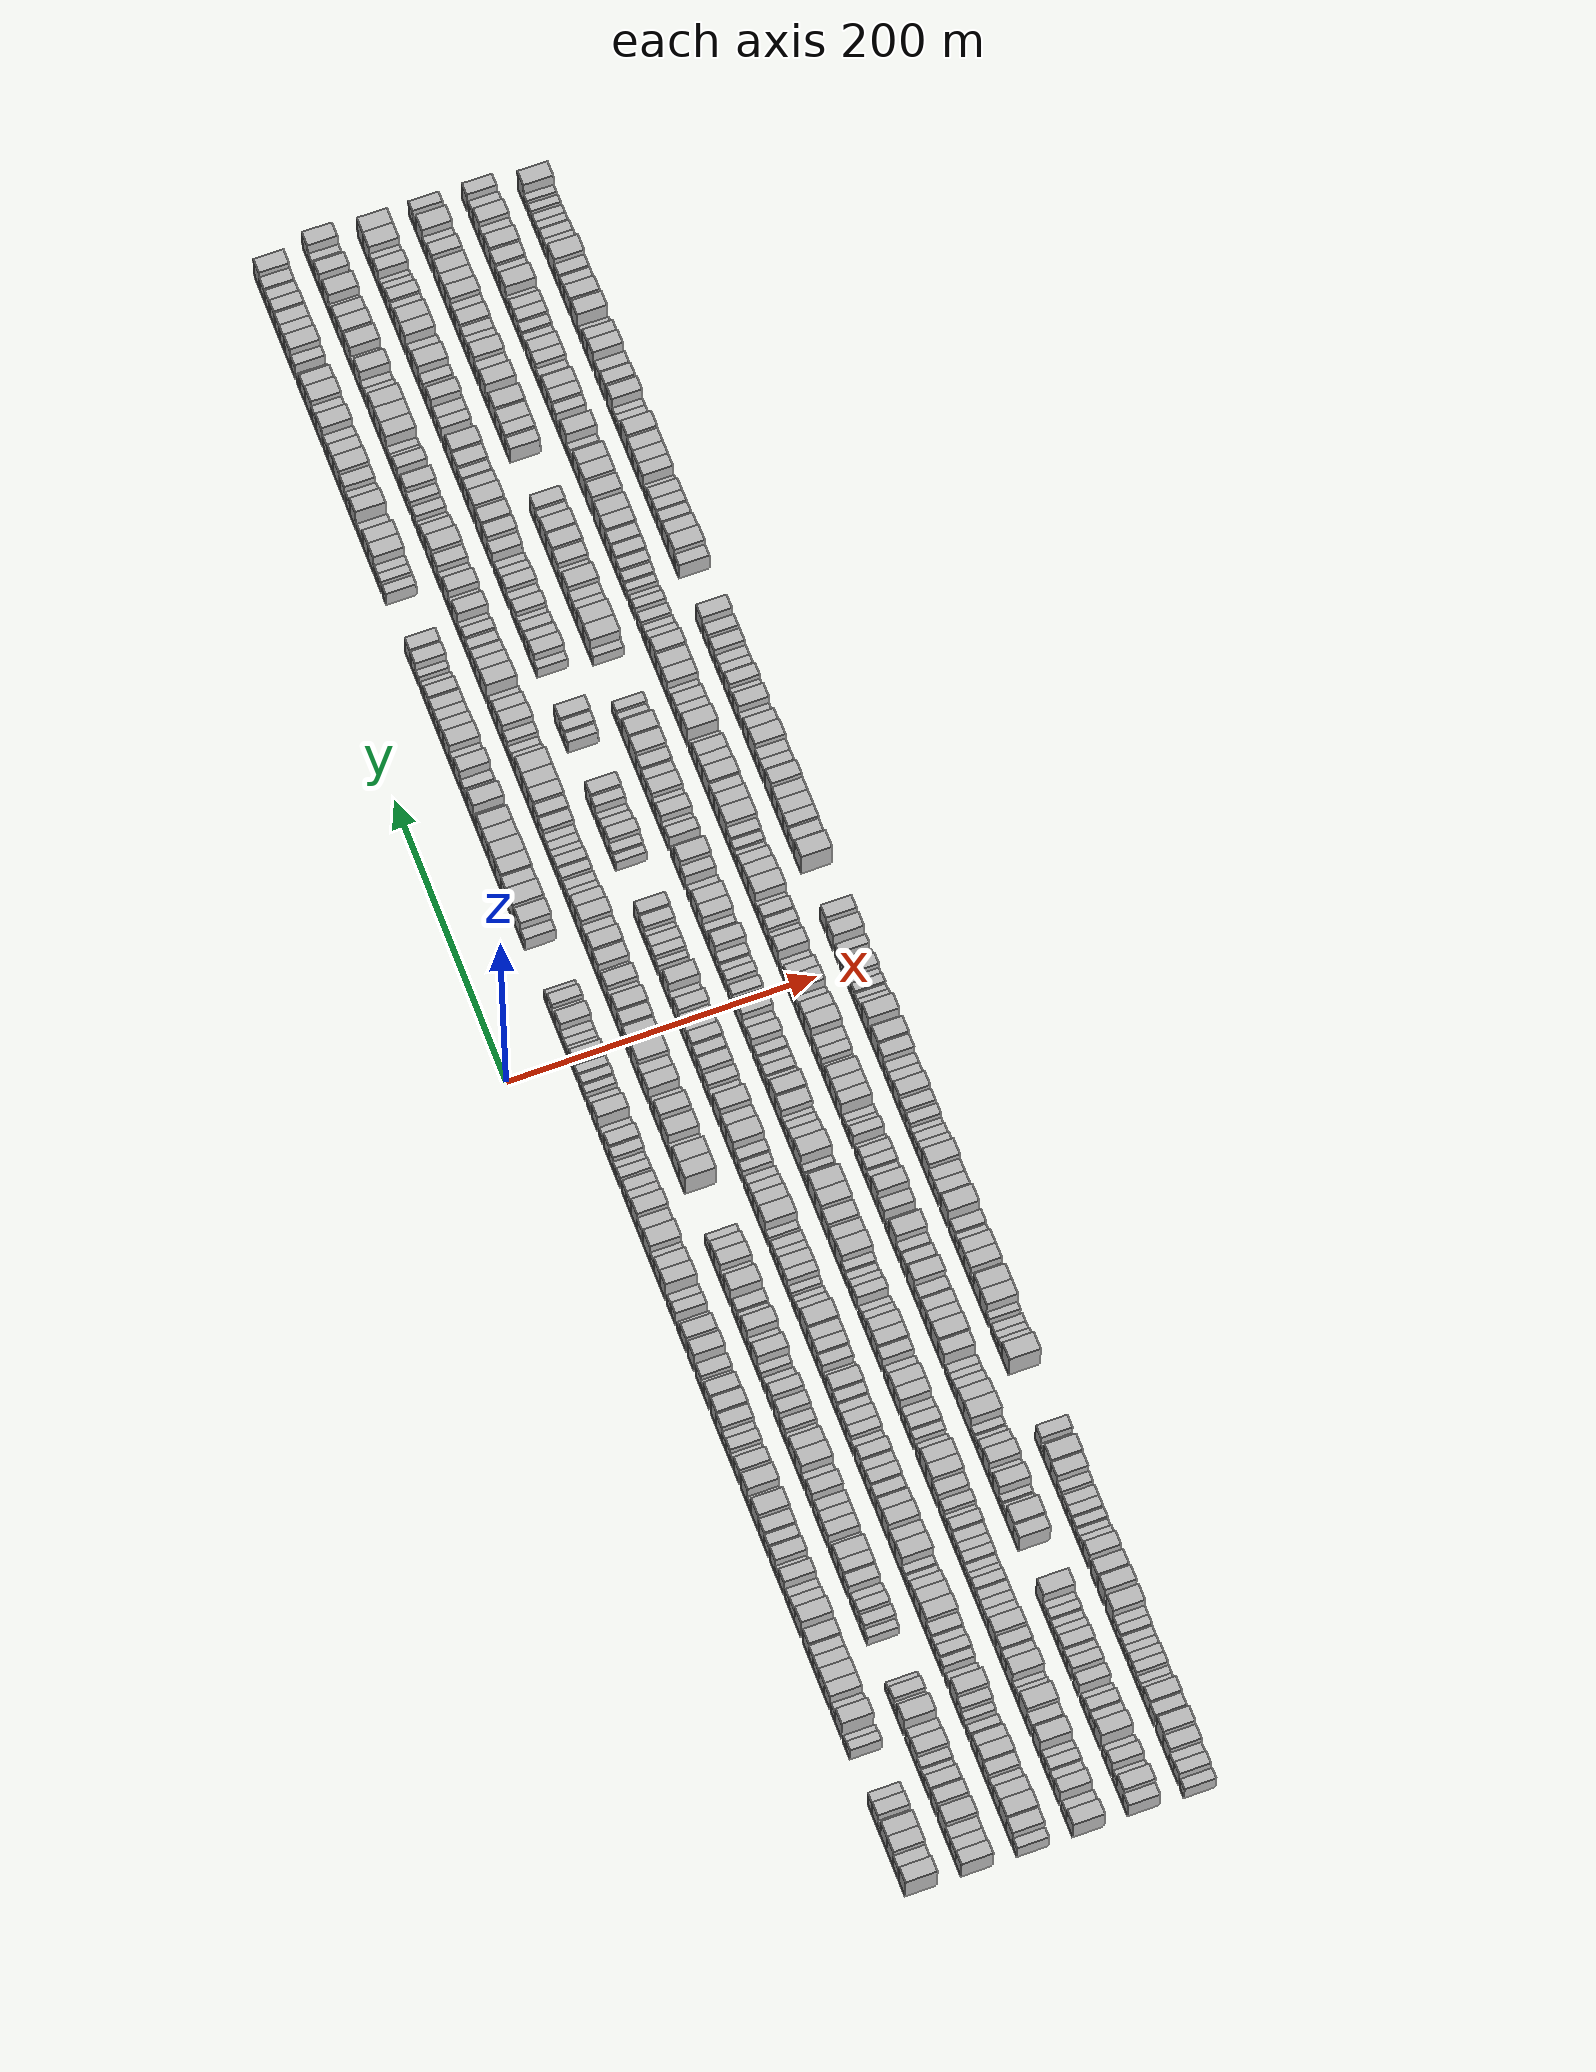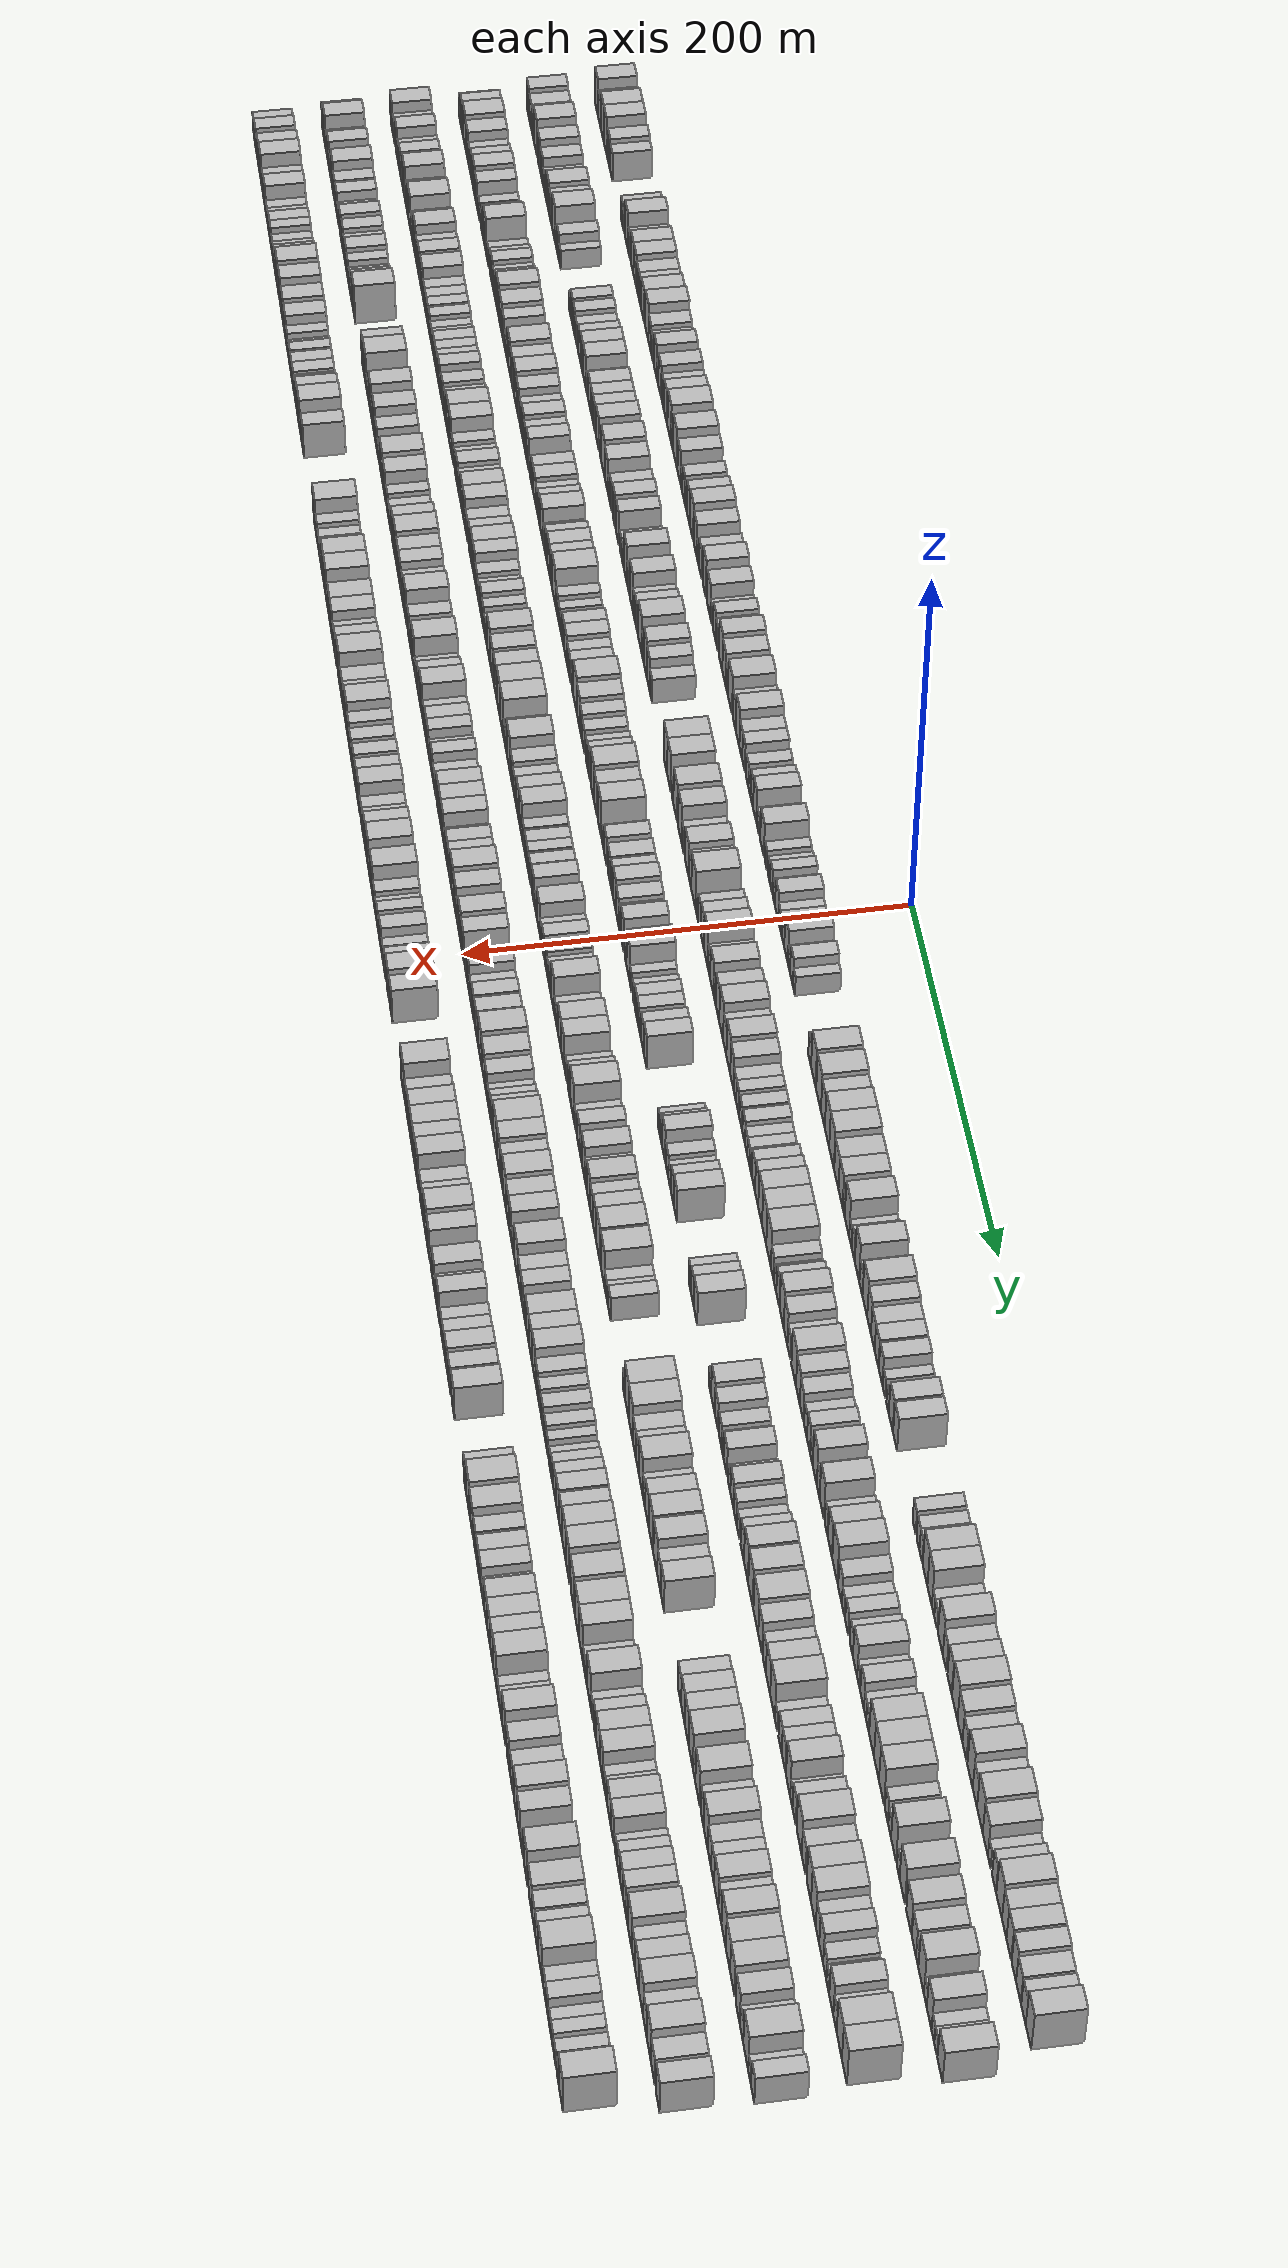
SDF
<sdf version="1.6">
 <world name="default">
  <scene>
   <sky><clouds><speed>12</speed></clouds></sky>
   <ambient>0.4 0.4 0.4 1</ambient>
   <background>0.7 0.7 0.7 1</background>
   <shadows>1</shadows>
  </scene>
  <gravity>0 0 -9.8066</gravity>
  <magnetic_field>6e-06 2.3e-05 -4.2e-05</magnetic_field>
  <physics default="0" name="default_physics" type="ode">
   <ode>
    <solver>
     <type>quick</type>
     <iters>10</iters>
     <sor>1.0</sor>
     <use_dynamic_moi_rescaling>0</use_dynamic_moi_rescaling>
    </solver>
    <constraints>
     <cfm>0</cfm>
     <erp>0.2</erp>
     <contact_max_correcting_vel>100</contact_max_correcting_vel>
     <contact_surface_layer>0.001</contact_surface_layer>
    </constraints>
   </ode>
   <max_step_size>0.004</max_step_size>
   <real_time_factor>1</real_time_factor>
   <real_time_update_rate>250</real_time_update_rate>
  </physics>
  <light name="sun" type="directional">
   <pose>0 0 10 0 0 0</pose>
   <diffuse>0.8 0.8 0.8 1</diffuse>
   <specular>0.2 0.2 0.2 1</specular>
   <attenuation>
    <range>1000</range>
    <constant>0.9</constant>
    <linear>0.01</linear>
    <quadratic>0.001</quadratic>
   </attenuation>
   <direction>-0.5 0.1 -0.9</direction>
  </light>
  <model name="building_1">
   <static>1</static>
   <pose>50.0000 -564.8574 0 0.000000 0.000000 0.000000</pose>
   <link name="link">
    <pose>0 0 12.00 0 0 0</pose>
    <collision name="collision"><geometry><box><size>20.0000 10.2851 24.0000</size></box></geometry></collision>
    <visual name="visual">
     <cast_shadows>0</cast_shadows>
     <geometry><box><size>20.0000 10.2851 24.0000</size></box></geometry>
     <material>
      <script>
       <uri>model://HANNAS_wall/materials/scripts</uri>
       <uri>model://HANNAS_wall/materials/textures</uri>
       <name>vrc/HANNAS_wall</name>
      </script>
     </material>
    </visual>
   </link>
  </model>
  <model name="building_2">
   <static>1</static>
   <pose>50.0000 -554.3436 0 0.000000 0.000000 0.000000</pose>
   <link name="link">
    <pose>0 0 9.00 0 0 0</pose>
    <collision name="collision"><geometry><box><size>20.0000 8.7425 18.0000</size></box></geometry></collision>
    <visual name="visual">
     <cast_shadows>0</cast_shadows>
     <geometry><box><size>20.0000 8.7425 18.0000</size></box></geometry>
     <material>
      <script>
       <uri>model://HANNAS_wall/materials/scripts</uri>
       <uri>model://HANNAS_wall/materials/textures</uri>
       <name>vrc/HANNAS_wall</name>
      </script>
     </material>
    </visual>
   </link>
  </model>
  <model name="building_3">
   <static>1</static>
   <pose>50.0000 -544.7289 0 0.000000 0.000000 0.000000</pose>
   <link name="link">
    <pose>0 0 12.00 0 0 0</pose>
    <collision name="collision"><geometry><box><size>20.0000 10.4869 24.0000</size></box></geometry></collision>
    <visual name="visual">
     <cast_shadows>0</cast_shadows>
     <geometry><box><size>20.0000 10.4869 24.0000</size></box></geometry>
     <material>
      <script>
       <uri>model://HANNAS_wall/materials/scripts</uri>
       <uri>model://HANNAS_wall/materials/textures</uri>
       <name>vrc/HANNAS_wall</name>
      </script>
     </material>
    </visual>
   </link>
  </model>
  <model name="building_4">
   <static>1</static>
   <pose>50.0000 -534.4632 0 0.000000 0.000000 0.000000</pose>
   <link name="link">
    <pose>0 0 12.00 0 0 0</pose>
    <collision name="collision"><geometry><box><size>20.0000 10.0446 24.0000</size></box></geometry></collision>
    <visual name="visual">
     <cast_shadows>0</cast_shadows>
     <geometry><box><size>20.0000 10.0446 24.0000</size></box></geometry>
     <material>
      <script>
       <uri>model://HANNAS_wall/materials/scripts</uri>
       <uri>model://HANNAS_wall/materials/textures</uri>
       <name>vrc/HANNAS_wall</name>
      </script>
     </material>
    </visual>
   </link>
  </model>
  <model name="building_5">
   <static>1</static>
   <pose>50.0000 -526.9971 0 0.000000 0.000000 0.000000</pose>
   <link name="link">
    <pose>0 0 6.00 0 0 0</pose>
    <collision name="collision"><geometry><box><size>20.0000 4.8877 12.0000</size></box></geometry></collision>
    <visual name="visual">
     <cast_shadows>0</cast_shadows>
     <geometry><box><size>20.0000 4.8877 12.0000</size></box></geometry>
     <material>
      <script>
       <uri>model://HANNAS_wall/materials/scripts</uri>
       <uri>model://HANNAS_wall/materials/textures</uri>
       <name>vrc/HANNAS_wall</name>
      </script>
     </material>
    </visual>
   </link>
  </model>
  <model name="building_6">
   <static>1</static>
   <pose>50.0000 -520.1027 0 0.000000 0.000000 0.000000</pose>
   <link name="link">
    <pose>0 0 10.50 0 0 0</pose>
    <collision name="collision"><geometry><box><size>20.0000 8.9011 21.0000</size></box></geometry></collision>
    <visual name="visual">
     <cast_shadows>0</cast_shadows>
     <geometry><box><size>20.0000 8.9011 21.0000</size></box></geometry>
     <material>
      <script>
       <uri>model://HANNAS_wall/materials/scripts</uri>
       <uri>model://HANNAS_wall/materials/textures</uri>
       <name>vrc/HANNAS_wall</name>
      </script>
     </material>
    </visual>
   </link>
  </model>
  <model name="building_7">
   <static>1</static>
   <pose>50.0000 -511.9449 0 0.000000 0.000000 0.000000</pose>
   <link name="link">
    <pose>0 0 9.00 0 0 0</pose>
    <collision name="collision"><geometry><box><size>20.0000 7.4144 18.0000</size></box></geometry></collision>
    <visual name="visual">
     <cast_shadows>0</cast_shadows>
     <geometry><box><size>20.0000 7.4144 18.0000</size></box></geometry>
     <material>
      <script>
       <uri>model://HANNAS_wall/materials/scripts</uri>
       <uri>model://HANNAS_wall/materials/textures</uri>
       <name>vrc/HANNAS_wall</name>
      </script>
     </material>
    </visual>
   </link>
  </model>
  <model name="building_8">
   <static>1</static>
   <pose>50.0000 -475.9182 0 0.000000 0.000000 0.000000</pose>
   <link name="link">
    <pose>0 0 7.50 0 0 0</pose>
    <collision name="collision"><geometry><box><size>20.0000 6.2130 15.0000</size></box></geometry></collision>
    <visual name="visual">
     <cast_shadows>0</cast_shadows>
     <geometry><box><size>20.0000 6.2130 15.0000</size></box></geometry>
     <material>
      <script>
       <uri>model://HANNAS_wall/materials/scripts</uri>
       <uri>model://HANNAS_wall/materials/textures</uri>
       <name>vrc/HANNAS_wall</name>
      </script>
     </material>
    </visual>
   </link>
  </model>
  <model name="building_9">
   <static>1</static>
   <pose>50.0000 -470.3054 0 0.000000 0.000000 0.000000</pose>
   <link name="link">
    <pose>0 0 6.00 0 0 0</pose>
    <collision name="collision"><geometry><box><size>20.0000 5.0124 12.0000</size></box></geometry></collision>
    <visual name="visual">
     <cast_shadows>0</cast_shadows>
     <geometry><box><size>20.0000 5.0124 12.0000</size></box></geometry>
     <material>
      <script>
       <uri>model://HANNAS_wall/materials/scripts</uri>
       <uri>model://HANNAS_wall/materials/textures</uri>
       <name>vrc/HANNAS_wall</name>
      </script>
     </material>
    </visual>
   </link>
  </model>
  <model name="building_10">
   <static>1</static>
   <pose>50.0000 -459.6862 0 0.000000 0.000000 0.000000</pose>
   <link name="link">
    <pose>0 0 12.00 0 0 0</pose>
    <collision name="collision"><geometry><box><size>20.0000 10.2260 24.0000</size></box></geometry></collision>
    <visual name="visual">
     <cast_shadows>0</cast_shadows>
     <geometry><box><size>20.0000 10.2260 24.0000</size></box></geometry>
     <material>
      <script>
       <uri>model://HANNAS_wall/materials/scripts</uri>
       <uri>model://HANNAS_wall/materials/textures</uri>
       <name>vrc/HANNAS_wall</name>
      </script>
     </material>
    </visual>
   </link>
  </model>
  <model name="building_11">
   <static>1</static>
   <pose>50.0000 -451.0208 0 0.000000 0.000000 0.000000</pose>
   <link name="link">
    <pose>0 0 7.50 0 0 0</pose>
    <collision name="collision"><geometry><box><size>20.0000 7.1049 15.0000</size></box></geometry></collision>
    <visual name="visual">
     <cast_shadows>0</cast_shadows>
     <geometry><box><size>20.0000 7.1049 15.0000</size></box></geometry>
     <material>
      <script>
       <uri>model://HANNAS_wall/materials/scripts</uri>
       <uri>model://HANNAS_wall/materials/textures</uri>
       <name>vrc/HANNAS_wall</name>
      </script>
     </material>
    </visual>
   </link>
  </model>
  <model name="building_12">
   <static>1</static>
   <pose>50.0000 -440.8777 0 0.000000 0.000000 0.000000</pose>
   <link name="link">
    <pose>0 0 10.50 0 0 0</pose>
    <collision name="collision"><geometry><box><size>20.0000 9.1814 21.0000</size></box></geometry></collision>
    <visual name="visual">
     <cast_shadows>0</cast_shadows>
     <geometry><box><size>20.0000 9.1814 21.0000</size></box></geometry>
     <material>
      <script>
       <uri>model://HANNAS_wall/materials/scripts</uri>
       <uri>model://HANNAS_wall/materials/textures</uri>
       <name>vrc/HANNAS_wall</name>
      </script>
     </material>
    </visual>
   </link>
  </model>
  <model name="building_13">
   <static>1</static>
   <pose>50.0000 -431.4291 0 0.000000 0.000000 0.000000</pose>
   <link name="link">
    <pose>0 0 10.50 0 0 0</pose>
    <collision name="collision"><geometry><box><size>20.0000 9.7158 21.0000</size></box></geometry></collision>
    <visual name="visual">
     <cast_shadows>0</cast_shadows>
     <geometry><box><size>20.0000 9.7158 21.0000</size></box></geometry>
     <material>
      <script>
       <uri>model://HANNAS_wall/materials/scripts</uri>
       <uri>model://HANNAS_wall/materials/textures</uri>
       <name>vrc/HANNAS_wall</name>
      </script>
     </material>
    </visual>
   </link>
  </model>
  <model name="building_14">
   <static>1</static>
   <pose>50.0000 -421.3837 0 0.000000 0.000000 0.000000</pose>
   <link name="link">
    <pose>0 0 9.00 0 0 0</pose>
    <collision name="collision"><geometry><box><size>20.0000 8.3751 18.0000</size></box></geometry></collision>
    <visual name="visual">
     <cast_shadows>0</cast_shadows>
     <geometry><box><size>20.0000 8.3751 18.0000</size></box></geometry>
     <material>
      <script>
       <uri>model://HANNAS_wall/materials/scripts</uri>
       <uri>model://HANNAS_wall/materials/textures</uri>
       <name>vrc/HANNAS_wall</name>
      </script>
     </material>
    </visual>
   </link>
  </model>
  <model name="building_15">
   <static>1</static>
   <pose>50.0000 -413.5854 0 0.000000 0.000000 0.000000</pose>
   <link name="link">
    <pose>0 0 9.00 0 0 0</pose>
    <collision name="collision"><geometry><box><size>20.0000 7.2215 18.0000</size></box></geometry></collision>
    <visual name="visual">
     <cast_shadows>0</cast_shadows>
     <geometry><box><size>20.0000 7.2215 18.0000</size></box></geometry>
     <material>
      <script>
       <uri>model://HANNAS_wall/materials/scripts</uri>
       <uri>model://HANNAS_wall/materials/textures</uri>
       <name>vrc/HANNAS_wall</name>
      </script>
     </material>
    </visual>
   </link>
  </model>
  <model name="building_16">
   <static>1</static>
   <pose>50.0000 -405.0166 0 0.000000 0.000000 0.000000</pose>
   <link name="link">
    <pose>0 0 10.50 0 0 0</pose>
    <collision name="collision"><geometry><box><size>20.0000 9.9160 21.0000</size></box></geometry></collision>
    <visual name="visual">
     <cast_shadows>0</cast_shadows>
     <geometry><box><size>20.0000 9.9160 21.0000</size></box></geometry>
     <material>
      <script>
       <uri>model://HANNAS_wall/materials/scripts</uri>
       <uri>model://HANNAS_wall/materials/textures</uri>
       <name>vrc/HANNAS_wall</name>
      </script>
     </material>
    </visual>
   </link>
  </model>
  <model name="building_17">
   <static>1</static>
   <pose>50.0000 -391.6826 0 0.000000 0.000000 0.000000</pose>
   <link name="link">
    <pose>0 0 12.00 0 0 0</pose>
    <collision name="collision"><geometry><box><size>20.0000 10.7519 24.0000</size></box></geometry></collision>
    <visual name="visual">
     <cast_shadows>0</cast_shadows>
     <geometry><box><size>20.0000 10.7519 24.0000</size></box></geometry>
     <material>
      <script>
       <uri>model://HANNAS_wall/materials/scripts</uri>
       <uri>model://HANNAS_wall/materials/textures</uri>
       <name>vrc/HANNAS_wall</name>
      </script>
     </material>
    </visual>
   </link>
  </model>
  <model name="building_18">
   <static>1</static>
   <pose>50.0000 -381.8562 0 0.000000 0.000000 0.000000</pose>
   <link name="link">
    <pose>0 0 9.00 0 0 0</pose>
    <collision name="collision"><geometry><box><size>20.0000 8.9010 18.0000</size></box></geometry></collision>
    <visual name="visual">
     <cast_shadows>0</cast_shadows>
     <geometry><box><size>20.0000 8.9010 18.0000</size></box></geometry>
     <material>
      <script>
       <uri>model://HANNAS_wall/materials/scripts</uri>
       <uri>model://HANNAS_wall/materials/textures</uri>
       <name>vrc/HANNAS_wall</name>
      </script>
     </material>
    </visual>
   </link>
  </model>
  <model name="building_19">
   <static>1</static>
   <pose>50.0000 -374.0080 0 0.000000 0.000000 0.000000</pose>
   <link name="link">
    <pose>0 0 7.50 0 0 0</pose>
    <collision name="collision"><geometry><box><size>20.0000 6.7954 15.0000</size></box></geometry></collision>
    <visual name="visual">
     <cast_shadows>0</cast_shadows>
     <geometry><box><size>20.0000 6.7954 15.0000</size></box></geometry>
     <material>
      <script>
       <uri>model://HANNAS_wall/materials/scripts</uri>
       <uri>model://HANNAS_wall/materials/textures</uri>
       <name>vrc/HANNAS_wall</name>
      </script>
     </material>
    </visual>
   </link>
  </model>
  <model name="building_20">
   <static>1</static>
   <pose>50.0000 -364.0766 0 0.000000 0.000000 0.000000</pose>
   <link name="link">
    <pose>0 0 10.50 0 0 0</pose>
    <collision name="collision"><geometry><box><size>20.0000 9.0674 21.0000</size></box></geometry></collision>
    <visual name="visual">
     <cast_shadows>0</cast_shadows>
     <geometry><box><size>20.0000 9.0674 21.0000</size></box></geometry>
     <material>
      <script>
       <uri>model://HANNAS_wall/materials/scripts</uri>
       <uri>model://HANNAS_wall/materials/textures</uri>
       <name>vrc/HANNAS_wall</name>
      </script>
     </material>
    </visual>
   </link>
  </model>
  <model name="building_21">
   <static>1</static>
   <pose>50.0000 -356.7486 0 0.000000 0.000000 0.000000</pose>
   <link name="link">
    <pose>0 0 6.00 0 0 0</pose>
    <collision name="collision"><geometry><box><size>20.0000 5.5885 12.0000</size></box></geometry></collision>
    <visual name="visual">
     <cast_shadows>0</cast_shadows>
     <geometry><box><size>20.0000 5.5885 12.0000</size></box></geometry>
     <material>
      <script>
       <uri>model://HANNAS_wall/materials/scripts</uri>
       <uri>model://HANNAS_wall/materials/textures</uri>
       <name>vrc/HANNAS_wall</name>
      </script>
     </material>
    </visual>
   </link>
  </model>
  <model name="building_22">
   <static>1</static>
   <pose>50.0000 -349.2690 0 0.000000 0.000000 0.000000</pose>
   <link name="link">
    <pose>0 0 10.50 0 0 0</pose>
    <collision name="collision"><geometry><box><size>20.0000 9.3707 21.0000</size></box></geometry></collision>
    <visual name="visual">
     <cast_shadows>0</cast_shadows>
     <geometry><box><size>20.0000 9.3707 21.0000</size></box></geometry>
     <material>
      <script>
       <uri>model://HANNAS_wall/materials/scripts</uri>
       <uri>model://HANNAS_wall/materials/textures</uri>
       <name>vrc/HANNAS_wall</name>
      </script>
     </material>
    </visual>
   </link>
  </model>
  <model name="building_23">
   <static>1</static>
   <pose>50.0000 -338.8808 0 0.000000 0.000000 0.000000</pose>
   <link name="link">
    <pose>0 0 9.00 0 0 0</pose>
    <collision name="collision"><geometry><box><size>20.0000 7.4057 18.0000</size></box></geometry></collision>
    <visual name="visual">
     <cast_shadows>0</cast_shadows>
     <geometry><box><size>20.0000 7.4057 18.0000</size></box></geometry>
     <material>
      <script>
       <uri>model://HANNAS_wall/materials/scripts</uri>
       <uri>model://HANNAS_wall/materials/textures</uri>
       <name>vrc/HANNAS_wall</name>
      </script>
     </material>
    </visual>
   </link>
  </model>
  <model name="building_24">
   <static>1</static>
   <pose>50.0000 -330.4658 0 0.000000 0.000000 0.000000</pose>
   <link name="link">
    <pose>0 0 10.50 0 0 0</pose>
    <collision name="collision"><geometry><box><size>20.0000 9.4243 21.0000</size></box></geometry></collision>
    <visual name="visual">
     <cast_shadows>0</cast_shadows>
     <geometry><box><size>20.0000 9.4243 21.0000</size></box></geometry>
     <material>
      <script>
       <uri>model://HANNAS_wall/materials/scripts</uri>
       <uri>model://HANNAS_wall/materials/textures</uri>
       <name>vrc/HANNAS_wall</name>
      </script>
     </material>
    </visual>
   </link>
  </model>
  <model name="building_25">
   <static>1</static>
   <pose>50.0000 -318.8479 0 0.000000 0.000000 0.000000</pose>
   <link name="link">
    <pose>0 0 12.00 0 0 0</pose>
    <collision name="collision"><geometry><box><size>20.0000 11.8115 24.0000</size></box></geometry></collision>
    <visual name="visual">
     <cast_shadows>0</cast_shadows>
     <geometry><box><size>20.0000 11.8115 24.0000</size></box></geometry>
     <material>
      <script>
       <uri>model://HANNAS_wall/materials/scripts</uri>
       <uri>model://HANNAS_wall/materials/textures</uri>
       <name>vrc/HANNAS_wall</name>
      </script>
     </material>
    </visual>
   </link>
  </model>
  <model name="building_26">
   <static>1</static>
   <pose>50.0000 -309.9669 0 0.000000 0.000000 0.000000</pose>
   <link name="link">
    <pose>0 0 6.00 0 0 0</pose>
    <collision name="collision"><geometry><box><size>20.0000 5.9504 12.0000</size></box></geometry></collision>
    <visual name="visual">
     <cast_shadows>0</cast_shadows>
     <geometry><box><size>20.0000 5.9504 12.0000</size></box></geometry>
     <material>
      <script>
       <uri>model://HANNAS_wall/materials/scripts</uri>
       <uri>model://HANNAS_wall/materials/textures</uri>
       <name>vrc/HANNAS_wall</name>
      </script>
     </material>
    </visual>
   </link>
  </model>
  <model name="building_27">
   <static>1</static>
   <pose>50.0000 -301.4803 0 0.000000 0.000000 0.000000</pose>
   <link name="link">
    <pose>0 0 12.00 0 0 0</pose>
    <collision name="collision"><geometry><box><size>20.0000 11.0227 24.0000</size></box></geometry></collision>
    <visual name="visual">
     <cast_shadows>0</cast_shadows>
     <geometry><box><size>20.0000 11.0227 24.0000</size></box></geometry>
     <material>
      <script>
       <uri>model://HANNAS_wall/materials/scripts</uri>
       <uri>model://HANNAS_wall/materials/textures</uri>
       <name>vrc/HANNAS_wall</name>
      </script>
     </material>
    </visual>
   </link>
  </model>
  <model name="building_28">
   <static>1</static>
   <pose>50.0000 -288.3178 0 0.000000 0.000000 0.000000</pose>
   <link name="link">
    <pose>0 0 10.50 0 0 0</pose>
    <collision name="collision"><geometry><box><size>20.0000 9.3022 21.0000</size></box></geometry></collision>
    <visual name="visual">
     <cast_shadows>0</cast_shadows>
     <geometry><box><size>20.0000 9.3022 21.0000</size></box></geometry>
     <material>
      <script>
       <uri>model://HANNAS_wall/materials/scripts</uri>
       <uri>model://HANNAS_wall/materials/textures</uri>
       <name>vrc/HANNAS_wall</name>
      </script>
     </material>
    </visual>
   </link>
  </model>
  <model name="building_29">
   <static>1</static>
   <pose>50.0000 -280.1687 0 0.000000 0.000000 0.000000</pose>
   <link name="link">
    <pose>0 0 6.00 0 0 0</pose>
    <collision name="collision"><geometry><box><size>20.0000 4.9961 12.0000</size></box></geometry></collision>
    <visual name="visual">
     <cast_shadows>0</cast_shadows>
     <geometry><box><size>20.0000 4.9961 12.0000</size></box></geometry>
     <material>
      <script>
       <uri>model://HANNAS_wall/materials/scripts</uri>
       <uri>model://HANNAS_wall/materials/textures</uri>
       <name>vrc/HANNAS_wall</name>
      </script>
     </material>
    </visual>
   </link>
  </model>
  <model name="building_30">
   <static>1</static>
   <pose>50.0000 -273.7644 0 0.000000 0.000000 0.000000</pose>
   <link name="link">
    <pose>0 0 9.00 0 0 0</pose>
    <collision name="collision"><geometry><box><size>20.0000 7.8124 18.0000</size></box></geometry></collision>
    <visual name="visual">
     <cast_shadows>0</cast_shadows>
     <geometry><box><size>20.0000 7.8124 18.0000</size></box></geometry>
     <material>
      <script>
       <uri>model://HANNAS_wall/materials/scripts</uri>
       <uri>model://HANNAS_wall/materials/textures</uri>
       <name>vrc/HANNAS_wall</name>
      </script>
     </material>
    </visual>
   </link>
  </model>
  <model name="building_31">
   <static>1</static>
   <pose>50.0000 -266.8491 0 0.000000 0.000000 0.000000</pose>
   <link name="link">
    <pose>0 0 7.50 0 0 0</pose>
    <collision name="collision"><geometry><box><size>20.0000 6.0181 15.0000</size></box></geometry></collision>
    <visual name="visual">
     <cast_shadows>0</cast_shadows>
     <geometry><box><size>20.0000 6.0181 15.0000</size></box></geometry>
     <material>
      <script>
       <uri>model://HANNAS_wall/materials/scripts</uri>
       <uri>model://HANNAS_wall/materials/textures</uri>
       <name>vrc/HANNAS_wall</name>
      </script>
     </material>
    </visual>
   </link>
  </model>
  <model name="building_32">
   <static>1</static>
   <pose>50.0000 -259.1165 0 0.000000 0.000000 0.000000</pose>
   <link name="link">
    <pose>0 0 10.50 0 0 0</pose>
    <collision name="collision"><geometry><box><size>20.0000 9.4472 21.0000</size></box></geometry></collision>
    <visual name="visual">
     <cast_shadows>0</cast_shadows>
     <geometry><box><size>20.0000 9.4472 21.0000</size></box></geometry>
     <material>
      <script>
       <uri>model://HANNAS_wall/materials/scripts</uri>
       <uri>model://HANNAS_wall/materials/textures</uri>
       <name>vrc/HANNAS_wall</name>
      </script>
     </material>
    </visual>
   </link>
  </model>
  <model name="building_33">
   <static>1</static>
   <pose>50.0000 -249.3366 0 0.000000 0.000000 0.000000</pose>
   <link name="link">
    <pose>0 0 12.00 0 0 0</pose>
    <collision name="collision"><geometry><box><size>20.0000 10.1127 24.0000</size></box></geometry></collision>
    <visual name="visual">
     <cast_shadows>0</cast_shadows>
     <geometry><box><size>20.0000 10.1127 24.0000</size></box></geometry>
     <material>
      <script>
       <uri>model://HANNAS_wall/materials/scripts</uri>
       <uri>model://HANNAS_wall/materials/textures</uri>
       <name>vrc/HANNAS_wall</name>
      </script>
     </material>
    </visual>
   </link>
  </model>
  <model name="building_34">
   <static>1</static>
   <pose>50.0000 -237.4707 0 0.000000 0.000000 0.000000</pose>
   <link name="link">
    <pose>0 0 10.50 0 0 0</pose>
    <collision name="collision"><geometry><box><size>20.0000 9.6190 21.0000</size></box></geometry></collision>
    <visual name="visual">
     <cast_shadows>0</cast_shadows>
     <geometry><box><size>20.0000 9.6190 21.0000</size></box></geometry>
     <material>
      <script>
       <uri>model://HANNAS_wall/materials/scripts</uri>
       <uri>model://HANNAS_wall/materials/textures</uri>
       <name>vrc/HANNAS_wall</name>
      </script>
     </material>
    </visual>
   </link>
  </model>
  <model name="building_35">
   <static>1</static>
   <pose>50.0000 -230.1163 0 0.000000 0.000000 0.000000</pose>
   <link name="link">
    <pose>0 0 6.00 0 0 0</pose>
    <collision name="collision"><geometry><box><size>20.0000 5.0898 12.0000</size></box></geometry></collision>
    <visual name="visual">
     <cast_shadows>0</cast_shadows>
     <geometry><box><size>20.0000 5.0898 12.0000</size></box></geometry>
     <material>
      <script>
       <uri>model://HANNAS_wall/materials/scripts</uri>
       <uri>model://HANNAS_wall/materials/textures</uri>
       <name>vrc/HANNAS_wall</name>
      </script>
     </material>
    </visual>
   </link>
  </model>
  <model name="building_36">
   <static>1</static>
   <pose>50.0000 -223.1273 0 0.000000 0.000000 0.000000</pose>
   <link name="link">
    <pose>0 0 9.00 0 0 0</pose>
    <collision name="collision"><geometry><box><size>20.0000 8.8881 18.0000</size></box></geometry></collision>
    <visual name="visual">
     <cast_shadows>0</cast_shadows>
     <geometry><box><size>20.0000 8.8881 18.0000</size></box></geometry>
     <material>
      <script>
       <uri>model://HANNAS_wall/materials/scripts</uri>
       <uri>model://HANNAS_wall/materials/textures</uri>
       <name>vrc/HANNAS_wall</name>
      </script>
     </material>
    </visual>
   </link>
  </model>
  <model name="building_37">
   <static>1</static>
   <pose>50.0000 -210.6286 0 0.000000 0.000000 0.000000</pose>
   <link name="link">
    <pose>0 0 12.00 0 0 0</pose>
    <collision name="collision"><geometry><box><size>20.0000 10.1094 24.0000</size></box></geometry></collision>
    <visual name="visual">
     <cast_shadows>0</cast_shadows>
     <geometry><box><size>20.0000 10.1094 24.0000</size></box></geometry>
     <material>
      <script>
       <uri>model://HANNAS_wall/materials/scripts</uri>
       <uri>model://HANNAS_wall/materials/textures</uri>
       <name>vrc/HANNAS_wall</name>
      </script>
     </material>
    </visual>
   </link>
  </model>
  <model name="building_38">
   <static>1</static>
   <pose>50.0000 -197.5220 0 0.000000 0.000000 0.000000</pose>
   <link name="link">
    <pose>0 0 10.50 0 0 0</pose>
    <collision name="collision"><geometry><box><size>20.0000 10.1038 21.0000</size></box></geometry></collision>
    <visual name="visual">
     <cast_shadows>0</cast_shadows>
     <geometry><box><size>20.0000 10.1038 21.0000</size></box></geometry>
     <material>
      <script>
       <uri>model://HANNAS_wall/materials/scripts</uri>
       <uri>model://HANNAS_wall/materials/textures</uri>
       <name>vrc/HANNAS_wall</name>
      </script>
     </material>
    </visual>
   </link>
  </model>
  <model name="building_39">
   <static>1</static>
   <pose>50.0000 -189.8411 0 0.000000 0.000000 0.000000</pose>
   <link name="link">
    <pose>0 0 6.00 0 0 0</pose>
    <collision name="collision"><geometry><box><size>20.0000 5.2579 12.0000</size></box></geometry></collision>
    <visual name="visual">
     <cast_shadows>0</cast_shadows>
     <geometry><box><size>20.0000 5.2579 12.0000</size></box></geometry>
     <material>
      <script>
       <uri>model://HANNAS_wall/materials/scripts</uri>
       <uri>model://HANNAS_wall/materials/textures</uri>
       <name>vrc/HANNAS_wall</name>
      </script>
     </material>
    </visual>
   </link>
  </model>
  <model name="building_40">
   <static>1</static>
   <pose>50.0000 -180.4697 0 0.000000 0.000000 0.000000</pose>
   <link name="link">
    <pose>0 0 9.00 0 0 0</pose>
    <collision name="collision"><geometry><box><size>20.0000 7.4849 18.0000</size></box></geometry></collision>
    <visual name="visual">
     <cast_shadows>0</cast_shadows>
     <geometry><box><size>20.0000 7.4849 18.0000</size></box></geometry>
     <material>
      <script>
       <uri>model://HANNAS_wall/materials/scripts</uri>
       <uri>model://HANNAS_wall/materials/textures</uri>
       <name>vrc/HANNAS_wall</name>
      </script>
     </material>
    </visual>
   </link>
  </model>
  <model name="building_41">
   <static>1</static>
   <pose>50.0000 -173.3436 0 0.000000 0.000000 0.000000</pose>
   <link name="link">
    <pose>0 0 7.50 0 0 0</pose>
    <collision name="collision"><geometry><box><size>20.0000 6.7671 15.0000</size></box></geometry></collision>
    <visual name="visual">
     <cast_shadows>0</cast_shadows>
     <geometry><box><size>20.0000 6.7671 15.0000</size></box></geometry>
     <material>
      <script>
       <uri>model://HANNAS_wall/materials/scripts</uri>
       <uri>model://HANNAS_wall/materials/textures</uri>
       <name>vrc/HANNAS_wall</name>
      </script>
     </material>
    </visual>
   </link>
  </model>
  <model name="building_42">
   <static>1</static>
   <pose>50.0000 -161.9749 0 0.000000 0.000000 0.000000</pose>
   <link name="link">
    <pose>0 0 12.00 0 0 0</pose>
    <collision name="collision"><geometry><box><size>20.0000 9.9704 24.0000</size></box></geometry></collision>
    <visual name="visual">
     <cast_shadows>0</cast_shadows>
     <geometry><box><size>20.0000 9.9704 24.0000</size></box></geometry>
     <material>
      <script>
       <uri>model://HANNAS_wall/materials/scripts</uri>
       <uri>model://HANNAS_wall/materials/textures</uri>
       <name>vrc/HANNAS_wall</name>
      </script>
     </material>
    </visual>
   </link>
  </model>
  <model name="building_43">
   <static>1</static>
   <pose>50.0000 -151.9547 0 0.000000 0.000000 0.000000</pose>
   <link name="link">
    <pose>0 0 10.50 0 0 0</pose>
    <collision name="collision"><geometry><box><size>20.0000 10.0702 21.0000</size></box></geometry></collision>
    <visual name="visual">
     <cast_shadows>0</cast_shadows>
     <geometry><box><size>20.0000 10.0702 21.0000</size></box></geometry>
     <material>
      <script>
       <uri>model://HANNAS_wall/materials/scripts</uri>
       <uri>model://HANNAS_wall/materials/textures</uri>
       <name>vrc/HANNAS_wall</name>
      </script>
     </material>
    </visual>
   </link>
  </model>
  <model name="building_44">
   <static>1</static>
   <pose>50.0000 -143.8304 0 0.000000 0.000000 0.000000</pose>
   <link name="link">
    <pose>0 0 7.50 0 0 0</pose>
    <collision name="collision"><geometry><box><size>20.0000 6.1783 15.0000</size></box></geometry></collision>
    <visual name="visual">
     <cast_shadows>0</cast_shadows>
     <geometry><box><size>20.0000 6.1783 15.0000</size></box></geometry>
     <material>
      <script>
       <uri>model://HANNAS_wall/materials/scripts</uri>
       <uri>model://HANNAS_wall/materials/textures</uri>
       <name>vrc/HANNAS_wall</name>
      </script>
     </material>
    </visual>
   </link>
  </model>
  <model name="building_45">
   <static>1</static>
   <pose>50.0000 -134.7940 0 0.000000 0.000000 0.000000</pose>
   <link name="link">
    <pose>0 0 12.00 0 0 0</pose>
    <collision name="collision"><geometry><box><size>20.0000 11.8945 24.0000</size></box></geometry></collision>
    <visual name="visual">
     <cast_shadows>0</cast_shadows>
     <geometry><box><size>20.0000 11.8945 24.0000</size></box></geometry>
     <material>
      <script>
       <uri>model://HANNAS_wall/materials/scripts</uri>
       <uri>model://HANNAS_wall/materials/textures</uri>
       <name>vrc/HANNAS_wall</name>
      </script>
     </material>
    </visual>
   </link>
  </model>
  <model name="building_46">
   <static>1</static>
   <pose>50.0000 -122.5110 0 0.000000 0.000000 0.000000</pose>
   <link name="link">
    <pose>0 0 9.00 0 0 0</pose>
    <collision name="collision"><geometry><box><size>20.0000 8.6716 18.0000</size></box></geometry></collision>
    <visual name="visual">
     <cast_shadows>0</cast_shadows>
     <geometry><box><size>20.0000 8.6716 18.0000</size></box></geometry>
     <material>
      <script>
       <uri>model://HANNAS_wall/materials/scripts</uri>
       <uri>model://HANNAS_wall/materials/textures</uri>
       <name>vrc/HANNAS_wall</name>
      </script>
     </material>
    </visual>
   </link>
  </model>
  <model name="building_47">
   <static>1</static>
   <pose>50.0000 -112.9188 0 0.000000 0.000000 0.000000</pose>
   <link name="link">
    <pose>0 0 12.00 0 0 0</pose>
    <collision name="collision"><geometry><box><size>20.0000 10.5128 24.0000</size></box></geometry></collision>
    <visual name="visual">
     <cast_shadows>0</cast_shadows>
     <geometry><box><size>20.0000 10.5128 24.0000</size></box></geometry>
     <material>
      <script>
       <uri>model://HANNAS_wall/materials/scripts</uri>
       <uri>model://HANNAS_wall/materials/textures</uri>
       <name>vrc/HANNAS_wall</name>
      </script>
     </material>
    </visual>
   </link>
  </model>
  <model name="building_48">
   <static>1</static>
   <pose>50.0000 -103.6665 0 0.000000 0.000000 0.000000</pose>
   <link name="link">
    <pose>0 0 9.00 0 0 0</pose>
    <collision name="collision"><geometry><box><size>20.0000 7.9920 18.0000</size></box></geometry></collision>
    <visual name="visual">
     <cast_shadows>0</cast_shadows>
     <geometry><box><size>20.0000 7.9920 18.0000</size></box></geometry>
     <material>
      <script>
       <uri>model://HANNAS_wall/materials/scripts</uri>
       <uri>model://HANNAS_wall/materials/textures</uri>
       <name>vrc/HANNAS_wall</name>
      </script>
     </material>
    </visual>
   </link>
  </model>
  <model name="building_49">
   <static>1</static>
   <pose>50.0000 -95.8522 0 0.000000 0.000000 0.000000</pose>
   <link name="link">
    <pose>0 0 9.00 0 0 0</pose>
    <collision name="collision"><geometry><box><size>20.0000 7.6366 18.0000</size></box></geometry></collision>
    <visual name="visual">
     <cast_shadows>0</cast_shadows>
     <geometry><box><size>20.0000 7.6366 18.0000</size></box></geometry>
     <material>
      <script>
       <uri>model://HANNAS_wall/materials/scripts</uri>
       <uri>model://HANNAS_wall/materials/textures</uri>
       <name>vrc/HANNAS_wall</name>
      </script>
     </material>
    </visual>
   </link>
  </model>
  <model name="building_50">
   <static>1</static>
   <pose>50.0000 -85.5797 0 0.000000 0.000000 0.000000</pose>
   <link name="link">
    <pose>0 0 7.50 0 0 0</pose>
    <collision name="collision"><geometry><box><size>20.0000 6.9084 15.0000</size></box></geometry></collision>
    <visual name="visual">
     <cast_shadows>0</cast_shadows>
     <geometry><box><size>20.0000 6.9084 15.0000</size></box></geometry>
     <material>
      <script>
       <uri>model://HANNAS_wall/materials/scripts</uri>
       <uri>model://HANNAS_wall/materials/textures</uri>
       <name>vrc/HANNAS_wall</name>
      </script>
     </material>
    </visual>
   </link>
  </model>
  <model name="building_51">
   <static>1</static>
   <pose>50.0000 -79.2340 0 0.000000 0.000000 0.000000</pose>
   <link name="link">
    <pose>0 0 6.00 0 0 0</pose>
    <collision name="collision"><geometry><box><size>20.0000 5.7830 12.0000</size></box></geometry></collision>
    <visual name="visual">
     <cast_shadows>0</cast_shadows>
     <geometry><box><size>20.0000 5.7830 12.0000</size></box></geometry>
     <material>
      <script>
       <uri>model://HANNAS_wall/materials/scripts</uri>
       <uri>model://HANNAS_wall/materials/textures</uri>
       <name>vrc/HANNAS_wall</name>
      </script>
     </material>
    </visual>
   </link>
  </model>
  <model name="building_52">
   <static>1</static>
   <pose>50.0000 -72.7375 0 0.000000 0.000000 0.000000</pose>
   <link name="link">
    <pose>0 0 9.00 0 0 0</pose>
    <collision name="collision"><geometry><box><size>20.0000 7.2101 18.0000</size></box></geometry></collision>
    <visual name="visual">
     <cast_shadows>0</cast_shadows>
     <geometry><box><size>20.0000 7.2101 18.0000</size></box></geometry>
     <material>
      <script>
       <uri>model://HANNAS_wall/materials/scripts</uri>
       <uri>model://HANNAS_wall/materials/textures</uri>
       <name>vrc/HANNAS_wall</name>
      </script>
     </material>
    </visual>
   </link>
  </model>
  <model name="building_53">
   <static>1</static>
   <pose>50.0000 -64.7337 0 0.000000 0.000000 0.000000</pose>
   <link name="link">
    <pose>0 0 10.50 0 0 0</pose>
    <collision name="collision"><geometry><box><size>20.0000 8.7974 21.0000</size></box></geometry></collision>
    <visual name="visual">
     <cast_shadows>0</cast_shadows>
     <geometry><box><size>20.0000 8.7974 21.0000</size></box></geometry>
     <material>
      <script>
       <uri>model://HANNAS_wall/materials/scripts</uri>
       <uri>model://HANNAS_wall/materials/textures</uri>
       <name>vrc/HANNAS_wall</name>
      </script>
     </material>
    </visual>
   </link>
  </model>
  <model name="building_54">
   <static>1</static>
   <pose>50.0000 -55.3769 0 0.000000 0.000000 0.000000</pose>
   <link name="link">
    <pose>0 0 6.00 0 0 0</pose>
    <collision name="collision"><geometry><box><size>20.0000 5.9163 12.0000</size></box></geometry></collision>
    <visual name="visual">
     <cast_shadows>0</cast_shadows>
     <geometry><box><size>20.0000 5.9163 12.0000</size></box></geometry>
     <material>
      <script>
       <uri>model://HANNAS_wall/materials/scripts</uri>
       <uri>model://HANNAS_wall/materials/textures</uri>
       <name>vrc/HANNAS_wall</name>
      </script>
     </material>
    </visual>
   </link>
  </model>
  <model name="building_55">
   <static>1</static>
   <pose>50.0000 -44.3208 0 0.000000 0.000000 0.000000</pose>
   <link name="link">
    <pose>0 0 10.50 0 0 0</pose>
    <collision name="collision"><geometry><box><size>20.0000 10.1959 21.0000</size></box></geometry></collision>
    <visual name="visual">
     <cast_shadows>0</cast_shadows>
     <geometry><box><size>20.0000 10.1959 21.0000</size></box></geometry>
     <material>
      <script>
       <uri>model://HANNAS_wall/materials/scripts</uri>
       <uri>model://HANNAS_wall/materials/textures</uri>
       <name>vrc/HANNAS_wall</name>
      </script>
     </material>
    </visual>
   </link>
  </model>
  <model name="building_56">
   <static>1</static>
   <pose>50.0000 -34.2954 0 0.000000 0.000000 0.000000</pose>
   <link name="link">
    <pose>0 0 6.00 0 0 0</pose>
    <collision name="collision"><geometry><box><size>20.0000 5.8549 12.0000</size></box></geometry></collision>
    <visual name="visual">
     <cast_shadows>0</cast_shadows>
     <geometry><box><size>20.0000 5.8549 12.0000</size></box></geometry>
     <material>
      <script>
       <uri>model://HANNAS_wall/materials/scripts</uri>
       <uri>model://HANNAS_wall/materials/textures</uri>
       <name>vrc/HANNAS_wall</name>
      </script>
     </material>
    </visual>
   </link>
  </model>
  <model name="building_57">
   <static>1</static>
   <pose>50.0000 -25.5949 0 0.000000 0.000000 0.000000</pose>
   <link name="link">
    <pose>0 0 6.00 0 0 0</pose>
    <collision name="collision"><geometry><box><size>20.0000 5.5460 12.0000</size></box></geometry></collision>
    <visual name="visual">
     <cast_shadows>0</cast_shadows>
     <geometry><box><size>20.0000 5.5460 12.0000</size></box></geometry>
     <material>
      <script>
       <uri>model://HANNAS_wall/materials/scripts</uri>
       <uri>model://HANNAS_wall/materials/textures</uri>
       <name>vrc/HANNAS_wall</name>
      </script>
     </material>
    </visual>
   </link>
  </model>
  <model name="building_58">
   <static>1</static>
   <pose>50.0000 -19.7453 0 0.000000 0.000000 0.000000</pose>
   <link name="link">
    <pose>0 0 7.50 0 0 0</pose>
    <collision name="collision"><geometry><box><size>20.0000 6.1533 15.0000</size></box></geometry></collision>
    <visual name="visual">
     <cast_shadows>0</cast_shadows>
     <geometry><box><size>20.0000 6.1533 15.0000</size></box></geometry>
     <material>
      <script>
       <uri>model://HANNAS_wall/materials/scripts</uri>
       <uri>model://HANNAS_wall/materials/textures</uri>
       <name>vrc/HANNAS_wall</name>
      </script>
     </material>
    </visual>
   </link>
  </model>
  <model name="building_59">
   <static>1</static>
   <pose>50.0000 -11.7610 0 0.000000 0.000000 0.000000</pose>
   <link name="link">
    <pose>0 0 6.00 0 0 0</pose>
    <collision name="collision"><geometry><box><size>20.0000 5.8154 12.0000</size></box></geometry></collision>
    <visual name="visual">
     <cast_shadows>0</cast_shadows>
     <geometry><box><size>20.0000 5.8154 12.0000</size></box></geometry>
     <material>
      <script>
       <uri>model://HANNAS_wall/materials/scripts</uri>
       <uri>model://HANNAS_wall/materials/textures</uri>
       <name>vrc/HANNAS_wall</name>
      </script>
     </material>
    </visual>
   </link>
  </model>
  <model name="building_60">
   <static>1</static>
   <pose>50.0000 -4.5406 0 0.000000 0.000000 0.000000</pose>
   <link name="link">
    <pose>0 0 9.00 0 0 0</pose>
    <collision name="collision"><geometry><box><size>20.0000 8.6253 18.0000</size></box></geometry></collision>
    <visual name="visual">
     <cast_shadows>0</cast_shadows>
     <geometry><box><size>20.0000 8.6253 18.0000</size></box></geometry>
     <material>
      <script>
       <uri>model://HANNAS_wall/materials/scripts</uri>
       <uri>model://HANNAS_wall/materials/textures</uri>
       <name>vrc/HANNAS_wall</name>
      </script>
     </material>
    </visual>
   </link>
  </model>
  <model name="building_61">
   <static>1</static>
   <pose>50.0000 2.2006 0 0.000000 0.000000 0.000000</pose>
   <link name="link">
    <pose>0 0 6.00 0 0 0</pose>
    <collision name="collision"><geometry><box><size>20.0000 4.8570 12.0000</size></box></geometry></collision>
    <visual name="visual">
     <cast_shadows>0</cast_shadows>
     <geometry><box><size>20.0000 4.8570 12.0000</size></box></geometry>
     <material>
      <script>
       <uri>model://HANNAS_wall/materials/scripts</uri>
       <uri>model://HANNAS_wall/materials/textures</uri>
       <name>vrc/HANNAS_wall</name>
      </script>
     </material>
    </visual>
   </link>
  </model>
  <model name="building_62">
   <static>1</static>
   <pose>50.0000 7.3138 0 0.000000 0.000000 0.000000</pose>
   <link name="link">
    <pose>0 0 6.00 0 0 0</pose>
    <collision name="collision"><geometry><box><size>20.0000 5.3694 12.0000</size></box></geometry></collision>
    <visual name="visual">
     <cast_shadows>0</cast_shadows>
     <geometry><box><size>20.0000 5.3694 12.0000</size></box></geometry>
     <material>
      <script>
       <uri>model://HANNAS_wall/materials/scripts</uri>
       <uri>model://HANNAS_wall/materials/textures</uri>
       <name>vrc/HANNAS_wall</name>
      </script>
     </material>
    </visual>
   </link>
  </model>
  <model name="building_63">
   <static>1</static>
   <pose>50.0000 12.8486 0 0.000000 0.000000 0.000000</pose>
   <link name="link">
    <pose>0 0 6.00 0 0 0</pose>
    <collision name="collision"><geometry><box><size>20.0000 5.7001 12.0000</size></box></geometry></collision>
    <visual name="visual">
     <cast_shadows>0</cast_shadows>
     <geometry><box><size>20.0000 5.7001 12.0000</size></box></geometry>
     <material>
      <script>
       <uri>model://HANNAS_wall/materials/scripts</uri>
       <uri>model://HANNAS_wall/materials/textures</uri>
       <name>vrc/HANNAS_wall</name>
      </script>
     </material>
    </visual>
   </link>
  </model>
  <model name="building_64">
   <static>1</static>
   <pose>50.0000 20.5025 0 0.000000 0.000000 0.000000</pose>
   <link name="link">
    <pose>0 0 10.50 0 0 0</pose>
    <collision name="collision"><geometry><box><size>20.0000 9.6077 21.0000</size></box></geometry></collision>
    <visual name="visual">
     <cast_shadows>0</cast_shadows>
     <geometry><box><size>20.0000 9.6077 21.0000</size></box></geometry>
     <material>
      <script>
       <uri>model://HANNAS_wall/materials/scripts</uri>
       <uri>model://HANNAS_wall/materials/textures</uri>
       <name>vrc/HANNAS_wall</name>
      </script>
     </material>
    </visual>
   </link>
  </model>
  <model name="building_65">
   <static>1</static>
   <pose>50.0000 28.1299 0 0.000000 0.000000 0.000000</pose>
   <link name="link">
    <pose>0 0 6.00 0 0 0</pose>
    <collision name="collision"><geometry><box><size>20.0000 5.6471 12.0000</size></box></geometry></collision>
    <visual name="visual">
     <cast_shadows>0</cast_shadows>
     <geometry><box><size>20.0000 5.6471 12.0000</size></box></geometry>
     <material>
      <script>
       <uri>model://HANNAS_wall/materials/scripts</uri>
       <uri>model://HANNAS_wall/materials/textures</uri>
       <name>vrc/HANNAS_wall</name>
      </script>
     </material>
    </visual>
   </link>
  </model>
  <model name="building_66">
   <static>1</static>
   <pose>50.0000 34.8647 0 0.000000 0.000000 0.000000</pose>
   <link name="link">
    <pose>0 0 9.00 0 0 0</pose>
    <collision name="collision"><geometry><box><size>20.0000 7.8226 18.0000</size></box></geometry></collision>
    <visual name="visual">
     <cast_shadows>0</cast_shadows>
     <geometry><box><size>20.0000 7.8226 18.0000</size></box></geometry>
     <material>
      <script>
       <uri>model://HANNAS_wall/materials/scripts</uri>
       <uri>model://HANNAS_wall/materials/textures</uri>
       <name>vrc/HANNAS_wall</name>
      </script>
     </material>
    </visual>
   </link>
  </model>
  <model name="building_67">
   <static>1</static>
   <pose>50.0000 41.5274 0 0.000000 0.000000 0.000000</pose>
   <link name="link">
    <pose>0 0 6.00 0 0 0</pose>
    <collision name="collision"><geometry><box><size>20.0000 5.5028 12.0000</size></box></geometry></collision>
    <visual name="visual">
     <cast_shadows>0</cast_shadows>
     <geometry><box><size>20.0000 5.5028 12.0000</size></box></geometry>
     <material>
      <script>
       <uri>model://HANNAS_wall/materials/scripts</uri>
       <uri>model://HANNAS_wall/materials/textures</uri>
       <name>vrc/HANNAS_wall</name>
      </script>
     </material>
    </visual>
   </link>
  </model>
  <model name="building_68">
   <static>1</static>
   <pose>50.0000 82.0958 0 0.000000 0.000000 0.000000</pose>
   <link name="link">
    <pose>0 0 7.50 0 0 0</pose>
    <collision name="collision"><geometry><box><size>20.0000 7.2113 15.0000</size></box></geometry></collision>
    <visual name="visual">
     <cast_shadows>0</cast_shadows>
     <geometry><box><size>20.0000 7.2113 15.0000</size></box></geometry>
     <material>
      <script>
       <uri>model://HANNAS_wall/materials/scripts</uri>
       <uri>model://HANNAS_wall/materials/textures</uri>
       <name>vrc/HANNAS_wall</name>
      </script>
     </material>
    </visual>
   </link>
  </model>
  <model name="building_69">
   <static>1</static>
   <pose>50.0000 91.2356 0 0.000000 0.000000 0.000000</pose>
   <link name="link">
    <pose>0 0 12.00 0 0 0</pose>
    <collision name="collision"><geometry><box><size>20.0000 11.0683 24.0000</size></box></geometry></collision>
    <visual name="visual">
     <cast_shadows>0</cast_shadows>
     <geometry><box><size>20.0000 11.0683 24.0000</size></box></geometry>
     <material>
      <script>
       <uri>model://HANNAS_wall/materials/scripts</uri>
       <uri>model://HANNAS_wall/materials/textures</uri>
       <name>vrc/HANNAS_wall</name>
      </script>
     </material>
    </visual>
   </link>
  </model>
  <model name="building_70">
   <static>1</static>
   <pose>50.0000 104.7687 0 0.000000 0.000000 0.000000</pose>
   <link name="link">
    <pose>0 0 12.00 0 0 0</pose>
    <collision name="collision"><geometry><box><size>20.0000 11.9978 24.0000</size></box></geometry></collision>
    <visual name="visual">
     <cast_shadows>0</cast_shadows>
     <geometry><box><size>20.0000 11.9978 24.0000</size></box></geometry>
     <material>
      <script>
       <uri>model://HANNAS_wall/materials/scripts</uri>
       <uri>model://HANNAS_wall/materials/textures</uri>
       <name>vrc/HANNAS_wall</name>
      </script>
     </material>
    </visual>
   </link>
  </model>
  <model name="building_71">
   <static>1</static>
   <pose>50.0000 115.5978 0 0.000000 0.000000 0.000000</pose>
   <link name="link">
    <pose>0 0 10.50 0 0 0</pose>
    <collision name="collision"><geometry><box><size>20.0000 9.6604 21.0000</size></box></geometry></collision>
    <visual name="visual">
     <cast_shadows>0</cast_shadows>
     <geometry><box><size>20.0000 9.6604 21.0000</size></box></geometry>
     <material>
      <script>
       <uri>model://HANNAS_wall/materials/scripts</uri>
       <uri>model://HANNAS_wall/materials/textures</uri>
       <name>vrc/HANNAS_wall</name>
      </script>
     </material>
    </visual>
   </link>
  </model>
  <model name="building_72">
   <static>1</static>
   <pose>50.0000 125.9151 0 0.000000 0.000000 0.000000</pose>
   <link name="link">
    <pose>0 0 12.00 0 0 0</pose>
    <collision name="collision"><geometry><box><size>20.0000 10.9743 24.0000</size></box></geometry></collision>
    <visual name="visual">
     <cast_shadows>0</cast_shadows>
     <geometry><box><size>20.0000 10.9743 24.0000</size></box></geometry>
     <material>
      <script>
       <uri>model://HANNAS_wall/materials/scripts</uri>
       <uri>model://HANNAS_wall/materials/textures</uri>
       <name>vrc/HANNAS_wall</name>
      </script>
     </material>
    </visual>
   </link>
  </model>
  <model name="building_73">
   <static>1</static>
   <pose>50.0000 137.1472 0 0.000000 0.000000 0.000000</pose>
   <link name="link">
    <pose>0 0 12.00 0 0 0</pose>
    <collision name="collision"><geometry><box><size>20.0000 11.4898 24.0000</size></box></geometry></collision>
    <visual name="visual">
     <cast_shadows>0</cast_shadows>
     <geometry><box><size>20.0000 11.4898 24.0000</size></box></geometry>
     <material>
      <script>
       <uri>model://HANNAS_wall/materials/scripts</uri>
       <uri>model://HANNAS_wall/materials/textures</uri>
       <name>vrc/HANNAS_wall</name>
      </script>
     </material>
    </visual>
   </link>
  </model>
  <model name="building_74">
   <static>1</static>
   <pose>50.0000 149.1418 0 0.000000 0.000000 0.000000</pose>
   <link name="link">
    <pose>0 0 10.50 0 0 0</pose>
    <collision name="collision"><geometry><box><size>20.0000 10.4993 21.0000</size></box></geometry></collision>
    <visual name="visual">
     <cast_shadows>0</cast_shadows>
     <geometry><box><size>20.0000 10.4993 21.0000</size></box></geometry>
     <material>
      <script>
       <uri>model://HANNAS_wall/materials/scripts</uri>
       <uri>model://HANNAS_wall/materials/textures</uri>
       <name>vrc/HANNAS_wall</name>
      </script>
     </material>
    </visual>
   </link>
  </model>
  <model name="building_75">
   <static>1</static>
   <pose>50.0000 159.4135 0 0.000000 0.000000 0.000000</pose>
   <link name="link">
    <pose>0 0 10.50 0 0 0</pose>
    <collision name="collision"><geometry><box><size>20.0000 10.0442 21.0000</size></box></geometry></collision>
    <visual name="visual">
     <cast_shadows>0</cast_shadows>
     <geometry><box><size>20.0000 10.0442 21.0000</size></box></geometry>
     <material>
      <script>
       <uri>model://HANNAS_wall/materials/scripts</uri>
       <uri>model://HANNAS_wall/materials/textures</uri>
       <name>vrc/HANNAS_wall</name>
      </script>
     </material>
    </visual>
   </link>
  </model>
  <model name="building_76">
   <static>1</static>
   <pose>50.0000 167.0654 0 0.000000 0.000000 0.000000</pose>
   <link name="link">
    <pose>0 0 6.00 0 0 0</pose>
    <collision name="collision"><geometry><box><size>20.0000 5.2596 12.0000</size></box></geometry></collision>
    <visual name="visual">
     <cast_shadows>0</cast_shadows>
     <geometry><box><size>20.0000 5.2596 12.0000</size></box></geometry>
     <material>
      <script>
       <uri>model://HANNAS_wall/materials/scripts</uri>
       <uri>model://HANNAS_wall/materials/textures</uri>
       <name>vrc/HANNAS_wall</name>
      </script>
     </material>
    </visual>
   </link>
  </model>
  <model name="building_77">
   <static>1</static>
   <pose>50.0000 175.1060 0 0.000000 0.000000 0.000000</pose>
   <link name="link">
    <pose>0 0 12.00 0 0 0</pose>
    <collision name="collision"><geometry><box><size>20.0000 10.8216 24.0000</size></box></geometry></collision>
    <visual name="visual">
     <cast_shadows>0</cast_shadows>
     <geometry><box><size>20.0000 10.8216 24.0000</size></box></geometry>
     <material>
      <script>
       <uri>model://HANNAS_wall/materials/scripts</uri>
       <uri>model://HANNAS_wall/materials/textures</uri>
       <name>vrc/HANNAS_wall</name>
      </script>
     </material>
    </visual>
   </link>
  </model>
  <model name="building_78">
   <static>1</static>
   <pose>50.0000 183.3770 0 0.000000 0.000000 0.000000</pose>
   <link name="link">
    <pose>0 0 6.00 0 0 0</pose>
    <collision name="collision"><geometry><box><size>20.0000 5.7204 12.0000</size></box></geometry></collision>
    <visual name="visual">
     <cast_shadows>0</cast_shadows>
     <geometry><box><size>20.0000 5.7204 12.0000</size></box></geometry>
     <material>
      <script>
       <uri>model://HANNAS_wall/materials/scripts</uri>
       <uri>model://HANNAS_wall/materials/textures</uri>
       <name>vrc/HANNAS_wall</name>
      </script>
     </material>
    </visual>
   </link>
  </model>
  <model name="building_79">
   <static>1</static>
   <pose>50.0000 189.6017 0 0.000000 0.000000 0.000000</pose>
   <link name="link">
    <pose>0 0 7.50 0 0 0</pose>
    <collision name="collision"><geometry><box><size>20.0000 6.7291 15.0000</size></box></geometry></collision>
    <visual name="visual">
     <cast_shadows>0</cast_shadows>
     <geometry><box><size>20.0000 6.7291 15.0000</size></box></geometry>
     <material>
      <script>
       <uri>model://HANNAS_wall/materials/scripts</uri>
       <uri>model://HANNAS_wall/materials/textures</uri>
       <name>vrc/HANNAS_wall</name>
      </script>
     </material>
    </visual>
   </link>
  </model>
  <model name="building_80">
   <static>1</static>
   <pose>50.0000 199.0172 0 0.000000 0.000000 0.000000</pose>
   <link name="link">
    <pose>0 0 12.00 0 0 0</pose>
    <collision name="collision"><geometry><box><size>20.0000 10.1020 24.0000</size></box></geometry></collision>
    <visual name="visual">
     <cast_shadows>0</cast_shadows>
     <geometry><box><size>20.0000 10.1020 24.0000</size></box></geometry>
     <material>
      <script>
       <uri>model://HANNAS_wall/materials/scripts</uri>
       <uri>model://HANNAS_wall/materials/textures</uri>
       <name>vrc/HANNAS_wall</name>
      </script>
     </material>
    </visual>
   </link>
  </model>
  <model name="building_81">
   <static>1</static>
   <pose>50.0000 208.7307 0 0.000000 0.000000 0.000000</pose>
   <link name="link">
    <pose>0 0 7.50 0 0 0</pose>
    <collision name="collision"><geometry><box><size>20.0000 7.3249 15.0000</size></box></geometry></collision>
    <visual name="visual">
     <cast_shadows>0</cast_shadows>
     <geometry><box><size>20.0000 7.3249 15.0000</size></box></geometry>
     <material>
      <script>
       <uri>model://HANNAS_wall/materials/scripts</uri>
       <uri>model://HANNAS_wall/materials/textures</uri>
       <name>vrc/HANNAS_wall</name>
      </script>
     </material>
    </visual>
   </link>
  </model>
  <model name="building_82">
   <static>1</static>
   <pose>50.0000 217.9473 0 0.000000 0.000000 0.000000</pose>
   <link name="link">
    <pose>0 0 12.00 0 0 0</pose>
    <collision name="collision"><geometry><box><size>20.0000 11.1084 24.0000</size></box></geometry></collision>
    <visual name="visual">
     <cast_shadows>0</cast_shadows>
     <geometry><box><size>20.0000 11.1084 24.0000</size></box></geometry>
     <material>
      <script>
       <uri>model://HANNAS_wall/materials/scripts</uri>
       <uri>model://HANNAS_wall/materials/textures</uri>
       <name>vrc/HANNAS_wall</name>
      </script>
     </material>
    </visual>
   </link>
  </model>
  <model name="building_83">
   <static>1</static>
   <pose>50.0000 227.8729 0 0.000000 0.000000 0.000000</pose>
   <link name="link">
    <pose>0 0 10.50 0 0 0</pose>
    <collision name="collision"><geometry><box><size>20.0000 8.7429 21.0000</size></box></geometry></collision>
    <visual name="visual">
     <cast_shadows>0</cast_shadows>
     <geometry><box><size>20.0000 8.7429 21.0000</size></box></geometry>
     <material>
      <script>
       <uri>model://HANNAS_wall/materials/scripts</uri>
       <uri>model://HANNAS_wall/materials/textures</uri>
       <name>vrc/HANNAS_wall</name>
      </script>
     </material>
    </visual>
   </link>
  </model>
  <model name="building_84">
   <static>1</static>
   <pose>50.0000 236.6198 0 0.000000 0.000000 0.000000</pose>
   <link name="link">
    <pose>0 0 9.00 0 0 0</pose>
    <collision name="collision"><geometry><box><size>20.0000 8.7509 18.0000</size></box></geometry></collision>
    <visual name="visual">
     <cast_shadows>0</cast_shadows>
     <geometry><box><size>20.0000 8.7509 18.0000</size></box></geometry>
     <material>
      <script>
       <uri>model://HANNAS_wall/materials/scripts</uri>
       <uri>model://HANNAS_wall/materials/textures</uri>
       <name>vrc/HANNAS_wall</name>
      </script>
     </material>
    </visual>
   </link>
  </model>
  <model name="building_85">
   <static>1</static>
   <pose>50.0000 245.3287 0 0.000000 0.000000 0.000000</pose>
   <link name="link">
    <pose>0 0 9.00 0 0 0</pose>
    <collision name="collision"><geometry><box><size>20.0000 8.6668 18.0000</size></box></geometry></collision>
    <visual name="visual">
     <cast_shadows>0</cast_shadows>
     <geometry><box><size>20.0000 8.6668 18.0000</size></box></geometry>
     <material>
      <script>
       <uri>model://HANNAS_wall/materials/scripts</uri>
       <uri>model://HANNAS_wall/materials/textures</uri>
       <name>vrc/HANNAS_wall</name>
      </script>
     </material>
    </visual>
   </link>
  </model>
  <model name="building_86">
   <static>1</static>
   <pose>50.0000 254.8167 0 0.000000 0.000000 0.000000</pose>
   <link name="link">
    <pose>0 0 9.00 0 0 0</pose>
    <collision name="collision"><geometry><box><size>20.0000 8.3091 18.0000</size></box></geometry></collision>
    <visual name="visual">
     <cast_shadows>0</cast_shadows>
     <geometry><box><size>20.0000 8.3091 18.0000</size></box></geometry>
     <material>
      <script>
       <uri>model://HANNAS_wall/materials/scripts</uri>
       <uri>model://HANNAS_wall/materials/textures</uri>
       <name>vrc/HANNAS_wall</name>
      </script>
     </material>
    </visual>
   </link>
  </model>
  <model name="building_87">
   <static>1</static>
   <pose>50.0000 262.5719 0 0.000000 0.000000 0.000000</pose>
   <link name="link">
    <pose>0 0 6.00 0 0 0</pose>
    <collision name="collision"><geometry><box><size>20.0000 5.2014 12.0000</size></box></geometry></collision>
    <visual name="visual">
     <cast_shadows>0</cast_shadows>
     <geometry><box><size>20.0000 5.2014 12.0000</size></box></geometry>
     <material>
      <script>
       <uri>model://HANNAS_wall/materials/scripts</uri>
       <uri>model://HANNAS_wall/materials/textures</uri>
       <name>vrc/HANNAS_wall</name>
      </script>
     </material>
    </visual>
   </link>
  </model>
  <model name="building_88">
   <static>1</static>
   <pose>50.0000 270.8324 0 0.000000 0.000000 0.000000</pose>
   <link name="link">
    <pose>0 0 6.00 0 0 0</pose>
    <collision name="collision"><geometry><box><size>20.0000 5.3197 12.0000</size></box></geometry></collision>
    <visual name="visual">
     <cast_shadows>0</cast_shadows>
     <geometry><box><size>20.0000 5.3197 12.0000</size></box></geometry>
     <material>
      <script>
       <uri>model://HANNAS_wall/materials/scripts</uri>
       <uri>model://HANNAS_wall/materials/textures</uri>
       <name>vrc/HANNAS_wall</name>
      </script>
     </material>
    </visual>
   </link>
  </model>
  <model name="building_89">
   <static>1</static>
   <pose>50.0000 277.9955 0 0.000000 0.000000 0.000000</pose>
   <link name="link">
    <pose>0 0 10.50 0 0 0</pose>
    <collision name="collision"><geometry><box><size>20.0000 9.0065 21.0000</size></box></geometry></collision>
    <visual name="visual">
     <cast_shadows>0</cast_shadows>
     <geometry><box><size>20.0000 9.0065 21.0000</size></box></geometry>
     <material>
      <script>
       <uri>model://HANNAS_wall/materials/scripts</uri>
       <uri>model://HANNAS_wall/materials/textures</uri>
       <name>vrc/HANNAS_wall</name>
      </script>
     </material>
    </visual>
   </link>
  </model>
  <model name="building_90">
   <static>1</static>
   <pose>50.0000 288.0217 0 0.000000 0.000000 0.000000</pose>
   <link name="link">
    <pose>0 0 10.50 0 0 0</pose>
    <collision name="collision"><geometry><box><size>20.0000 9.0459 21.0000</size></box></geometry></collision>
    <visual name="visual">
     <cast_shadows>0</cast_shadows>
     <geometry><box><size>20.0000 9.0459 21.0000</size></box></geometry>
     <material>
      <script>
       <uri>model://HANNAS_wall/materials/scripts</uri>
       <uri>model://HANNAS_wall/materials/textures</uri>
       <name>vrc/HANNAS_wall</name>
      </script>
     </material>
    </visual>
   </link>
  </model>
  <model name="building_91">
   <static>1</static>
   <pose>50.0000 330.6306 0 0.000000 0.000000 0.000000</pose>
   <link name="link">
    <pose>0 0 7.50 0 0 0</pose>
    <collision name="collision"><geometry><box><size>20.0000 6.7240 15.0000</size></box></geometry></collision>
    <visual name="visual">
     <cast_shadows>0</cast_shadows>
     <geometry><box><size>20.0000 6.7240 15.0000</size></box></geometry>
     <material>
      <script>
       <uri>model://HANNAS_wall/materials/scripts</uri>
       <uri>model://HANNAS_wall/materials/textures</uri>
       <name>vrc/HANNAS_wall</name>
      </script>
     </material>
    </visual>
   </link>
  </model>
  <model name="building_92">
   <static>1</static>
   <pose>50.0000 339.1388 0 0.000000 0.000000 0.000000</pose>
   <link name="link">
    <pose>0 0 7.50 0 0 0</pose>
    <collision name="collision"><geometry><box><size>20.0000 6.2924 15.0000</size></box></geometry></collision>
    <visual name="visual">
     <cast_shadows>0</cast_shadows>
     <geometry><box><size>20.0000 6.2924 15.0000</size></box></geometry>
     <material>
      <script>
       <uri>model://HANNAS_wall/materials/scripts</uri>
       <uri>model://HANNAS_wall/materials/textures</uri>
       <name>vrc/HANNAS_wall</name>
      </script>
     </material>
    </visual>
   </link>
  </model>
  <model name="building_93">
   <static>1</static>
   <pose>50.0000 345.3433 0 0.000000 0.000000 0.000000</pose>
   <link name="link">
    <pose>0 0 7.50 0 0 0</pose>
    <collision name="collision"><geometry><box><size>20.0000 6.1166 15.0000</size></box></geometry></collision>
    <visual name="visual">
     <cast_shadows>0</cast_shadows>
     <geometry><box><size>20.0000 6.1166 15.0000</size></box></geometry>
     <material>
      <script>
       <uri>model://HANNAS_wall/materials/scripts</uri>
       <uri>model://HANNAS_wall/materials/textures</uri>
       <name>vrc/HANNAS_wall</name>
      </script>
     </material>
    </visual>
   </link>
  </model>
  <model name="building_94">
   <static>1</static>
   <pose>50.0000 354.5466 0 0.000000 0.000000 0.000000</pose>
   <link name="link">
    <pose>0 0 12.00 0 0 0</pose>
    <collision name="collision"><geometry><box><size>20.0000 10.2900 24.0000</size></box></geometry></collision>
    <visual name="visual">
     <cast_shadows>0</cast_shadows>
     <geometry><box><size>20.0000 10.2900 24.0000</size></box></geometry>
     <material>
      <script>
       <uri>model://HANNAS_wall/materials/scripts</uri>
       <uri>model://HANNAS_wall/materials/textures</uri>
       <name>vrc/HANNAS_wall</name>
      </script>
     </material>
    </visual>
   </link>
  </model>
  <model name="building_95">
   <static>1</static>
   <pose>50.0000 364.5611 0 0.000000 0.000000 0.000000</pose>
   <link name="link">
    <pose>0 0 12.00 0 0 0</pose>
    <collision name="collision"><geometry><box><size>20.0000 9.7390 24.0000</size></box></geometry></collision>
    <visual name="visual">
     <cast_shadows>0</cast_shadows>
     <geometry><box><size>20.0000 9.7390 24.0000</size></box></geometry>
     <material>
      <script>
       <uri>model://HANNAS_wall/materials/scripts</uri>
       <uri>model://HANNAS_wall/materials/textures</uri>
       <name>vrc/HANNAS_wall</name>
      </script>
     </material>
    </visual>
   </link>
  </model>
  <model name="building_96">
   <static>1</static>
   <pose>50.0000 372.0114 0 0.000000 0.000000 0.000000</pose>
   <link name="link">
    <pose>0 0 6.00 0 0 0</pose>
    <collision name="collision"><geometry><box><size>20.0000 5.1617 12.0000</size></box></geometry></collision>
    <visual name="visual">
     <cast_shadows>0</cast_shadows>
     <geometry><box><size>20.0000 5.1617 12.0000</size></box></geometry>
     <material>
      <script>
       <uri>model://HANNAS_wall/materials/scripts</uri>
       <uri>model://HANNAS_wall/materials/textures</uri>
       <name>vrc/HANNAS_wall</name>
      </script>
     </material>
    </visual>
   </link>
  </model>
  <model name="building_97">
   <static>1</static>
   <pose>50.0000 377.5267 0 0.000000 0.000000 0.000000</pose>
   <link name="link">
    <pose>0 0 6.00 0 0 0</pose>
    <collision name="collision"><geometry><box><size>20.0000 5.8690 12.0000</size></box></geometry></collision>
    <visual name="visual">
     <cast_shadows>0</cast_shadows>
     <geometry><box><size>20.0000 5.8690 12.0000</size></box></geometry>
     <material>
      <script>
       <uri>model://HANNAS_wall/materials/scripts</uri>
       <uri>model://HANNAS_wall/materials/textures</uri>
       <name>vrc/HANNAS_wall</name>
      </script>
     </material>
    </visual>
   </link>
  </model>
  <model name="building_98">
   <static>1</static>
   <pose>50.0000 387.6979 0 0.000000 0.000000 0.000000</pose>
   <link name="link">
    <pose>0 0 12.00 0 0 0</pose>
    <collision name="collision"><geometry><box><size>20.0000 10.4733 24.0000</size></box></geometry></collision>
    <visual name="visual">
     <cast_shadows>0</cast_shadows>
     <geometry><box><size>20.0000 10.4733 24.0000</size></box></geometry>
     <material>
      <script>
       <uri>model://HANNAS_wall/materials/scripts</uri>
       <uri>model://HANNAS_wall/materials/textures</uri>
       <name>vrc/HANNAS_wall</name>
      </script>
     </material>
    </visual>
   </link>
  </model>
  <model name="building_99">
   <static>1</static>
   <pose>50.0000 396.7069 0 0.000000 0.000000 0.000000</pose>
   <link name="link">
    <pose>0 0 9.00 0 0 0</pose>
    <collision name="collision"><geometry><box><size>20.0000 7.5447 18.0000</size></box></geometry></collision>
    <visual name="visual">
     <cast_shadows>0</cast_shadows>
     <geometry><box><size>20.0000 7.5447 18.0000</size></box></geometry>
     <material>
      <script>
       <uri>model://HANNAS_wall/materials/scripts</uri>
       <uri>model://HANNAS_wall/materials/textures</uri>
       <name>vrc/HANNAS_wall</name>
      </script>
     </material>
    </visual>
   </link>
  </model>
  <model name="building_100">
   <static>1</static>
   <pose>50.0000 406.9317 0 0.000000 0.000000 0.000000</pose>
   <link name="link">
    <pose>0 0 10.50 0 0 0</pose>
    <collision name="collision"><geometry><box><size>20.0000 8.9051 21.0000</size></box></geometry></collision>
    <visual name="visual">
     <cast_shadows>0</cast_shadows>
     <geometry><box><size>20.0000 8.9051 21.0000</size></box></geometry>
     <material>
      <script>
       <uri>model://HANNAS_wall/materials/scripts</uri>
       <uri>model://HANNAS_wall/materials/textures</uri>
       <name>vrc/HANNAS_wall</name>
      </script>
     </material>
    </visual>
   </link>
  </model>
  <model name="building_101">
   <static>1</static>
   <pose>50.0000 418.0824 0 0.000000 0.000000 0.000000</pose>
   <link name="link">
    <pose>0 0 12.00 0 0 0</pose>
    <collision name="collision"><geometry><box><size>20.0000 11.3962 24.0000</size></box></geometry></collision>
    <visual name="visual">
     <cast_shadows>0</cast_shadows>
     <geometry><box><size>20.0000 11.3962 24.0000</size></box></geometry>
     <material>
      <script>
       <uri>model://HANNAS_wall/materials/scripts</uri>
       <uri>model://HANNAS_wall/materials/textures</uri>
       <name>vrc/HANNAS_wall</name>
      </script>
     </material>
    </visual>
   </link>
  </model>
  <model name="building_102">
   <static>1</static>
   <pose>50.0000 428.8748 0 0.000000 0.000000 0.000000</pose>
   <link name="link">
    <pose>0 0 10.50 0 0 0</pose>
    <collision name="collision"><geometry><box><size>20.0000 10.1886 21.0000</size></box></geometry></collision>
    <visual name="visual">
     <cast_shadows>0</cast_shadows>
     <geometry><box><size>20.0000 10.1886 21.0000</size></box></geometry>
     <material>
      <script>
       <uri>model://HANNAS_wall/materials/scripts</uri>
       <uri>model://HANNAS_wall/materials/textures</uri>
       <name>vrc/HANNAS_wall</name>
      </script>
     </material>
    </visual>
   </link>
  </model>
  <model name="building_103">
   <static>1</static>
   <pose>50.0000 438.0802 0 0.000000 0.000000 0.000000</pose>
   <link name="link">
    <pose>0 0 9.00 0 0 0</pose>
    <collision name="collision"><geometry><box><size>20.0000 8.2222 18.0000</size></box></geometry></collision>
    <visual name="visual">
     <cast_shadows>0</cast_shadows>
     <geometry><box><size>20.0000 8.2222 18.0000</size></box></geometry>
     <material>
      <script>
       <uri>model://HANNAS_wall/materials/scripts</uri>
       <uri>model://HANNAS_wall/materials/textures</uri>
       <name>vrc/HANNAS_wall</name>
      </script>
     </material>
    </visual>
   </link>
  </model>
  <model name="building_104">
   <static>1</static>
   <pose>50.0000 449.7015 0 0.000000 0.000000 0.000000</pose>
   <link name="link">
    <pose>0 0 12.00 0 0 0</pose>
    <collision name="collision"><geometry><box><size>20.0000 11.0204 24.0000</size></box></geometry></collision>
    <visual name="visual">
     <cast_shadows>0</cast_shadows>
     <geometry><box><size>20.0000 11.0204 24.0000</size></box></geometry>
     <material>
      <script>
       <uri>model://HANNAS_wall/materials/scripts</uri>
       <uri>model://HANNAS_wall/materials/textures</uri>
       <name>vrc/HANNAS_wall</name>
      </script>
     </material>
    </visual>
   </link>
  </model>
  <model name="building_105">
   <static>1</static>
   <pose>50.0000 459.5605 0 0.000000 0.000000 0.000000</pose>
   <link name="link">
    <pose>0 0 9.00 0 0 0</pose>
    <collision name="collision"><geometry><box><size>20.0000 8.6976 18.0000</size></box></geometry></collision>
    <visual name="visual">
     <cast_shadows>0</cast_shadows>
     <geometry><box><size>20.0000 8.6976 18.0000</size></box></geometry>
     <material>
      <script>
       <uri>model://HANNAS_wall/materials/scripts</uri>
       <uri>model://HANNAS_wall/materials/textures</uri>
       <name>vrc/HANNAS_wall</name>
      </script>
     </material>
    </visual>
   </link>
  </model>
  <model name="building_106">
   <static>1</static>
   <pose>50.0000 469.7100 0 0.000000 0.000000 0.000000</pose>
   <link name="link">
    <pose>0 0 12.00 0 0 0</pose>
    <collision name="collision"><geometry><box><size>20.0000 11.6014 24.0000</size></box></geometry></collision>
    <visual name="visual">
     <cast_shadows>0</cast_shadows>
     <geometry><box><size>20.0000 11.6014 24.0000</size></box></geometry>
     <material>
      <script>
       <uri>model://HANNAS_wall/materials/scripts</uri>
       <uri>model://HANNAS_wall/materials/textures</uri>
       <name>vrc/HANNAS_wall</name>
      </script>
     </material>
    </visual>
   </link>
  </model>
  <model name="building_107">
   <static>1</static>
   <pose>50.0000 480.6466 0 0.000000 0.000000 0.000000</pose>
   <link name="link">
    <pose>0 0 10.50 0 0 0</pose>
    <collision name="collision"><geometry><box><size>20.0000 10.2717 21.0000</size></box></geometry></collision>
    <visual name="visual">
     <cast_shadows>0</cast_shadows>
     <geometry><box><size>20.0000 10.2717 21.0000</size></box></geometry>
     <material>
      <script>
       <uri>model://HANNAS_wall/materials/scripts</uri>
       <uri>model://HANNAS_wall/materials/textures</uri>
       <name>vrc/HANNAS_wall</name>
      </script>
     </material>
    </visual>
   </link>
  </model>
  <model name="building_108">
   <static>1</static>
   <pose>50.0000 488.5362 0 0.000000 0.000000 0.000000</pose>
   <link name="link">
    <pose>0 0 6.00 0 0 0</pose>
    <collision name="collision"><geometry><box><size>20.0000 5.5075 12.0000</size></box></geometry></collision>
    <visual name="visual">
     <cast_shadows>0</cast_shadows>
     <geometry><box><size>20.0000 5.5075 12.0000</size></box></geometry>
     <material>
      <script>
       <uri>model://HANNAS_wall/materials/scripts</uri>
       <uri>model://HANNAS_wall/materials/textures</uri>
       <name>vrc/HANNAS_wall</name>
      </script>
     </material>
    </visual>
   </link>
  </model>
  <model name="building_109">
   <static>1</static>
   <pose>50.0000 497.9574 0 0.000000 0.000000 0.000000</pose>
   <link name="link">
    <pose>0 0 9.00 0 0 0</pose>
    <collision name="collision"><geometry><box><size>20.0000 7.3348 18.0000</size></box></geometry></collision>
    <visual name="visual">
     <cast_shadows>0</cast_shadows>
     <geometry><box><size>20.0000 7.3348 18.0000</size></box></geometry>
     <material>
      <script>
       <uri>model://HANNAS_wall/materials/scripts</uri>
       <uri>model://HANNAS_wall/materials/textures</uri>
       <name>vrc/HANNAS_wall</name>
      </script>
     </material>
    </visual>
   </link>
  </model>
  <model name="building_110">
   <static>1</static>
   <pose>50.0000 508.2278 0 0.000000 0.000000 0.000000</pose>
   <link name="link">
    <pose>0 0 12.00 0 0 0</pose>
    <collision name="collision"><geometry><box><size>20.0000 11.2060 24.0000</size></box></geometry></collision>
    <visual name="visual">
     <cast_shadows>0</cast_shadows>
     <geometry><box><size>20.0000 11.2060 24.0000</size></box></geometry>
     <material>
      <script>
       <uri>model://HANNAS_wall/materials/scripts</uri>
       <uri>model://HANNAS_wall/materials/textures</uri>
       <name>vrc/HANNAS_wall</name>
      </script>
     </material>
    </visual>
   </link>
  </model>
  <model name="building_111">
   <static>1</static>
   <pose>50.0000 518.2086 0 0.000000 0.000000 0.000000</pose>
   <link name="link">
    <pose>0 0 10.50 0 0 0</pose>
    <collision name="collision"><geometry><box><size>20.0000 8.7556 21.0000</size></box></geometry></collision>
    <visual name="visual">
     <cast_shadows>0</cast_shadows>
     <geometry><box><size>20.0000 8.7556 21.0000</size></box></geometry>
     <material>
      <script>
       <uri>model://HANNAS_wall/materials/scripts</uri>
       <uri>model://HANNAS_wall/materials/textures</uri>
       <name>vrc/HANNAS_wall</name>
      </script>
     </material>
    </visual>
   </link>
  </model>
  <model name="building_112">
   <static>1</static>
   <pose>50.0000 527.0960 0 0.000000 0.000000 0.000000</pose>
   <link name="link">
    <pose>0 0 10.50 0 0 0</pose>
    <collision name="collision"><geometry><box><size>20.0000 9.0192 21.0000</size></box></geometry></collision>
    <visual name="visual">
     <cast_shadows>0</cast_shadows>
     <geometry><box><size>20.0000 9.0192 21.0000</size></box></geometry>
     <material>
      <script>
       <uri>model://HANNAS_wall/materials/scripts</uri>
       <uri>model://HANNAS_wall/materials/textures</uri>
       <name>vrc/HANNAS_wall</name>
      </script>
     </material>
    </visual>
   </link>
  </model>
  <model name="building_113">
   <static>1</static>
   <pose>50.0000 536.9079 0 0.000000 0.000000 0.000000</pose>
   <link name="link">
    <pose>0 0 10.50 0 0 0</pose>
    <collision name="collision"><geometry><box><size>20.0000 8.6046 21.0000</size></box></geometry></collision>
    <visual name="visual">
     <cast_shadows>0</cast_shadows>
     <geometry><box><size>20.0000 8.6046 21.0000</size></box></geometry>
     <material>
      <script>
       <uri>model://HANNAS_wall/materials/scripts</uri>
       <uri>model://HANNAS_wall/materials/textures</uri>
       <name>vrc/HANNAS_wall</name>
      </script>
     </material>
    </visual>
   </link>
  </model>
  <model name="building_114">
   <static>1</static>
   <pose>50.0000 545.7012 0 0.000000 0.000000 0.000000</pose>
   <link name="link">
    <pose>0 0 9.00 0 0 0</pose>
    <collision name="collision"><geometry><box><size>20.0000 8.9820 18.0000</size></box></geometry></collision>
    <visual name="visual">
     <cast_shadows>0</cast_shadows>
     <geometry><box><size>20.0000 8.9820 18.0000</size></box></geometry>
     <material>
      <script>
       <uri>model://HANNAS_wall/materials/scripts</uri>
       <uri>model://HANNAS_wall/materials/textures</uri>
       <name>vrc/HANNAS_wall</name>
      </script>
     </material>
    </visual>
   </link>
  </model>
  <model name="building_115">
   <static>1</static>
   <pose>50.0000 555.4926 0 0.000000 0.000000 0.000000</pose>
   <link name="link">
    <pose>0 0 9.00 0 0 0</pose>
    <collision name="collision"><geometry><box><size>20.0000 8.6007 18.0000</size></box></geometry></collision>
    <visual name="visual">
     <cast_shadows>0</cast_shadows>
     <geometry><box><size>20.0000 8.6007 18.0000</size></box></geometry>
     <material>
      <script>
       <uri>model://HANNAS_wall/materials/scripts</uri>
       <uri>model://HANNAS_wall/materials/textures</uri>
       <name>vrc/HANNAS_wall</name>
      </script>
     </material>
    </visual>
   </link>
  </model>
  <model name="building_116">
   <static>1</static>
   <pose>50.0000 564.9871 0 0.000000 0.000000 0.000000</pose>
   <link name="link">
    <pose>0 0 12.00 0 0 0</pose>
    <collision name="collision"><geometry><box><size>20.0000 10.3883 24.0000</size></box></geometry></collision>
    <visual name="visual">
     <cast_shadows>0</cast_shadows>
     <geometry><box><size>20.0000 10.3883 24.0000</size></box></geometry>
     <material>
      <script>
       <uri>model://HANNAS_wall/materials/scripts</uri>
       <uri>model://HANNAS_wall/materials/textures</uri>
       <name>vrc/HANNAS_wall</name>
      </script>
     </material>
    </visual>
   </link>
  </model>
  <model name="building_117">
   <static>1</static>
   <pose>85.0000 -565.4228 0 0.000000 0.000000 0.000000</pose>
   <link name="link">
    <pose>0 0 10.50 0 0 0</pose>
    <collision name="collision"><geometry><box><size>20.0000 9.1544 21.0000</size></box></geometry></collision>
    <visual name="visual">
     <cast_shadows>0</cast_shadows>
     <geometry><box><size>20.0000 9.1544 21.0000</size></box></geometry>
     <material>
      <script>
       <uri>model://HANNAS_wall/materials/scripts</uri>
       <uri>model://HANNAS_wall/materials/textures</uri>
       <name>vrc/HANNAS_wall</name>
      </script>
     </material>
    </visual>
   </link>
  </model>
  <model name="building_118">
   <static>1</static>
   <pose>85.0000 -556.4007 0 0.000000 0.000000 0.000000</pose>
   <link name="link">
    <pose>0 0 9.00 0 0 0</pose>
    <collision name="collision"><geometry><box><size>20.0000 8.8898 18.0000</size></box></geometry></collision>
    <visual name="visual">
     <cast_shadows>0</cast_shadows>
     <geometry><box><size>20.0000 8.8898 18.0000</size></box></geometry>
     <material>
      <script>
       <uri>model://HANNAS_wall/materials/scripts</uri>
       <uri>model://HANNAS_wall/materials/textures</uri>
       <name>vrc/HANNAS_wall</name>
      </script>
     </material>
    </visual>
   </link>
  </model>
  <model name="building_119">
   <static>1</static>
   <pose>85.0000 -547.9615 0 0.000000 0.000000 0.000000</pose>
   <link name="link">
    <pose>0 0 9.00 0 0 0</pose>
    <collision name="collision"><geometry><box><size>20.0000 7.9885 18.0000</size></box></geometry></collision>
    <visual name="visual">
     <cast_shadows>0</cast_shadows>
     <geometry><box><size>20.0000 7.9885 18.0000</size></box></geometry>
     <material>
      <script>
       <uri>model://HANNAS_wall/materials/scripts</uri>
       <uri>model://HANNAS_wall/materials/textures</uri>
       <name>vrc/HANNAS_wall</name>
      </script>
     </material>
    </visual>
   </link>
  </model>
  <model name="building_120">
   <static>1</static>
   <pose>85.0000 -538.2879 0 0.000000 0.000000 0.000000</pose>
   <link name="link">
    <pose>0 0 12.00 0 0 0</pose>
    <collision name="collision"><geometry><box><size>20.0000 11.3588 24.0000</size></box></geometry></collision>
    <visual name="visual">
     <cast_shadows>0</cast_shadows>
     <geometry><box><size>20.0000 11.3588 24.0000</size></box></geometry>
     <material>
      <script>
       <uri>model://HANNAS_wall/materials/scripts</uri>
       <uri>model://HANNAS_wall/materials/textures</uri>
       <name>vrc/HANNAS_wall</name>
      </script>
     </material>
    </visual>
   </link>
  </model>
  <model name="building_121">
   <static>1</static>
   <pose>85.0000 -524.9538 0 0.000000 0.000000 0.000000</pose>
   <link name="link">
    <pose>0 0 10.50 0 0 0</pose>
    <collision name="collision"><geometry><box><size>20.0000 9.3093 21.0000</size></box></geometry></collision>
    <visual name="visual">
     <cast_shadows>0</cast_shadows>
     <geometry><box><size>20.0000 9.3093 21.0000</size></box></geometry>
     <material>
      <script>
       <uri>model://HANNAS_wall/materials/scripts</uri>
       <uri>model://HANNAS_wall/materials/textures</uri>
       <name>vrc/HANNAS_wall</name>
      </script>
     </material>
    </visual>
   </link>
  </model>
  <model name="building_122">
   <static>1</static>
   <pose>85.0000 -513.9254 0 0.000000 0.000000 0.000000</pose>
   <link name="link">
    <pose>0 0 9.00 0 0 0</pose>
    <collision name="collision"><geometry><box><size>20.0000 8.7477 18.0000</size></box></geometry></collision>
    <visual name="visual">
     <cast_shadows>0</cast_shadows>
     <geometry><box><size>20.0000 8.7477 18.0000</size></box></geometry>
     <material>
      <script>
       <uri>model://HANNAS_wall/materials/scripts</uri>
       <uri>model://HANNAS_wall/materials/textures</uri>
       <name>vrc/HANNAS_wall</name>
      </script>
     </material>
    </visual>
   </link>
  </model>
  <model name="building_123">
   <static>1</static>
   <pose>85.0000 -506.5690 0 0.000000 0.000000 0.000000</pose>
   <link name="link">
    <pose>0 0 6.00 0 0 0</pose>
    <collision name="collision"><geometry><box><size>20.0000 5.9650 12.0000</size></box></geometry></collision>
    <visual name="visual">
     <cast_shadows>0</cast_shadows>
     <geometry><box><size>20.0000 5.9650 12.0000</size></box></geometry>
     <material>
      <script>
       <uri>model://HANNAS_wall/materials/scripts</uri>
       <uri>model://HANNAS_wall/materials/textures</uri>
       <name>vrc/HANNAS_wall</name>
      </script>
     </material>
    </visual>
   </link>
  </model>
  <model name="building_124">
   <static>1</static>
   <pose>85.0000 -500.1375 0 0.000000 0.000000 0.000000</pose>
   <link name="link">
    <pose>0 0 7.50 0 0 0</pose>
    <collision name="collision"><geometry><box><size>20.0000 6.8981 15.0000</size></box></geometry></collision>
    <visual name="visual">
     <cast_shadows>0</cast_shadows>
     <geometry><box><size>20.0000 6.8981 15.0000</size></box></geometry>
     <material>
      <script>
       <uri>model://HANNAS_wall/materials/scripts</uri>
       <uri>model://HANNAS_wall/materials/textures</uri>
       <name>vrc/HANNAS_wall</name>
      </script>
     </material>
    </visual>
   </link>
  </model>
  <model name="building_125">
   <static>1</static>
   <pose>85.0000 -491.4752 0 0.000000 0.000000 0.000000</pose>
   <link name="link">
    <pose>0 0 10.50 0 0 0</pose>
    <collision name="collision"><geometry><box><size>20.0000 10.4264 21.0000</size></box></geometry></collision>
    <visual name="visual">
     <cast_shadows>0</cast_shadows>
     <geometry><box><size>20.0000 10.4264 21.0000</size></box></geometry>
     <material>
      <script>
       <uri>model://HANNAS_wall/materials/scripts</uri>
       <uri>model://HANNAS_wall/materials/textures</uri>
       <name>vrc/HANNAS_wall</name>
      </script>
     </material>
    </visual>
   </link>
  </model>
  <model name="building_126">
   <static>1</static>
   <pose>85.0000 -482.4904 0 0.000000 0.000000 0.000000</pose>
   <link name="link">
    <pose>0 0 9.00 0 0 0</pose>
    <collision name="collision"><geometry><box><size>20.0000 7.5432 18.0000</size></box></geometry></collision>
    <visual name="visual">
     <cast_shadows>0</cast_shadows>
     <geometry><box><size>20.0000 7.5432 18.0000</size></box></geometry>
     <material>
      <script>
       <uri>model://HANNAS_wall/materials/scripts</uri>
       <uri>model://HANNAS_wall/materials/textures</uri>
       <name>vrc/HANNAS_wall</name>
      </script>
     </material>
    </visual>
   </link>
  </model>
  <model name="building_127">
   <static>1</static>
   <pose>85.0000 -470.1448 0 0.000000 0.000000 0.000000</pose>
   <link name="link">
    <pose>0 0 12.00 0 0 0</pose>
    <collision name="collision"><geometry><box><size>20.0000 11.1481 24.0000</size></box></geometry></collision>
    <visual name="visual">
     <cast_shadows>0</cast_shadows>
     <geometry><box><size>20.0000 11.1481 24.0000</size></box></geometry>
     <material>
      <script>
       <uri>model://HANNAS_wall/materials/scripts</uri>
       <uri>model://HANNAS_wall/materials/textures</uri>
       <name>vrc/HANNAS_wall</name>
      </script>
     </material>
    </visual>
   </link>
  </model>
  <model name="building_128">
   <static>1</static>
   <pose>85.0000 -461.6063 0 0.000000 0.000000 0.000000</pose>
   <link name="link">
    <pose>0 0 6.00 0 0 0</pose>
    <collision name="collision"><geometry><box><size>20.0000 5.9288 12.0000</size></box></geometry></collision>
    <visual name="visual">
     <cast_shadows>0</cast_shadows>
     <geometry><box><size>20.0000 5.9288 12.0000</size></box></geometry>
     <material>
      <script>
       <uri>model://HANNAS_wall/materials/scripts</uri>
       <uri>model://HANNAS_wall/materials/textures</uri>
       <name>vrc/HANNAS_wall</name>
      </script>
     </material>
    </visual>
   </link>
  </model>
  <model name="building_129">
   <static>1</static>
   <pose>85.0000 -454.5542 0 0.000000 0.000000 0.000000</pose>
   <link name="link">
    <pose>0 0 9.00 0 0 0</pose>
    <collision name="collision"><geometry><box><size>20.0000 8.1756 18.0000</size></box></geometry></collision>
    <visual name="visual">
     <cast_shadows>0</cast_shadows>
     <geometry><box><size>20.0000 8.1756 18.0000</size></box></geometry>
     <material>
      <script>
       <uri>model://HANNAS_wall/materials/scripts</uri>
       <uri>model://HANNAS_wall/materials/textures</uri>
       <name>vrc/HANNAS_wall</name>
      </script>
     </material>
    </visual>
   </link>
  </model>
  <model name="building_130">
   <static>1</static>
   <pose>85.0000 -447.8819 0 0.000000 0.000000 0.000000</pose>
   <link name="link">
    <pose>0 0 6.00 0 0 0</pose>
    <collision name="collision"><geometry><box><size>20.0000 5.1689 12.0000</size></box></geometry></collision>
    <visual name="visual">
     <cast_shadows>0</cast_shadows>
     <geometry><box><size>20.0000 5.1689 12.0000</size></box></geometry>
     <material>
      <script>
       <uri>model://HANNAS_wall/materials/scripts</uri>
       <uri>model://HANNAS_wall/materials/textures</uri>
       <name>vrc/HANNAS_wall</name>
      </script>
     </material>
    </visual>
   </link>
  </model>
  <model name="building_131">
   <static>1</static>
   <pose>85.0000 -412.5890 0 0.000000 0.000000 0.000000</pose>
   <link name="link">
    <pose>0 0 6.00 0 0 0</pose>
    <collision name="collision"><geometry><box><size>20.0000 5.8057 12.0000</size></box></geometry></collision>
    <visual name="visual">
     <cast_shadows>0</cast_shadows>
     <geometry><box><size>20.0000 5.8057 12.0000</size></box></geometry>
     <material>
      <script>
       <uri>model://HANNAS_wall/materials/scripts</uri>
       <uri>model://HANNAS_wall/materials/textures</uri>
       <name>vrc/HANNAS_wall</name>
      </script>
     </material>
    </visual>
   </link>
  </model>
  <model name="building_132">
   <static>1</static>
   <pose>85.0000 -406.0081 0 0.000000 0.000000 0.000000</pose>
   <link name="link">
    <pose>0 0 9.00 0 0 0</pose>
    <collision name="collision"><geometry><box><size>20.0000 7.3562 18.0000</size></box></geometry></collision>
    <visual name="visual">
     <cast_shadows>0</cast_shadows>
     <geometry><box><size>20.0000 7.3562 18.0000</size></box></geometry>
     <material>
      <script>
       <uri>model://HANNAS_wall/materials/scripts</uri>
       <uri>model://HANNAS_wall/materials/textures</uri>
       <name>vrc/HANNAS_wall</name>
      </script>
     </material>
    </visual>
   </link>
  </model>
  <model name="building_133">
   <static>1</static>
   <pose>85.0000 -396.6106 0 0.000000 0.000000 0.000000</pose>
   <link name="link">
    <pose>0 0 9.00 0 0 0</pose>
    <collision name="collision"><geometry><box><size>20.0000 7.4388 18.0000</size></box></geometry></collision>
    <visual name="visual">
     <cast_shadows>0</cast_shadows>
     <geometry><box><size>20.0000 7.4388 18.0000</size></box></geometry>
     <material>
      <script>
       <uri>model://HANNAS_wall/materials/scripts</uri>
       <uri>model://HANNAS_wall/materials/textures</uri>
       <name>vrc/HANNAS_wall</name>
      </script>
     </material>
    </visual>
   </link>
  </model>
  <model name="building_134">
   <static>1</static>
   <pose>85.0000 -389.7562 0 0.000000 0.000000 0.000000</pose>
   <link name="link">
    <pose>0 0 7.50 0 0 0</pose>
    <collision name="collision"><geometry><box><size>20.0000 6.2700 15.0000</size></box></geometry></collision>
    <visual name="visual">
     <cast_shadows>0</cast_shadows>
     <geometry><box><size>20.0000 6.2700 15.0000</size></box></geometry>
     <material>
      <script>
       <uri>model://HANNAS_wall/materials/scripts</uri>
       <uri>model://HANNAS_wall/materials/textures</uri>
       <name>vrc/HANNAS_wall</name>
      </script>
     </material>
    </visual>
   </link>
  </model>
  <model name="building_135">
   <static>1</static>
   <pose>85.0000 -379.3825 0 0.000000 0.000000 0.000000</pose>
   <link name="link">
    <pose>0 0 9.00 0 0 0</pose>
    <collision name="collision"><geometry><box><size>20.0000 8.4773 18.0000</size></box></geometry></collision>
    <visual name="visual">
     <cast_shadows>0</cast_shadows>
     <geometry><box><size>20.0000 8.4773 18.0000</size></box></geometry>
     <material>
      <script>
       <uri>model://HANNAS_wall/materials/scripts</uri>
       <uri>model://HANNAS_wall/materials/textures</uri>
       <name>vrc/HANNAS_wall</name>
      </script>
     </material>
    </visual>
   </link>
  </model>
  <model name="building_136">
   <static>1</static>
   <pose>85.0000 -370.7917 0 0.000000 0.000000 0.000000</pose>
   <link name="link">
    <pose>0 0 10.50 0 0 0</pose>
    <collision name="collision"><geometry><box><size>20.0000 8.7043 21.0000</size></box></geometry></collision>
    <visual name="visual">
     <cast_shadows>0</cast_shadows>
     <geometry><box><size>20.0000 8.7043 21.0000</size></box></geometry>
     <material>
      <script>
       <uri>model://HANNAS_wall/materials/scripts</uri>
       <uri>model://HANNAS_wall/materials/textures</uri>
       <name>vrc/HANNAS_wall</name>
      </script>
     </material>
    </visual>
   </link>
  </model>
  <model name="building_137">
   <static>1</static>
   <pose>85.0000 -361.3751 0 0.000000 0.000000 0.000000</pose>
   <link name="link">
    <pose>0 0 10.50 0 0 0</pose>
    <collision name="collision"><geometry><box><size>20.0000 10.1288 21.0000</size></box></geometry></collision>
    <visual name="visual">
     <cast_shadows>0</cast_shadows>
     <geometry><box><size>20.0000 10.1288 21.0000</size></box></geometry>
     <material>
      <script>
       <uri>model://HANNAS_wall/materials/scripts</uri>
       <uri>model://HANNAS_wall/materials/textures</uri>
       <name>vrc/HANNAS_wall</name>
      </script>
     </material>
    </visual>
   </link>
  </model>
  <model name="building_138">
   <static>1</static>
   <pose>85.0000 -353.8034 0 0.000000 0.000000 0.000000</pose>
   <link name="link">
    <pose>0 0 6.00 0 0 0</pose>
    <collision name="collision"><geometry><box><size>20.0000 5.0144 12.0000</size></box></geometry></collision>
    <visual name="visual">
     <cast_shadows>0</cast_shadows>
     <geometry><box><size>20.0000 5.0144 12.0000</size></box></geometry>
     <material>
      <script>
       <uri>model://HANNAS_wall/materials/scripts</uri>
       <uri>model://HANNAS_wall/materials/textures</uri>
       <name>vrc/HANNAS_wall</name>
      </script>
     </material>
    </visual>
   </link>
  </model>
  <model name="building_139">
   <static>1</static>
   <pose>85.0000 -344.8213 0 0.000000 0.000000 0.000000</pose>
   <link name="link">
    <pose>0 0 9.00 0 0 0</pose>
    <collision name="collision"><geometry><box><size>20.0000 8.9498 18.0000</size></box></geometry></collision>
    <visual name="visual">
     <cast_shadows>0</cast_shadows>
     <geometry><box><size>20.0000 8.9498 18.0000</size></box></geometry>
     <material>
      <script>
       <uri>model://HANNAS_wall/materials/scripts</uri>
       <uri>model://HANNAS_wall/materials/textures</uri>
       <name>vrc/HANNAS_wall</name>
      </script>
     </material>
    </visual>
   </link>
  </model>
  <model name="building_140">
   <static>1</static>
   <pose>85.0000 -336.4398 0 0.000000 0.000000 0.000000</pose>
   <link name="link">
    <pose>0 0 9.00 0 0 0</pose>
    <collision name="collision"><geometry><box><size>20.0000 7.8134 18.0000</size></box></geometry></collision>
    <visual name="visual">
     <cast_shadows>0</cast_shadows>
     <geometry><box><size>20.0000 7.8134 18.0000</size></box></geometry>
     <material>
      <script>
       <uri>model://HANNAS_wall/materials/scripts</uri>
       <uri>model://HANNAS_wall/materials/textures</uri>
       <name>vrc/HANNAS_wall</name>
      </script>
     </material>
    </visual>
   </link>
  </model>
  <model name="building_141">
   <static>1</static>
   <pose>85.0000 -328.8404 0 0.000000 0.000000 0.000000</pose>
   <link name="link">
    <pose>0 0 9.00 0 0 0</pose>
    <collision name="collision"><geometry><box><size>20.0000 7.3853 18.0000</size></box></geometry></collision>
    <visual name="visual">
     <cast_shadows>0</cast_shadows>
     <geometry><box><size>20.0000 7.3853 18.0000</size></box></geometry>
     <material>
      <script>
       <uri>model://HANNAS_wall/materials/scripts</uri>
       <uri>model://HANNAS_wall/materials/textures</uri>
       <name>vrc/HANNAS_wall</name>
      </script>
     </material>
    </visual>
   </link>
  </model>
  <model name="building_142">
   <static>1</static>
   <pose>85.0000 -317.2574 0 0.000000 0.000000 0.000000</pose>
   <link name="link">
    <pose>0 0 10.50 0 0 0</pose>
    <collision name="collision"><geometry><box><size>20.0000 9.7807 21.0000</size></box></geometry></collision>
    <visual name="visual">
     <cast_shadows>0</cast_shadows>
     <geometry><box><size>20.0000 9.7807 21.0000</size></box></geometry>
     <material>
      <script>
       <uri>model://HANNAS_wall/materials/scripts</uri>
       <uri>model://HANNAS_wall/materials/textures</uri>
       <name>vrc/HANNAS_wall</name>
      </script>
     </material>
    </visual>
   </link>
  </model>
  <model name="building_143">
   <static>1</static>
   <pose>85.0000 -307.3915 0 0.000000 0.000000 0.000000</pose>
   <link name="link">
    <pose>0 0 6.00 0 0 0</pose>
    <collision name="collision"><geometry><box><size>20.0000 5.9512 12.0000</size></box></geometry></collision>
    <visual name="visual">
     <cast_shadows>0</cast_shadows>
     <geometry><box><size>20.0000 5.9512 12.0000</size></box></geometry>
     <material>
      <script>
       <uri>model://HANNAS_wall/materials/scripts</uri>
       <uri>model://HANNAS_wall/materials/textures</uri>
       <name>vrc/HANNAS_wall</name>
      </script>
     </material>
    </visual>
   </link>
  </model>
  <model name="building_144">
   <static>1</static>
   <pose>85.0000 -298.8935 0 0.000000 0.000000 0.000000</pose>
   <link name="link">
    <pose>0 0 12.00 0 0 0</pose>
    <collision name="collision"><geometry><box><size>20.0000 11.0449 24.0000</size></box></geometry></collision>
    <visual name="visual">
     <cast_shadows>0</cast_shadows>
     <geometry><box><size>20.0000 11.0449 24.0000</size></box></geometry>
     <material>
      <script>
       <uri>model://HANNAS_wall/materials/scripts</uri>
       <uri>model://HANNAS_wall/materials/textures</uri>
       <name>vrc/HANNAS_wall</name>
      </script>
     </material>
    </visual>
   </link>
  </model>
  <model name="building_145">
   <static>1</static>
   <pose>85.0000 -288.1964 0 0.000000 0.000000 0.000000</pose>
   <link name="link">
    <pose>0 0 10.50 0 0 0</pose>
    <collision name="collision"><geometry><box><size>20.0000 10.3492 21.0000</size></box></geometry></collision>
    <visual name="visual">
     <cast_shadows>0</cast_shadows>
     <geometry><box><size>20.0000 10.3492 21.0000</size></box></geometry>
     <material>
      <script>
       <uri>model://HANNAS_wall/materials/scripts</uri>
       <uri>model://HANNAS_wall/materials/textures</uri>
       <name>vrc/HANNAS_wall</name>
      </script>
     </material>
    </visual>
   </link>
  </model>
  <model name="building_146">
   <static>1</static>
   <pose>85.0000 -279.5105 0 0.000000 0.000000 0.000000</pose>
   <link name="link">
    <pose>0 0 6.00 0 0 0</pose>
    <collision name="collision"><geometry><box><size>20.0000 5.0227 12.0000</size></box></geometry></collision>
    <visual name="visual">
     <cast_shadows>0</cast_shadows>
     <geometry><box><size>20.0000 5.0227 12.0000</size></box></geometry>
     <material>
      <script>
       <uri>model://HANNAS_wall/materials/scripts</uri>
       <uri>model://HANNAS_wall/materials/textures</uri>
       <name>vrc/HANNAS_wall</name>
      </script>
     </material>
    </visual>
   </link>
  </model>
  <model name="building_147">
   <static>1</static>
   <pose>85.0000 -273.0552 0 0.000000 0.000000 0.000000</pose>
   <link name="link">
    <pose>0 0 9.00 0 0 0</pose>
    <collision name="collision"><geometry><box><size>20.0000 7.8879 18.0000</size></box></geometry></collision>
    <visual name="visual">
     <cast_shadows>0</cast_shadows>
     <geometry><box><size>20.0000 7.8879 18.0000</size></box></geometry>
     <material>
      <script>
       <uri>model://HANNAS_wall/materials/scripts</uri>
       <uri>model://HANNAS_wall/materials/textures</uri>
       <name>vrc/HANNAS_wall</name>
      </script>
     </material>
    </visual>
   </link>
  </model>
  <model name="building_148">
   <static>1</static>
   <pose>85.0000 -262.7360 0 0.000000 0.000000 0.000000</pose>
   <link name="link">
    <pose>0 0 10.50 0 0 0</pose>
    <collision name="collision"><geometry><box><size>20.0000 8.7506 21.0000</size></box></geometry></collision>
    <visual name="visual">
     <cast_shadows>0</cast_shadows>
     <geometry><box><size>20.0000 8.7506 21.0000</size></box></geometry>
     <material>
      <script>
       <uri>model://HANNAS_wall/materials/scripts</uri>
       <uri>model://HANNAS_wall/materials/textures</uri>
       <name>vrc/HANNAS_wall</name>
      </script>
     </material>
    </visual>
   </link>
  </model>
  <model name="building_149">
   <static>1</static>
   <pose>85.0000 -251.1179 0 0.000000 0.000000 0.000000</pose>
   <link name="link">
    <pose>0 0 10.50 0 0 0</pose>
    <collision name="collision"><geometry><box><size>20.0000 8.4857 21.0000</size></box></geometry></collision>
    <visual name="visual">
     <cast_shadows>0</cast_shadows>
     <geometry><box><size>20.0000 8.4857 21.0000</size></box></geometry>
     <material>
      <script>
       <uri>model://HANNAS_wall/materials/scripts</uri>
       <uri>model://HANNAS_wall/materials/textures</uri>
       <name>vrc/HANNAS_wall</name>
      </script>
     </material>
    </visual>
   </link>
  </model>
  <model name="building_150">
   <static>1</static>
   <pose>85.0000 -241.2983 0 0.000000 0.000000 0.000000</pose>
   <link name="link">
    <pose>0 0 6.00 0 0 0</pose>
    <collision name="collision"><geometry><box><size>20.0000 5.1536 12.0000</size></box></geometry></collision>
    <visual name="visual">
     <cast_shadows>0</cast_shadows>
     <geometry><box><size>20.0000 5.1536 12.0000</size></box></geometry>
     <material>
      <script>
       <uri>model://HANNAS_wall/materials/scripts</uri>
       <uri>model://HANNAS_wall/materials/textures</uri>
       <name>vrc/HANNAS_wall</name>
      </script>
     </material>
    </visual>
   </link>
  </model>
  <model name="building_151">
   <static>1</static>
   <pose>85.0000 -232.7689 0 0.000000 0.000000 0.000000</pose>
   <link name="link">
    <pose>0 0 6.00 0 0 0</pose>
    <collision name="collision"><geometry><box><size>20.0000 5.9052 12.0000</size></box></geometry></collision>
    <visual name="visual">
     <cast_shadows>0</cast_shadows>
     <geometry><box><size>20.0000 5.9052 12.0000</size></box></geometry>
     <material>
      <script>
       <uri>model://HANNAS_wall/materials/scripts</uri>
       <uri>model://HANNAS_wall/materials/textures</uri>
       <name>vrc/HANNAS_wall</name>
      </script>
     </material>
    </visual>
   </link>
  </model>
  <model name="building_152">
   <static>1</static>
   <pose>85.0000 -224.9317 0 0.000000 0.000000 0.000000</pose>
   <link name="link">
    <pose>0 0 12.00 0 0 0</pose>
    <collision name="collision"><geometry><box><size>20.0000 9.7691 24.0000</size></box></geometry></collision>
    <visual name="visual">
     <cast_shadows>0</cast_shadows>
     <geometry><box><size>20.0000 9.7691 24.0000</size></box></geometry>
     <material>
      <script>
       <uri>model://HANNAS_wall/materials/scripts</uri>
       <uri>model://HANNAS_wall/materials/textures</uri>
       <name>vrc/HANNAS_wall</name>
      </script>
     </material>
    </visual>
   </link>
  </model>
  <model name="building_153">
   <static>1</static>
   <pose>85.0000 -216.4548 0 0.000000 0.000000 0.000000</pose>
   <link name="link">
    <pose>0 0 7.50 0 0 0</pose>
    <collision name="collision"><geometry><box><size>20.0000 7.1848 15.0000</size></box></geometry></collision>
    <visual name="visual">
     <cast_shadows>0</cast_shadows>
     <geometry><box><size>20.0000 7.1848 15.0000</size></box></geometry>
     <material>
      <script>
       <uri>model://HANNAS_wall/materials/scripts</uri>
       <uri>model://HANNAS_wall/materials/textures</uri>
       <name>vrc/HANNAS_wall</name>
      </script>
     </material>
    </visual>
   </link>
  </model>
  <model name="building_154">
   <static>1</static>
   <pose>85.0000 -206.8401 0 0.000000 0.000000 0.000000</pose>
   <link name="link">
    <pose>0 0 12.00 0 0 0</pose>
    <collision name="collision"><geometry><box><size>20.0000 10.0445 24.0000</size></box></geometry></collision>
    <visual name="visual">
     <cast_shadows>0</cast_shadows>
     <geometry><box><size>20.0000 10.0445 24.0000</size></box></geometry>
     <material>
      <script>
       <uri>model://HANNAS_wall/materials/scripts</uri>
       <uri>model://HANNAS_wall/materials/textures</uri>
       <name>vrc/HANNAS_wall</name>
      </script>
     </material>
    </visual>
   </link>
  </model>
  <model name="building_155">
   <static>1</static>
   <pose>85.0000 -198.6066 0 0.000000 0.000000 0.000000</pose>
   <link name="link">
    <pose>0 0 7.50 0 0 0</pose>
    <collision name="collision"><geometry><box><size>20.0000 6.4226 15.0000</size></box></geometry></collision>
    <visual name="visual">
     <cast_shadows>0</cast_shadows>
     <geometry><box><size>20.0000 6.4226 15.0000</size></box></geometry>
     <material>
      <script>
       <uri>model://HANNAS_wall/materials/scripts</uri>
       <uri>model://HANNAS_wall/materials/textures</uri>
       <name>vrc/HANNAS_wall</name>
      </script>
     </material>
    </visual>
   </link>
  </model>
  <model name="building_156">
   <static>1</static>
   <pose>85.0000 -191.2687 0 0.000000 0.000000 0.000000</pose>
   <link name="link">
    <pose>0 0 9.00 0 0 0</pose>
    <collision name="collision"><geometry><box><size>20.0000 8.2532 18.0000</size></box></geometry></collision>
    <visual name="visual">
     <cast_shadows>0</cast_shadows>
     <geometry><box><size>20.0000 8.2532 18.0000</size></box></geometry>
     <material>
      <script>
       <uri>model://HANNAS_wall/materials/scripts</uri>
       <uri>model://HANNAS_wall/materials/textures</uri>
       <name>vrc/HANNAS_wall</name>
      </script>
     </material>
    </visual>
   </link>
  </model>
  <model name="building_157">
   <static>1</static>
   <pose>85.0000 -178.5261 0 0.000000 0.000000 0.000000</pose>
   <link name="link">
    <pose>0 0 12.00 0 0 0</pose>
    <collision name="collision"><geometry><box><size>20.0000 11.2319 24.0000</size></box></geometry></collision>
    <visual name="visual">
     <cast_shadows>0</cast_shadows>
     <geometry><box><size>20.0000 11.2319 24.0000</size></box></geometry>
     <material>
      <script>
       <uri>model://HANNAS_wall/materials/scripts</uri>
       <uri>model://HANNAS_wall/materials/textures</uri>
       <name>vrc/HANNAS_wall</name>
      </script>
     </material>
    </visual>
   </link>
  </model>
  <model name="building_158">
   <static>1</static>
   <pose>85.0000 -169.7829 0 0.000000 0.000000 0.000000</pose>
   <link name="link">
    <pose>0 0 7.50 0 0 0</pose>
    <collision name="collision"><geometry><box><size>20.0000 6.2546 15.0000</size></box></geometry></collision>
    <visual name="visual">
     <cast_shadows>0</cast_shadows>
     <geometry><box><size>20.0000 6.2546 15.0000</size></box></geometry>
     <material>
      <script>
       <uri>model://HANNAS_wall/materials/scripts</uri>
       <uri>model://HANNAS_wall/materials/textures</uri>
       <name>vrc/HANNAS_wall</name>
      </script>
     </material>
    </visual>
   </link>
  </model>
  <model name="building_159">
   <static>1</static>
   <pose>85.0000 -161.7991 0 0.000000 0.000000 0.000000</pose>
   <link name="link">
    <pose>0 0 12.00 0 0 0</pose>
    <collision name="collision"><geometry><box><size>20.0000 9.7130 24.0000</size></box></geometry></collision>
    <visual name="visual">
     <cast_shadows>0</cast_shadows>
     <geometry><box><size>20.0000 9.7130 24.0000</size></box></geometry>
     <material>
      <script>
       <uri>model://HANNAS_wall/materials/scripts</uri>
       <uri>model://HANNAS_wall/materials/textures</uri>
       <name>vrc/HANNAS_wall</name>
      </script>
     </material>
    </visual>
   </link>
  </model>
  <model name="building_160">
   <static>1</static>
   <pose>85.0000 -152.7323 0 0.000000 0.000000 0.000000</pose>
   <link name="link">
    <pose>0 0 10.50 0 0 0</pose>
    <collision name="collision"><geometry><box><size>20.0000 8.4205 21.0000</size></box></geometry></collision>
    <visual name="visual">
     <cast_shadows>0</cast_shadows>
     <geometry><box><size>20.0000 8.4205 21.0000</size></box></geometry>
     <material>
      <script>
       <uri>model://HANNAS_wall/materials/scripts</uri>
       <uri>model://HANNAS_wall/materials/textures</uri>
       <name>vrc/HANNAS_wall</name>
      </script>
     </material>
    </visual>
   </link>
  </model>
  <model name="building_161">
   <static>1</static>
   <pose>85.0000 -144.8650 0 0.000000 0.000000 0.000000</pose>
   <link name="link">
    <pose>0 0 7.50 0 0 0</pose>
    <collision name="collision"><geometry><box><size>20.0000 7.3141 15.0000</size></box></geometry></collision>
    <visual name="visual">
     <cast_shadows>0</cast_shadows>
     <geometry><box><size>20.0000 7.3141 15.0000</size></box></geometry>
     <material>
      <script>
       <uri>model://HANNAS_wall/materials/scripts</uri>
       <uri>model://HANNAS_wall/materials/textures</uri>
       <name>vrc/HANNAS_wall</name>
      </script>
     </material>
    </visual>
   </link>
  </model>
  <model name="building_162">
   <static>1</static>
   <pose>85.0000 -100.6968 0 0.000000 0.000000 0.000000</pose>
   <link name="link">
    <pose>0 0 12.00 0 0 0</pose>
    <collision name="collision"><geometry><box><size>20.0000 11.0074 24.0000</size></box></geometry></collision>
    <visual name="visual">
     <cast_shadows>0</cast_shadows>
     <geometry><box><size>20.0000 11.0074 24.0000</size></box></geometry>
     <material>
      <script>
       <uri>model://HANNAS_wall/materials/scripts</uri>
       <uri>model://HANNAS_wall/materials/textures</uri>
       <name>vrc/HANNAS_wall</name>
      </script>
     </material>
    </visual>
   </link>
  </model>
  <model name="building_163">
   <static>1</static>
   <pose>85.0000 -89.7469 0 0.000000 0.000000 0.000000</pose>
   <link name="link">
    <pose>0 0 12.00 0 0 0</pose>
    <collision name="collision"><geometry><box><size>20.0000 10.8924 24.0000</size></box></geometry></collision>
    <visual name="visual">
     <cast_shadows>0</cast_shadows>
     <geometry><box><size>20.0000 10.8924 24.0000</size></box></geometry>
     <material>
      <script>
       <uri>model://HANNAS_wall/materials/scripts</uri>
       <uri>model://HANNAS_wall/materials/textures</uri>
       <name>vrc/HANNAS_wall</name>
      </script>
     </material>
    </visual>
   </link>
  </model>
  <model name="building_164">
   <static>1</static>
   <pose>85.0000 -79.5956 0 0.000000 0.000000 0.000000</pose>
   <link name="link">
    <pose>0 0 6.00 0 0 0</pose>
    <collision name="collision"><geometry><box><size>20.0000 5.4102 12.0000</size></box></geometry></collision>
    <visual name="visual">
     <cast_shadows>0</cast_shadows>
     <geometry><box><size>20.0000 5.4102 12.0000</size></box></geometry>
     <material>
      <script>
       <uri>model://HANNAS_wall/materials/scripts</uri>
       <uri>model://HANNAS_wall/materials/textures</uri>
       <name>vrc/HANNAS_wall</name>
      </script>
     </material>
    </visual>
   </link>
  </model>
  <model name="building_165">
   <static>1</static>
   <pose>85.0000 -71.2305 0 0.000000 0.000000 0.000000</pose>
   <link name="link">
    <pose>0 0 12.00 0 0 0</pose>
    <collision name="collision"><geometry><box><size>20.0000 11.3200 24.0000</size></box></geometry></collision>
    <visual name="visual">
     <cast_shadows>0</cast_shadows>
     <geometry><box><size>20.0000 11.3200 24.0000</size></box></geometry>
     <material>
      <script>
       <uri>model://HANNAS_wall/materials/scripts</uri>
       <uri>model://HANNAS_wall/materials/textures</uri>
       <name>vrc/HANNAS_wall</name>
      </script>
     </material>
    </visual>
   </link>
  </model>
  <model name="building_166">
   <static>1</static>
   <pose>85.0000 -57.3909 0 0.000000 0.000000 0.000000</pose>
   <link name="link">
    <pose>0 0 12.00 0 0 0</pose>
    <collision name="collision"><geometry><box><size>20.0000 10.3591 24.0000</size></box></geometry></collision>
    <visual name="visual">
     <cast_shadows>0</cast_shadows>
     <geometry><box><size>20.0000 10.3591 24.0000</size></box></geometry>
     <material>
      <script>
       <uri>model://HANNAS_wall/materials/scripts</uri>
       <uri>model://HANNAS_wall/materials/textures</uri>
       <name>vrc/HANNAS_wall</name>
      </script>
     </material>
    </visual>
   </link>
  </model>
  <model name="building_167">
   <static>1</static>
   <pose>85.0000 -48.9326 0 0.000000 0.000000 0.000000</pose>
   <link name="link">
    <pose>0 0 7.50 0 0 0</pose>
    <collision name="collision"><geometry><box><size>20.0000 6.5575 15.0000</size></box></geometry></collision>
    <visual name="visual">
     <cast_shadows>0</cast_shadows>
     <geometry><box><size>20.0000 6.5575 15.0000</size></box></geometry>
     <material>
      <script>
       <uri>model://HANNAS_wall/materials/scripts</uri>
       <uri>model://HANNAS_wall/materials/textures</uri>
       <name>vrc/HANNAS_wall</name>
      </script>
     </material>
    </visual>
   </link>
  </model>
  <model name="building_168">
   <static>1</static>
   <pose>85.0000 -37.5633 0 0.000000 0.000000 0.000000</pose>
   <link name="link">
    <pose>0 0 10.50 0 0 0</pose>
    <collision name="collision"><geometry><box><size>20.0000 10.1811 21.0000</size></box></geometry></collision>
    <visual name="visual">
     <cast_shadows>0</cast_shadows>
     <geometry><box><size>20.0000 10.1811 21.0000</size></box></geometry>
     <material>
      <script>
       <uri>model://HANNAS_wall/materials/scripts</uri>
       <uri>model://HANNAS_wall/materials/textures</uri>
       <name>vrc/HANNAS_wall</name>
      </script>
     </material>
    </visual>
   </link>
  </model>
  <model name="building_169">
   <static>1</static>
   <pose>85.0000 -27.8600 0 0.000000 0.000000 0.000000</pose>
   <link name="link">
    <pose>0 0 9.00 0 0 0</pose>
    <collision name="collision"><geometry><box><size>20.0000 7.2257 18.0000</size></box></geometry></collision>
    <visual name="visual">
     <cast_shadows>0</cast_shadows>
     <geometry><box><size>20.0000 7.2257 18.0000</size></box></geometry>
     <material>
      <script>
       <uri>model://HANNAS_wall/materials/scripts</uri>
       <uri>model://HANNAS_wall/materials/textures</uri>
       <name>vrc/HANNAS_wall</name>
      </script>
     </material>
    </visual>
   </link>
  </model>
  <model name="building_170">
   <static>1</static>
   <pose>85.0000 -18.3015 0 0.000000 0.000000 0.000000</pose>
   <link name="link">
    <pose>0 0 12.00 0 0 0</pose>
    <collision name="collision"><geometry><box><size>20.0000 11.8913 24.0000</size></box></geometry></collision>
    <visual name="visual">
     <cast_shadows>0</cast_shadows>
     <geometry><box><size>20.0000 11.8913 24.0000</size></box></geometry>
     <material>
      <script>
       <uri>model://HANNAS_wall/materials/scripts</uri>
       <uri>model://HANNAS_wall/materials/textures</uri>
       <name>vrc/HANNAS_wall</name>
      </script>
     </material>
    </visual>
   </link>
  </model>
  <model name="building_171">
   <static>1</static>
   <pose>85.0000 -7.6000 0 0.000000 0.000000 0.000000</pose>
   <link name="link">
    <pose>0 0 6.00 0 0 0</pose>
    <collision name="collision"><geometry><box><size>20.0000 5.5117 12.0000</size></box></geometry></collision>
    <visual name="visual">
     <cast_shadows>0</cast_shadows>
     <geometry><box><size>20.0000 5.5117 12.0000</size></box></geometry>
     <material>
      <script>
       <uri>model://HANNAS_wall/materials/scripts</uri>
       <uri>model://HANNAS_wall/materials/textures</uri>
       <name>vrc/HANNAS_wall</name>
      </script>
     </material>
    </visual>
   </link>
  </model>
  <model name="building_172">
   <static>1</static>
   <pose>85.0000 -1.0755 0 0.000000 0.000000 0.000000</pose>
   <link name="link">
    <pose>0 0 9.00 0 0 0</pose>
    <collision name="collision"><geometry><box><size>20.0000 7.5374 18.0000</size></box></geometry></collision>
    <visual name="visual">
     <cast_shadows>0</cast_shadows>
     <geometry><box><size>20.0000 7.5374 18.0000</size></box></geometry>
     <material>
      <script>
       <uri>model://HANNAS_wall/materials/scripts</uri>
       <uri>model://HANNAS_wall/materials/textures</uri>
       <name>vrc/HANNAS_wall</name>
      </script>
     </material>
    </visual>
   </link>
  </model>
  <model name="building_173">
   <static>1</static>
   <pose>85.0000 7.2323 0 0.000000 0.000000 0.000000</pose>
   <link name="link">
    <pose>0 0 10.50 0 0 0</pose>
    <collision name="collision"><geometry><box><size>20.0000 9.0781 21.0000</size></box></geometry></collision>
    <visual name="visual">
     <cast_shadows>0</cast_shadows>
     <geometry><box><size>20.0000 9.0781 21.0000</size></box></geometry>
     <material>
      <script>
       <uri>model://HANNAS_wall/materials/scripts</uri>
       <uri>model://HANNAS_wall/materials/textures</uri>
       <name>vrc/HANNAS_wall</name>
      </script>
     </material>
    </visual>
   </link>
  </model>
  <model name="building_174">
   <static>1</static>
   <pose>85.0000 17.0079 0 0.000000 0.000000 0.000000</pose>
   <link name="link">
    <pose>0 0 12.00 0 0 0</pose>
    <collision name="collision"><geometry><box><size>20.0000 10.4732 24.0000</size></box></geometry></collision>
    <visual name="visual">
     <cast_shadows>0</cast_shadows>
     <geometry><box><size>20.0000 10.4732 24.0000</size></box></geometry>
     <material>
      <script>
       <uri>model://HANNAS_wall/materials/scripts</uri>
       <uri>model://HANNAS_wall/materials/textures</uri>
       <name>vrc/HANNAS_wall</name>
      </script>
     </material>
    </visual>
   </link>
  </model>
  <model name="building_175">
   <static>1</static>
   <pose>85.0000 25.7737 0 0.000000 0.000000 0.000000</pose>
   <link name="link">
    <pose>0 0 7.50 0 0 0</pose>
    <collision name="collision"><geometry><box><size>20.0000 7.0584 15.0000</size></box></geometry></collision>
    <visual name="visual">
     <cast_shadows>0</cast_shadows>
     <geometry><box><size>20.0000 7.0584 15.0000</size></box></geometry>
     <material>
      <script>
       <uri>model://HANNAS_wall/materials/scripts</uri>
       <uri>model://HANNAS_wall/materials/textures</uri>
       <name>vrc/HANNAS_wall</name>
      </script>
     </material>
    </visual>
   </link>
  </model>
  <model name="building_176">
   <static>1</static>
   <pose>85.0000 34.1918 0 0.000000 0.000000 0.000000</pose>
   <link name="link">
    <pose>0 0 10.50 0 0 0</pose>
    <collision name="collision"><geometry><box><size>20.0000 9.7777 21.0000</size></box></geometry></collision>
    <visual name="visual">
     <cast_shadows>0</cast_shadows>
     <geometry><box><size>20.0000 9.7777 21.0000</size></box></geometry>
     <material>
      <script>
       <uri>model://HANNAS_wall/materials/scripts</uri>
       <uri>model://HANNAS_wall/materials/textures</uri>
       <name>vrc/HANNAS_wall</name>
      </script>
     </material>
    </visual>
   </link>
  </model>
  <model name="building_177">
   <static>1</static>
   <pose>85.0000 41.8208 0 0.000000 0.000000 0.000000</pose>
   <link name="link">
    <pose>0 0 6.00 0 0 0</pose>
    <collision name="collision"><geometry><box><size>20.0000 5.4802 12.0000</size></box></geometry></collision>
    <visual name="visual">
     <cast_shadows>0</cast_shadows>
     <geometry><box><size>20.0000 5.4802 12.0000</size></box></geometry>
     <material>
      <script>
       <uri>model://HANNAS_wall/materials/scripts</uri>
       <uri>model://HANNAS_wall/materials/textures</uri>
       <name>vrc/HANNAS_wall</name>
      </script>
     </material>
    </visual>
   </link>
  </model>
  <model name="building_178">
   <static>1</static>
   <pose>85.0000 49.5945 0 0.000000 0.000000 0.000000</pose>
   <link name="link">
    <pose>0 0 10.50 0 0 0</pose>
    <collision name="collision"><geometry><box><size>20.0000 10.0671 21.0000</size></box></geometry></collision>
    <visual name="visual">
     <cast_shadows>0</cast_shadows>
     <geometry><box><size>20.0000 10.0671 21.0000</size></box></geometry>
     <material>
      <script>
       <uri>model://HANNAS_wall/materials/scripts</uri>
       <uri>model://HANNAS_wall/materials/textures</uri>
       <name>vrc/HANNAS_wall</name>
      </script>
     </material>
    </visual>
   </link>
  </model>
  <model name="building_179">
   <static>1</static>
   <pose>85.0000 59.9432 0 0.000000 0.000000 0.000000</pose>
   <link name="link">
    <pose>0 0 12.00 0 0 0</pose>
    <collision name="collision"><geometry><box><size>20.0000 10.6303 24.0000</size></box></geometry></collision>
    <visual name="visual">
     <cast_shadows>0</cast_shadows>
     <geometry><box><size>20.0000 10.6303 24.0000</size></box></geometry>
     <material>
      <script>
       <uri>model://HANNAS_wall/materials/scripts</uri>
       <uri>model://HANNAS_wall/materials/textures</uri>
       <name>vrc/HANNAS_wall</name>
      </script>
     </material>
    </visual>
   </link>
  </model>
  <model name="building_180">
   <static>1</static>
   <pose>85.0000 69.7349 0 0.000000 0.000000 0.000000</pose>
   <link name="link">
    <pose>0 0 9.00 0 0 0</pose>
    <collision name="collision"><geometry><box><size>20.0000 8.9531 18.0000</size></box></geometry></collision>
    <visual name="visual">
     <cast_shadows>0</cast_shadows>
     <geometry><box><size>20.0000 8.9531 18.0000</size></box></geometry>
     <material>
      <script>
       <uri>model://HANNAS_wall/materials/scripts</uri>
       <uri>model://HANNAS_wall/materials/textures</uri>
       <name>vrc/HANNAS_wall</name>
      </script>
     </material>
    </visual>
   </link>
  </model>
  <model name="building_181">
   <static>1</static>
   <pose>85.0000 79.4633 0 0.000000 0.000000 0.000000</pose>
   <link name="link">
    <pose>0 0 12.00 0 0 0</pose>
    <collision name="collision"><geometry><box><size>20.0000 10.5037 24.0000</size></box></geometry></collision>
    <visual name="visual">
     <cast_shadows>0</cast_shadows>
     <geometry><box><size>20.0000 10.5037 24.0000</size></box></geometry>
     <material>
      <script>
       <uri>model://HANNAS_wall/materials/scripts</uri>
       <uri>model://HANNAS_wall/materials/textures</uri>
       <name>vrc/HANNAS_wall</name>
      </script>
     </material>
    </visual>
   </link>
  </model>
  <model name="building_182">
   <static>1</static>
   <pose>85.0000 89.3109 0 0.000000 0.000000 0.000000</pose>
   <link name="link">
    <pose>0 0 10.50 0 0 0</pose>
    <collision name="collision"><geometry><box><size>20.0000 9.1914 21.0000</size></box></geometry></collision>
    <visual name="visual">
     <cast_shadows>0</cast_shadows>
     <geometry><box><size>20.0000 9.1914 21.0000</size></box></geometry>
     <material>
      <script>
       <uri>model://HANNAS_wall/materials/scripts</uri>
       <uri>model://HANNAS_wall/materials/textures</uri>
       <name>vrc/HANNAS_wall</name>
      </script>
     </material>
    </visual>
   </link>
  </model>
  <model name="building_183">
   <static>1</static>
   <pose>85.0000 97.4133 0 0.000000 0.000000 0.000000</pose>
   <link name="link">
    <pose>0 0 7.50 0 0 0</pose>
    <collision name="collision"><geometry><box><size>20.0000 7.0134 15.0000</size></box></geometry></collision>
    <visual name="visual">
     <cast_shadows>0</cast_shadows>
     <geometry><box><size>20.0000 7.0134 15.0000</size></box></geometry>
     <material>
      <script>
       <uri>model://HANNAS_wall/materials/scripts</uri>
       <uri>model://HANNAS_wall/materials/textures</uri>
       <name>vrc/HANNAS_wall</name>
      </script>
     </material>
    </visual>
   </link>
  </model>
  <model name="building_184">
   <static>1</static>
   <pose>85.0000 104.1067 0 0.000000 0.000000 0.000000</pose>
   <link name="link">
    <pose>0 0 7.50 0 0 0</pose>
    <collision name="collision"><geometry><box><size>20.0000 6.3736 15.0000</size></box></geometry></collision>
    <visual name="visual">
     <cast_shadows>0</cast_shadows>
     <geometry><box><size>20.0000 6.3736 15.0000</size></box></geometry>
     <material>
      <script>
       <uri>model://HANNAS_wall/materials/scripts</uri>
       <uri>model://HANNAS_wall/materials/textures</uri>
       <name>vrc/HANNAS_wall</name>
      </script>
     </material>
    </visual>
   </link>
  </model>
  <model name="building_185">
   <static>1</static>
   <pose>85.0000 112.7868 0 0.000000 0.000000 0.000000</pose>
   <link name="link">
    <pose>0 0 7.50 0 0 0</pose>
    <collision name="collision"><geometry><box><size>20.0000 6.9865 15.0000</size></box></geometry></collision>
    <visual name="visual">
     <cast_shadows>0</cast_shadows>
     <geometry><box><size>20.0000 6.9865 15.0000</size></box></geometry>
     <material>
      <script>
       <uri>model://HANNAS_wall/materials/scripts</uri>
       <uri>model://HANNAS_wall/materials/textures</uri>
       <name>vrc/HANNAS_wall</name>
      </script>
     </material>
    </visual>
   </link>
  </model>
  <model name="building_186">
   <static>1</static>
   <pose>85.0000 120.9057 0 0.000000 0.000000 0.000000</pose>
   <link name="link">
    <pose>0 0 7.50 0 0 0</pose>
    <collision name="collision"><geometry><box><size>20.0000 7.2514 15.0000</size></box></geometry></collision>
    <visual name="visual">
     <cast_shadows>0</cast_shadows>
     <geometry><box><size>20.0000 7.2514 15.0000</size></box></geometry>
     <material>
      <script>
       <uri>model://HANNAS_wall/materials/scripts</uri>
       <uri>model://HANNAS_wall/materials/textures</uri>
       <name>vrc/HANNAS_wall</name>
      </script>
     </material>
    </visual>
   </link>
  </model>
  <model name="building_187">
   <static>1</static>
   <pose>85.0000 127.4930 0 0.000000 0.000000 0.000000</pose>
   <link name="link">
    <pose>0 0 6.00 0 0 0</pose>
    <collision name="collision"><geometry><box><size>20.0000 5.9233 12.0000</size></box></geometry></collision>
    <visual name="visual">
     <cast_shadows>0</cast_shadows>
     <geometry><box><size>20.0000 5.9233 12.0000</size></box></geometry>
     <material>
      <script>
       <uri>model://HANNAS_wall/materials/scripts</uri>
       <uri>model://HANNAS_wall/materials/textures</uri>
       <name>vrc/HANNAS_wall</name>
      </script>
     </material>
    </visual>
   </link>
  </model>
  <model name="building_188">
   <static>1</static>
   <pose>85.0000 133.4436 0 0.000000 0.000000 0.000000</pose>
   <link name="link">
    <pose>0 0 6.00 0 0 0</pose>
    <collision name="collision"><geometry><box><size>20.0000 5.9779 12.0000</size></box></geometry></collision>
    <visual name="visual">
     <cast_shadows>0</cast_shadows>
     <geometry><box><size>20.0000 5.9779 12.0000</size></box></geometry>
     <material>
      <script>
       <uri>model://HANNAS_wall/materials/scripts</uri>
       <uri>model://HANNAS_wall/materials/textures</uri>
       <name>vrc/HANNAS_wall</name>
      </script>
     </material>
    </visual>
   </link>
  </model>
  <model name="building_189">
   <static>1</static>
   <pose>85.0000 139.2999 0 0.000000 0.000000 0.000000</pose>
   <link name="link">
    <pose>0 0 6.00 0 0 0</pose>
    <collision name="collision"><geometry><box><size>20.0000 5.7346 12.0000</size></box></geometry></collision>
    <visual name="visual">
     <cast_shadows>0</cast_shadows>
     <geometry><box><size>20.0000 5.7346 12.0000</size></box></geometry>
     <material>
      <script>
       <uri>model://HANNAS_wall/materials/scripts</uri>
       <uri>model://HANNAS_wall/materials/textures</uri>
       <name>vrc/HANNAS_wall</name>
      </script>
     </material>
    </visual>
   </link>
  </model>
  <model name="building_190">
   <static>1</static>
   <pose>85.0000 146.4327 0 0.000000 0.000000 0.000000</pose>
   <link name="link">
    <pose>0 0 9.00 0 0 0</pose>
    <collision name="collision"><geometry><box><size>20.0000 8.5310 18.0000</size></box></geometry></collision>
    <visual name="visual">
     <cast_shadows>0</cast_shadows>
     <geometry><box><size>20.0000 8.5310 18.0000</size></box></geometry>
     <material>
      <script>
       <uri>model://HANNAS_wall/materials/scripts</uri>
       <uri>model://HANNAS_wall/materials/textures</uri>
       <name>vrc/HANNAS_wall</name>
      </script>
     </material>
    </visual>
   </link>
  </model>
  <model name="building_191">
   <static>1</static>
   <pose>85.0000 154.9079 0 0.000000 0.000000 0.000000</pose>
   <link name="link">
    <pose>0 0 10.50 0 0 0</pose>
    <collision name="collision"><geometry><box><size>20.0000 8.4193 21.0000</size></box></geometry></collision>
    <visual name="visual">
     <cast_shadows>0</cast_shadows>
     <geometry><box><size>20.0000 8.4193 21.0000</size></box></geometry>
     <material>
      <script>
       <uri>model://HANNAS_wall/materials/scripts</uri>
       <uri>model://HANNAS_wall/materials/textures</uri>
       <name>vrc/HANNAS_wall</name>
      </script>
     </material>
    </visual>
   </link>
  </model>
  <model name="building_192">
   <static>1</static>
   <pose>85.0000 164.0700 0 0.000000 0.000000 0.000000</pose>
   <link name="link">
    <pose>0 0 12.00 0 0 0</pose>
    <collision name="collision"><geometry><box><size>20.0000 9.9051 24.0000</size></box></geometry></collision>
    <visual name="visual">
     <cast_shadows>0</cast_shadows>
     <geometry><box><size>20.0000 9.9051 24.0000</size></box></geometry>
     <material>
      <script>
       <uri>model://HANNAS_wall/materials/scripts</uri>
       <uri>model://HANNAS_wall/materials/textures</uri>
       <name>vrc/HANNAS_wall</name>
      </script>
     </material>
    </visual>
   </link>
  </model>
  <model name="building_193">
   <static>1</static>
   <pose>85.0000 174.4506 0 0.000000 0.000000 0.000000</pose>
   <link name="link">
    <pose>0 0 12.00 0 0 0</pose>
    <collision name="collision"><geometry><box><size>20.0000 10.8561 24.0000</size></box></geometry></collision>
    <visual name="visual">
     <cast_shadows>0</cast_shadows>
     <geometry><box><size>20.0000 10.8561 24.0000</size></box></geometry>
     <material>
      <script>
       <uri>model://HANNAS_wall/materials/scripts</uri>
       <uri>model://HANNAS_wall/materials/textures</uri>
       <name>vrc/HANNAS_wall</name>
      </script>
     </material>
    </visual>
   </link>
  </model>
  <model name="building_194">
   <static>1</static>
   <pose>85.0000 185.8056 0 0.000000 0.000000 0.000000</pose>
   <link name="link">
    <pose>0 0 12.00 0 0 0</pose>
    <collision name="collision"><geometry><box><size>20.0000 11.8539 24.0000</size></box></geometry></collision>
    <visual name="visual">
     <cast_shadows>0</cast_shadows>
     <geometry><box><size>20.0000 11.8539 24.0000</size></box></geometry>
     <material>
      <script>
       <uri>model://HANNAS_wall/materials/scripts</uri>
       <uri>model://HANNAS_wall/materials/textures</uri>
       <name>vrc/HANNAS_wall</name>
      </script>
     </material>
    </visual>
   </link>
  </model>
  <model name="building_195">
   <static>1</static>
   <pose>85.0000 195.1977 0 0.000000 0.000000 0.000000</pose>
   <link name="link">
    <pose>0 0 7.50 0 0 0</pose>
    <collision name="collision"><geometry><box><size>20.0000 6.9302 15.0000</size></box></geometry></collision>
    <visual name="visual">
     <cast_shadows>0</cast_shadows>
     <geometry><box><size>20.0000 6.9302 15.0000</size></box></geometry>
     <material>
      <script>
       <uri>model://HANNAS_wall/materials/scripts</uri>
       <uri>model://HANNAS_wall/materials/textures</uri>
       <name>vrc/HANNAS_wall</name>
      </script>
     </material>
    </visual>
   </link>
  </model>
  <model name="building_196">
   <static>1</static>
   <pose>85.0000 202.5391 0 0.000000 0.000000 0.000000</pose>
   <link name="link">
    <pose>0 0 6.00 0 0 0</pose>
    <collision name="collision"><geometry><box><size>20.0000 5.7527 12.0000</size></box></geometry></collision>
    <visual name="visual">
     <cast_shadows>0</cast_shadows>
     <geometry><box><size>20.0000 5.7527 12.0000</size></box></geometry>
     <material>
      <script>
       <uri>model://HANNAS_wall/materials/scripts</uri>
       <uri>model://HANNAS_wall/materials/textures</uri>
       <name>vrc/HANNAS_wall</name>
      </script>
     </material>
    </visual>
   </link>
  </model>
  <model name="building_197">
   <static>1</static>
   <pose>85.0000 209.1763 0 0.000000 0.000000 0.000000</pose>
   <link name="link">
    <pose>0 0 9.00 0 0 0</pose>
    <collision name="collision"><geometry><box><size>20.0000 7.5217 18.0000</size></box></geometry></collision>
    <visual name="visual">
     <cast_shadows>0</cast_shadows>
     <geometry><box><size>20.0000 7.5217 18.0000</size></box></geometry>
     <material>
      <script>
       <uri>model://HANNAS_wall/materials/scripts</uri>
       <uri>model://HANNAS_wall/materials/textures</uri>
       <name>vrc/HANNAS_wall</name>
      </script>
     </material>
    </visual>
   </link>
  </model>
  <model name="building_198">
   <static>1</static>
   <pose>85.0000 219.0304 0 0.000000 0.000000 0.000000</pose>
   <link name="link">
    <pose>0 0 12.00 0 0 0</pose>
    <collision name="collision"><geometry><box><size>20.0000 10.1866 24.0000</size></box></geometry></collision>
    <visual name="visual">
     <cast_shadows>0</cast_shadows>
     <geometry><box><size>20.0000 10.1866 24.0000</size></box></geometry>
     <material>
      <script>
       <uri>model://HANNAS_wall/materials/scripts</uri>
       <uri>model://HANNAS_wall/materials/textures</uri>
       <name>vrc/HANNAS_wall</name>
      </script>
     </material>
    </visual>
   </link>
  </model>
  <model name="building_199">
   <static>1</static>
   <pose>85.0000 228.7237 0 0.000000 0.000000 0.000000</pose>
   <link name="link">
    <pose>0 0 10.50 0 0 0</pose>
    <collision name="collision"><geometry><box><size>20.0000 9.1999 21.0000</size></box></geometry></collision>
    <visual name="visual">
     <cast_shadows>0</cast_shadows>
     <geometry><box><size>20.0000 9.1999 21.0000</size></box></geometry>
     <material>
      <script>
       <uri>model://HANNAS_wall/materials/scripts</uri>
       <uri>model://HANNAS_wall/materials/textures</uri>
       <name>vrc/HANNAS_wall</name>
      </script>
     </material>
    </visual>
   </link>
  </model>
  <model name="building_200">
   <static>1</static>
   <pose>85.0000 236.7289 0 0.000000 0.000000 0.000000</pose>
   <link name="link">
    <pose>0 0 7.50 0 0 0</pose>
    <collision name="collision"><geometry><box><size>20.0000 6.8105 15.0000</size></box></geometry></collision>
    <visual name="visual">
     <cast_shadows>0</cast_shadows>
     <geometry><box><size>20.0000 6.8105 15.0000</size></box></geometry>
     <material>
      <script>
       <uri>model://HANNAS_wall/materials/scripts</uri>
       <uri>model://HANNAS_wall/materials/textures</uri>
       <name>vrc/HANNAS_wall</name>
      </script>
     </material>
    </visual>
   </link>
  </model>
  <model name="building_201">
   <static>1</static>
   <pose>85.0000 248.8374 0 0.000000 0.000000 0.000000</pose>
   <link name="link">
    <pose>0 0 12.00 0 0 0</pose>
    <collision name="collision"><geometry><box><size>20.0000 11.4065 24.0000</size></box></geometry></collision>
    <visual name="visual">
     <cast_shadows>0</cast_shadows>
     <geometry><box><size>20.0000 11.4065 24.0000</size></box></geometry>
     <material>
      <script>
       <uri>model://HANNAS_wall/materials/scripts</uri>
       <uri>model://HANNAS_wall/materials/textures</uri>
       <name>vrc/HANNAS_wall</name>
      </script>
     </material>
    </visual>
   </link>
  </model>
  <model name="building_202">
   <static>1</static>
   <pose>85.0000 259.1998 0 0.000000 0.000000 0.000000</pose>
   <link name="link">
    <pose>0 0 10.50 0 0 0</pose>
    <collision name="collision"><geometry><box><size>20.0000 9.3182 21.0000</size></box></geometry></collision>
    <visual name="visual">
     <cast_shadows>0</cast_shadows>
     <geometry><box><size>20.0000 9.3182 21.0000</size></box></geometry>
     <material>
      <script>
       <uri>model://HANNAS_wall/materials/scripts</uri>
       <uri>model://HANNAS_wall/materials/textures</uri>
       <name>vrc/HANNAS_wall</name>
      </script>
     </material>
    </visual>
   </link>
  </model>
  <model name="building_203">
   <static>1</static>
   <pose>85.0000 268.0156 0 0.000000 0.000000 0.000000</pose>
   <link name="link">
    <pose>0 0 9.00 0 0 0</pose>
    <collision name="collision"><geometry><box><size>20.0000 8.3135 18.0000</size></box></geometry></collision>
    <visual name="visual">
     <cast_shadows>0</cast_shadows>
     <geometry><box><size>20.0000 8.3135 18.0000</size></box></geometry>
     <material>
      <script>
       <uri>model://HANNAS_wall/materials/scripts</uri>
       <uri>model://HANNAS_wall/materials/textures</uri>
       <name>vrc/HANNAS_wall</name>
      </script>
     </material>
    </visual>
   </link>
  </model>
  <model name="building_204">
   <static>1</static>
   <pose>85.0000 277.6977 0 0.000000 0.000000 0.000000</pose>
   <link name="link">
    <pose>0 0 7.50 0 0 0</pose>
    <collision name="collision"><geometry><box><size>20.0000 7.0507 15.0000</size></box></geometry></collision>
    <visual name="visual">
     <cast_shadows>0</cast_shadows>
     <geometry><box><size>20.0000 7.0507 15.0000</size></box></geometry>
     <material>
      <script>
       <uri>model://HANNAS_wall/materials/scripts</uri>
       <uri>model://HANNAS_wall/materials/textures</uri>
       <name>vrc/HANNAS_wall</name>
      </script>
     </material>
    </visual>
   </link>
  </model>
  <model name="building_205">
   <static>1</static>
   <pose>85.0000 284.8364 0 0.000000 0.000000 0.000000</pose>
   <link name="link">
    <pose>0 0 9.00 0 0 0</pose>
    <collision name="collision"><geometry><box><size>20.0000 7.2267 18.0000</size></box></geometry></collision>
    <visual name="visual">
     <cast_shadows>0</cast_shadows>
     <geometry><box><size>20.0000 7.2267 18.0000</size></box></geometry>
     <material>
      <script>
       <uri>model://HANNAS_wall/materials/scripts</uri>
       <uri>model://HANNAS_wall/materials/textures</uri>
       <name>vrc/HANNAS_wall</name>
      </script>
     </material>
    </visual>
   </link>
  </model>
  <model name="building_206">
   <static>1</static>
   <pose>85.0000 292.2120 0 0.000000 0.000000 0.000000</pose>
   <link name="link">
    <pose>0 0 6.00 0 0 0</pose>
    <collision name="collision"><geometry><box><size>20.0000 5.5244 12.0000</size></box></geometry></collision>
    <visual name="visual">
     <cast_shadows>0</cast_shadows>
     <geometry><box><size>20.0000 5.5244 12.0000</size></box></geometry>
     <material>
      <script>
       <uri>model://HANNAS_wall/materials/scripts</uri>
       <uri>model://HANNAS_wall/materials/textures</uri>
       <name>vrc/HANNAS_wall</name>
      </script>
     </material>
    </visual>
   </link>
  </model>
  <model name="building_207">
   <static>1</static>
   <pose>85.0000 299.8462 0 0.000000 0.000000 0.000000</pose>
   <link name="link">
    <pose>0 0 12.00 0 0 0</pose>
    <collision name="collision"><geometry><box><size>20.0000 9.7439 24.0000</size></box></geometry></collision>
    <visual name="visual">
     <cast_shadows>0</cast_shadows>
     <geometry><box><size>20.0000 9.7439 24.0000</size></box></geometry>
     <material>
      <script>
       <uri>model://HANNAS_wall/materials/scripts</uri>
       <uri>model://HANNAS_wall/materials/textures</uri>
       <name>vrc/HANNAS_wall</name>
      </script>
     </material>
    </visual>
   </link>
  </model>
  <model name="building_208">
   <static>1</static>
   <pose>85.0000 308.0923 0 0.000000 0.000000 0.000000</pose>
   <link name="link">
    <pose>0 0 7.50 0 0 0</pose>
    <collision name="collision"><geometry><box><size>20.0000 6.7483 15.0000</size></box></geometry></collision>
    <visual name="visual">
     <cast_shadows>0</cast_shadows>
     <geometry><box><size>20.0000 6.7483 15.0000</size></box></geometry>
     <material>
      <script>
       <uri>model://HANNAS_wall/materials/scripts</uri>
       <uri>model://HANNAS_wall/materials/textures</uri>
       <name>vrc/HANNAS_wall</name>
      </script>
     </material>
    </visual>
   </link>
  </model>
  <model name="building_209">
   <static>1</static>
   <pose>85.0000 316.5838 0 0.000000 0.000000 0.000000</pose>
   <link name="link">
    <pose>0 0 12.00 0 0 0</pose>
    <collision name="collision"><geometry><box><size>20.0000 10.2347 24.0000</size></box></geometry></collision>
    <visual name="visual">
     <cast_shadows>0</cast_shadows>
     <geometry><box><size>20.0000 10.2347 24.0000</size></box></geometry>
     <material>
      <script>
       <uri>model://HANNAS_wall/materials/scripts</uri>
       <uri>model://HANNAS_wall/materials/textures</uri>
       <name>vrc/HANNAS_wall</name>
      </script>
     </material>
    </visual>
   </link>
  </model>
  <model name="building_210">
   <static>1</static>
   <pose>85.0000 326.8590 0 0.000000 0.000000 0.000000</pose>
   <link name="link">
    <pose>0 0 7.50 0 0 0</pose>
    <collision name="collision"><geometry><box><size>20.0000 6.3158 15.0000</size></box></geometry></collision>
    <visual name="visual">
     <cast_shadows>0</cast_shadows>
     <geometry><box><size>20.0000 6.3158 15.0000</size></box></geometry>
     <material>
      <script>
       <uri>model://HANNAS_wall/materials/scripts</uri>
       <uri>model://HANNAS_wall/materials/textures</uri>
       <name>vrc/HANNAS_wall</name>
      </script>
     </material>
    </visual>
   </link>
  </model>
  <model name="building_211">
   <static>1</static>
   <pose>85.0000 335.6885 0 0.000000 0.000000 0.000000</pose>
   <link name="link">
    <pose>0 0 10.50 0 0 0</pose>
    <collision name="collision"><geometry><box><size>20.0000 9.3431 21.0000</size></box></geometry></collision>
    <visual name="visual">
     <cast_shadows>0</cast_shadows>
     <geometry><box><size>20.0000 9.3431 21.0000</size></box></geometry>
     <material>
      <script>
       <uri>model://HANNAS_wall/materials/scripts</uri>
       <uri>model://HANNAS_wall/materials/textures</uri>
       <name>vrc/HANNAS_wall</name>
      </script>
     </material>
    </visual>
   </link>
  </model>
  <model name="building_212">
   <static>1</static>
   <pose>85.0000 347.1008 0 0.000000 0.000000 0.000000</pose>
   <link name="link">
    <pose>0 0 12.00 0 0 0</pose>
    <collision name="collision"><geometry><box><size>20.0000 11.4815 24.0000</size></box></geometry></collision>
    <visual name="visual">
     <cast_shadows>0</cast_shadows>
     <geometry><box><size>20.0000 11.4815 24.0000</size></box></geometry>
     <material>
      <script>
       <uri>model://HANNAS_wall/materials/scripts</uri>
       <uri>model://HANNAS_wall/materials/textures</uri>
       <name>vrc/HANNAS_wall</name>
      </script>
     </material>
    </visual>
   </link>
  </model>
  <model name="building_213">
   <static>1</static>
   <pose>85.0000 359.1001 0 0.000000 0.000000 0.000000</pose>
   <link name="link">
    <pose>0 0 9.00 0 0 0</pose>
    <collision name="collision"><geometry><box><size>20.0000 8.5172 18.0000</size></box></geometry></collision>
    <visual name="visual">
     <cast_shadows>0</cast_shadows>
     <geometry><box><size>20.0000 8.5172 18.0000</size></box></geometry>
     <material>
      <script>
       <uri>model://HANNAS_wall/materials/scripts</uri>
       <uri>model://HANNAS_wall/materials/textures</uri>
       <name>vrc/HANNAS_wall</name>
      </script>
     </material>
    </visual>
   </link>
  </model>
  <model name="building_214">
   <static>1</static>
   <pose>85.0000 366.2056 0 0.000000 0.000000 0.000000</pose>
   <link name="link">
    <pose>0 0 6.00 0 0 0</pose>
    <collision name="collision"><geometry><box><size>20.0000 5.6938 12.0000</size></box></geometry></collision>
    <visual name="visual">
     <cast_shadows>0</cast_shadows>
     <geometry><box><size>20.0000 5.6938 12.0000</size></box></geometry>
     <material>
      <script>
       <uri>model://HANNAS_wall/materials/scripts</uri>
       <uri>model://HANNAS_wall/materials/textures</uri>
       <name>vrc/HANNAS_wall</name>
      </script>
     </material>
    </visual>
   </link>
  </model>
  <model name="building_215">
   <static>1</static>
   <pose>85.0000 374.6662 0 0.000000 0.000000 0.000000</pose>
   <link name="link">
    <pose>0 0 7.50 0 0 0</pose>
    <collision name="collision"><geometry><box><size>20.0000 7.2275 15.0000</size></box></geometry></collision>
    <visual name="visual">
     <cast_shadows>0</cast_shadows>
     <geometry><box><size>20.0000 7.2275 15.0000</size></box></geometry>
     <material>
      <script>
       <uri>model://HANNAS_wall/materials/scripts</uri>
       <uri>model://HANNAS_wall/materials/textures</uri>
       <name>vrc/HANNAS_wall</name>
      </script>
     </material>
    </visual>
   </link>
  </model>
  <model name="building_216">
   <static>1</static>
   <pose>85.0000 384.8877 0 0.000000 0.000000 0.000000</pose>
   <link name="link">
    <pose>0 0 7.50 0 0 0</pose>
    <collision name="collision"><geometry><box><size>20.0000 7.2155 15.0000</size></box></geometry></collision>
    <visual name="visual">
     <cast_shadows>0</cast_shadows>
     <geometry><box><size>20.0000 7.2155 15.0000</size></box></geometry>
     <material>
      <script>
       <uri>model://HANNAS_wall/materials/scripts</uri>
       <uri>model://HANNAS_wall/materials/textures</uri>
       <name>vrc/HANNAS_wall</name>
      </script>
     </material>
    </visual>
   </link>
  </model>
  <model name="building_217">
   <static>1</static>
   <pose>85.0000 393.3766 0 0.000000 0.000000 0.000000</pose>
   <link name="link">
    <pose>0 0 10.50 0 0 0</pose>
    <collision name="collision"><geometry><box><size>20.0000 9.7621 21.0000</size></box></geometry></collision>
    <visual name="visual">
     <cast_shadows>0</cast_shadows>
     <geometry><box><size>20.0000 9.7621 21.0000</size></box></geometry>
     <material>
      <script>
       <uri>model://HANNAS_wall/materials/scripts</uri>
       <uri>model://HANNAS_wall/materials/textures</uri>
       <name>vrc/HANNAS_wall</name>
      </script>
     </material>
    </visual>
   </link>
  </model>
  <model name="building_218">
   <static>1</static>
   <pose>85.0000 400.6686 0 0.000000 0.000000 0.000000</pose>
   <link name="link">
    <pose>0 0 6.00 0 0 0</pose>
    <collision name="collision"><geometry><box><size>20.0000 4.8220 12.0000</size></box></geometry></collision>
    <visual name="visual">
     <cast_shadows>0</cast_shadows>
     <geometry><box><size>20.0000 4.8220 12.0000</size></box></geometry>
     <material>
      <script>
       <uri>model://HANNAS_wall/materials/scripts</uri>
       <uri>model://HANNAS_wall/materials/textures</uri>
       <name>vrc/HANNAS_wall</name>
      </script>
     </material>
    </visual>
   </link>
  </model>
  <model name="building_219">
   <static>1</static>
   <pose>85.0000 409.2435 0 0.000000 0.000000 0.000000</pose>
   <link name="link">
    <pose>0 0 9.00 0 0 0</pose>
    <collision name="collision"><geometry><box><size>20.0000 8.3278 18.0000</size></box></geometry></collision>
    <visual name="visual">
     <cast_shadows>0</cast_shadows>
     <geometry><box><size>20.0000 8.3278 18.0000</size></box></geometry>
     <material>
      <script>
       <uri>model://HANNAS_wall/materials/scripts</uri>
       <uri>model://HANNAS_wall/materials/textures</uri>
       <name>vrc/HANNAS_wall</name>
      </script>
     </material>
    </visual>
   </link>
  </model>
  <model name="building_220">
   <static>1</static>
   <pose>85.0000 415.9351 0 0.000000 0.000000 0.000000</pose>
   <link name="link">
    <pose>0 0 6.00 0 0 0</pose>
    <collision name="collision"><geometry><box><size>20.0000 5.0555 12.0000</size></box></geometry></collision>
    <visual name="visual">
     <cast_shadows>0</cast_shadows>
     <geometry><box><size>20.0000 5.0555 12.0000</size></box></geometry>
     <material>
      <script>
       <uri>model://HANNAS_wall/materials/scripts</uri>
       <uri>model://HANNAS_wall/materials/textures</uri>
       <name>vrc/HANNAS_wall</name>
      </script>
     </material>
    </visual>
   </link>
  </model>
  <model name="building_221">
   <static>1</static>
   <pose>85.0000 421.1680 0 0.000000 0.000000 0.000000</pose>
   <link name="link">
    <pose>0 0 6.00 0 0 0</pose>
    <collision name="collision"><geometry><box><size>20.0000 5.4103 12.0000</size></box></geometry></collision>
    <visual name="visual">
     <cast_shadows>0</cast_shadows>
     <geometry><box><size>20.0000 5.4103 12.0000</size></box></geometry>
     <material>
      <script>
       <uri>model://HANNAS_wall/materials/scripts</uri>
       <uri>model://HANNAS_wall/materials/textures</uri>
       <name>vrc/HANNAS_wall</name>
      </script>
     </material>
    </visual>
   </link>
  </model>
  <model name="building_222">
   <static>1</static>
   <pose>85.0000 430.1573 0 0.000000 0.000000 0.000000</pose>
   <link name="link">
    <pose>0 0 12.00 0 0 0</pose>
    <collision name="collision"><geometry><box><size>20.0000 10.5683 24.0000</size></box></geometry></collision>
    <visual name="visual">
     <cast_shadows>0</cast_shadows>
     <geometry><box><size>20.0000 10.5683 24.0000</size></box></geometry>
     <material>
      <script>
       <uri>model://HANNAS_wall/materials/scripts</uri>
       <uri>model://HANNAS_wall/materials/textures</uri>
       <name>vrc/HANNAS_wall</name>
      </script>
     </material>
    </visual>
   </link>
  </model>
  <model name="building_223">
   <static>1</static>
   <pose>85.0000 440.9316 0 0.000000 0.000000 0.000000</pose>
   <link name="link">
    <pose>0 0 12.00 0 0 0</pose>
    <collision name="collision"><geometry><box><size>20.0000 10.9803 24.0000</size></box></geometry></collision>
    <visual name="visual">
     <cast_shadows>0</cast_shadows>
     <geometry><box><size>20.0000 10.9803 24.0000</size></box></geometry>
     <material>
      <script>
       <uri>model://HANNAS_wall/materials/scripts</uri>
       <uri>model://HANNAS_wall/materials/textures</uri>
       <name>vrc/HANNAS_wall</name>
      </script>
     </material>
    </visual>
   </link>
  </model>
  <model name="building_224">
   <static>1</static>
   <pose>85.0000 451.8885 0 0.000000 0.000000 0.000000</pose>
   <link name="link">
    <pose>0 0 12.00 0 0 0</pose>
    <collision name="collision"><geometry><box><size>20.0000 10.9335 24.0000</size></box></geometry></collision>
    <visual name="visual">
     <cast_shadows>0</cast_shadows>
     <geometry><box><size>20.0000 10.9335 24.0000</size></box></geometry>
     <material>
      <script>
       <uri>model://HANNAS_wall/materials/scripts</uri>
       <uri>model://HANNAS_wall/materials/textures</uri>
       <name>vrc/HANNAS_wall</name>
      </script>
     </material>
    </visual>
   </link>
  </model>
  <model name="building_225">
   <static>1</static>
   <pose>85.0000 462.5048 0 0.000000 0.000000 0.000000</pose>
   <link name="link">
    <pose>0 0 7.50 0 0 0</pose>
    <collision name="collision"><geometry><box><size>20.0000 6.2992 15.0000</size></box></geometry></collision>
    <visual name="visual">
     <cast_shadows>0</cast_shadows>
     <geometry><box><size>20.0000 6.2992 15.0000</size></box></geometry>
     <material>
      <script>
       <uri>model://HANNAS_wall/materials/scripts</uri>
       <uri>model://HANNAS_wall/materials/textures</uri>
       <name>vrc/HANNAS_wall</name>
      </script>
     </material>
    </visual>
   </link>
  </model>
  <model name="building_226">
   <static>1</static>
   <pose>85.0000 469.6492 0 0.000000 0.000000 0.000000</pose>
   <link name="link">
    <pose>0 0 6.00 0 0 0</pose>
    <collision name="collision"><geometry><box><size>20.0000 5.9895 12.0000</size></box></geometry></collision>
    <visual name="visual">
     <cast_shadows>0</cast_shadows>
     <geometry><box><size>20.0000 5.9895 12.0000</size></box></geometry>
     <material>
      <script>
       <uri>model://HANNAS_wall/materials/scripts</uri>
       <uri>model://HANNAS_wall/materials/textures</uri>
       <name>vrc/HANNAS_wall</name>
      </script>
     </material>
    </visual>
   </link>
  </model>
  <model name="building_227">
   <static>1</static>
   <pose>85.0000 477.9140 0 0.000000 0.000000 0.000000</pose>
   <link name="link">
    <pose>0 0 12.00 0 0 0</pose>
    <collision name="collision"><geometry><box><size>20.0000 10.5402 24.0000</size></box></geometry></collision>
    <visual name="visual">
     <cast_shadows>0</cast_shadows>
     <geometry><box><size>20.0000 10.5402 24.0000</size></box></geometry>
     <material>
      <script>
       <uri>model://HANNAS_wall/materials/scripts</uri>
       <uri>model://HANNAS_wall/materials/textures</uri>
       <name>vrc/HANNAS_wall</name>
      </script>
     </material>
    </visual>
   </link>
  </model>
  <model name="building_228">
   <static>1</static>
   <pose>85.0000 487.9640 0 0.000000 0.000000 0.000000</pose>
   <link name="link">
    <pose>0 0 6.00 0 0 0</pose>
    <collision name="collision"><geometry><box><size>20.0000 5.5598 12.0000</size></box></geometry></collision>
    <visual name="visual">
     <cast_shadows>0</cast_shadows>
     <geometry><box><size>20.0000 5.5598 12.0000</size></box></geometry>
     <material>
      <script>
       <uri>model://HANNAS_wall/materials/scripts</uri>
       <uri>model://HANNAS_wall/materials/textures</uri>
       <name>vrc/HANNAS_wall</name>
      </script>
     </material>
    </visual>
   </link>
  </model>
  <model name="building_229">
   <static>1</static>
   <pose>85.0000 496.3328 0 0.000000 0.000000 0.000000</pose>
   <link name="link">
    <pose>0 0 12.00 0 0 0</pose>
    <collision name="collision"><geometry><box><size>20.0000 11.1779 24.0000</size></box></geometry></collision>
    <visual name="visual">
     <cast_shadows>0</cast_shadows>
     <geometry><box><size>20.0000 11.1779 24.0000</size></box></geometry>
     <material>
      <script>
       <uri>model://HANNAS_wall/materials/scripts</uri>
       <uri>model://HANNAS_wall/materials/textures</uri>
       <name>vrc/HANNAS_wall</name>
      </script>
     </material>
    </visual>
   </link>
  </model>
  <model name="building_230">
   <static>1</static>
   <pose>85.0000 510.1281 0 0.000000 0.000000 0.000000</pose>
   <link name="link">
    <pose>0 0 10.50 0 0 0</pose>
    <collision name="collision"><geometry><box><size>20.0000 10.4126 21.0000</size></box></geometry></collision>
    <visual name="visual">
     <cast_shadows>0</cast_shadows>
     <geometry><box><size>20.0000 10.4126 21.0000</size></box></geometry>
     <material>
      <script>
       <uri>model://HANNAS_wall/materials/scripts</uri>
       <uri>model://HANNAS_wall/materials/textures</uri>
       <name>vrc/HANNAS_wall</name>
      </script>
     </material>
    </visual>
   </link>
  </model>
  <model name="building_231">
   <static>1</static>
   <pose>85.0000 520.7489 0 0.000000 0.000000 0.000000</pose>
   <link name="link">
    <pose>0 0 9.00 0 0 0</pose>
    <collision name="collision"><geometry><box><size>20.0000 8.8291 18.0000</size></box></geometry></collision>
    <visual name="visual">
     <cast_shadows>0</cast_shadows>
     <geometry><box><size>20.0000 8.8291 18.0000</size></box></geometry>
     <material>
      <script>
       <uri>model://HANNAS_wall/materials/scripts</uri>
       <uri>model://HANNAS_wall/materials/textures</uri>
       <name>vrc/HANNAS_wall</name>
      </script>
     </material>
    </visual>
   </link>
  </model>
  <model name="building_232">
   <static>1</static>
   <pose>85.0000 527.5723 0 0.000000 0.000000 0.000000</pose>
   <link name="link">
    <pose>0 0 6.00 0 0 0</pose>
    <collision name="collision"><geometry><box><size>20.0000 4.8176 12.0000</size></box></geometry></collision>
    <visual name="visual">
     <cast_shadows>0</cast_shadows>
     <geometry><box><size>20.0000 4.8176 12.0000</size></box></geometry>
     <material>
      <script>
       <uri>model://HANNAS_wall/materials/scripts</uri>
       <uri>model://HANNAS_wall/materials/textures</uri>
       <name>vrc/HANNAS_wall</name>
      </script>
     </material>
    </visual>
   </link>
  </model>
  <model name="building_233">
   <static>1</static>
   <pose>85.0000 535.6492 0 0.000000 0.000000 0.000000</pose>
   <link name="link">
    <pose>0 0 12.00 0 0 0</pose>
    <collision name="collision"><geometry><box><size>20.0000 11.3363 24.0000</size></box></geometry></collision>
    <visual name="visual">
     <cast_shadows>0</cast_shadows>
     <geometry><box><size>20.0000 11.3363 24.0000</size></box></geometry>
     <material>
      <script>
       <uri>model://HANNAS_wall/materials/scripts</uri>
       <uri>model://HANNAS_wall/materials/textures</uri>
       <name>vrc/HANNAS_wall</name>
      </script>
     </material>
    </visual>
   </link>
  </model>
  <model name="building_234">
   <static>1</static>
   <pose>85.0000 544.3061 0 0.000000 0.000000 0.000000</pose>
   <link name="link">
    <pose>0 0 6.00 0 0 0</pose>
    <collision name="collision"><geometry><box><size>20.0000 5.9774 12.0000</size></box></geometry></collision>
    <visual name="visual">
     <cast_shadows>0</cast_shadows>
     <geometry><box><size>20.0000 5.9774 12.0000</size></box></geometry>
     <material>
      <script>
       <uri>model://HANNAS_wall/materials/scripts</uri>
       <uri>model://HANNAS_wall/materials/textures</uri>
       <name>vrc/HANNAS_wall</name>
      </script>
     </material>
    </visual>
   </link>
  </model>
  <model name="building_235">
   <static>1</static>
   <pose>85.0000 552.0830 0 0.000000 0.000000 0.000000</pose>
   <link name="link">
    <pose>0 0 10.50 0 0 0</pose>
    <collision name="collision"><geometry><box><size>20.0000 9.5765 21.0000</size></box></geometry></collision>
    <visual name="visual">
     <cast_shadows>0</cast_shadows>
     <geometry><box><size>20.0000 9.5765 21.0000</size></box></geometry>
     <material>
      <script>
       <uri>model://HANNAS_wall/materials/scripts</uri>
       <uri>model://HANNAS_wall/materials/textures</uri>
       <name>vrc/HANNAS_wall</name>
      </script>
     </material>
    </visual>
   </link>
  </model>
  <model name="building_236">
   <static>1</static>
   <pose>85.0000 559.6921 0 0.000000 0.000000 0.000000</pose>
   <link name="link">
    <pose>0 0 6.00 0 0 0</pose>
    <collision name="collision"><geometry><box><size>20.0000 5.6416 12.0000</size></box></geometry></collision>
    <visual name="visual">
     <cast_shadows>0</cast_shadows>
     <geometry><box><size>20.0000 5.6416 12.0000</size></box></geometry>
     <material>
      <script>
       <uri>model://HANNAS_wall/materials/scripts</uri>
       <uri>model://HANNAS_wall/materials/textures</uri>
       <name>vrc/HANNAS_wall</name>
      </script>
     </material>
    </visual>
   </link>
  </model>
  <model name="building_237">
   <static>1</static>
   <pose>85.0000 565.1885 0 0.000000 0.000000 0.000000</pose>
   <link name="link">
    <pose>0 0 6.00 0 0 0</pose>
    <collision name="collision"><geometry><box><size>20.0000 5.3513 12.0000</size></box></geometry></collision>
    <visual name="visual">
     <cast_shadows>0</cast_shadows>
     <geometry><box><size>20.0000 5.3513 12.0000</size></box></geometry>
     <material>
      <script>
       <uri>model://HANNAS_wall/materials/scripts</uri>
       <uri>model://HANNAS_wall/materials/textures</uri>
       <name>vrc/HANNAS_wall</name>
      </script>
     </material>
    </visual>
   </link>
  </model>
  <model name="building_238">
   <static>1</static>
   <pose>85.0000 574.0021 0 0.000000 0.000000 0.000000</pose>
   <link name="link">
    <pose>0 0 10.50 0 0 0</pose>
    <collision name="collision"><geometry><box><size>20.0000 10.2759 21.0000</size></box></geometry></collision>
    <visual name="visual">
     <cast_shadows>0</cast_shadows>
     <geometry><box><size>20.0000 10.2759 21.0000</size></box></geometry>
     <material>
      <script>
       <uri>model://HANNAS_wall/materials/scripts</uri>
       <uri>model://HANNAS_wall/materials/textures</uri>
       <name>vrc/HANNAS_wall</name>
      </script>
     </material>
    </visual>
   </link>
  </model>
  <model name="building_239">
   <static>1</static>
   <pose>120.0000 -566.6684 0 0.000000 0.000000 0.000000</pose>
   <link name="link">
    <pose>0 0 7.50 0 0 0</pose>
    <collision name="collision"><geometry><box><size>20.0000 6.6632 15.0000</size></box></geometry></collision>
    <visual name="visual">
     <cast_shadows>0</cast_shadows>
     <geometry><box><size>20.0000 6.6632 15.0000</size></box></geometry>
     <material>
      <script>
       <uri>model://HANNAS_wall/materials/scripts</uri>
       <uri>model://HANNAS_wall/materials/textures</uri>
       <name>vrc/HANNAS_wall</name>
      </script>
     </material>
    </visual>
   </link>
  </model>
  <model name="building_240">
   <static>1</static>
   <pose>120.0000 -557.3734 0 0.000000 0.000000 0.000000</pose>
   <link name="link">
    <pose>0 0 10.50 0 0 0</pose>
    <collision name="collision"><geometry><box><size>20.0000 9.9268 21.0000</size></box></geometry></collision>
    <visual name="visual">
     <cast_shadows>0</cast_shadows>
     <geometry><box><size>20.0000 9.9268 21.0000</size></box></geometry>
     <material>
      <script>
       <uri>model://HANNAS_wall/materials/scripts</uri>
       <uri>model://HANNAS_wall/materials/textures</uri>
       <name>vrc/HANNAS_wall</name>
      </script>
     </material>
    </visual>
   </link>
  </model>
  <model name="building_241">
   <static>1</static>
   <pose>120.0000 -546.7569 0 0.000000 0.000000 0.000000</pose>
   <link name="link">
    <pose>0 0 12.00 0 0 0</pose>
    <collision name="collision"><geometry><box><size>20.0000 11.3060 24.0000</size></box></geometry></collision>
    <visual name="visual">
     <cast_shadows>0</cast_shadows>
     <geometry><box><size>20.0000 11.3060 24.0000</size></box></geometry>
     <material>
      <script>
       <uri>model://HANNAS_wall/materials/scripts</uri>
       <uri>model://HANNAS_wall/materials/textures</uri>
       <name>vrc/HANNAS_wall</name>
      </script>
     </material>
    </visual>
   </link>
  </model>
  <model name="building_242">
   <static>1</static>
   <pose>120.0000 -536.0816 0 0.000000 0.000000 0.000000</pose>
   <link name="link">
    <pose>0 0 10.50 0 0 0</pose>
    <collision name="collision"><geometry><box><size>20.0000 10.0446 21.0000</size></box></geometry></collision>
    <visual name="visual">
     <cast_shadows>0</cast_shadows>
     <geometry><box><size>20.0000 10.0446 21.0000</size></box></geometry>
     <material>
      <script>
       <uri>model://HANNAS_wall/materials/scripts</uri>
       <uri>model://HANNAS_wall/materials/textures</uri>
       <name>vrc/HANNAS_wall</name>
      </script>
     </material>
    </visual>
   </link>
  </model>
  <model name="building_243">
   <static>1</static>
   <pose>120.0000 -527.3679 0 0.000000 0.000000 0.000000</pose>
   <link name="link">
    <pose>0 0 7.50 0 0 0</pose>
    <collision name="collision"><geometry><box><size>20.0000 7.3827 15.0000</size></box></geometry></collision>
    <visual name="visual">
     <cast_shadows>0</cast_shadows>
     <geometry><box><size>20.0000 7.3827 15.0000</size></box></geometry>
     <material>
      <script>
       <uri>model://HANNAS_wall/materials/scripts</uri>
       <uri>model://HANNAS_wall/materials/textures</uri>
       <name>vrc/HANNAS_wall</name>
      </script>
     </material>
    </visual>
   </link>
  </model>
  <model name="building_244">
   <static>1</static>
   <pose>120.0000 -518.3894 0 0.000000 0.000000 0.000000</pose>
   <link name="link">
    <pose>0 0 9.00 0 0 0</pose>
    <collision name="collision"><geometry><box><size>20.0000 8.5743 18.0000</size></box></geometry></collision>
    <visual name="visual">
     <cast_shadows>0</cast_shadows>
     <geometry><box><size>20.0000 8.5743 18.0000</size></box></geometry>
     <material>
      <script>
       <uri>model://HANNAS_wall/materials/scripts</uri>
       <uri>model://HANNAS_wall/materials/textures</uri>
       <name>vrc/HANNAS_wall</name>
      </script>
     </material>
    </visual>
   </link>
  </model>
  <model name="building_245">
   <static>1</static>
   <pose>120.0000 -509.2628 0 0.000000 0.000000 0.000000</pose>
   <link name="link">
    <pose>0 0 10.50 0 0 0</pose>
    <collision name="collision"><geometry><box><size>20.0000 9.6789 21.0000</size></box></geometry></collision>
    <visual name="visual">
     <cast_shadows>0</cast_shadows>
     <geometry><box><size>20.0000 9.6789 21.0000</size></box></geometry>
     <material>
      <script>
       <uri>model://HANNAS_wall/materials/scripts</uri>
       <uri>model://HANNAS_wall/materials/textures</uri>
       <name>vrc/HANNAS_wall</name>
      </script>
     </material>
    </visual>
   </link>
  </model>
  <model name="building_246">
   <static>1</static>
   <pose>120.0000 -500.0014 0 0.000000 0.000000 0.000000</pose>
   <link name="link">
    <pose>0 0 9.00 0 0 0</pose>
    <collision name="collision"><geometry><box><size>20.0000 8.8440 18.0000</size></box></geometry></collision>
    <visual name="visual">
     <cast_shadows>0</cast_shadows>
     <geometry><box><size>20.0000 8.8440 18.0000</size></box></geometry>
     <material>
      <script>
       <uri>model://HANNAS_wall/materials/scripts</uri>
       <uri>model://HANNAS_wall/materials/textures</uri>
       <name>vrc/HANNAS_wall</name>
      </script>
     </material>
    </visual>
   </link>
  </model>
  <model name="building_247">
   <static>1</static>
   <pose>120.0000 -489.6946 0 0.000000 0.000000 0.000000</pose>
   <link name="link">
    <pose>0 0 6.00 0 0 0</pose>
    <collision name="collision"><geometry><box><size>20.0000 5.7695 12.0000</size></box></geometry></collision>
    <visual name="visual">
     <cast_shadows>0</cast_shadows>
     <geometry><box><size>20.0000 5.7695 12.0000</size></box></geometry>
     <material>
      <script>
       <uri>model://HANNAS_wall/materials/scripts</uri>
       <uri>model://HANNAS_wall/materials/textures</uri>
       <name>vrc/HANNAS_wall</name>
      </script>
     </material>
    </visual>
   </link>
  </model>
  <model name="building_248">
   <static>1</static>
   <pose>120.0000 -481.1360 0 0.000000 0.000000 0.000000</pose>
   <link name="link">
    <pose>0 0 6.00 0 0 0</pose>
    <collision name="collision"><geometry><box><size>20.0000 5.3477 12.0000</size></box></geometry></collision>
    <visual name="visual">
     <cast_shadows>0</cast_shadows>
     <geometry><box><size>20.0000 5.3477 12.0000</size></box></geometry>
     <material>
      <script>
       <uri>model://HANNAS_wall/materials/scripts</uri>
       <uri>model://HANNAS_wall/materials/textures</uri>
       <name>vrc/HANNAS_wall</name>
      </script>
     </material>
    </visual>
   </link>
  </model>
  <model name="building_249">
   <static>1</static>
   <pose>120.0000 -474.7338 0 0.000000 0.000000 0.000000</pose>
   <link name="link">
    <pose>0 0 9.00 0 0 0</pose>
    <collision name="collision"><geometry><box><size>20.0000 7.4567 18.0000</size></box></geometry></collision>
    <visual name="visual">
     <cast_shadows>0</cast_shadows>
     <geometry><box><size>20.0000 7.4567 18.0000</size></box></geometry>
     <material>
      <script>
       <uri>model://HANNAS_wall/materials/scripts</uri>
       <uri>model://HANNAS_wall/materials/textures</uri>
       <name>vrc/HANNAS_wall</name>
      </script>
     </material>
    </visual>
   </link>
  </model>
  <model name="building_250">
   <static>1</static>
   <pose>120.0000 -465.7179 0 0.000000 0.000000 0.000000</pose>
   <link name="link">
    <pose>0 0 12.00 0 0 0</pose>
    <collision name="collision"><geometry><box><size>20.0000 10.5751 24.0000</size></box></geometry></collision>
    <visual name="visual">
     <cast_shadows>0</cast_shadows>
     <geometry><box><size>20.0000 10.5751 24.0000</size></box></geometry>
     <material>
      <script>
       <uri>model://HANNAS_wall/materials/scripts</uri>
       <uri>model://HANNAS_wall/materials/textures</uri>
       <name>vrc/HANNAS_wall</name>
      </script>
     </material>
    </visual>
   </link>
  </model>
  <model name="building_251">
   <static>1</static>
   <pose>120.0000 -454.8356 0 0.000000 0.000000 0.000000</pose>
   <link name="link">
    <pose>0 0 6.00 0 0 0</pose>
    <collision name="collision"><geometry><box><size>20.0000 5.1895 12.0000</size></box></geometry></collision>
    <visual name="visual">
     <cast_shadows>0</cast_shadows>
     <geometry><box><size>20.0000 5.1895 12.0000</size></box></geometry>
     <material>
      <script>
       <uri>model://HANNAS_wall/materials/scripts</uri>
       <uri>model://HANNAS_wall/materials/textures</uri>
       <name>vrc/HANNAS_wall</name>
      </script>
     </material>
    </visual>
   </link>
  </model>
  <model name="building_252">
   <static>1</static>
   <pose>120.0000 -446.1919 0 0.000000 0.000000 0.000000</pose>
   <link name="link">
    <pose>0 0 7.50 0 0 0</pose>
    <collision name="collision"><geometry><box><size>20.0000 6.0978 15.0000</size></box></geometry></collision>
    <visual name="visual">
     <cast_shadows>0</cast_shadows>
     <geometry><box><size>20.0000 6.0978 15.0000</size></box></geometry>
     <material>
      <script>
       <uri>model://HANNAS_wall/materials/scripts</uri>
       <uri>model://HANNAS_wall/materials/textures</uri>
       <name>vrc/HANNAS_wall</name>
      </script>
     </material>
    </visual>
   </link>
  </model>
  <model name="building_253">
   <static>1</static>
   <pose>120.0000 -439.3762 0 0.000000 0.000000 0.000000</pose>
   <link name="link">
    <pose>0 0 9.00 0 0 0</pose>
    <collision name="collision"><geometry><box><size>20.0000 7.5338 18.0000</size></box></geometry></collision>
    <visual name="visual">
     <cast_shadows>0</cast_shadows>
     <geometry><box><size>20.0000 7.5338 18.0000</size></box></geometry>
     <material>
      <script>
       <uri>model://HANNAS_wall/materials/scripts</uri>
       <uri>model://HANNAS_wall/materials/textures</uri>
       <name>vrc/HANNAS_wall</name>
      </script>
     </material>
    </visual>
   </link>
  </model>
  <model name="building_254">
   <static>1</static>
   <pose>120.0000 -432.3943 0 0.000000 0.000000 0.000000</pose>
   <link name="link">
    <pose>0 0 7.50 0 0 0</pose>
    <collision name="collision"><geometry><box><size>20.0000 6.4299 15.0000</size></box></geometry></collision>
    <visual name="visual">
     <cast_shadows>0</cast_shadows>
     <geometry><box><size>20.0000 6.4299 15.0000</size></box></geometry>
     <material>
      <script>
       <uri>model://HANNAS_wall/materials/scripts</uri>
       <uri>model://HANNAS_wall/materials/textures</uri>
       <name>vrc/HANNAS_wall</name>
      </script>
     </material>
    </visual>
   </link>
  </model>
  <model name="building_255">
   <static>1</static>
   <pose>120.0000 -424.9475 0 0.000000 0.000000 0.000000</pose>
   <link name="link">
    <pose>0 0 9.00 0 0 0</pose>
    <collision name="collision"><geometry><box><size>20.0000 8.4638 18.0000</size></box></geometry></collision>
    <visual name="visual">
     <cast_shadows>0</cast_shadows>
     <geometry><box><size>20.0000 8.4638 18.0000</size></box></geometry>
     <material>
      <script>
       <uri>model://HANNAS_wall/materials/scripts</uri>
       <uri>model://HANNAS_wall/materials/textures</uri>
       <name>vrc/HANNAS_wall</name>
      </script>
     </material>
    </visual>
   </link>
  </model>
  <model name="building_256">
   <static>1</static>
   <pose>120.0000 -415.5092 0 0.000000 0.000000 0.000000</pose>
   <link name="link">
    <pose>0 0 12.00 0 0 0</pose>
    <collision name="collision"><geometry><box><size>20.0000 10.4128 24.0000</size></box></geometry></collision>
    <visual name="visual">
     <cast_shadows>0</cast_shadows>
     <geometry><box><size>20.0000 10.4128 24.0000</size></box></geometry>
     <material>
      <script>
       <uri>model://HANNAS_wall/materials/scripts</uri>
       <uri>model://HANNAS_wall/materials/textures</uri>
       <name>vrc/HANNAS_wall</name>
      </script>
     </material>
    </visual>
   </link>
  </model>
  <model name="building_257">
   <static>1</static>
   <pose>120.0000 -405.1610 0 0.000000 0.000000 0.000000</pose>
   <link name="link">
    <pose>0 0 10.50 0 0 0</pose>
    <collision name="collision"><geometry><box><size>20.0000 10.2837 21.0000</size></box></geometry></collision>
    <visual name="visual">
     <cast_shadows>0</cast_shadows>
     <geometry><box><size>20.0000 10.2837 21.0000</size></box></geometry>
     <material>
      <script>
       <uri>model://HANNAS_wall/materials/scripts</uri>
       <uri>model://HANNAS_wall/materials/textures</uri>
       <name>vrc/HANNAS_wall</name>
      </script>
     </material>
    </visual>
   </link>
  </model>
  <model name="building_258">
   <static>1</static>
   <pose>120.0000 -396.2894 0 0.000000 0.000000 0.000000</pose>
   <link name="link">
    <pose>0 0 9.00 0 0 0</pose>
    <collision name="collision"><geometry><box><size>20.0000 7.4596 18.0000</size></box></geometry></collision>
    <visual name="visual">
     <cast_shadows>0</cast_shadows>
     <geometry><box><size>20.0000 7.4596 18.0000</size></box></geometry>
     <material>
      <script>
       <uri>model://HANNAS_wall/materials/scripts</uri>
       <uri>model://HANNAS_wall/materials/textures</uri>
       <name>vrc/HANNAS_wall</name>
      </script>
     </material>
    </visual>
   </link>
  </model>
  <model name="building_259">
   <static>1</static>
   <pose>120.0000 -389.0026 0 0.000000 0.000000 0.000000</pose>
   <link name="link">
    <pose>0 0 6.00 0 0 0</pose>
    <collision name="collision"><geometry><box><size>20.0000 5.1139 12.0000</size></box></geometry></collision>
    <visual name="visual">
     <cast_shadows>0</cast_shadows>
     <geometry><box><size>20.0000 5.1139 12.0000</size></box></geometry>
     <material>
      <script>
       <uri>model://HANNAS_wall/materials/scripts</uri>
       <uri>model://HANNAS_wall/materials/textures</uri>
       <name>vrc/HANNAS_wall</name>
      </script>
     </material>
    </visual>
   </link>
  </model>
  <model name="building_260">
   <static>1</static>
   <pose>120.0000 -382.6071 0 0.000000 0.000000 0.000000</pose>
   <link name="link">
    <pose>0 0 6.00 0 0 0</pose>
    <collision name="collision"><geometry><box><size>20.0000 5.6772 12.0000</size></box></geometry></collision>
    <visual name="visual">
     <cast_shadows>0</cast_shadows>
     <geometry><box><size>20.0000 5.6772 12.0000</size></box></geometry>
     <material>
      <script>
       <uri>model://HANNAS_wall/materials/scripts</uri>
       <uri>model://HANNAS_wall/materials/textures</uri>
       <name>vrc/HANNAS_wall</name>
      </script>
     </material>
    </visual>
   </link>
  </model>
  <model name="building_261">
   <static>1</static>
   <pose>120.0000 -374.2355 0 0.000000 0.000000 0.000000</pose>
   <link name="link">
    <pose>0 0 12.00 0 0 0</pose>
    <collision name="collision"><geometry><box><size>20.0000 11.0661 24.0000</size></box></geometry></collision>
    <visual name="visual">
     <cast_shadows>0</cast_shadows>
     <geometry><box><size>20.0000 11.0661 24.0000</size></box></geometry>
     <material>
      <script>
       <uri>model://HANNAS_wall/materials/scripts</uri>
       <uri>model://HANNAS_wall/materials/textures</uri>
       <name>vrc/HANNAS_wall</name>
      </script>
     </material>
    </visual>
   </link>
  </model>
  <model name="building_262">
   <static>1</static>
   <pose>120.0000 -364.0863 0 0.000000 0.000000 0.000000</pose>
   <link name="link">
    <pose>0 0 10.50 0 0 0</pose>
    <collision name="collision"><geometry><box><size>20.0000 9.2322 21.0000</size></box></geometry></collision>
    <visual name="visual">
     <cast_shadows>0</cast_shadows>
     <geometry><box><size>20.0000 9.2322 21.0000</size></box></geometry>
     <material>
      <script>
       <uri>model://HANNAS_wall/materials/scripts</uri>
       <uri>model://HANNAS_wall/materials/textures</uri>
       <name>vrc/HANNAS_wall</name>
      </script>
     </material>
    </visual>
   </link>
  </model>
  <model name="building_263">
   <static>1</static>
   <pose>120.0000 -352.2567 0 0.000000 0.000000 0.000000</pose>
   <link name="link">
    <pose>0 0 12.00 0 0 0</pose>
    <collision name="collision"><geometry><box><size>20.0000 10.4270 24.0000</size></box></geometry></collision>
    <visual name="visual">
     <cast_shadows>0</cast_shadows>
     <geometry><box><size>20.0000 10.4270 24.0000</size></box></geometry>
     <material>
      <script>
       <uri>model://HANNAS_wall/materials/scripts</uri>
       <uri>model://HANNAS_wall/materials/textures</uri>
       <name>vrc/HANNAS_wall</name>
      </script>
     </material>
    </visual>
   </link>
  </model>
  <model name="building_264">
   <static>1</static>
   <pose>120.0000 -342.4818 0 0.000000 0.000000 0.000000</pose>
   <link name="link">
    <pose>0 0 10.50 0 0 0</pose>
    <collision name="collision"><geometry><box><size>20.0000 9.1230 21.0000</size></box></geometry></collision>
    <visual name="visual">
     <cast_shadows>0</cast_shadows>
     <geometry><box><size>20.0000 9.1230 21.0000</size></box></geometry>
     <material>
      <script>
       <uri>model://HANNAS_wall/materials/scripts</uri>
       <uri>model://HANNAS_wall/materials/textures</uri>
       <name>vrc/HANNAS_wall</name>
      </script>
     </material>
    </visual>
   </link>
  </model>
  <model name="building_265">
   <static>1</static>
   <pose>120.0000 -331.9296 0 0.000000 0.000000 0.000000</pose>
   <link name="link">
    <pose>0 0 9.00 0 0 0</pose>
    <collision name="collision"><geometry><box><size>20.0000 7.9813 18.0000</size></box></geometry></collision>
    <visual name="visual">
     <cast_shadows>0</cast_shadows>
     <geometry><box><size>20.0000 7.9813 18.0000</size></box></geometry>
     <material>
      <script>
       <uri>model://HANNAS_wall/materials/scripts</uri>
       <uri>model://HANNAS_wall/materials/textures</uri>
       <name>vrc/HANNAS_wall</name>
      </script>
     </material>
    </visual>
   </link>
  </model>
  <model name="building_266">
   <static>1</static>
   <pose>120.0000 -323.5981 0 0.000000 0.000000 0.000000</pose>
   <link name="link">
    <pose>0 0 10.50 0 0 0</pose>
    <collision name="collision"><geometry><box><size>20.0000 8.6817 21.0000</size></box></geometry></collision>
    <visual name="visual">
     <cast_shadows>0</cast_shadows>
     <geometry><box><size>20.0000 8.6817 21.0000</size></box></geometry>
     <material>
      <script>
       <uri>model://HANNAS_wall/materials/scripts</uri>
       <uri>model://HANNAS_wall/materials/textures</uri>
       <name>vrc/HANNAS_wall</name>
      </script>
     </material>
    </visual>
   </link>
  </model>
  <model name="building_267">
   <static>1</static>
   <pose>120.0000 -315.2016 0 0.000000 0.000000 0.000000</pose>
   <link name="link">
    <pose>0 0 9.00 0 0 0</pose>
    <collision name="collision"><geometry><box><size>20.0000 8.1111 18.0000</size></box></geometry></collision>
    <visual name="visual">
     <cast_shadows>0</cast_shadows>
     <geometry><box><size>20.0000 8.1111 18.0000</size></box></geometry>
     <material>
      <script>
       <uri>model://HANNAS_wall/materials/scripts</uri>
       <uri>model://HANNAS_wall/materials/textures</uri>
       <name>vrc/HANNAS_wall</name>
      </script>
     </material>
    </visual>
   </link>
  </model>
  <model name="building_268">
   <static>1</static>
   <pose>120.0000 -306.8963 0 0.000000 0.000000 0.000000</pose>
   <link name="link">
    <pose>0 0 10.50 0 0 0</pose>
    <collision name="collision"><geometry><box><size>20.0000 8.4996 21.0000</size></box></geometry></collision>
    <visual name="visual">
     <cast_shadows>0</cast_shadows>
     <geometry><box><size>20.0000 8.4996 21.0000</size></box></geometry>
     <material>
      <script>
       <uri>model://HANNAS_wall/materials/scripts</uri>
       <uri>model://HANNAS_wall/materials/textures</uri>
       <name>vrc/HANNAS_wall</name>
      </script>
     </material>
    </visual>
   </link>
  </model>
  <model name="building_269">
   <static>1</static>
   <pose>120.0000 -297.1615 0 0.000000 0.000000 0.000000</pose>
   <link name="link">
    <pose>0 0 6.00 0 0 0</pose>
    <collision name="collision"><geometry><box><size>20.0000 4.9700 12.0000</size></box></geometry></collision>
    <visual name="visual">
     <cast_shadows>0</cast_shadows>
     <geometry><box><size>20.0000 4.9700 12.0000</size></box></geometry>
     <material>
      <script>
       <uri>model://HANNAS_wall/materials/scripts</uri>
       <uri>model://HANNAS_wall/materials/textures</uri>
       <name>vrc/HANNAS_wall</name>
      </script>
     </material>
    </visual>
   </link>
  </model>
  <model name="building_270">
   <static>1</static>
   <pose>120.0000 -290.9961 0 0.000000 0.000000 0.000000</pose>
   <link name="link">
    <pose>0 0 9.00 0 0 0</pose>
    <collision name="collision"><geometry><box><size>20.0000 7.3608 18.0000</size></box></geometry></collision>
    <visual name="visual">
     <cast_shadows>0</cast_shadows>
     <geometry><box><size>20.0000 7.3608 18.0000</size></box></geometry>
     <material>
      <script>
       <uri>model://HANNAS_wall/materials/scripts</uri>
       <uri>model://HANNAS_wall/materials/textures</uri>
       <name>vrc/HANNAS_wall</name>
      </script>
     </material>
    </visual>
   </link>
  </model>
  <model name="building_271">
   <static>1</static>
   <pose>120.0000 -282.9710 0 0.000000 0.000000 0.000000</pose>
   <link name="link">
    <pose>0 0 9.00 0 0 0</pose>
    <collision name="collision"><geometry><box><size>20.0000 8.6893 18.0000</size></box></geometry></collision>
    <visual name="visual">
     <cast_shadows>0</cast_shadows>
     <geometry><box><size>20.0000 8.6893 18.0000</size></box></geometry>
     <material>
      <script>
       <uri>model://HANNAS_wall/materials/scripts</uri>
       <uri>model://HANNAS_wall/materials/textures</uri>
       <name>vrc/HANNAS_wall</name>
      </script>
     </material>
    </visual>
   </link>
  </model>
  <model name="building_272">
   <static>1</static>
   <pose>120.0000 -275.0363 0 0.000000 0.000000 0.000000</pose>
   <link name="link">
    <pose>0 0 7.50 0 0 0</pose>
    <collision name="collision"><geometry><box><size>20.0000 7.1800 15.0000</size></box></geometry></collision>
    <visual name="visual">
     <cast_shadows>0</cast_shadows>
     <geometry><box><size>20.0000 7.1800 15.0000</size></box></geometry>
     <material>
      <script>
       <uri>model://HANNAS_wall/materials/scripts</uri>
       <uri>model://HANNAS_wall/materials/textures</uri>
       <name>vrc/HANNAS_wall</name>
      </script>
     </material>
    </visual>
   </link>
  </model>
  <model name="building_273">
   <static>1</static>
   <pose>120.0000 -267.7383 0 0.000000 0.000000 0.000000</pose>
   <link name="link">
    <pose>0 0 9.00 0 0 0</pose>
    <collision name="collision"><geometry><box><size>20.0000 7.4162 18.0000</size></box></geometry></collision>
    <visual name="visual">
     <cast_shadows>0</cast_shadows>
     <geometry><box><size>20.0000 7.4162 18.0000</size></box></geometry>
     <material>
      <script>
       <uri>model://HANNAS_wall/materials/scripts</uri>
       <uri>model://HANNAS_wall/materials/textures</uri>
       <name>vrc/HANNAS_wall</name>
      </script>
     </material>
    </visual>
   </link>
  </model>
  <model name="building_274">
   <static>1</static>
   <pose>120.0000 -258.9765 0 0.000000 0.000000 0.000000</pose>
   <link name="link">
    <pose>0 0 10.50 0 0 0</pose>
    <collision name="collision"><geometry><box><size>20.0000 10.1074 21.0000</size></box></geometry></collision>
    <visual name="visual">
     <cast_shadows>0</cast_shadows>
     <geometry><box><size>20.0000 10.1074 21.0000</size></box></geometry>
     <material>
      <script>
       <uri>model://HANNAS_wall/materials/scripts</uri>
       <uri>model://HANNAS_wall/materials/textures</uri>
       <name>vrc/HANNAS_wall</name>
      </script>
     </material>
    </visual>
   </link>
  </model>
  <model name="building_275">
   <static>1</static>
   <pose>120.0000 -251.2039 0 0.000000 0.000000 0.000000</pose>
   <link name="link">
    <pose>0 0 6.00 0 0 0</pose>
    <collision name="collision"><geometry><box><size>20.0000 5.4377 12.0000</size></box></geometry></collision>
    <visual name="visual">
     <cast_shadows>0</cast_shadows>
     <geometry><box><size>20.0000 5.4377 12.0000</size></box></geometry>
     <material>
      <script>
       <uri>model://HANNAS_wall/materials/scripts</uri>
       <uri>model://HANNAS_wall/materials/textures</uri>
       <name>vrc/HANNAS_wall</name>
      </script>
     </material>
    </visual>
   </link>
  </model>
  <model name="building_276">
   <static>1</static>
   <pose>120.0000 -242.5941 0 0.000000 0.000000 0.000000</pose>
   <link name="link">
    <pose>0 0 9.00 0 0 0</pose>
    <collision name="collision"><geometry><box><size>20.0000 7.7819 18.0000</size></box></geometry></collision>
    <visual name="visual">
     <cast_shadows>0</cast_shadows>
     <geometry><box><size>20.0000 7.7819 18.0000</size></box></geometry>
     <material>
      <script>
       <uri>model://HANNAS_wall/materials/scripts</uri>
       <uri>model://HANNAS_wall/materials/textures</uri>
       <name>vrc/HANNAS_wall</name>
      </script>
     </material>
    </visual>
   </link>
  </model>
  <model name="building_277">
   <static>1</static>
   <pose>120.0000 -234.4575 0 0.000000 0.000000 0.000000</pose>
   <link name="link">
    <pose>0 0 10.50 0 0 0</pose>
    <collision name="collision"><geometry><box><size>20.0000 8.4914 21.0000</size></box></geometry></collision>
    <visual name="visual">
     <cast_shadows>0</cast_shadows>
     <geometry><box><size>20.0000 8.4914 21.0000</size></box></geometry>
     <material>
      <script>
       <uri>model://HANNAS_wall/materials/scripts</uri>
       <uri>model://HANNAS_wall/materials/textures</uri>
       <name>vrc/HANNAS_wall</name>
      </script>
     </material>
    </visual>
   </link>
  </model>
  <model name="building_278">
   <static>1</static>
   <pose>120.0000 -225.8919 0 0.000000 0.000000 0.000000</pose>
   <link name="link">
    <pose>0 0 10.50 0 0 0</pose>
    <collision name="collision"><geometry><box><size>20.0000 8.6397 21.0000</size></box></geometry></collision>
    <visual name="visual">
     <cast_shadows>0</cast_shadows>
     <geometry><box><size>20.0000 8.6397 21.0000</size></box></geometry>
     <material>
      <script>
       <uri>model://HANNAS_wall/materials/scripts</uri>
       <uri>model://HANNAS_wall/materials/textures</uri>
       <name>vrc/HANNAS_wall</name>
      </script>
     </material>
    </visual>
   </link>
  </model>
  <model name="building_279">
   <static>1</static>
   <pose>120.0000 -215.6052 0 0.000000 0.000000 0.000000</pose>
   <link name="link">
    <pose>0 0 12.00 0 0 0</pose>
    <collision name="collision"><geometry><box><size>20.0000 11.9337 24.0000</size></box></geometry></collision>
    <visual name="visual">
     <cast_shadows>0</cast_shadows>
     <geometry><box><size>20.0000 11.9337 24.0000</size></box></geometry>
     <material>
      <script>
       <uri>model://HANNAS_wall/materials/scripts</uri>
       <uri>model://HANNAS_wall/materials/textures</uri>
       <name>vrc/HANNAS_wall</name>
      </script>
     </material>
    </visual>
   </link>
  </model>
  <model name="building_280">
   <static>1</static>
   <pose>120.0000 -204.3570 0 0.000000 0.000000 0.000000</pose>
   <link name="link">
    <pose>0 0 7.50 0 0 0</pose>
    <collision name="collision"><geometry><box><size>20.0000 6.5627 15.0000</size></box></geometry></collision>
    <visual name="visual">
     <cast_shadows>0</cast_shadows>
     <geometry><box><size>20.0000 6.5627 15.0000</size></box></geometry>
     <material>
      <script>
       <uri>model://HANNAS_wall/materials/scripts</uri>
       <uri>model://HANNAS_wall/materials/textures</uri>
       <name>vrc/HANNAS_wall</name>
      </script>
     </material>
    </visual>
   </link>
  </model>
  <model name="building_281">
   <static>1</static>
   <pose>120.0000 -198.4432 0 0.000000 0.000000 0.000000</pose>
   <link name="link">
    <pose>0 0 6.00 0 0 0</pose>
    <collision name="collision"><geometry><box><size>20.0000 5.2649 12.0000</size></box></geometry></collision>
    <visual name="visual">
     <cast_shadows>0</cast_shadows>
     <geometry><box><size>20.0000 5.2649 12.0000</size></box></geometry>
     <material>
      <script>
       <uri>model://HANNAS_wall/materials/scripts</uri>
       <uri>model://HANNAS_wall/materials/textures</uri>
       <name>vrc/HANNAS_wall</name>
      </script>
     </material>
    </visual>
   </link>
  </model>
  <model name="building_282">
   <static>1</static>
   <pose>120.0000 -191.2375 0 0.000000 0.000000 0.000000</pose>
   <link name="link">
    <pose>0 0 6.00 0 0 0</pose>
    <collision name="collision"><geometry><box><size>20.0000 5.1465 12.0000</size></box></geometry></collision>
    <visual name="visual">
     <cast_shadows>0</cast_shadows>
     <geometry><box><size>20.0000 5.1465 12.0000</size></box></geometry>
     <material>
      <script>
       <uri>model://HANNAS_wall/materials/scripts</uri>
       <uri>model://HANNAS_wall/materials/textures</uri>
       <name>vrc/HANNAS_wall</name>
      </script>
     </material>
    </visual>
   </link>
  </model>
  <model name="building_283">
   <static>1</static>
   <pose>120.0000 -183.9865 0 0.000000 0.000000 0.000000</pose>
   <link name="link">
    <pose>0 0 9.00 0 0 0</pose>
    <collision name="collision"><geometry><box><size>20.0000 7.3554 18.0000</size></box></geometry></collision>
    <visual name="visual">
     <cast_shadows>0</cast_shadows>
     <geometry><box><size>20.0000 7.3554 18.0000</size></box></geometry>
     <material>
      <script>
       <uri>model://HANNAS_wall/materials/scripts</uri>
       <uri>model://HANNAS_wall/materials/textures</uri>
       <name>vrc/HANNAS_wall</name>
      </script>
     </material>
    </visual>
   </link>
  </model>
  <model name="building_284">
   <static>1</static>
   <pose>120.0000 -175.9092 0 0.000000 0.000000 0.000000</pose>
   <link name="link">
    <pose>0 0 9.00 0 0 0</pose>
    <collision name="collision"><geometry><box><size>20.0000 8.7992 18.0000</size></box></geometry></collision>
    <visual name="visual">
     <cast_shadows>0</cast_shadows>
     <geometry><box><size>20.0000 8.7992 18.0000</size></box></geometry>
     <material>
      <script>
       <uri>model://HANNAS_wall/materials/scripts</uri>
       <uri>model://HANNAS_wall/materials/textures</uri>
       <name>vrc/HANNAS_wall</name>
      </script>
     </material>
    </visual>
   </link>
  </model>
  <model name="building_285">
   <static>1</static>
   <pose>120.0000 -168.3627 0 0.000000 0.000000 0.000000</pose>
   <link name="link">
    <pose>0 0 7.50 0 0 0</pose>
    <collision name="collision"><geometry><box><size>20.0000 6.2938 15.0000</size></box></geometry></collision>
    <visual name="visual">
     <cast_shadows>0</cast_shadows>
     <geometry><box><size>20.0000 6.2938 15.0000</size></box></geometry>
     <material>
      <script>
       <uri>model://HANNAS_wall/materials/scripts</uri>
       <uri>model://HANNAS_wall/materials/textures</uri>
       <name>vrc/HANNAS_wall</name>
      </script>
     </material>
    </visual>
   </link>
  </model>
  <model name="building_286">
   <static>1</static>
   <pose>120.0000 -161.9159 0 0.000000 0.000000 0.000000</pose>
   <link name="link">
    <pose>0 0 7.50 0 0 0</pose>
    <collision name="collision"><geometry><box><size>20.0000 6.5998 15.0000</size></box></geometry></collision>
    <visual name="visual">
     <cast_shadows>0</cast_shadows>
     <geometry><box><size>20.0000 6.5998 15.0000</size></box></geometry>
     <material>
      <script>
       <uri>model://HANNAS_wall/materials/scripts</uri>
       <uri>model://HANNAS_wall/materials/textures</uri>
       <name>vrc/HANNAS_wall</name>
      </script>
     </material>
    </visual>
   </link>
  </model>
  <model name="building_287">
   <static>1</static>
   <pose>120.0000 -152.8916 0 0.000000 0.000000 0.000000</pose>
   <link name="link">
    <pose>0 0 6.00 0 0 0</pose>
    <collision name="collision"><geometry><box><size>20.0000 5.4488 12.0000</size></box></geometry></collision>
    <visual name="visual">
     <cast_shadows>0</cast_shadows>
     <geometry><box><size>20.0000 5.4488 12.0000</size></box></geometry>
     <material>
      <script>
       <uri>model://HANNAS_wall/materials/scripts</uri>
       <uri>model://HANNAS_wall/materials/textures</uri>
       <name>vrc/HANNAS_wall</name>
      </script>
     </material>
    </visual>
   </link>
  </model>
  <model name="building_288">
   <static>1</static>
   <pose>120.0000 -144.3146 0 0.000000 0.000000 0.000000</pose>
   <link name="link">
    <pose>0 0 12.00 0 0 0</pose>
    <collision name="collision"><geometry><box><size>20.0000 11.7053 24.0000</size></box></geometry></collision>
    <visual name="visual">
     <cast_shadows>0</cast_shadows>
     <geometry><box><size>20.0000 11.7053 24.0000</size></box></geometry>
     <material>
      <script>
       <uri>model://HANNAS_wall/materials/scripts</uri>
       <uri>model://HANNAS_wall/materials/textures</uri>
       <name>vrc/HANNAS_wall</name>
      </script>
     </material>
    </visual>
   </link>
  </model>
  <model name="building_289">
   <static>1</static>
   <pose>120.0000 -133.4188 0 0.000000 0.000000 0.000000</pose>
   <link name="link">
    <pose>0 0 10.50 0 0 0</pose>
    <collision name="collision"><geometry><box><size>20.0000 10.0863 21.0000</size></box></geometry></collision>
    <visual name="visual">
     <cast_shadows>0</cast_shadows>
     <geometry><box><size>20.0000 10.0863 21.0000</size></box></geometry>
     <material>
      <script>
       <uri>model://HANNAS_wall/materials/scripts</uri>
       <uri>model://HANNAS_wall/materials/textures</uri>
       <name>vrc/HANNAS_wall</name>
      </script>
     </material>
    </visual>
   </link>
  </model>
  <model name="building_290">
   <static>1</static>
   <pose>120.0000 -124.5366 0 0.000000 0.000000 0.000000</pose>
   <link name="link">
    <pose>0 0 9.00 0 0 0</pose>
    <collision name="collision"><geometry><box><size>20.0000 7.6782 18.0000</size></box></geometry></collision>
    <visual name="visual">
     <cast_shadows>0</cast_shadows>
     <geometry><box><size>20.0000 7.6782 18.0000</size></box></geometry>
     <material>
      <script>
       <uri>model://HANNAS_wall/materials/scripts</uri>
       <uri>model://HANNAS_wall/materials/textures</uri>
       <name>vrc/HANNAS_wall</name>
      </script>
     </material>
    </visual>
   </link>
  </model>
  <model name="building_291">
   <static>1</static>
   <pose>120.0000 -117.1912 0 0.000000 0.000000 0.000000</pose>
   <link name="link">
    <pose>0 0 7.50 0 0 0</pose>
    <collision name="collision"><geometry><box><size>20.0000 7.0125 15.0000</size></box></geometry></collision>
    <visual name="visual">
     <cast_shadows>0</cast_shadows>
     <geometry><box><size>20.0000 7.0125 15.0000</size></box></geometry>
     <material>
      <script>
       <uri>model://HANNAS_wall/materials/scripts</uri>
       <uri>model://HANNAS_wall/materials/textures</uri>
       <name>vrc/HANNAS_wall</name>
      </script>
     </material>
    </visual>
   </link>
  </model>
  <model name="building_292">
   <static>1</static>
   <pose>120.0000 -107.3934 0 0.000000 0.000000 0.000000</pose>
   <link name="link">
    <pose>0 0 7.50 0 0 0</pose>
    <collision name="collision"><geometry><box><size>20.0000 6.5832 15.0000</size></box></geometry></collision>
    <visual name="visual">
     <cast_shadows>0</cast_shadows>
     <geometry><box><size>20.0000 6.5832 15.0000</size></box></geometry>
     <material>
      <script>
       <uri>model://HANNAS_wall/materials/scripts</uri>
       <uri>model://HANNAS_wall/materials/textures</uri>
       <name>vrc/HANNAS_wall</name>
      </script>
     </material>
    </visual>
   </link>
  </model>
  <model name="building_293">
   <static>1</static>
   <pose>120.0000 -100.3150 0 0.000000 0.000000 0.000000</pose>
   <link name="link">
    <pose>0 0 9.00 0 0 0</pose>
    <collision name="collision"><geometry><box><size>20.0000 7.5734 18.0000</size></box></geometry></collision>
    <visual name="visual">
     <cast_shadows>0</cast_shadows>
     <geometry><box><size>20.0000 7.5734 18.0000</size></box></geometry>
     <material>
      <script>
       <uri>model://HANNAS_wall/materials/scripts</uri>
       <uri>model://HANNAS_wall/materials/textures</uri>
       <name>vrc/HANNAS_wall</name>
      </script>
     </material>
    </visual>
   </link>
  </model>
  <model name="building_294">
   <static>1</static>
   <pose>120.0000 -88.5420 0 0.000000 0.000000 0.000000</pose>
   <link name="link">
    <pose>0 0 12.00 0 0 0</pose>
    <collision name="collision"><geometry><box><size>20.0000 11.9726 24.0000</size></box></geometry></collision>
    <visual name="visual">
     <cast_shadows>0</cast_shadows>
     <geometry><box><size>20.0000 11.9726 24.0000</size></box></geometry>
     <material>
      <script>
       <uri>model://HANNAS_wall/materials/scripts</uri>
       <uri>model://HANNAS_wall/materials/textures</uri>
       <name>vrc/HANNAS_wall</name>
      </script>
     </material>
    </visual>
   </link>
  </model>
  <model name="building_295">
   <static>1</static>
   <pose>120.0000 -78.0978 0 0.000000 0.000000 0.000000</pose>
   <link name="link">
    <pose>0 0 10.50 0 0 0</pose>
    <collision name="collision"><geometry><box><size>20.0000 8.9159 21.0000</size></box></geometry></collision>
    <visual name="visual">
     <cast_shadows>0</cast_shadows>
     <geometry><box><size>20.0000 8.9159 21.0000</size></box></geometry>
     <material>
      <script>
       <uri>model://HANNAS_wall/materials/scripts</uri>
       <uri>model://HANNAS_wall/materials/textures</uri>
       <name>vrc/HANNAS_wall</name>
      </script>
     </material>
    </visual>
   </link>
  </model>
  <model name="building_296">
   <static>1</static>
   <pose>120.0000 -66.1572 0 0.000000 0.000000 0.000000</pose>
   <link name="link">
    <pose>0 0 12.00 0 0 0</pose>
    <collision name="collision"><geometry><box><size>20.0000 10.9653 24.0000</size></box></geometry></collision>
    <visual name="visual">
     <cast_shadows>0</cast_shadows>
     <geometry><box><size>20.0000 10.9653 24.0000</size></box></geometry>
     <material>
      <script>
       <uri>model://HANNAS_wall/materials/scripts</uri>
       <uri>model://HANNAS_wall/materials/textures</uri>
       <name>vrc/HANNAS_wall</name>
      </script>
     </material>
    </visual>
   </link>
  </model>
  <model name="building_297">
   <static>1</static>
   <pose>120.0000 -54.7357 0 0.000000 0.000000 0.000000</pose>
   <link name="link">
    <pose>0 0 6.00 0 0 0</pose>
    <collision name="collision"><geometry><box><size>20.0000 5.8779 12.0000</size></box></geometry></collision>
    <visual name="visual">
     <cast_shadows>0</cast_shadows>
     <geometry><box><size>20.0000 5.8779 12.0000</size></box></geometry>
     <material>
      <script>
       <uri>model://HANNAS_wall/materials/scripts</uri>
       <uri>model://HANNAS_wall/materials/textures</uri>
       <name>vrc/HANNAS_wall</name>
      </script>
     </material>
    </visual>
   </link>
  </model>
  <model name="building_298">
   <static>1</static>
   <pose>120.0000 -47.8163 0 0.000000 0.000000 0.000000</pose>
   <link name="link">
    <pose>0 0 9.00 0 0 0</pose>
    <collision name="collision"><geometry><box><size>20.0000 7.9607 18.0000</size></box></geometry></collision>
    <visual name="visual">
     <cast_shadows>0</cast_shadows>
     <geometry><box><size>20.0000 7.9607 18.0000</size></box></geometry>
     <material>
      <script>
       <uri>model://HANNAS_wall/materials/scripts</uri>
       <uri>model://HANNAS_wall/materials/textures</uri>
       <name>vrc/HANNAS_wall</name>
      </script>
     </material>
    </visual>
   </link>
  </model>
  <model name="building_299">
   <static>1</static>
   <pose>120.0000 -36.4912 0 0.000000 0.000000 0.000000</pose>
   <link name="link">
    <pose>0 0 9.00 0 0 0</pose>
    <collision name="collision"><geometry><box><size>20.0000 8.6896 18.0000</size></box></geometry></collision>
    <visual name="visual">
     <cast_shadows>0</cast_shadows>
     <geometry><box><size>20.0000 8.6896 18.0000</size></box></geometry>
     <material>
      <script>
       <uri>model://HANNAS_wall/materials/scripts</uri>
       <uri>model://HANNAS_wall/materials/textures</uri>
       <name>vrc/HANNAS_wall</name>
      </script>
     </material>
    </visual>
   </link>
  </model>
  <model name="building_300">
   <static>1</static>
   <pose>120.0000 -27.4433 0 0.000000 0.000000 0.000000</pose>
   <link name="link">
    <pose>0 0 9.00 0 0 0</pose>
    <collision name="collision"><geometry><box><size>20.0000 7.4063 18.0000</size></box></geometry></collision>
    <visual name="visual">
     <cast_shadows>0</cast_shadows>
     <geometry><box><size>20.0000 7.4063 18.0000</size></box></geometry>
     <material>
      <script>
       <uri>model://HANNAS_wall/materials/scripts</uri>
       <uri>model://HANNAS_wall/materials/textures</uri>
       <name>vrc/HANNAS_wall</name>
      </script>
     </material>
    </visual>
   </link>
  </model>
  <model name="building_301">
   <static>1</static>
   <pose>120.0000 -19.4587 0 0.000000 0.000000 0.000000</pose>
   <link name="link">
    <pose>0 0 10.50 0 0 0</pose>
    <collision name="collision"><geometry><box><size>20.0000 8.5629 21.0000</size></box></geometry></collision>
    <visual name="visual">
     <cast_shadows>0</cast_shadows>
     <geometry><box><size>20.0000 8.5629 21.0000</size></box></geometry>
     <material>
      <script>
       <uri>model://HANNAS_wall/materials/scripts</uri>
       <uri>model://HANNAS_wall/materials/textures</uri>
       <name>vrc/HANNAS_wall</name>
      </script>
     </material>
    </visual>
   </link>
  </model>
  <model name="building_302">
   <static>1</static>
   <pose>120.0000 -11.0128 0 0.000000 0.000000 0.000000</pose>
   <link name="link">
    <pose>0 0 9.00 0 0 0</pose>
    <collision name="collision"><geometry><box><size>20.0000 8.3290 18.0000</size></box></geometry></collision>
    <visual name="visual">
     <cast_shadows>0</cast_shadows>
     <geometry><box><size>20.0000 8.3290 18.0000</size></box></geometry>
     <material>
      <script>
       <uri>model://HANNAS_wall/materials/scripts</uri>
       <uri>model://HANNAS_wall/materials/textures</uri>
       <name>vrc/HANNAS_wall</name>
      </script>
     </material>
    </visual>
   </link>
  </model>
  <model name="building_303">
   <static>1</static>
   <pose>120.0000 -3.5951 0 0.000000 0.000000 0.000000</pose>
   <link name="link">
    <pose>0 0 7.50 0 0 0</pose>
    <collision name="collision"><geometry><box><size>20.0000 6.5063 15.0000</size></box></geometry></collision>
    <visual name="visual">
     <cast_shadows>0</cast_shadows>
     <geometry><box><size>20.0000 6.5063 15.0000</size></box></geometry>
     <material>
      <script>
       <uri>model://HANNAS_wall/materials/scripts</uri>
       <uri>model://HANNAS_wall/materials/textures</uri>
       <name>vrc/HANNAS_wall</name>
      </script>
     </material>
    </visual>
   </link>
  </model>
  <model name="building_304">
   <static>1</static>
   <pose>120.0000 3.9311 0 0.000000 0.000000 0.000000</pose>
   <link name="link">
    <pose>0 0 10.50 0 0 0</pose>
    <collision name="collision"><geometry><box><size>20.0000 8.5460 21.0000</size></box></geometry></collision>
    <visual name="visual">
     <cast_shadows>0</cast_shadows>
     <geometry><box><size>20.0000 8.5460 21.0000</size></box></geometry>
     <material>
      <script>
       <uri>model://HANNAS_wall/materials/scripts</uri>
       <uri>model://HANNAS_wall/materials/textures</uri>
       <name>vrc/HANNAS_wall</name>
      </script>
     </material>
    </visual>
   </link>
  </model>
  <model name="building_305">
   <static>1</static>
   <pose>120.0000 13.9173 0 0.000000 0.000000 0.000000</pose>
   <link name="link">
    <pose>0 0 6.00 0 0 0</pose>
    <collision name="collision"><geometry><box><size>20.0000 5.4265 12.0000</size></box></geometry></collision>
    <visual name="visual">
     <cast_shadows>0</cast_shadows>
     <geometry><box><size>20.0000 5.4265 12.0000</size></box></geometry>
     <material>
      <script>
       <uri>model://HANNAS_wall/materials/scripts</uri>
       <uri>model://HANNAS_wall/materials/textures</uri>
       <name>vrc/HANNAS_wall</name>
      </script>
     </material>
    </visual>
   </link>
  </model>
  <model name="building_306">
   <static>1</static>
   <pose>120.0000 21.7976 0 0.000000 0.000000 0.000000</pose>
   <link name="link">
    <pose>0 0 12.00 0 0 0</pose>
    <collision name="collision"><geometry><box><size>20.0000 10.3341 24.0000</size></box></geometry></collision>
    <visual name="visual">
     <cast_shadows>0</cast_shadows>
     <geometry><box><size>20.0000 10.3341 24.0000</size></box></geometry>
     <material>
      <script>
       <uri>model://HANNAS_wall/materials/scripts</uri>
       <uri>model://HANNAS_wall/materials/textures</uri>
       <name>vrc/HANNAS_wall</name>
      </script>
     </material>
    </visual>
   </link>
  </model>
  <model name="building_307">
   <static>1</static>
   <pose>120.0000 29.4166 0 0.000000 0.000000 0.000000</pose>
   <link name="link">
    <pose>0 0 6.00 0 0 0</pose>
    <collision name="collision"><geometry><box><size>20.0000 4.9039 12.0000</size></box></geometry></collision>
    <visual name="visual">
     <cast_shadows>0</cast_shadows>
     <geometry><box><size>20.0000 4.9039 12.0000</size></box></geometry>
     <material>
      <script>
       <uri>model://HANNAS_wall/materials/scripts</uri>
       <uri>model://HANNAS_wall/materials/textures</uri>
       <name>vrc/HANNAS_wall</name>
      </script>
     </material>
    </visual>
   </link>
  </model>
  <model name="building_308">
   <static>1</static>
   <pose>120.0000 37.3076 0 0.000000 0.000000 0.000000</pose>
   <link name="link">
    <pose>0 0 6.00 0 0 0</pose>
    <collision name="collision"><geometry><box><size>20.0000 4.8781 12.0000</size></box></geometry></collision>
    <visual name="visual">
     <cast_shadows>0</cast_shadows>
     <geometry><box><size>20.0000 4.8781 12.0000</size></box></geometry>
     <material>
      <script>
       <uri>model://HANNAS_wall/materials/scripts</uri>
       <uri>model://HANNAS_wall/materials/textures</uri>
       <name>vrc/HANNAS_wall</name>
      </script>
     </material>
    </visual>
   </link>
  </model>
  <model name="building_309">
   <static>1</static>
   <pose>120.0000 44.1707 0 0.000000 0.000000 0.000000</pose>
   <link name="link">
    <pose>0 0 7.50 0 0 0</pose>
    <collision name="collision"><geometry><box><size>20.0000 6.8480 15.0000</size></box></geometry></collision>
    <visual name="visual">
     <cast_shadows>0</cast_shadows>
     <geometry><box><size>20.0000 6.8480 15.0000</size></box></geometry>
     <material>
      <script>
       <uri>model://HANNAS_wall/materials/scripts</uri>
       <uri>model://HANNAS_wall/materials/textures</uri>
       <name>vrc/HANNAS_wall</name>
      </script>
     </material>
    </visual>
   </link>
  </model>
  <model name="building_310">
   <static>1</static>
   <pose>120.0000 51.2324 0 0.000000 0.000000 0.000000</pose>
   <link name="link">
    <pose>0 0 7.50 0 0 0</pose>
    <collision name="collision"><geometry><box><size>20.0000 7.2754 15.0000</size></box></geometry></collision>
    <visual name="visual">
     <cast_shadows>0</cast_shadows>
     <geometry><box><size>20.0000 7.2754 15.0000</size></box></geometry>
     <material>
      <script>
       <uri>model://HANNAS_wall/materials/scripts</uri>
       <uri>model://HANNAS_wall/materials/textures</uri>
       <name>vrc/HANNAS_wall</name>
      </script>
     </material>
    </visual>
   </link>
  </model>
  <model name="building_311">
   <static>1</static>
   <pose>120.0000 57.2797 0 0.000000 0.000000 0.000000</pose>
   <link name="link">
    <pose>0 0 6.00 0 0 0</pose>
    <collision name="collision"><geometry><box><size>20.0000 4.8192 12.0000</size></box></geometry></collision>
    <visual name="visual">
     <cast_shadows>0</cast_shadows>
     <geometry><box><size>20.0000 4.8192 12.0000</size></box></geometry>
     <material>
      <script>
       <uri>model://HANNAS_wall/materials/scripts</uri>
       <uri>model://HANNAS_wall/materials/textures</uri>
       <name>vrc/HANNAS_wall</name>
      </script>
     </material>
    </visual>
   </link>
  </model>
  <model name="building_312">
   <static>1</static>
   <pose>120.0000 63.8253 0 0.000000 0.000000 0.000000</pose>
   <link name="link">
    <pose>0 0 9.00 0 0 0</pose>
    <collision name="collision"><geometry><box><size>20.0000 8.2720 18.0000</size></box></geometry></collision>
    <visual name="visual">
     <cast_shadows>0</cast_shadows>
     <geometry><box><size>20.0000 8.2720 18.0000</size></box></geometry>
     <material>
      <script>
       <uri>model://HANNAS_wall/materials/scripts</uri>
       <uri>model://HANNAS_wall/materials/textures</uri>
       <name>vrc/HANNAS_wall</name>
      </script>
     </material>
    </visual>
   </link>
  </model>
  <model name="building_313">
   <static>1</static>
   <pose>120.0000 72.2399 0 0.000000 0.000000 0.000000</pose>
   <link name="link">
    <pose>0 0 10.50 0 0 0</pose>
    <collision name="collision"><geometry><box><size>20.0000 8.5573 21.0000</size></box></geometry></collision>
    <visual name="visual">
     <cast_shadows>0</cast_shadows>
     <geometry><box><size>20.0000 8.5573 21.0000</size></box></geometry>
     <material>
      <script>
       <uri>model://HANNAS_wall/materials/scripts</uri>
       <uri>model://HANNAS_wall/materials/textures</uri>
       <name>vrc/HANNAS_wall</name>
      </script>
     </material>
    </visual>
   </link>
  </model>
  <model name="building_314">
   <static>1</static>
   <pose>120.0000 111.7312 0 0.000000 0.000000 0.000000</pose>
   <link name="link">
    <pose>0 0 6.00 0 0 0</pose>
    <collision name="collision"><geometry><box><size>20.0000 5.4751 12.0000</size></box></geometry></collision>
    <visual name="visual">
     <cast_shadows>0</cast_shadows>
     <geometry><box><size>20.0000 5.4751 12.0000</size></box></geometry>
     <material>
      <script>
       <uri>model://HANNAS_wall/materials/scripts</uri>
       <uri>model://HANNAS_wall/materials/textures</uri>
       <name>vrc/HANNAS_wall</name>
      </script>
     </material>
    </visual>
   </link>
  </model>
  <model name="building_315">
   <static>1</static>
   <pose>120.0000 117.7094 0 0.000000 0.000000 0.000000</pose>
   <link name="link">
    <pose>0 0 7.50 0 0 0</pose>
    <collision name="collision"><geometry><box><size>20.0000 6.4812 15.0000</size></box></geometry></collision>
    <visual name="visual">
     <cast_shadows>0</cast_shadows>
     <geometry><box><size>20.0000 6.4812 15.0000</size></box></geometry>
     <material>
      <script>
       <uri>model://HANNAS_wall/materials/scripts</uri>
       <uri>model://HANNAS_wall/materials/textures</uri>
       <name>vrc/HANNAS_wall</name>
      </script>
     </material>
    </visual>
   </link>
  </model>
  <model name="building_316">
   <static>1</static>
   <pose>120.0000 125.1787 0 0.000000 0.000000 0.000000</pose>
   <link name="link">
    <pose>0 0 10.50 0 0 0</pose>
    <collision name="collision"><geometry><box><size>20.0000 8.4575 21.0000</size></box></geometry></collision>
    <visual name="visual">
     <cast_shadows>0</cast_shadows>
     <geometry><box><size>20.0000 8.4575 21.0000</size></box></geometry>
     <material>
      <script>
       <uri>model://HANNAS_wall/materials/scripts</uri>
       <uri>model://HANNAS_wall/materials/textures</uri>
       <name>vrc/HANNAS_wall</name>
      </script>
     </material>
    </visual>
   </link>
  </model>
  <model name="building_317">
   <static>1</static>
   <pose>120.0000 134.8123 0 0.000000 0.000000 0.000000</pose>
   <link name="link">
    <pose>0 0 7.50 0 0 0</pose>
    <collision name="collision"><geometry><box><size>20.0000 6.8098 15.0000</size></box></geometry></collision>
    <visual name="visual">
     <cast_shadows>0</cast_shadows>
     <geometry><box><size>20.0000 6.8098 15.0000</size></box></geometry>
     <material>
      <script>
       <uri>model://HANNAS_wall/materials/scripts</uri>
       <uri>model://HANNAS_wall/materials/textures</uri>
       <name>vrc/HANNAS_wall</name>
      </script>
     </material>
    </visual>
   </link>
  </model>
  <model name="building_318">
   <static>1</static>
   <pose>120.0000 141.0843 0 0.000000 0.000000 0.000000</pose>
   <link name="link">
    <pose>0 0 6.00 0 0 0</pose>
    <collision name="collision"><geometry><box><size>20.0000 5.7341 12.0000</size></box></geometry></collision>
    <visual name="visual">
     <cast_shadows>0</cast_shadows>
     <geometry><box><size>20.0000 5.7341 12.0000</size></box></geometry>
     <material>
      <script>
       <uri>model://HANNAS_wall/materials/scripts</uri>
       <uri>model://HANNAS_wall/materials/textures</uri>
       <name>vrc/HANNAS_wall</name>
      </script>
     </material>
    </visual>
   </link>
  </model>
  <model name="building_319">
   <static>1</static>
   <pose>120.0000 149.5598 0 0.000000 0.000000 0.000000</pose>
   <link name="link">
    <pose>0 0 9.00 0 0 0</pose>
    <collision name="collision"><geometry><box><size>20.0000 7.2170 18.0000</size></box></geometry></collision>
    <visual name="visual">
     <cast_shadows>0</cast_shadows>
     <geometry><box><size>20.0000 7.2170 18.0000</size></box></geometry>
     <material>
      <script>
       <uri>model://HANNAS_wall/materials/scripts</uri>
       <uri>model://HANNAS_wall/materials/textures</uri>
       <name>vrc/HANNAS_wall</name>
      </script>
     </material>
    </visual>
   </link>
  </model>
  <model name="building_320">
   <static>1</static>
   <pose>120.0000 157.7637 0 0.000000 0.000000 0.000000</pose>
   <link name="link">
    <pose>0 0 10.50 0 0 0</pose>
    <collision name="collision"><geometry><box><size>20.0000 9.1908 21.0000</size></box></geometry></collision>
    <visual name="visual">
     <cast_shadows>0</cast_shadows>
     <geometry><box><size>20.0000 9.1908 21.0000</size></box></geometry>
     <material>
      <script>
       <uri>model://HANNAS_wall/materials/scripts</uri>
       <uri>model://HANNAS_wall/materials/textures</uri>
       <name>vrc/HANNAS_wall</name>
      </script>
     </material>
    </visual>
   </link>
  </model>
  <model name="building_321">
   <static>1</static>
   <pose>120.0000 197.0900 0 0.000000 0.000000 0.000000</pose>
   <link name="link">
    <pose>0 0 7.50 0 0 0</pose>
    <collision name="collision"><geometry><box><size>20.0000 6.4872 15.0000</size></box></geometry></collision>
    <visual name="visual">
     <cast_shadows>0</cast_shadows>
     <geometry><box><size>20.0000 6.4872 15.0000</size></box></geometry>
     <material>
      <script>
       <uri>model://HANNAS_wall/materials/scripts</uri>
       <uri>model://HANNAS_wall/materials/textures</uri>
       <name>vrc/HANNAS_wall</name>
      </script>
     </material>
    </visual>
   </link>
  </model>
  <model name="building_322">
   <static>1</static>
   <pose>120.0000 204.0534 0 0.000000 0.000000 0.000000</pose>
   <link name="link">
    <pose>0 0 9.00 0 0 0</pose>
    <collision name="collision"><geometry><box><size>20.0000 7.4396 18.0000</size></box></geometry></collision>
    <visual name="visual">
     <cast_shadows>0</cast_shadows>
     <geometry><box><size>20.0000 7.4396 18.0000</size></box></geometry>
     <material>
      <script>
       <uri>model://HANNAS_wall/materials/scripts</uri>
       <uri>model://HANNAS_wall/materials/textures</uri>
       <name>vrc/HANNAS_wall</name>
      </script>
     </material>
    </visual>
   </link>
  </model>
  <model name="building_323">
   <static>1</static>
   <pose>120.0000 212.6141 0 0.000000 0.000000 0.000000</pose>
   <link name="link">
    <pose>0 0 10.50 0 0 0</pose>
    <collision name="collision"><geometry><box><size>20.0000 9.6819 21.0000</size></box></geometry></collision>
    <visual name="visual">
     <cast_shadows>0</cast_shadows>
     <geometry><box><size>20.0000 9.6819 21.0000</size></box></geometry>
     <material>
      <script>
       <uri>model://HANNAS_wall/materials/scripts</uri>
       <uri>model://HANNAS_wall/materials/textures</uri>
       <name>vrc/HANNAS_wall</name>
      </script>
     </material>
    </visual>
   </link>
  </model>
  <model name="building_324">
   <static>1</static>
   <pose>120.0000 251.2438 0 0.000000 0.000000 0.000000</pose>
   <link name="link">
    <pose>0 0 6.00 0 0 0</pose>
    <collision name="collision"><geometry><box><size>20.0000 5.8592 12.0000</size></box></geometry></collision>
    <visual name="visual">
     <cast_shadows>0</cast_shadows>
     <geometry><box><size>20.0000 5.8592 12.0000</size></box></geometry>
     <material>
      <script>
       <uri>model://HANNAS_wall/materials/scripts</uri>
       <uri>model://HANNAS_wall/materials/textures</uri>
       <name>vrc/HANNAS_wall</name>
      </script>
     </material>
    </visual>
   </link>
  </model>
  <model name="building_325">
   <static>1</static>
   <pose>120.0000 258.9953 0 0.000000 0.000000 0.000000</pose>
   <link name="link">
    <pose>0 0 10.50 0 0 0</pose>
    <collision name="collision"><geometry><box><size>20.0000 9.6438 21.0000</size></box></geometry></collision>
    <visual name="visual">
     <cast_shadows>0</cast_shadows>
     <geometry><box><size>20.0000 9.6438 21.0000</size></box></geometry>
     <material>
      <script>
       <uri>model://HANNAS_wall/materials/scripts</uri>
       <uri>model://HANNAS_wall/materials/textures</uri>
       <name>vrc/HANNAS_wall</name>
      </script>
     </material>
    </visual>
   </link>
  </model>
  <model name="building_326">
   <static>1</static>
   <pose>120.0000 267.9271 0 0.000000 0.000000 0.000000</pose>
   <link name="link">
    <pose>0 0 9.00 0 0 0</pose>
    <collision name="collision"><geometry><box><size>20.0000 8.2197 18.0000</size></box></geometry></collision>
    <visual name="visual">
     <cast_shadows>0</cast_shadows>
     <geometry><box><size>20.0000 8.2197 18.0000</size></box></geometry>
     <material>
      <script>
       <uri>model://HANNAS_wall/materials/scripts</uri>
       <uri>model://HANNAS_wall/materials/textures</uri>
       <name>vrc/HANNAS_wall</name>
      </script>
     </material>
    </visual>
   </link>
  </model>
  <model name="building_327">
   <static>1</static>
   <pose>120.0000 277.6466 0 0.000000 0.000000 0.000000</pose>
   <link name="link">
    <pose>0 0 7.50 0 0 0</pose>
    <collision name="collision"><geometry><box><size>20.0000 7.2193 15.0000</size></box></geometry></collision>
    <visual name="visual">
     <cast_shadows>0</cast_shadows>
     <geometry><box><size>20.0000 7.2193 15.0000</size></box></geometry>
     <material>
      <script>
       <uri>model://HANNAS_wall/materials/scripts</uri>
       <uri>model://HANNAS_wall/materials/textures</uri>
       <name>vrc/HANNAS_wall</name>
      </script>
     </material>
    </visual>
   </link>
  </model>
  <model name="building_328">
   <static>1</static>
   <pose>120.0000 283.7082 0 0.000000 0.000000 0.000000</pose>
   <link name="link">
    <pose>0 0 6.00 0 0 0</pose>
    <collision name="collision"><geometry><box><size>20.0000 4.9041 12.0000</size></box></geometry></collision>
    <visual name="visual">
     <cast_shadows>0</cast_shadows>
     <geometry><box><size>20.0000 4.9041 12.0000</size></box></geometry>
     <material>
      <script>
       <uri>model://HANNAS_wall/materials/scripts</uri>
       <uri>model://HANNAS_wall/materials/textures</uri>
       <name>vrc/HANNAS_wall</name>
      </script>
     </material>
    </visual>
   </link>
  </model>
  <model name="building_329">
   <static>1</static>
   <pose>120.0000 290.6523 0 0.000000 0.000000 0.000000</pose>
   <link name="link">
    <pose>0 0 9.00 0 0 0</pose>
    <collision name="collision"><geometry><box><size>20.0000 8.9841 18.0000</size></box></geometry></collision>
    <visual name="visual">
     <cast_shadows>0</cast_shadows>
     <geometry><box><size>20.0000 8.9841 18.0000</size></box></geometry>
     <material>
      <script>
       <uri>model://HANNAS_wall/materials/scripts</uri>
       <uri>model://HANNAS_wall/materials/textures</uri>
       <name>vrc/HANNAS_wall</name>
      </script>
     </material>
    </visual>
   </link>
  </model>
  <model name="building_330">
   <static>1</static>
   <pose>120.0000 300.8932 0 0.000000 0.000000 0.000000</pose>
   <link name="link">
    <pose>0 0 6.00 0 0 0</pose>
    <collision name="collision"><geometry><box><size>20.0000 5.4976 12.0000</size></box></geometry></collision>
    <visual name="visual">
     <cast_shadows>0</cast_shadows>
     <geometry><box><size>20.0000 5.4976 12.0000</size></box></geometry>
     <material>
      <script>
       <uri>model://HANNAS_wall/materials/scripts</uri>
       <uri>model://HANNAS_wall/materials/textures</uri>
       <name>vrc/HANNAS_wall</name>
      </script>
     </material>
    </visual>
   </link>
  </model>
  <model name="building_331">
   <static>1</static>
   <pose>120.0000 307.9859 0 0.000000 0.000000 0.000000</pose>
   <link name="link">
    <pose>0 0 9.00 0 0 0</pose>
    <collision name="collision"><geometry><box><size>20.0000 8.6878 18.0000</size></box></geometry></collision>
    <visual name="visual">
     <cast_shadows>0</cast_shadows>
     <geometry><box><size>20.0000 8.6878 18.0000</size></box></geometry>
     <material>
      <script>
       <uri>model://HANNAS_wall/materials/scripts</uri>
       <uri>model://HANNAS_wall/materials/textures</uri>
       <name>vrc/HANNAS_wall</name>
      </script>
     </material>
    </visual>
   </link>
  </model>
  <model name="building_332">
   <static>1</static>
   <pose>120.0000 315.9016 0 0.000000 0.000000 0.000000</pose>
   <link name="link">
    <pose>0 0 7.50 0 0 0</pose>
    <collision name="collision"><geometry><box><size>20.0000 7.1436 15.0000</size></box></geometry></collision>
    <visual name="visual">
     <cast_shadows>0</cast_shadows>
     <geometry><box><size>20.0000 7.1436 15.0000</size></box></geometry>
     <material>
      <script>
       <uri>model://HANNAS_wall/materials/scripts</uri>
       <uri>model://HANNAS_wall/materials/textures</uri>
       <name>vrc/HANNAS_wall</name>
      </script>
     </material>
    </visual>
   </link>
  </model>
  <model name="building_333">
   <static>1</static>
   <pose>120.0000 323.3427 0 0.000000 0.000000 0.000000</pose>
   <link name="link">
    <pose>0 0 6.00 0 0 0</pose>
    <collision name="collision"><geometry><box><size>20.0000 5.7386 12.0000</size></box></geometry></collision>
    <visual name="visual">
     <cast_shadows>0</cast_shadows>
     <geometry><box><size>20.0000 5.7386 12.0000</size></box></geometry>
     <material>
      <script>
       <uri>model://HANNAS_wall/materials/scripts</uri>
       <uri>model://HANNAS_wall/materials/textures</uri>
       <name>vrc/HANNAS_wall</name>
      </script>
     </material>
    </visual>
   </link>
  </model>
  <model name="building_334">
   <static>1</static>
   <pose>120.0000 333.5266 0 0.000000 0.000000 0.000000</pose>
   <link name="link">
    <pose>0 0 9.00 0 0 0</pose>
    <collision name="collision"><geometry><box><size>20.0000 8.6292 18.0000</size></box></geometry></collision>
    <visual name="visual">
     <cast_shadows>0</cast_shadows>
     <geometry><box><size>20.0000 8.6292 18.0000</size></box></geometry>
     <material>
      <script>
       <uri>model://HANNAS_wall/materials/scripts</uri>
       <uri>model://HANNAS_wall/materials/textures</uri>
       <name>vrc/HANNAS_wall</name>
      </script>
     </material>
    </visual>
   </link>
  </model>
  <model name="building_335">
   <static>1</static>
   <pose>120.0000 342.6895 0 0.000000 0.000000 0.000000</pose>
   <link name="link">
    <pose>0 0 12.00 0 0 0</pose>
    <collision name="collision"><geometry><box><size>20.0000 9.6968 24.0000</size></box></geometry></collision>
    <visual name="visual">
     <cast_shadows>0</cast_shadows>
     <geometry><box><size>20.0000 9.6968 24.0000</size></box></geometry>
     <material>
      <script>
       <uri>model://HANNAS_wall/materials/scripts</uri>
       <uri>model://HANNAS_wall/materials/textures</uri>
       <name>vrc/HANNAS_wall</name>
      </script>
     </material>
    </visual>
   </link>
  </model>
  <model name="building_336">
   <static>1</static>
   <pose>120.0000 353.8546 0 0.000000 0.000000 0.000000</pose>
   <link name="link">
    <pose>0 0 12.00 0 0 0</pose>
    <collision name="collision"><geometry><box><size>20.0000 10.6333 24.0000</size></box></geometry></collision>
    <visual name="visual">
     <cast_shadows>0</cast_shadows>
     <geometry><box><size>20.0000 10.6333 24.0000</size></box></geometry>
     <material>
      <script>
       <uri>model://HANNAS_wall/materials/scripts</uri>
       <uri>model://HANNAS_wall/materials/textures</uri>
       <name>vrc/HANNAS_wall</name>
      </script>
     </material>
    </visual>
   </link>
  </model>
  <model name="building_337">
   <static>1</static>
   <pose>120.0000 367.1139 0 0.000000 0.000000 0.000000</pose>
   <link name="link">
    <pose>0 0 12.00 0 0 0</pose>
    <collision name="collision"><geometry><box><size>20.0000 11.8853 24.0000</size></box></geometry></collision>
    <visual name="visual">
     <cast_shadows>0</cast_shadows>
     <geometry><box><size>20.0000 11.8853 24.0000</size></box></geometry>
     <material>
      <script>
       <uri>model://HANNAS_wall/materials/scripts</uri>
       <uri>model://HANNAS_wall/materials/textures</uri>
       <name>vrc/HANNAS_wall</name>
      </script>
     </material>
    </visual>
   </link>
  </model>
  <model name="building_338">
   <static>1</static>
   <pose>120.0000 377.6406 0 0.000000 0.000000 0.000000</pose>
   <link name="link">
    <pose>0 0 10.50 0 0 0</pose>
    <collision name="collision"><geometry><box><size>20.0000 9.1682 21.0000</size></box></geometry></collision>
    <visual name="visual">
     <cast_shadows>0</cast_shadows>
     <geometry><box><size>20.0000 9.1682 21.0000</size></box></geometry>
     <material>
      <script>
       <uri>model://HANNAS_wall/materials/scripts</uri>
       <uri>model://HANNAS_wall/materials/textures</uri>
       <name>vrc/HANNAS_wall</name>
      </script>
     </material>
    </visual>
   </link>
  </model>
  <model name="building_339">
   <static>1</static>
   <pose>120.0000 387.8453 0 0.000000 0.000000 0.000000</pose>
   <link name="link">
    <pose>0 0 9.00 0 0 0</pose>
    <collision name="collision"><geometry><box><size>20.0000 7.2413 18.0000</size></box></geometry></collision>
    <visual name="visual">
     <cast_shadows>0</cast_shadows>
     <geometry><box><size>20.0000 7.2413 18.0000</size></box></geometry>
     <material>
      <script>
       <uri>model://HANNAS_wall/materials/scripts</uri>
       <uri>model://HANNAS_wall/materials/textures</uri>
       <name>vrc/HANNAS_wall</name>
      </script>
     </material>
    </visual>
   </link>
  </model>
  <model name="building_340">
   <static>1</static>
   <pose>120.0000 396.6244 0 0.000000 0.000000 0.000000</pose>
   <link name="link">
    <pose>0 0 10.50 0 0 0</pose>
    <collision name="collision"><geometry><box><size>20.0000 10.3169 21.0000</size></box></geometry></collision>
    <visual name="visual">
     <cast_shadows>0</cast_shadows>
     <geometry><box><size>20.0000 10.3169 21.0000</size></box></geometry>
     <material>
      <script>
       <uri>model://HANNAS_wall/materials/scripts</uri>
       <uri>model://HANNAS_wall/materials/textures</uri>
       <name>vrc/HANNAS_wall</name>
      </script>
     </material>
    </visual>
   </link>
  </model>
  <model name="building_341">
   <static>1</static>
   <pose>120.0000 407.4312 0 0.000000 0.000000 0.000000</pose>
   <link name="link">
    <pose>0 0 12.00 0 0 0</pose>
    <collision name="collision"><geometry><box><size>20.0000 11.2969 24.0000</size></box></geometry></collision>
    <visual name="visual">
     <cast_shadows>0</cast_shadows>
     <geometry><box><size>20.0000 11.2969 24.0000</size></box></geometry>
     <material>
      <script>
       <uri>model://HANNAS_wall/materials/scripts</uri>
       <uri>model://HANNAS_wall/materials/textures</uri>
       <name>vrc/HANNAS_wall</name>
      </script>
     </material>
    </visual>
   </link>
  </model>
  <model name="building_342">
   <static>1</static>
   <pose>120.0000 415.7270 0 0.000000 0.000000 0.000000</pose>
   <link name="link">
    <pose>0 0 6.00 0 0 0</pose>
    <collision name="collision"><geometry><box><size>20.0000 5.2947 12.0000</size></box></geometry></collision>
    <visual name="visual">
     <cast_shadows>0</cast_shadows>
     <geometry><box><size>20.0000 5.2947 12.0000</size></box></geometry>
     <material>
      <script>
       <uri>model://HANNAS_wall/materials/scripts</uri>
       <uri>model://HANNAS_wall/materials/textures</uri>
       <name>vrc/HANNAS_wall</name>
      </script>
     </material>
    </visual>
   </link>
  </model>
  <model name="building_343">
   <static>1</static>
   <pose>120.0000 425.1829 0 0.000000 0.000000 0.000000</pose>
   <link name="link">
    <pose>0 0 9.00 0 0 0</pose>
    <collision name="collision"><geometry><box><size>20.0000 7.6170 18.0000</size></box></geometry></collision>
    <visual name="visual">
     <cast_shadows>0</cast_shadows>
     <geometry><box><size>20.0000 7.6170 18.0000</size></box></geometry>
     <material>
      <script>
       <uri>model://HANNAS_wall/materials/scripts</uri>
       <uri>model://HANNAS_wall/materials/textures</uri>
       <name>vrc/HANNAS_wall</name>
      </script>
     </material>
    </visual>
   </link>
  </model>
  <model name="building_344">
   <static>1</static>
   <pose>120.0000 433.0741 0 0.000000 0.000000 0.000000</pose>
   <link name="link">
    <pose>0 0 9.00 0 0 0</pose>
    <collision name="collision"><geometry><box><size>20.0000 8.1655 18.0000</size></box></geometry></collision>
    <visual name="visual">
     <cast_shadows>0</cast_shadows>
     <geometry><box><size>20.0000 8.1655 18.0000</size></box></geometry>
     <material>
      <script>
       <uri>model://HANNAS_wall/materials/scripts</uri>
       <uri>model://HANNAS_wall/materials/textures</uri>
       <name>vrc/HANNAS_wall</name>
      </script>
     </material>
    </visual>
   </link>
  </model>
  <model name="building_345">
   <static>1</static>
   <pose>120.0000 444.0027 0 0.000000 0.000000 0.000000</pose>
   <link name="link">
    <pose>0 0 12.00 0 0 0</pose>
    <collision name="collision"><geometry><box><size>20.0000 9.6917 24.0000</size></box></geometry></collision>
    <visual name="visual">
     <cast_shadows>0</cast_shadows>
     <geometry><box><size>20.0000 9.6917 24.0000</size></box></geometry>
     <material>
      <script>
       <uri>model://HANNAS_wall/materials/scripts</uri>
       <uri>model://HANNAS_wall/materials/textures</uri>
       <name>vrc/HANNAS_wall</name>
      </script>
     </material>
    </visual>
   </link>
  </model>
  <model name="building_346">
   <static>1</static>
   <pose>120.0000 451.5186 0 0.000000 0.000000 0.000000</pose>
   <link name="link">
    <pose>0 0 6.00 0 0 0</pose>
    <collision name="collision"><geometry><box><size>20.0000 5.3402 12.0000</size></box></geometry></collision>
    <visual name="visual">
     <cast_shadows>0</cast_shadows>
     <geometry><box><size>20.0000 5.3402 12.0000</size></box></geometry>
     <material>
      <script>
       <uri>model://HANNAS_wall/materials/scripts</uri>
       <uri>model://HANNAS_wall/materials/textures</uri>
       <name>vrc/HANNAS_wall</name>
      </script>
     </material>
    </visual>
   </link>
  </model>
  <model name="building_347">
   <static>1</static>
   <pose>120.0000 457.8657 0 0.000000 0.000000 0.000000</pose>
   <link name="link">
    <pose>0 0 9.00 0 0 0</pose>
    <collision name="collision"><geometry><box><size>20.0000 7.3538 18.0000</size></box></geometry></collision>
    <visual name="visual">
     <cast_shadows>0</cast_shadows>
     <geometry><box><size>20.0000 7.3538 18.0000</size></box></geometry>
     <material>
      <script>
       <uri>model://HANNAS_wall/materials/scripts</uri>
       <uri>model://HANNAS_wall/materials/textures</uri>
       <name>vrc/HANNAS_wall</name>
      </script>
     </material>
    </visual>
   </link>
  </model>
  <model name="building_348">
   <static>1</static>
   <pose>120.0000 469.4307 0 0.000000 0.000000 0.000000</pose>
   <link name="link">
    <pose>0 0 12.00 0 0 0</pose>
    <collision name="collision"><geometry><box><size>20.0000 11.7761 24.0000</size></box></geometry></collision>
    <visual name="visual">
     <cast_shadows>0</cast_shadows>
     <geometry><box><size>20.0000 11.7761 24.0000</size></box></geometry>
     <material>
      <script>
       <uri>model://HANNAS_wall/materials/scripts</uri>
       <uri>model://HANNAS_wall/materials/textures</uri>
       <name>vrc/HANNAS_wall</name>
      </script>
     </material>
    </visual>
   </link>
  </model>
  <model name="building_349">
   <static>1</static>
   <pose>120.0000 479.5375 0 0.000000 0.000000 0.000000</pose>
   <link name="link">
    <pose>0 0 9.00 0 0 0</pose>
    <collision name="collision"><geometry><box><size>20.0000 8.4376 18.0000</size></box></geometry></collision>
    <visual name="visual">
     <cast_shadows>0</cast_shadows>
     <geometry><box><size>20.0000 8.4376 18.0000</size></box></geometry>
     <material>
      <script>
       <uri>model://HANNAS_wall/materials/scripts</uri>
       <uri>model://HANNAS_wall/materials/textures</uri>
       <name>vrc/HANNAS_wall</name>
      </script>
     </material>
    </visual>
   </link>
  </model>
  <model name="building_350">
   <static>1</static>
   <pose>120.0000 491.5591 0 0.000000 0.000000 0.000000</pose>
   <link name="link">
    <pose>0 0 12.00 0 0 0</pose>
    <collision name="collision"><geometry><box><size>20.0000 9.6054 24.0000</size></box></geometry></collision>
    <visual name="visual">
     <cast_shadows>0</cast_shadows>
     <geometry><box><size>20.0000 9.6054 24.0000</size></box></geometry>
     <material>
      <script>
       <uri>model://HANNAS_wall/materials/scripts</uri>
       <uri>model://HANNAS_wall/materials/textures</uri>
       <name>vrc/HANNAS_wall</name>
      </script>
     </material>
    </visual>
   </link>
  </model>
  <model name="building_351">
   <static>1</static>
   <pose>120.0000 501.7022 0 0.000000 0.000000 0.000000</pose>
   <link name="link">
    <pose>0 0 12.00 0 0 0</pose>
    <collision name="collision"><geometry><box><size>20.0000 10.6809 24.0000</size></box></geometry></collision>
    <visual name="visual">
     <cast_shadows>0</cast_shadows>
     <geometry><box><size>20.0000 10.6809 24.0000</size></box></geometry>
     <material>
      <script>
       <uri>model://HANNAS_wall/materials/scripts</uri>
       <uri>model://HANNAS_wall/materials/textures</uri>
       <name>vrc/HANNAS_wall</name>
      </script>
     </material>
    </visual>
   </link>
  </model>
  <model name="building_352">
   <static>1</static>
   <pose>120.0000 510.8891 0 0.000000 0.000000 0.000000</pose>
   <link name="link">
    <pose>0 0 9.00 0 0 0</pose>
    <collision name="collision"><geometry><box><size>20.0000 7.6928 18.0000</size></box></geometry></collision>
    <visual name="visual">
     <cast_shadows>0</cast_shadows>
     <geometry><box><size>20.0000 7.6928 18.0000</size></box></geometry>
     <material>
      <script>
       <uri>model://HANNAS_wall/materials/scripts</uri>
       <uri>model://HANNAS_wall/materials/textures</uri>
       <name>vrc/HANNAS_wall</name>
      </script>
     </material>
    </visual>
   </link>
  </model>
  <model name="building_353">
   <static>1</static>
   <pose>120.0000 519.0632 0 0.000000 0.000000 0.000000</pose>
   <link name="link">
    <pose>0 0 10.50 0 0 0</pose>
    <collision name="collision"><geometry><box><size>20.0000 8.6554 21.0000</size></box></geometry></collision>
    <visual name="visual">
     <cast_shadows>0</cast_shadows>
     <geometry><box><size>20.0000 8.6554 21.0000</size></box></geometry>
     <material>
      <script>
       <uri>model://HANNAS_wall/materials/scripts</uri>
       <uri>model://HANNAS_wall/materials/textures</uri>
       <name>vrc/HANNAS_wall</name>
      </script>
     </material>
    </visual>
   </link>
  </model>
  <model name="building_354">
   <static>1</static>
   <pose>120.0000 527.0160 0 0.000000 0.000000 0.000000</pose>
   <link name="link">
    <pose>0 0 7.50 0 0 0</pose>
    <collision name="collision"><geometry><box><size>20.0000 7.2502 15.0000</size></box></geometry></collision>
    <visual name="visual">
     <cast_shadows>0</cast_shadows>
     <geometry><box><size>20.0000 7.2502 15.0000</size></box></geometry>
     <material>
      <script>
       <uri>model://HANNAS_wall/materials/scripts</uri>
       <uri>model://HANNAS_wall/materials/textures</uri>
       <name>vrc/HANNAS_wall</name>
      </script>
     </material>
    </visual>
   </link>
  </model>
  <model name="building_355">
   <static>1</static>
   <pose>120.0000 533.2361 0 0.000000 0.000000 0.000000</pose>
   <link name="link">
    <pose>0 0 6.00 0 0 0</pose>
    <collision name="collision"><geometry><box><size>20.0000 5.1900 12.0000</size></box></geometry></collision>
    <visual name="visual">
     <cast_shadows>0</cast_shadows>
     <geometry><box><size>20.0000 5.1900 12.0000</size></box></geometry>
     <material>
      <script>
       <uri>model://HANNAS_wall/materials/scripts</uri>
       <uri>model://HANNAS_wall/materials/textures</uri>
       <name>vrc/HANNAS_wall</name>
      </script>
     </material>
    </visual>
   </link>
  </model>
  <model name="building_356">
   <static>1</static>
   <pose>120.0000 541.2809 0 0.000000 0.000000 0.000000</pose>
   <link name="link">
    <pose>0 0 10.50 0 0 0</pose>
    <collision name="collision"><geometry><box><size>20.0000 8.8995 21.0000</size></box></geometry></collision>
    <visual name="visual">
     <cast_shadows>0</cast_shadows>
     <geometry><box><size>20.0000 8.8995 21.0000</size></box></geometry>
     <material>
      <script>
       <uri>model://HANNAS_wall/materials/scripts</uri>
       <uri>model://HANNAS_wall/materials/textures</uri>
       <name>vrc/HANNAS_wall</name>
      </script>
     </material>
    </visual>
   </link>
  </model>
  <model name="building_357">
   <static>1</static>
   <pose>120.0000 549.3028 0 0.000000 0.000000 0.000000</pose>
   <link name="link">
    <pose>0 0 7.50 0 0 0</pose>
    <collision name="collision"><geometry><box><size>20.0000 7.1442 15.0000</size></box></geometry></collision>
    <visual name="visual">
     <cast_shadows>0</cast_shadows>
     <geometry><box><size>20.0000 7.1442 15.0000</size></box></geometry>
     <material>
      <script>
       <uri>model://HANNAS_wall/materials/scripts</uri>
       <uri>model://HANNAS_wall/materials/textures</uri>
       <name>vrc/HANNAS_wall</name>
      </script>
     </material>
    </visual>
   </link>
  </model>
  <model name="building_358">
   <static>1</static>
   <pose>120.0000 558.5665 0 0.000000 0.000000 0.000000</pose>
   <link name="link">
    <pose>0 0 12.00 0 0 0</pose>
    <collision name="collision"><geometry><box><size>20.0000 11.3832 24.0000</size></box></geometry></collision>
    <visual name="visual">
     <cast_shadows>0</cast_shadows>
     <geometry><box><size>20.0000 11.3832 24.0000</size></box></geometry>
     <material>
      <script>
       <uri>model://HANNAS_wall/materials/scripts</uri>
       <uri>model://HANNAS_wall/materials/textures</uri>
       <name>vrc/HANNAS_wall</name>
      </script>
     </material>
    </visual>
   </link>
  </model>
  <model name="building_359">
   <static>1</static>
   <pose>120.0000 569.6889 0 0.000000 0.000000 0.000000</pose>
   <link name="link">
    <pose>0 0 12.00 0 0 0</pose>
    <collision name="collision"><geometry><box><size>20.0000 10.8616 24.0000</size></box></geometry></collision>
    <visual name="visual">
     <cast_shadows>0</cast_shadows>
     <geometry><box><size>20.0000 10.8616 24.0000</size></box></geometry>
     <material>
      <script>
       <uri>model://HANNAS_wall/materials/scripts</uri>
       <uri>model://HANNAS_wall/materials/textures</uri>
       <name>vrc/HANNAS_wall</name>
      </script>
     </material>
    </visual>
   </link>
  </model>
  <model name="building_360">
   <static>1</static>
   <pose>155.0000 -564.8041 0 0.000000 0.000000 0.000000</pose>
   <link name="link">
    <pose>0 0 10.50 0 0 0</pose>
    <collision name="collision"><geometry><box><size>20.0000 10.3919 21.0000</size></box></geometry></collision>
    <visual name="visual">
     <cast_shadows>0</cast_shadows>
     <geometry><box><size>20.0000 10.3919 21.0000</size></box></geometry>
     <material>
      <script>
       <uri>model://HANNAS_wall/materials/scripts</uri>
       <uri>model://HANNAS_wall/materials/textures</uri>
       <name>vrc/HANNAS_wall</name>
      </script>
     </material>
    </visual>
   </link>
  </model>
  <model name="building_361">
   <static>1</static>
   <pose>155.0000 -555.0547 0 0.000000 0.000000 0.000000</pose>
   <link name="link">
    <pose>0 0 7.50 0 0 0</pose>
    <collision name="collision"><geometry><box><size>20.0000 7.1068 15.0000</size></box></geometry></collision>
    <visual name="visual">
     <cast_shadows>0</cast_shadows>
     <geometry><box><size>20.0000 7.1068 15.0000</size></box></geometry>
     <material>
      <script>
       <uri>model://HANNAS_wall/materials/scripts</uri>
       <uri>model://HANNAS_wall/materials/textures</uri>
       <name>vrc/HANNAS_wall</name>
      </script>
     </material>
    </visual>
   </link>
  </model>
  <model name="building_362">
   <static>1</static>
   <pose>155.0000 -544.0210 0 0.000000 0.000000 0.000000</pose>
   <link name="link">
    <pose>0 0 10.50 0 0 0</pose>
    <collision name="collision"><geometry><box><size>20.0000 8.9606 21.0000</size></box></geometry></collision>
    <visual name="visual">
     <cast_shadows>0</cast_shadows>
     <geometry><box><size>20.0000 8.9606 21.0000</size></box></geometry>
     <material>
      <script>
       <uri>model://HANNAS_wall/materials/scripts</uri>
       <uri>model://HANNAS_wall/materials/textures</uri>
       <name>vrc/HANNAS_wall</name>
      </script>
     </material>
    </visual>
   </link>
  </model>
  <model name="building_363">
   <static>1</static>
   <pose>155.0000 -535.2094 0 0.000000 0.000000 0.000000</pose>
   <link name="link">
    <pose>0 0 7.50 0 0 0</pose>
    <collision name="collision"><geometry><box><size>20.0000 6.6625 15.0000</size></box></geometry></collision>
    <visual name="visual">
     <cast_shadows>0</cast_shadows>
     <geometry><box><size>20.0000 6.6625 15.0000</size></box></geometry>
     <material>
      <script>
       <uri>model://HANNAS_wall/materials/scripts</uri>
       <uri>model://HANNAS_wall/materials/textures</uri>
       <name>vrc/HANNAS_wall</name>
      </script>
     </material>
    </visual>
   </link>
  </model>
  <model name="building_364">
   <static>1</static>
   <pose>155.0000 -528.1210 0 0.000000 0.000000 0.000000</pose>
   <link name="link">
    <pose>0 0 9.00 0 0 0</pose>
    <collision name="collision"><geometry><box><size>20.0000 7.5143 18.0000</size></box></geometry></collision>
    <visual name="visual">
     <cast_shadows>0</cast_shadows>
     <geometry><box><size>20.0000 7.5143 18.0000</size></box></geometry>
     <material>
      <script>
       <uri>model://HANNAS_wall/materials/scripts</uri>
       <uri>model://HANNAS_wall/materials/textures</uri>
       <name>vrc/HANNAS_wall</name>
      </script>
     </material>
    </visual>
   </link>
  </model>
  <model name="building_365">
   <static>1</static>
   <pose>155.0000 -521.3062 0 0.000000 0.000000 0.000000</pose>
   <link name="link">
    <pose>0 0 7.50 0 0 0</pose>
    <collision name="collision"><geometry><box><size>20.0000 6.1153 15.0000</size></box></geometry></collision>
    <visual name="visual">
     <cast_shadows>0</cast_shadows>
     <geometry><box><size>20.0000 6.1153 15.0000</size></box></geometry>
     <material>
      <script>
       <uri>model://HANNAS_wall/materials/scripts</uri>
       <uri>model://HANNAS_wall/materials/textures</uri>
       <name>vrc/HANNAS_wall</name>
      </script>
     </material>
    </visual>
   </link>
  </model>
  <model name="building_366">
   <static>1</static>
   <pose>155.0000 -510.9101 0 0.000000 0.000000 0.000000</pose>
   <link name="link">
    <pose>0 0 12.00 0 0 0</pose>
    <collision name="collision"><geometry><box><size>20.0000 10.6769 24.0000</size></box></geometry></collision>
    <visual name="visual">
     <cast_shadows>0</cast_shadows>
     <geometry><box><size>20.0000 10.6769 24.0000</size></box></geometry>
     <material>
      <script>
       <uri>model://HANNAS_wall/materials/scripts</uri>
       <uri>model://HANNAS_wall/materials/textures</uri>
       <name>vrc/HANNAS_wall</name>
      </script>
     </material>
    </visual>
   </link>
  </model>
  <model name="building_367">
   <static>1</static>
   <pose>155.0000 -498.3504 0 0.000000 0.000000 0.000000</pose>
   <link name="link">
    <pose>0 0 9.00 0 0 0</pose>
    <collision name="collision"><geometry><box><size>20.0000 8.4424 18.0000</size></box></geometry></collision>
    <visual name="visual">
     <cast_shadows>0</cast_shadows>
     <geometry><box><size>20.0000 8.4424 18.0000</size></box></geometry>
     <material>
      <script>
       <uri>model://HANNAS_wall/materials/scripts</uri>
       <uri>model://HANNAS_wall/materials/textures</uri>
       <name>vrc/HANNAS_wall</name>
      </script>
     </material>
    </visual>
   </link>
  </model>
  <model name="building_368">
   <static>1</static>
   <pose>155.0000 -488.3022 0 0.000000 0.000000 0.000000</pose>
   <link name="link">
    <pose>0 0 12.00 0 0 0</pose>
    <collision name="collision"><geometry><box><size>20.0000 11.6539 24.0000</size></box></geometry></collision>
    <visual name="visual">
     <cast_shadows>0</cast_shadows>
     <geometry><box><size>20.0000 11.6539 24.0000</size></box></geometry>
     <material>
      <script>
       <uri>model://HANNAS_wall/materials/scripts</uri>
       <uri>model://HANNAS_wall/materials/textures</uri>
       <name>vrc/HANNAS_wall</name>
      </script>
     </material>
    </visual>
   </link>
  </model>
  <model name="building_369">
   <static>1</static>
   <pose>155.0000 -479.3861 0 0.000000 0.000000 0.000000</pose>
   <link name="link">
    <pose>0 0 7.50 0 0 0</pose>
    <collision name="collision"><geometry><box><size>20.0000 6.1784 15.0000</size></box></geometry></collision>
    <visual name="visual">
     <cast_shadows>0</cast_shadows>
     <geometry><box><size>20.0000 6.1784 15.0000</size></box></geometry>
     <material>
      <script>
       <uri>model://HANNAS_wall/materials/scripts</uri>
       <uri>model://HANNAS_wall/materials/textures</uri>
       <name>vrc/HANNAS_wall</name>
      </script>
     </material>
    </visual>
   </link>
  </model>
  <model name="building_370">
   <static>1</static>
   <pose>155.0000 -473.6265 0 0.000000 0.000000 0.000000</pose>
   <link name="link">
    <pose>0 0 6.00 0 0 0</pose>
    <collision name="collision"><geometry><box><size>20.0000 5.3407 12.0000</size></box></geometry></collision>
    <visual name="visual">
     <cast_shadows>0</cast_shadows>
     <geometry><box><size>20.0000 5.3407 12.0000</size></box></geometry>
     <material>
      <script>
       <uri>model://HANNAS_wall/materials/scripts</uri>
       <uri>model://HANNAS_wall/materials/textures</uri>
       <name>vrc/HANNAS_wall</name>
      </script>
     </material>
    </visual>
   </link>
  </model>
  <model name="building_371">
   <static>1</static>
   <pose>155.0000 -465.6482 0 0.000000 0.000000 0.000000</pose>
   <link name="link">
    <pose>0 0 12.00 0 0 0</pose>
    <collision name="collision"><geometry><box><size>20.0000 10.6160 24.0000</size></box></geometry></collision>
    <visual name="visual">
     <cast_shadows>0</cast_shadows>
     <geometry><box><size>20.0000 10.6160 24.0000</size></box></geometry>
     <material>
      <script>
       <uri>model://HANNAS_wall/materials/scripts</uri>
       <uri>model://HANNAS_wall/materials/textures</uri>
       <name>vrc/HANNAS_wall</name>
      </script>
     </material>
    </visual>
   </link>
  </model>
  <model name="building_372">
   <static>1</static>
   <pose>155.0000 -456.3380 0 0.000000 0.000000 0.000000</pose>
   <link name="link">
    <pose>0 0 9.00 0 0 0</pose>
    <collision name="collision"><geometry><box><size>20.0000 8.0043 18.0000</size></box></geometry></collision>
    <visual name="visual">
     <cast_shadows>0</cast_shadows>
     <geometry><box><size>20.0000 8.0043 18.0000</size></box></geometry>
     <material>
      <script>
       <uri>model://HANNAS_wall/materials/scripts</uri>
       <uri>model://HANNAS_wall/materials/textures</uri>
       <name>vrc/HANNAS_wall</name>
      </script>
     </material>
    </visual>
   </link>
  </model>
  <model name="building_373">
   <static>1</static>
   <pose>155.0000 -448.1203 0 0.000000 0.000000 0.000000</pose>
   <link name="link">
    <pose>0 0 10.50 0 0 0</pose>
    <collision name="collision"><geometry><box><size>20.0000 8.4311 21.0000</size></box></geometry></collision>
    <visual name="visual">
     <cast_shadows>0</cast_shadows>
     <geometry><box><size>20.0000 8.4311 21.0000</size></box></geometry>
     <material>
      <script>
       <uri>model://HANNAS_wall/materials/scripts</uri>
       <uri>model://HANNAS_wall/materials/textures</uri>
       <name>vrc/HANNAS_wall</name>
      </script>
     </material>
    </visual>
   </link>
  </model>
  <model name="building_374">
   <static>1</static>
   <pose>155.0000 -436.7246 0 0.000000 0.000000 0.000000</pose>
   <link name="link">
    <pose>0 0 10.50 0 0 0</pose>
    <collision name="collision"><geometry><box><size>20.0000 10.3604 21.0000</size></box></geometry></collision>
    <visual name="visual">
     <cast_shadows>0</cast_shadows>
     <geometry><box><size>20.0000 10.3604 21.0000</size></box></geometry>
     <material>
      <script>
       <uri>model://HANNAS_wall/materials/scripts</uri>
       <uri>model://HANNAS_wall/materials/textures</uri>
       <name>vrc/HANNAS_wall</name>
      </script>
     </material>
    </visual>
   </link>
  </model>
  <model name="building_375">
   <static>1</static>
   <pose>155.0000 -427.2517 0 0.000000 0.000000 0.000000</pose>
   <link name="link">
    <pose>0 0 7.50 0 0 0</pose>
    <collision name="collision"><geometry><box><size>20.0000 6.5854 15.0000</size></box></geometry></collision>
    <visual name="visual">
     <cast_shadows>0</cast_shadows>
     <geometry><box><size>20.0000 6.5854 15.0000</size></box></geometry>
     <material>
      <script>
       <uri>model://HANNAS_wall/materials/scripts</uri>
       <uri>model://HANNAS_wall/materials/textures</uri>
       <name>vrc/HANNAS_wall</name>
      </script>
     </material>
    </visual>
   </link>
  </model>
  <model name="building_376">
   <static>1</static>
   <pose>155.0000 -420.6816 0 0.000000 0.000000 0.000000</pose>
   <link name="link">
    <pose>0 0 7.50 0 0 0</pose>
    <collision name="collision"><geometry><box><size>20.0000 6.5547 15.0000</size></box></geometry></collision>
    <visual name="visual">
     <cast_shadows>0</cast_shadows>
     <geometry><box><size>20.0000 6.5547 15.0000</size></box></geometry>
     <material>
      <script>
       <uri>model://HANNAS_wall/materials/scripts</uri>
       <uri>model://HANNAS_wall/materials/textures</uri>
       <name>vrc/HANNAS_wall</name>
      </script>
     </material>
    </visual>
   </link>
  </model>
  <model name="building_377">
   <static>1</static>
   <pose>155.0000 -414.0834 0 0.000000 0.000000 0.000000</pose>
   <link name="link">
    <pose>0 0 7.50 0 0 0</pose>
    <collision name="collision"><geometry><box><size>20.0000 6.6418 15.0000</size></box></geometry></collision>
    <visual name="visual">
     <cast_shadows>0</cast_shadows>
     <geometry><box><size>20.0000 6.6418 15.0000</size></box></geometry>
     <material>
      <script>
       <uri>model://HANNAS_wall/materials/scripts</uri>
       <uri>model://HANNAS_wall/materials/textures</uri>
       <name>vrc/HANNAS_wall</name>
      </script>
     </material>
    </visual>
   </link>
  </model>
  <model name="building_378">
   <static>1</static>
   <pose>155.0000 -406.3012 0 0.000000 0.000000 0.000000</pose>
   <link name="link">
    <pose>0 0 7.50 0 0 0</pose>
    <collision name="collision"><geometry><box><size>20.0000 6.9226 15.0000</size></box></geometry></collision>
    <visual name="visual">
     <cast_shadows>0</cast_shadows>
     <geometry><box><size>20.0000 6.9226 15.0000</size></box></geometry>
     <material>
      <script>
       <uri>model://HANNAS_wall/materials/scripts</uri>
       <uri>model://HANNAS_wall/materials/textures</uri>
       <name>vrc/HANNAS_wall</name>
      </script>
     </material>
    </visual>
   </link>
  </model>
  <model name="building_379">
   <static>1</static>
   <pose>155.0000 -400.2929 0 0.000000 0.000000 0.000000</pose>
   <link name="link">
    <pose>0 0 6.00 0 0 0</pose>
    <collision name="collision"><geometry><box><size>20.0000 5.0939 12.0000</size></box></geometry></collision>
    <visual name="visual">
     <cast_shadows>0</cast_shadows>
     <geometry><box><size>20.0000 5.0939 12.0000</size></box></geometry>
     <material>
      <script>
       <uri>model://HANNAS_wall/materials/scripts</uri>
       <uri>model://HANNAS_wall/materials/textures</uri>
       <name>vrc/HANNAS_wall</name>
      </script>
     </material>
    </visual>
   </link>
  </model>
  <model name="building_380">
   <static>1</static>
   <pose>155.0000 -394.9723 0 0.000000 0.000000 0.000000</pose>
   <link name="link">
    <pose>0 0 6.00 0 0 0</pose>
    <collision name="collision"><geometry><box><size>20.0000 5.5474 12.0000</size></box></geometry></collision>
    <visual name="visual">
     <cast_shadows>0</cast_shadows>
     <geometry><box><size>20.0000 5.5474 12.0000</size></box></geometry>
     <material>
      <script>
       <uri>model://HANNAS_wall/materials/scripts</uri>
       <uri>model://HANNAS_wall/materials/textures</uri>
       <name>vrc/HANNAS_wall</name>
      </script>
     </material>
    </visual>
   </link>
  </model>
  <model name="building_381">
   <static>1</static>
   <pose>155.0000 -388.7179 0 0.000000 0.000000 0.000000</pose>
   <link name="link">
    <pose>0 0 7.50 0 0 0</pose>
    <collision name="collision"><geometry><box><size>20.0000 6.9613 15.0000</size></box></geometry></collision>
    <visual name="visual">
     <cast_shadows>0</cast_shadows>
     <geometry><box><size>20.0000 6.9613 15.0000</size></box></geometry>
     <material>
      <script>
       <uri>model://HANNAS_wall/materials/scripts</uri>
       <uri>model://HANNAS_wall/materials/textures</uri>
       <name>vrc/HANNAS_wall</name>
      </script>
     </material>
    </visual>
   </link>
  </model>
  <model name="building_382">
   <static>1</static>
   <pose>155.0000 -382.0667 0 0.000000 0.000000 0.000000</pose>
   <link name="link">
    <pose>0 0 7.50 0 0 0</pose>
    <collision name="collision"><geometry><box><size>20.0000 6.3412 15.0000</size></box></geometry></collision>
    <visual name="visual">
     <cast_shadows>0</cast_shadows>
     <geometry><box><size>20.0000 6.3412 15.0000</size></box></geometry>
     <material>
      <script>
       <uri>model://HANNAS_wall/materials/scripts</uri>
       <uri>model://HANNAS_wall/materials/textures</uri>
       <name>vrc/HANNAS_wall</name>
      </script>
     </material>
    </visual>
   </link>
  </model>
  <model name="building_383">
   <static>1</static>
   <pose>155.0000 -375.1766 0 0.000000 0.000000 0.000000</pose>
   <link name="link">
    <pose>0 0 7.50 0 0 0</pose>
    <collision name="collision"><geometry><box><size>20.0000 7.4389 15.0000</size></box></geometry></collision>
    <visual name="visual">
     <cast_shadows>0</cast_shadows>
     <geometry><box><size>20.0000 7.4389 15.0000</size></box></geometry>
     <material>
      <script>
       <uri>model://HANNAS_wall/materials/scripts</uri>
       <uri>model://HANNAS_wall/materials/textures</uri>
       <name>vrc/HANNAS_wall</name>
      </script>
     </material>
    </visual>
   </link>
  </model>
  <model name="building_384">
   <static>1</static>
   <pose>155.0000 -367.5301 0 0.000000 0.000000 0.000000</pose>
   <link name="link">
    <pose>0 0 9.00 0 0 0</pose>
    <collision name="collision"><geometry><box><size>20.0000 7.8541 18.0000</size></box></geometry></collision>
    <visual name="visual">
     <cast_shadows>0</cast_shadows>
     <geometry><box><size>20.0000 7.8541 18.0000</size></box></geometry>
     <material>
      <script>
       <uri>model://HANNAS_wall/materials/scripts</uri>
       <uri>model://HANNAS_wall/materials/textures</uri>
       <name>vrc/HANNAS_wall</name>
      </script>
     </material>
    </visual>
   </link>
  </model>
  <model name="building_385">
   <static>1</static>
   <pose>155.0000 -360.9988 0 0.000000 0.000000 0.000000</pose>
   <link name="link">
    <pose>0 0 6.00 0 0 0</pose>
    <collision name="collision"><geometry><box><size>20.0000 5.2086 12.0000</size></box></geometry></collision>
    <visual name="visual">
     <cast_shadows>0</cast_shadows>
     <geometry><box><size>20.0000 5.2086 12.0000</size></box></geometry>
     <material>
      <script>
       <uri>model://HANNAS_wall/materials/scripts</uri>
       <uri>model://HANNAS_wall/materials/textures</uri>
       <name>vrc/HANNAS_wall</name>
      </script>
     </material>
    </visual>
   </link>
  </model>
  <model name="building_386">
   <static>1</static>
   <pose>155.0000 -354.5808 0 0.000000 0.000000 0.000000</pose>
   <link name="link">
    <pose>0 0 9.00 0 0 0</pose>
    <collision name="collision"><geometry><box><size>20.0000 7.6274 18.0000</size></box></geometry></collision>
    <visual name="visual">
     <cast_shadows>0</cast_shadows>
     <geometry><box><size>20.0000 7.6274 18.0000</size></box></geometry>
     <material>
      <script>
       <uri>model://HANNAS_wall/materials/scripts</uri>
       <uri>model://HANNAS_wall/materials/textures</uri>
       <name>vrc/HANNAS_wall</name>
      </script>
     </material>
    </visual>
   </link>
  </model>
  <model name="building_387">
   <static>1</static>
   <pose>155.0000 -343.2864 0 0.000000 0.000000 0.000000</pose>
   <link name="link">
    <pose>0 0 9.00 0 0 0</pose>
    <collision name="collision"><geometry><box><size>20.0000 8.9613 18.0000</size></box></geometry></collision>
    <visual name="visual">
     <cast_shadows>0</cast_shadows>
     <geometry><box><size>20.0000 8.9613 18.0000</size></box></geometry>
     <material>
      <script>
       <uri>model://HANNAS_wall/materials/scripts</uri>
       <uri>model://HANNAS_wall/materials/textures</uri>
       <name>vrc/HANNAS_wall</name>
      </script>
     </material>
    </visual>
   </link>
  </model>
  <model name="building_388">
   <static>1</static>
   <pose>155.0000 -333.7986 0 0.000000 0.000000 0.000000</pose>
   <link name="link">
    <pose>0 0 12.00 0 0 0</pose>
    <collision name="collision"><geometry><box><size>20.0000 10.0143 24.0000</size></box></geometry></collision>
    <visual name="visual">
     <cast_shadows>0</cast_shadows>
     <geometry><box><size>20.0000 10.0143 24.0000</size></box></geometry>
     <material>
      <script>
       <uri>model://HANNAS_wall/materials/scripts</uri>
       <uri>model://HANNAS_wall/materials/textures</uri>
       <name>vrc/HANNAS_wall</name>
      </script>
     </material>
    </visual>
   </link>
  </model>
  <model name="building_389">
   <static>1</static>
   <pose>155.0000 -323.6456 0 0.000000 0.000000 0.000000</pose>
   <link name="link">
    <pose>0 0 12.00 0 0 0</pose>
    <collision name="collision"><geometry><box><size>20.0000 10.2917 24.0000</size></box></geometry></collision>
    <visual name="visual">
     <cast_shadows>0</cast_shadows>
     <geometry><box><size>20.0000 10.2917 24.0000</size></box></geometry>
     <material>
      <script>
       <uri>model://HANNAS_wall/materials/scripts</uri>
       <uri>model://HANNAS_wall/materials/textures</uri>
       <name>vrc/HANNAS_wall</name>
      </script>
     </material>
    </visual>
   </link>
  </model>
  <model name="building_390">
   <static>1</static>
   <pose>155.0000 -315.0106 0 0.000000 0.000000 0.000000</pose>
   <link name="link">
    <pose>0 0 7.50 0 0 0</pose>
    <collision name="collision"><geometry><box><size>20.0000 6.9785 15.0000</size></box></geometry></collision>
    <visual name="visual">
     <cast_shadows>0</cast_shadows>
     <geometry><box><size>20.0000 6.9785 15.0000</size></box></geometry>
     <material>
      <script>
       <uri>model://HANNAS_wall/materials/scripts</uri>
       <uri>model://HANNAS_wall/materials/textures</uri>
       <name>vrc/HANNAS_wall</name>
      </script>
     </material>
    </visual>
   </link>
  </model>
  <model name="building_391">
   <static>1</static>
   <pose>155.0000 -305.4700 0 0.000000 0.000000 0.000000</pose>
   <link name="link">
    <pose>0 0 7.50 0 0 0</pose>
    <collision name="collision"><geometry><box><size>20.0000 6.1027 15.0000</size></box></geometry></collision>
    <visual name="visual">
     <cast_shadows>0</cast_shadows>
     <geometry><box><size>20.0000 6.1027 15.0000</size></box></geometry>
     <material>
      <script>
       <uri>model://HANNAS_wall/materials/scripts</uri>
       <uri>model://HANNAS_wall/materials/textures</uri>
       <name>vrc/HANNAS_wall</name>
      </script>
     </material>
    </visual>
   </link>
  </model>
  <model name="building_392">
   <static>1</static>
   <pose>155.0000 -298.1206 0 0.000000 0.000000 0.000000</pose>
   <link name="link">
    <pose>0 0 9.00 0 0 0</pose>
    <collision name="collision"><geometry><box><size>20.0000 8.5961 18.0000</size></box></geometry></collision>
    <visual name="visual">
     <cast_shadows>0</cast_shadows>
     <geometry><box><size>20.0000 8.5961 18.0000</size></box></geometry>
     <material>
      <script>
       <uri>model://HANNAS_wall/materials/scripts</uri>
       <uri>model://HANNAS_wall/materials/textures</uri>
       <name>vrc/HANNAS_wall</name>
      </script>
     </material>
    </visual>
   </link>
  </model>
  <model name="building_393">
   <static>1</static>
   <pose>155.0000 -290.2399 0 0.000000 0.000000 0.000000</pose>
   <link name="link">
    <pose>0 0 7.50 0 0 0</pose>
    <collision name="collision"><geometry><box><size>20.0000 7.1653 15.0000</size></box></geometry></collision>
    <visual name="visual">
     <cast_shadows>0</cast_shadows>
     <geometry><box><size>20.0000 7.1653 15.0000</size></box></geometry>
     <material>
      <script>
       <uri>model://HANNAS_wall/materials/scripts</uri>
       <uri>model://HANNAS_wall/materials/textures</uri>
       <name>vrc/HANNAS_wall</name>
      </script>
     </material>
    </visual>
   </link>
  </model>
  <model name="building_394">
   <static>1</static>
   <pose>155.0000 -279.9889 0 0.000000 0.000000 0.000000</pose>
   <link name="link">
    <pose>0 0 10.50 0 0 0</pose>
    <collision name="collision"><geometry><box><size>20.0000 9.3367 21.0000</size></box></geometry></collision>
    <visual name="visual">
     <cast_shadows>0</cast_shadows>
     <geometry><box><size>20.0000 9.3367 21.0000</size></box></geometry>
     <material>
      <script>
       <uri>model://HANNAS_wall/materials/scripts</uri>
       <uri>model://HANNAS_wall/materials/textures</uri>
       <name>vrc/HANNAS_wall</name>
      </script>
     </material>
    </visual>
   </link>
  </model>
  <model name="building_395">
   <static>1</static>
   <pose>155.0000 -270.4301 0 0.000000 0.000000 0.000000</pose>
   <link name="link">
    <pose>0 0 10.50 0 0 0</pose>
    <collision name="collision"><geometry><box><size>20.0000 9.7810 21.0000</size></box></geometry></collision>
    <visual name="visual">
     <cast_shadows>0</cast_shadows>
     <geometry><box><size>20.0000 9.7810 21.0000</size></box></geometry>
     <material>
      <script>
       <uri>model://HANNAS_wall/materials/scripts</uri>
       <uri>model://HANNAS_wall/materials/textures</uri>
       <name>vrc/HANNAS_wall</name>
      </script>
     </material>
    </visual>
   </link>
  </model>
  <model name="building_396">
   <static>1</static>
   <pose>155.0000 -261.8392 0 0.000000 0.000000 0.000000</pose>
   <link name="link">
    <pose>0 0 7.50 0 0 0</pose>
    <collision name="collision"><geometry><box><size>20.0000 7.4007 15.0000</size></box></geometry></collision>
    <visual name="visual">
     <cast_shadows>0</cast_shadows>
     <geometry><box><size>20.0000 7.4007 15.0000</size></box></geometry>
     <material>
      <script>
       <uri>model://HANNAS_wall/materials/scripts</uri>
       <uri>model://HANNAS_wall/materials/textures</uri>
       <name>vrc/HANNAS_wall</name>
      </script>
     </material>
    </visual>
   </link>
  </model>
  <model name="building_397">
   <static>1</static>
   <pose>155.0000 -250.9913 0 0.000000 0.000000 0.000000</pose>
   <link name="link">
    <pose>0 0 9.00 0 0 0</pose>
    <collision name="collision"><geometry><box><size>20.0000 8.2952 18.0000</size></box></geometry></collision>
    <visual name="visual">
     <cast_shadows>0</cast_shadows>
     <geometry><box><size>20.0000 8.2952 18.0000</size></box></geometry>
     <material>
      <script>
       <uri>model://HANNAS_wall/materials/scripts</uri>
       <uri>model://HANNAS_wall/materials/textures</uri>
       <name>vrc/HANNAS_wall</name>
      </script>
     </material>
    </visual>
   </link>
  </model>
  <model name="building_398">
   <static>1</static>
   <pose>155.0000 -242.0202 0 0.000000 0.000000 0.000000</pose>
   <link name="link">
    <pose>0 0 10.50 0 0 0</pose>
    <collision name="collision"><geometry><box><size>20.0000 9.6470 21.0000</size></box></geometry></collision>
    <visual name="visual">
     <cast_shadows>0</cast_shadows>
     <geometry><box><size>20.0000 9.6470 21.0000</size></box></geometry>
     <material>
      <script>
       <uri>model://HANNAS_wall/materials/scripts</uri>
       <uri>model://HANNAS_wall/materials/textures</uri>
       <name>vrc/HANNAS_wall</name>
      </script>
     </material>
    </visual>
   </link>
  </model>
  <model name="building_399">
   <static>1</static>
   <pose>155.0000 -232.9014 0 0.000000 0.000000 0.000000</pose>
   <link name="link">
    <pose>0 0 10.50 0 0 0</pose>
    <collision name="collision"><geometry><box><size>20.0000 8.5905 21.0000</size></box></geometry></collision>
    <visual name="visual">
     <cast_shadows>0</cast_shadows>
     <geometry><box><size>20.0000 8.5905 21.0000</size></box></geometry>
     <material>
      <script>
       <uri>model://HANNAS_wall/materials/scripts</uri>
       <uri>model://HANNAS_wall/materials/textures</uri>
       <name>vrc/HANNAS_wall</name>
      </script>
     </material>
    </visual>
   </link>
  </model>
  <model name="building_400">
   <static>1</static>
   <pose>155.0000 -224.9411 0 0.000000 0.000000 0.000000</pose>
   <link name="link">
    <pose>0 0 7.50 0 0 0</pose>
    <collision name="collision"><geometry><box><size>20.0000 7.3303 15.0000</size></box></geometry></collision>
    <visual name="visual">
     <cast_shadows>0</cast_shadows>
     <geometry><box><size>20.0000 7.3303 15.0000</size></box></geometry>
     <material>
      <script>
       <uri>model://HANNAS_wall/materials/scripts</uri>
       <uri>model://HANNAS_wall/materials/textures</uri>
       <name>vrc/HANNAS_wall</name>
      </script>
     </material>
    </visual>
   </link>
  </model>
  <model name="building_401">
   <static>1</static>
   <pose>155.0000 -218.4146 0 0.000000 0.000000 0.000000</pose>
   <link name="link">
    <pose>0 0 6.00 0 0 0</pose>
    <collision name="collision"><geometry><box><size>20.0000 5.7227 12.0000</size></box></geometry></collision>
    <visual name="visual">
     <cast_shadows>0</cast_shadows>
     <geometry><box><size>20.0000 5.7227 12.0000</size></box></geometry>
     <material>
      <script>
       <uri>model://HANNAS_wall/materials/scripts</uri>
       <uri>model://HANNAS_wall/materials/textures</uri>
       <name>vrc/HANNAS_wall</name>
      </script>
     </material>
    </visual>
   </link>
  </model>
  <model name="building_402">
   <static>1</static>
   <pose>155.0000 -208.7643 0 0.000000 0.000000 0.000000</pose>
   <link name="link">
    <pose>0 0 9.00 0 0 0</pose>
    <collision name="collision"><geometry><box><size>20.0000 7.5779 18.0000</size></box></geometry></collision>
    <visual name="visual">
     <cast_shadows>0</cast_shadows>
     <geometry><box><size>20.0000 7.5779 18.0000</size></box></geometry>
     <material>
      <script>
       <uri>model://HANNAS_wall/materials/scripts</uri>
       <uri>model://HANNAS_wall/materials/textures</uri>
       <name>vrc/HANNAS_wall</name>
      </script>
     </material>
    </visual>
   </link>
  </model>
  <model name="building_403">
   <static>1</static>
   <pose>155.0000 -201.8974 0 0.000000 0.000000 0.000000</pose>
   <link name="link">
    <pose>0 0 7.50 0 0 0</pose>
    <collision name="collision"><geometry><box><size>20.0000 6.1558 15.0000</size></box></geometry></collision>
    <visual name="visual">
     <cast_shadows>0</cast_shadows>
     <geometry><box><size>20.0000 6.1558 15.0000</size></box></geometry>
     <material>
      <script>
       <uri>model://HANNAS_wall/materials/scripts</uri>
       <uri>model://HANNAS_wall/materials/textures</uri>
       <name>vrc/HANNAS_wall</name>
      </script>
     </material>
    </visual>
   </link>
  </model>
  <model name="building_404">
   <static>1</static>
   <pose>155.0000 -195.2292 0 0.000000 0.000000 0.000000</pose>
   <link name="link">
    <pose>0 0 6.00 0 0 0</pose>
    <collision name="collision"><geometry><box><size>20.0000 5.1808 12.0000</size></box></geometry></collision>
    <visual name="visual">
     <cast_shadows>0</cast_shadows>
     <geometry><box><size>20.0000 5.1808 12.0000</size></box></geometry>
     <material>
      <script>
       <uri>model://HANNAS_wall/materials/scripts</uri>
       <uri>model://HANNAS_wall/materials/textures</uri>
       <name>vrc/HANNAS_wall</name>
      </script>
     </material>
    </visual>
   </link>
  </model>
  <model name="building_405">
   <static>1</static>
   <pose>155.0000 -189.5466 0 0.000000 0.000000 0.000000</pose>
   <link name="link">
    <pose>0 0 7.50 0 0 0</pose>
    <collision name="collision"><geometry><box><size>20.0000 6.1844 15.0000</size></box></geometry></collision>
    <visual name="visual">
     <cast_shadows>0</cast_shadows>
     <geometry><box><size>20.0000 6.1844 15.0000</size></box></geometry>
     <material>
      <script>
       <uri>model://HANNAS_wall/materials/scripts</uri>
       <uri>model://HANNAS_wall/materials/textures</uri>
       <name>vrc/HANNAS_wall</name>
      </script>
     </material>
    </visual>
   </link>
  </model>
  <model name="building_406">
   <static>1</static>
   <pose>155.0000 -180.8259 0 0.000000 0.000000 0.000000</pose>
   <link name="link">
    <pose>0 0 12.00 0 0 0</pose>
    <collision name="collision"><geometry><box><size>20.0000 11.2569 24.0000</size></box></geometry></collision>
    <visual name="visual">
     <cast_shadows>0</cast_shadows>
     <geometry><box><size>20.0000 11.2569 24.0000</size></box></geometry>
     <material>
      <script>
       <uri>model://HANNAS_wall/materials/scripts</uri>
       <uri>model://HANNAS_wall/materials/textures</uri>
       <name>vrc/HANNAS_wall</name>
      </script>
     </material>
    </visual>
   </link>
  </model>
  <model name="building_407">
   <static>1</static>
   <pose>155.0000 -170.2589 0 0.000000 0.000000 0.000000</pose>
   <link name="link">
    <pose>0 0 10.50 0 0 0</pose>
    <collision name="collision"><geometry><box><size>20.0000 9.8771 21.0000</size></box></geometry></collision>
    <visual name="visual">
     <cast_shadows>0</cast_shadows>
     <geometry><box><size>20.0000 9.8771 21.0000</size></box></geometry>
     <material>
      <script>
       <uri>model://HANNAS_wall/materials/scripts</uri>
       <uri>model://HANNAS_wall/materials/textures</uri>
       <name>vrc/HANNAS_wall</name>
      </script>
     </material>
    </visual>
   </link>
  </model>
  <model name="building_408">
   <static>1</static>
   <pose>155.0000 -158.1066 0 0.000000 0.000000 0.000000</pose>
   <link name="link">
    <pose>0 0 10.50 0 0 0</pose>
    <collision name="collision"><geometry><box><size>20.0000 10.4275 21.0000</size></box></geometry></collision>
    <visual name="visual">
     <cast_shadows>0</cast_shadows>
     <geometry><box><size>20.0000 10.4275 21.0000</size></box></geometry>
     <material>
      <script>
       <uri>model://HANNAS_wall/materials/scripts</uri>
       <uri>model://HANNAS_wall/materials/textures</uri>
       <name>vrc/HANNAS_wall</name>
      </script>
     </material>
    </visual>
   </link>
  </model>
  <model name="building_409">
   <static>1</static>
   <pose>155.0000 -146.4380 0 0.000000 0.000000 0.000000</pose>
   <link name="link">
    <pose>0 0 12.00 0 0 0</pose>
    <collision name="collision"><geometry><box><size>20.0000 10.9099 24.0000</size></box></geometry></collision>
    <visual name="visual">
     <cast_shadows>0</cast_shadows>
     <geometry><box><size>20.0000 10.9099 24.0000</size></box></geometry>
     <material>
      <script>
       <uri>model://HANNAS_wall/materials/scripts</uri>
       <uri>model://HANNAS_wall/materials/textures</uri>
       <name>vrc/HANNAS_wall</name>
      </script>
     </material>
    </visual>
   </link>
  </model>
  <model name="building_410">
   <static>1</static>
   <pose>155.0000 -135.1256 0 0.000000 0.000000 0.000000</pose>
   <link name="link">
    <pose>0 0 12.00 0 0 0</pose>
    <collision name="collision"><geometry><box><size>20.0000 11.7149 24.0000</size></box></geometry></collision>
    <visual name="visual">
     <cast_shadows>0</cast_shadows>
     <geometry><box><size>20.0000 11.7149 24.0000</size></box></geometry>
     <material>
      <script>
       <uri>model://HANNAS_wall/materials/scripts</uri>
       <uri>model://HANNAS_wall/materials/textures</uri>
       <name>vrc/HANNAS_wall</name>
      </script>
     </material>
    </visual>
   </link>
  </model>
  <model name="building_411">
   <static>1</static>
   <pose>155.0000 -126.5604 0 0.000000 0.000000 0.000000</pose>
   <link name="link">
    <pose>0 0 6.00 0 0 0</pose>
    <collision name="collision"><geometry><box><size>20.0000 5.4154 12.0000</size></box></geometry></collision>
    <visual name="visual">
     <cast_shadows>0</cast_shadows>
     <geometry><box><size>20.0000 5.4154 12.0000</size></box></geometry>
     <material>
      <script>
       <uri>model://HANNAS_wall/materials/scripts</uri>
       <uri>model://HANNAS_wall/materials/textures</uri>
       <name>vrc/HANNAS_wall</name>
      </script>
     </material>
    </visual>
   </link>
  </model>
  <model name="building_412">
   <static>1</static>
   <pose>155.0000 -120.3640 0 0.000000 0.000000 0.000000</pose>
   <link name="link">
    <pose>0 0 6.00 0 0 0</pose>
    <collision name="collision"><geometry><box><size>20.0000 4.9772 12.0000</size></box></geometry></collision>
    <visual name="visual">
     <cast_shadows>0</cast_shadows>
     <geometry><box><size>20.0000 4.9772 12.0000</size></box></geometry>
     <material>
      <script>
       <uri>model://HANNAS_wall/materials/scripts</uri>
       <uri>model://HANNAS_wall/materials/textures</uri>
       <name>vrc/HANNAS_wall</name>
      </script>
     </material>
    </visual>
   </link>
  </model>
  <model name="building_413">
   <static>1</static>
   <pose>155.0000 -110.9566 0 0.000000 0.000000 0.000000</pose>
   <link name="link">
    <pose>0 0 12.00 0 0 0</pose>
    <collision name="collision"><geometry><box><size>20.0000 11.8376 24.0000</size></box></geometry></collision>
    <visual name="visual">
     <cast_shadows>0</cast_shadows>
     <geometry><box><size>20.0000 11.8376 24.0000</size></box></geometry>
     <material>
      <script>
       <uri>model://HANNAS_wall/materials/scripts</uri>
       <uri>model://HANNAS_wall/materials/textures</uri>
       <name>vrc/HANNAS_wall</name>
      </script>
     </material>
    </visual>
   </link>
  </model>
  <model name="building_414">
   <static>1</static>
   <pose>155.0000 -99.7479 0 0.000000 0.000000 0.000000</pose>
   <link name="link">
    <pose>0 0 9.00 0 0 0</pose>
    <collision name="collision"><geometry><box><size>20.0000 8.5798 18.0000</size></box></geometry></collision>
    <visual name="visual">
     <cast_shadows>0</cast_shadows>
     <geometry><box><size>20.0000 8.5798 18.0000</size></box></geometry>
     <material>
      <script>
       <uri>model://HANNAS_wall/materials/scripts</uri>
       <uri>model://HANNAS_wall/materials/textures</uri>
       <name>vrc/HANNAS_wall</name>
      </script>
     </material>
    </visual>
   </link>
  </model>
  <model name="building_415">
   <static>1</static>
   <pose>155.0000 -92.2353 0 0.000000 0.000000 0.000000</pose>
   <link name="link">
    <pose>0 0 7.50 0 0 0</pose>
    <collision name="collision"><geometry><box><size>20.0000 6.4455 15.0000</size></box></geometry></collision>
    <visual name="visual">
     <cast_shadows>0</cast_shadows>
     <geometry><box><size>20.0000 6.4455 15.0000</size></box></geometry>
     <material>
      <script>
       <uri>model://HANNAS_wall/materials/scripts</uri>
       <uri>model://HANNAS_wall/materials/textures</uri>
       <name>vrc/HANNAS_wall</name>
      </script>
     </material>
    </visual>
   </link>
  </model>
  <model name="building_416">
   <static>1</static>
   <pose>155.0000 -86.5764 0 0.000000 0.000000 0.000000</pose>
   <link name="link">
    <pose>0 0 6.00 0 0 0</pose>
    <collision name="collision"><geometry><box><size>20.0000 4.8725 12.0000</size></box></geometry></collision>
    <visual name="visual">
     <cast_shadows>0</cast_shadows>
     <geometry><box><size>20.0000 4.8725 12.0000</size></box></geometry>
     <material>
      <script>
       <uri>model://HANNAS_wall/materials/scripts</uri>
       <uri>model://HANNAS_wall/materials/textures</uri>
       <name>vrc/HANNAS_wall</name>
      </script>
     </material>
    </visual>
   </link>
  </model>
  <model name="building_417">
   <static>1</static>
   <pose>155.0000 -79.0370 0 0.000000 0.000000 0.000000</pose>
   <link name="link">
    <pose>0 0 10.50 0 0 0</pose>
    <collision name="collision"><geometry><box><size>20.0000 10.2062 21.0000</size></box></geometry></collision>
    <visual name="visual">
     <cast_shadows>0</cast_shadows>
     <geometry><box><size>20.0000 10.2062 21.0000</size></box></geometry>
     <material>
      <script>
       <uri>model://HANNAS_wall/materials/scripts</uri>
       <uri>model://HANNAS_wall/materials/textures</uri>
       <name>vrc/HANNAS_wall</name>
      </script>
     </material>
    </visual>
   </link>
  </model>
  <model name="building_418">
   <static>1</static>
   <pose>155.0000 -68.7538 0 0.000000 0.000000 0.000000</pose>
   <link name="link">
    <pose>0 0 12.00 0 0 0</pose>
    <collision name="collision"><geometry><box><size>20.0000 10.3601 24.0000</size></box></geometry></collision>
    <visual name="visual">
     <cast_shadows>0</cast_shadows>
     <geometry><box><size>20.0000 10.3601 24.0000</size></box></geometry>
     <material>
      <script>
       <uri>model://HANNAS_wall/materials/scripts</uri>
       <uri>model://HANNAS_wall/materials/textures</uri>
       <name>vrc/HANNAS_wall</name>
      </script>
     </material>
    </visual>
   </link>
  </model>
  <model name="building_419">
   <static>1</static>
   <pose>155.0000 -60.5380 0 0.000000 0.000000 0.000000</pose>
   <link name="link">
    <pose>0 0 7.50 0 0 0</pose>
    <collision name="collision"><geometry><box><size>20.0000 6.0716 15.0000</size></box></geometry></collision>
    <visual name="visual">
     <cast_shadows>0</cast_shadows>
     <geometry><box><size>20.0000 6.0716 15.0000</size></box></geometry>
     <material>
      <script>
       <uri>model://HANNAS_wall/materials/scripts</uri>
       <uri>model://HANNAS_wall/materials/textures</uri>
       <name>vrc/HANNAS_wall</name>
      </script>
     </material>
    </visual>
   </link>
  </model>
  <model name="building_420">
   <static>1</static>
   <pose>155.0000 -52.9637 0 0.000000 0.000000 0.000000</pose>
   <link name="link">
    <pose>0 0 7.50 0 0 0</pose>
    <collision name="collision"><geometry><box><size>20.0000 7.0770 15.0000</size></box></geometry></collision>
    <visual name="visual">
     <cast_shadows>0</cast_shadows>
     <geometry><box><size>20.0000 7.0770 15.0000</size></box></geometry>
     <material>
      <script>
       <uri>model://HANNAS_wall/materials/scripts</uri>
       <uri>model://HANNAS_wall/materials/textures</uri>
       <name>vrc/HANNAS_wall</name>
      </script>
     </material>
    </visual>
   </link>
  </model>
  <model name="building_421">
   <static>1</static>
   <pose>155.0000 -46.4131 0 0.000000 0.000000 0.000000</pose>
   <link name="link">
    <pose>0 0 7.50 0 0 0</pose>
    <collision name="collision"><geometry><box><size>20.0000 6.0243 15.0000</size></box></geometry></collision>
    <visual name="visual">
     <cast_shadows>0</cast_shadows>
     <geometry><box><size>20.0000 6.0243 15.0000</size></box></geometry>
     <material>
      <script>
       <uri>model://HANNAS_wall/materials/scripts</uri>
       <uri>model://HANNAS_wall/materials/textures</uri>
       <name>vrc/HANNAS_wall</name>
      </script>
     </material>
    </visual>
   </link>
  </model>
  <model name="building_422">
   <static>1</static>
   <pose>155.0000 -39.0615 0 0.000000 0.000000 0.000000</pose>
   <link name="link">
    <pose>0 0 7.50 0 0 0</pose>
    <collision name="collision"><geometry><box><size>20.0000 6.6788 15.0000</size></box></geometry></collision>
    <visual name="visual">
     <cast_shadows>0</cast_shadows>
     <geometry><box><size>20.0000 6.6788 15.0000</size></box></geometry>
     <material>
      <script>
       <uri>model://HANNAS_wall/materials/scripts</uri>
       <uri>model://HANNAS_wall/materials/textures</uri>
       <name>vrc/HANNAS_wall</name>
      </script>
     </material>
    </visual>
   </link>
  </model>
  <model name="building_423">
   <static>1</static>
   <pose>155.0000 -28.4978 0 0.000000 0.000000 0.000000</pose>
   <link name="link">
    <pose>0 0 9.00 0 0 0</pose>
    <collision name="collision"><geometry><box><size>20.0000 8.4485 18.0000</size></box></geometry></collision>
    <visual name="visual">
     <cast_shadows>0</cast_shadows>
     <geometry><box><size>20.0000 8.4485 18.0000</size></box></geometry>
     <material>
      <script>
       <uri>model://HANNAS_wall/materials/scripts</uri>
       <uri>model://HANNAS_wall/materials/textures</uri>
       <name>vrc/HANNAS_wall</name>
      </script>
     </material>
    </visual>
   </link>
  </model>
  <model name="building_424">
   <static>1</static>
   <pose>155.0000 -19.3086 0 0.000000 0.000000 0.000000</pose>
   <link name="link">
    <pose>0 0 6.00 0 0 0</pose>
    <collision name="collision"><geometry><box><size>20.0000 5.9300 12.0000</size></box></geometry></collision>
    <visual name="visual">
     <cast_shadows>0</cast_shadows>
     <geometry><box><size>20.0000 5.9300 12.0000</size></box></geometry>
     <material>
      <script>
       <uri>model://HANNAS_wall/materials/scripts</uri>
       <uri>model://HANNAS_wall/materials/textures</uri>
       <name>vrc/HANNAS_wall</name>
      </script>
     </material>
    </visual>
   </link>
  </model>
  <model name="building_425">
   <static>1</static>
   <pose>155.0000 -11.1890 0 0.000000 0.000000 0.000000</pose>
   <link name="link">
    <pose>0 0 10.50 0 0 0</pose>
    <collision name="collision"><geometry><box><size>20.0000 10.3091 21.0000</size></box></geometry></collision>
    <visual name="visual">
     <cast_shadows>0</cast_shadows>
     <geometry><box><size>20.0000 10.3091 21.0000</size></box></geometry>
     <material>
      <script>
       <uri>model://HANNAS_wall/materials/scripts</uri>
       <uri>model://HANNAS_wall/materials/textures</uri>
       <name>vrc/HANNAS_wall</name>
      </script>
     </material>
    </visual>
   </link>
  </model>
  <model name="building_426">
   <static>1</static>
   <pose>155.0000 -3.4402 0 0.000000 0.000000 0.000000</pose>
   <link name="link">
    <pose>0 0 6.00 0 0 0</pose>
    <collision name="collision"><geometry><box><size>20.0000 5.1885 12.0000</size></box></geometry></collision>
    <visual name="visual">
     <cast_shadows>0</cast_shadows>
     <geometry><box><size>20.0000 5.1885 12.0000</size></box></geometry>
     <material>
      <script>
       <uri>model://HANNAS_wall/materials/scripts</uri>
       <uri>model://HANNAS_wall/materials/textures</uri>
       <name>vrc/HANNAS_wall</name>
      </script>
     </material>
    </visual>
   </link>
  </model>
  <model name="building_427">
   <static>1</static>
   <pose>155.0000 3.8101 0 0.000000 0.000000 0.000000</pose>
   <link name="link">
    <pose>0 0 7.50 0 0 0</pose>
    <collision name="collision"><geometry><box><size>20.0000 7.3122 15.0000</size></box></geometry></collision>
    <visual name="visual">
     <cast_shadows>0</cast_shadows>
     <geometry><box><size>20.0000 7.3122 15.0000</size></box></geometry>
     <material>
      <script>
       <uri>model://HANNAS_wall/materials/scripts</uri>
       <uri>model://HANNAS_wall/materials/textures</uri>
       <name>vrc/HANNAS_wall</name>
      </script>
     </material>
    </visual>
   </link>
  </model>
  <model name="building_428">
   <static>1</static>
   <pose>155.0000 13.7993 0 0.000000 0.000000 0.000000</pose>
   <link name="link">
    <pose>0 0 7.50 0 0 0</pose>
    <collision name="collision"><geometry><box><size>20.0000 6.6662 15.0000</size></box></geometry></collision>
    <visual name="visual">
     <cast_shadows>0</cast_shadows>
     <geometry><box><size>20.0000 6.6662 15.0000</size></box></geometry>
     <material>
      <script>
       <uri>model://HANNAS_wall/materials/scripts</uri>
       <uri>model://HANNAS_wall/materials/textures</uri>
       <name>vrc/HANNAS_wall</name>
      </script>
     </material>
    </visual>
   </link>
  </model>
  <model name="building_429">
   <static>1</static>
   <pose>155.0000 20.0956 0 0.000000 0.000000 0.000000</pose>
   <link name="link">
    <pose>0 0 6.00 0 0 0</pose>
    <collision name="collision"><geometry><box><size>20.0000 5.9265 12.0000</size></box></geometry></collision>
    <visual name="visual">
     <cast_shadows>0</cast_shadows>
     <geometry><box><size>20.0000 5.9265 12.0000</size></box></geometry>
     <material>
      <script>
       <uri>model://HANNAS_wall/materials/scripts</uri>
       <uri>model://HANNAS_wall/materials/textures</uri>
       <name>vrc/HANNAS_wall</name>
      </script>
     </material>
    </visual>
   </link>
  </model>
  <model name="building_430">
   <static>1</static>
   <pose>155.0000 26.7071 0 0.000000 0.000000 0.000000</pose>
   <link name="link">
    <pose>0 0 7.50 0 0 0</pose>
    <collision name="collision"><geometry><box><size>20.0000 7.2965 15.0000</size></box></geometry></collision>
    <visual name="visual">
     <cast_shadows>0</cast_shadows>
     <geometry><box><size>20.0000 7.2965 15.0000</size></box></geometry>
     <material>
      <script>
       <uri>model://HANNAS_wall/materials/scripts</uri>
       <uri>model://HANNAS_wall/materials/textures</uri>
       <name>vrc/HANNAS_wall</name>
      </script>
     </material>
    </visual>
   </link>
  </model>
  <model name="building_431">
   <static>1</static>
   <pose>155.0000 35.2827 0 0.000000 0.000000 0.000000</pose>
   <link name="link">
    <pose>0 0 12.00 0 0 0</pose>
    <collision name="collision"><geometry><box><size>20.0000 9.8547 24.0000</size></box></geometry></collision>
    <visual name="visual">
     <cast_shadows>0</cast_shadows>
     <geometry><box><size>20.0000 9.8547 24.0000</size></box></geometry>
     <material>
      <script>
       <uri>model://HANNAS_wall/materials/scripts</uri>
       <uri>model://HANNAS_wall/materials/textures</uri>
       <name>vrc/HANNAS_wall</name>
      </script>
     </material>
    </visual>
   </link>
  </model>
  <model name="building_432">
   <static>1</static>
   <pose>155.0000 42.8064 0 0.000000 0.000000 0.000000</pose>
   <link name="link">
    <pose>0 0 6.00 0 0 0</pose>
    <collision name="collision"><geometry><box><size>20.0000 5.1926 12.0000</size></box></geometry></collision>
    <visual name="visual">
     <cast_shadows>0</cast_shadows>
     <geometry><box><size>20.0000 5.1926 12.0000</size></box></geometry>
     <material>
      <script>
       <uri>model://HANNAS_wall/materials/scripts</uri>
       <uri>model://HANNAS_wall/materials/textures</uri>
       <name>vrc/HANNAS_wall</name>
      </script>
     </material>
    </visual>
   </link>
  </model>
  <model name="building_433">
   <static>1</static>
   <pose>155.0000 49.1342 0 0.000000 0.000000 0.000000</pose>
   <link name="link">
    <pose>0 0 6.00 0 0 0</pose>
    <collision name="collision"><geometry><box><size>20.0000 5.4630 12.0000</size></box></geometry></collision>
    <visual name="visual">
     <cast_shadows>0</cast_shadows>
     <geometry><box><size>20.0000 5.4630 12.0000</size></box></geometry>
     <material>
      <script>
       <uri>model://HANNAS_wall/materials/scripts</uri>
       <uri>model://HANNAS_wall/materials/textures</uri>
       <name>vrc/HANNAS_wall</name>
      </script>
     </material>
    </visual>
   </link>
  </model>
  <model name="building_434">
   <static>1</static>
   <pose>155.0000 56.7026 0 0.000000 0.000000 0.000000</pose>
   <link name="link">
    <pose>0 0 10.50 0 0 0</pose>
    <collision name="collision"><geometry><box><size>20.0000 9.6738 21.0000</size></box></geometry></collision>
    <visual name="visual">
     <cast_shadows>0</cast_shadows>
     <geometry><box><size>20.0000 9.6738 21.0000</size></box></geometry>
     <material>
      <script>
       <uri>model://HANNAS_wall/materials/scripts</uri>
       <uri>model://HANNAS_wall/materials/textures</uri>
       <name>vrc/HANNAS_wall</name>
      </script>
     </material>
    </visual>
   </link>
  </model>
  <model name="building_435">
   <static>1</static>
   <pose>155.0000 66.4243 0 0.000000 0.000000 0.000000</pose>
   <link name="link">
    <pose>0 0 10.50 0 0 0</pose>
    <collision name="collision"><geometry><box><size>20.0000 9.7696 21.0000</size></box></geometry></collision>
    <visual name="visual">
     <cast_shadows>0</cast_shadows>
     <geometry><box><size>20.0000 9.7696 21.0000</size></box></geometry>
     <material>
      <script>
       <uri>model://HANNAS_wall/materials/scripts</uri>
       <uri>model://HANNAS_wall/materials/textures</uri>
       <name>vrc/HANNAS_wall</name>
      </script>
     </material>
    </visual>
   </link>
  </model>
  <model name="building_436">
   <static>1</static>
   <pose>155.0000 77.0083 0 0.000000 0.000000 0.000000</pose>
   <link name="link">
    <pose>0 0 6.00 0 0 0</pose>
    <collision name="collision"><geometry><box><size>20.0000 5.3985 12.0000</size></box></geometry></collision>
    <visual name="visual">
     <cast_shadows>0</cast_shadows>
     <geometry><box><size>20.0000 5.3985 12.0000</size></box></geometry>
     <material>
      <script>
       <uri>model://HANNAS_wall/materials/scripts</uri>
       <uri>model://HANNAS_wall/materials/textures</uri>
       <name>vrc/HANNAS_wall</name>
      </script>
     </material>
    </visual>
   </link>
  </model>
  <model name="building_437">
   <static>1</static>
   <pose>155.0000 86.6088 0 0.000000 0.000000 0.000000</pose>
   <link name="link">
    <pose>0 0 9.00 0 0 0</pose>
    <collision name="collision"><geometry><box><size>20.0000 7.8026 18.0000</size></box></geometry></collision>
    <visual name="visual">
     <cast_shadows>0</cast_shadows>
     <geometry><box><size>20.0000 7.8026 18.0000</size></box></geometry>
     <material>
      <script>
       <uri>model://HANNAS_wall/materials/scripts</uri>
       <uri>model://HANNAS_wall/materials/textures</uri>
       <name>vrc/HANNAS_wall</name>
      </script>
     </material>
    </visual>
   </link>
  </model>
  <model name="building_438">
   <static>1</static>
   <pose>155.0000 96.1742 0 0.000000 0.000000 0.000000</pose>
   <link name="link">
    <pose>0 0 12.00 0 0 0</pose>
    <collision name="collision"><geometry><box><size>20.0000 11.3283 24.0000</size></box></geometry></collision>
    <visual name="visual">
     <cast_shadows>0</cast_shadows>
     <geometry><box><size>20.0000 11.3283 24.0000</size></box></geometry>
     <material>
      <script>
       <uri>model://HANNAS_wall/materials/scripts</uri>
       <uri>model://HANNAS_wall/materials/textures</uri>
       <name>vrc/HANNAS_wall</name>
      </script>
     </material>
    </visual>
   </link>
  </model>
  <model name="building_439">
   <static>1</static>
   <pose>155.0000 104.7291 0 0.000000 0.000000 0.000000</pose>
   <link name="link">
    <pose>0 0 6.00 0 0 0</pose>
    <collision name="collision"><geometry><box><size>20.0000 5.7815 12.0000</size></box></geometry></collision>
    <visual name="visual">
     <cast_shadows>0</cast_shadows>
     <geometry><box><size>20.0000 5.7815 12.0000</size></box></geometry>
     <material>
      <script>
       <uri>model://HANNAS_wall/materials/scripts</uri>
       <uri>model://HANNAS_wall/materials/textures</uri>
       <name>vrc/HANNAS_wall</name>
      </script>
     </material>
    </visual>
   </link>
  </model>
  <model name="building_440">
   <static>1</static>
   <pose>155.0000 114.5446 0 0.000000 0.000000 0.000000</pose>
   <link name="link">
    <pose>0 0 9.00 0 0 0</pose>
    <collision name="collision"><geometry><box><size>20.0000 7.8496 18.0000</size></box></geometry></collision>
    <visual name="visual">
     <cast_shadows>0</cast_shadows>
     <geometry><box><size>20.0000 7.8496 18.0000</size></box></geometry>
     <material>
      <script>
       <uri>model://HANNAS_wall/materials/scripts</uri>
       <uri>model://HANNAS_wall/materials/textures</uri>
       <name>vrc/HANNAS_wall</name>
      </script>
     </material>
    </visual>
   </link>
  </model>
  <model name="building_441">
   <static>1</static>
   <pose>155.0000 122.0059 0 0.000000 0.000000 0.000000</pose>
   <link name="link">
    <pose>0 0 6.00 0 0 0</pose>
    <collision name="collision"><geometry><box><size>20.0000 5.0730 12.0000</size></box></geometry></collision>
    <visual name="visual">
     <cast_shadows>0</cast_shadows>
     <geometry><box><size>20.0000 5.0730 12.0000</size></box></geometry>
     <material>
      <script>
       <uri>model://HANNAS_wall/materials/scripts</uri>
       <uri>model://HANNAS_wall/materials/textures</uri>
       <name>vrc/HANNAS_wall</name>
      </script>
     </material>
    </visual>
   </link>
  </model>
  <model name="building_442">
   <static>1</static>
   <pose>155.0000 129.2894 0 0.000000 0.000000 0.000000</pose>
   <link name="link">
    <pose>0 0 10.50 0 0 0</pose>
    <collision name="collision"><geometry><box><size>20.0000 9.4941 21.0000</size></box></geometry></collision>
    <visual name="visual">
     <cast_shadows>0</cast_shadows>
     <geometry><box><size>20.0000 9.4941 21.0000</size></box></geometry>
     <material>
      <script>
       <uri>model://HANNAS_wall/materials/scripts</uri>
       <uri>model://HANNAS_wall/materials/textures</uri>
       <name>vrc/HANNAS_wall</name>
      </script>
     </material>
    </visual>
   </link>
  </model>
  <model name="building_443">
   <static>1</static>
   <pose>155.0000 137.2567 0 0.000000 0.000000 0.000000</pose>
   <link name="link">
    <pose>0 0 7.50 0 0 0</pose>
    <collision name="collision"><geometry><box><size>20.0000 6.4404 15.0000</size></box></geometry></collision>
    <visual name="visual">
     <cast_shadows>0</cast_shadows>
     <geometry><box><size>20.0000 6.4404 15.0000</size></box></geometry>
     <material>
      <script>
       <uri>model://HANNAS_wall/materials/scripts</uri>
       <uri>model://HANNAS_wall/materials/textures</uri>
       <name>vrc/HANNAS_wall</name>
      </script>
     </material>
    </visual>
   </link>
  </model>
  <model name="building_444">
   <static>1</static>
   <pose>155.0000 145.6198 0 0.000000 0.000000 0.000000</pose>
   <link name="link">
    <pose>0 0 10.50 0 0 0</pose>
    <collision name="collision"><geometry><box><size>20.0000 10.2858 21.0000</size></box></geometry></collision>
    <visual name="visual">
     <cast_shadows>0</cast_shadows>
     <geometry><box><size>20.0000 10.2858 21.0000</size></box></geometry>
     <material>
      <script>
       <uri>model://HANNAS_wall/materials/scripts</uri>
       <uri>model://HANNAS_wall/materials/textures</uri>
       <name>vrc/HANNAS_wall</name>
      </script>
     </material>
    </visual>
   </link>
  </model>
  <model name="building_445">
   <static>1</static>
   <pose>155.0000 154.9505 0 0.000000 0.000000 0.000000</pose>
   <link name="link">
    <pose>0 0 9.00 0 0 0</pose>
    <collision name="collision"><geometry><box><size>20.0000 8.3755 18.0000</size></box></geometry></collision>
    <visual name="visual">
     <cast_shadows>0</cast_shadows>
     <geometry><box><size>20.0000 8.3755 18.0000</size></box></geometry>
     <material>
      <script>
       <uri>model://HANNAS_wall/materials/scripts</uri>
       <uri>model://HANNAS_wall/materials/textures</uri>
       <name>vrc/HANNAS_wall</name>
      </script>
     </material>
    </visual>
   </link>
  </model>
  <model name="building_446">
   <static>1</static>
   <pose>155.0000 163.4527 0 0.000000 0.000000 0.000000</pose>
   <link name="link">
    <pose>0 0 10.50 0 0 0</pose>
    <collision name="collision"><geometry><box><size>20.0000 8.6290 21.0000</size></box></geometry></collision>
    <visual name="visual">
     <cast_shadows>0</cast_shadows>
     <geometry><box><size>20.0000 8.6290 21.0000</size></box></geometry>
     <material>
      <script>
       <uri>model://HANNAS_wall/materials/scripts</uri>
       <uri>model://HANNAS_wall/materials/textures</uri>
       <name>vrc/HANNAS_wall</name>
      </script>
     </material>
    </visual>
   </link>
  </model>
  <model name="building_447">
   <static>1</static>
   <pose>155.0000 174.4686 0 0.000000 0.000000 0.000000</pose>
   <link name="link">
    <pose>0 0 12.00 0 0 0</pose>
    <collision name="collision"><geometry><box><size>20.0000 11.4028 24.0000</size></box></geometry></collision>
    <visual name="visual">
     <cast_shadows>0</cast_shadows>
     <geometry><box><size>20.0000 11.4028 24.0000</size></box></geometry>
     <material>
      <script>
       <uri>model://HANNAS_wall/materials/scripts</uri>
       <uri>model://HANNAS_wall/materials/textures</uri>
       <name>vrc/HANNAS_wall</name>
      </script>
     </material>
    </visual>
   </link>
  </model>
  <model name="building_448">
   <static>1</static>
   <pose>155.0000 186.8073 0 0.000000 0.000000 0.000000</pose>
   <link name="link">
    <pose>0 0 12.00 0 0 0</pose>
    <collision name="collision"><geometry><box><size>20.0000 11.2744 24.0000</size></box></geometry></collision>
    <visual name="visual">
     <cast_shadows>0</cast_shadows>
     <geometry><box><size>20.0000 11.2744 24.0000</size></box></geometry>
     <material>
      <script>
       <uri>model://HANNAS_wall/materials/scripts</uri>
       <uri>model://HANNAS_wall/materials/textures</uri>
       <name>vrc/HANNAS_wall</name>
      </script>
     </material>
    </visual>
   </link>
  </model>
  <model name="building_449">
   <static>1</static>
   <pose>155.0000 195.3979 0 0.000000 0.000000 0.000000</pose>
   <link name="link">
    <pose>0 0 6.00 0 0 0</pose>
    <collision name="collision"><geometry><box><size>20.0000 5.9069 12.0000</size></box></geometry></collision>
    <visual name="visual">
     <cast_shadows>0</cast_shadows>
     <geometry><box><size>20.0000 5.9069 12.0000</size></box></geometry>
     <material>
      <script>
       <uri>model://HANNAS_wall/materials/scripts</uri>
       <uri>model://HANNAS_wall/materials/textures</uri>
       <name>vrc/HANNAS_wall</name>
      </script>
     </material>
    </visual>
   </link>
  </model>
  <model name="building_450">
   <static>1</static>
   <pose>155.0000 200.7643 0 0.000000 0.000000 0.000000</pose>
   <link name="link">
    <pose>0 0 6.00 0 0 0</pose>
    <collision name="collision"><geometry><box><size>20.0000 4.8259 12.0000</size></box></geometry></collision>
    <visual name="visual">
     <cast_shadows>0</cast_shadows>
     <geometry><box><size>20.0000 4.8259 12.0000</size></box></geometry>
     <material>
      <script>
       <uri>model://HANNAS_wall/materials/scripts</uri>
       <uri>model://HANNAS_wall/materials/textures</uri>
       <name>vrc/HANNAS_wall</name>
      </script>
     </material>
    </visual>
   </link>
  </model>
  <model name="building_451">
   <static>1</static>
   <pose>155.0000 206.6216 0 0.000000 0.000000 0.000000</pose>
   <link name="link">
    <pose>0 0 7.50 0 0 0</pose>
    <collision name="collision"><geometry><box><size>20.0000 6.8889 15.0000</size></box></geometry></collision>
    <visual name="visual">
     <cast_shadows>0</cast_shadows>
     <geometry><box><size>20.0000 6.8889 15.0000</size></box></geometry>
     <material>
      <script>
       <uri>model://HANNAS_wall/materials/scripts</uri>
       <uri>model://HANNAS_wall/materials/textures</uri>
       <name>vrc/HANNAS_wall</name>
      </script>
     </material>
    </visual>
   </link>
  </model>
  <model name="building_452">
   <static>1</static>
   <pose>155.0000 246.8575 0 0.000000 0.000000 0.000000</pose>
   <link name="link">
    <pose>0 0 6.00 0 0 0</pose>
    <collision name="collision"><geometry><box><size>20.0000 5.8610 12.0000</size></box></geometry></collision>
    <visual name="visual">
     <cast_shadows>0</cast_shadows>
     <geometry><box><size>20.0000 5.8610 12.0000</size></box></geometry>
     <material>
      <script>
       <uri>model://HANNAS_wall/materials/scripts</uri>
       <uri>model://HANNAS_wall/materials/textures</uri>
       <name>vrc/HANNAS_wall</name>
      </script>
     </material>
    </visual>
   </link>
  </model>
  <model name="building_453">
   <static>1</static>
   <pose>155.0000 255.5591 0 0.000000 0.000000 0.000000</pose>
   <link name="link">
    <pose>0 0 12.00 0 0 0</pose>
    <collision name="collision"><geometry><box><size>20.0000 11.5423 24.0000</size></box></geometry></collision>
    <visual name="visual">
     <cast_shadows>0</cast_shadows>
     <geometry><box><size>20.0000 11.5423 24.0000</size></box></geometry>
     <material>
      <script>
       <uri>model://HANNAS_wall/materials/scripts</uri>
       <uri>model://HANNAS_wall/materials/textures</uri>
       <name>vrc/HANNAS_wall</name>
      </script>
     </material>
    </visual>
   </link>
  </model>
  <model name="building_454">
   <static>1</static>
   <pose>155.0000 267.1120 0 0.000000 0.000000 0.000000</pose>
   <link name="link">
    <pose>0 0 12.00 0 0 0</pose>
    <collision name="collision"><geometry><box><size>20.0000 11.5635 24.0000</size></box></geometry></collision>
    <visual name="visual">
     <cast_shadows>0</cast_shadows>
     <geometry><box><size>20.0000 11.5635 24.0000</size></box></geometry>
     <material>
      <script>
       <uri>model://HANNAS_wall/materials/scripts</uri>
       <uri>model://HANNAS_wall/materials/textures</uri>
       <name>vrc/HANNAS_wall</name>
      </script>
     </material>
    </visual>
   </link>
  </model>
  <model name="building_455">
   <static>1</static>
   <pose>155.0000 276.8514 0 0.000000 0.000000 0.000000</pose>
   <link name="link">
    <pose>0 0 9.00 0 0 0</pose>
    <collision name="collision"><geometry><box><size>20.0000 7.9153 18.0000</size></box></geometry></collision>
    <visual name="visual">
     <cast_shadows>0</cast_shadows>
     <geometry><box><size>20.0000 7.9153 18.0000</size></box></geometry>
     <material>
      <script>
       <uri>model://HANNAS_wall/materials/scripts</uri>
       <uri>model://HANNAS_wall/materials/textures</uri>
       <name>vrc/HANNAS_wall</name>
      </script>
     </material>
    </visual>
   </link>
  </model>
  <model name="building_456">
   <static>1</static>
   <pose>155.0000 284.6179 0 0.000000 0.000000 0.000000</pose>
   <link name="link">
    <pose>0 0 9.00 0 0 0</pose>
    <collision name="collision"><geometry><box><size>20.0000 7.6176 18.0000</size></box></geometry></collision>
    <visual name="visual">
     <cast_shadows>0</cast_shadows>
     <geometry><box><size>20.0000 7.6176 18.0000</size></box></geometry>
     <material>
      <script>
       <uri>model://HANNAS_wall/materials/scripts</uri>
       <uri>model://HANNAS_wall/materials/textures</uri>
       <name>vrc/HANNAS_wall</name>
      </script>
     </material>
    </visual>
   </link>
  </model>
  <model name="building_457">
   <static>1</static>
   <pose>155.0000 294.0281 0 0.000000 0.000000 0.000000</pose>
   <link name="link">
    <pose>0 0 12.00 0 0 0</pose>
    <collision name="collision"><geometry><box><size>20.0000 11.2028 24.0000</size></box></geometry></collision>
    <visual name="visual">
     <cast_shadows>0</cast_shadows>
     <geometry><box><size>20.0000 11.2028 24.0000</size></box></geometry>
     <material>
      <script>
       <uri>model://HANNAS_wall/materials/scripts</uri>
       <uri>model://HANNAS_wall/materials/textures</uri>
       <name>vrc/HANNAS_wall</name>
      </script>
     </material>
    </visual>
   </link>
  </model>
  <model name="building_458">
   <static>1</static>
   <pose>155.0000 303.3114 0 0.000000 0.000000 0.000000</pose>
   <link name="link">
    <pose>0 0 7.50 0 0 0</pose>
    <collision name="collision"><geometry><box><size>20.0000 7.3637 15.0000</size></box></geometry></collision>
    <visual name="visual">
     <cast_shadows>0</cast_shadows>
     <geometry><box><size>20.0000 7.3637 15.0000</size></box></geometry>
     <material>
      <script>
       <uri>model://HANNAS_wall/materials/scripts</uri>
       <uri>model://HANNAS_wall/materials/textures</uri>
       <name>vrc/HANNAS_wall</name>
      </script>
     </material>
    </visual>
   </link>
  </model>
  <model name="building_459">
   <static>1</static>
   <pose>155.0000 311.9893 0 0.000000 0.000000 0.000000</pose>
   <link name="link">
    <pose>0 0 10.50 0 0 0</pose>
    <collision name="collision"><geometry><box><size>20.0000 9.9922 21.0000</size></box></geometry></collision>
    <visual name="visual">
     <cast_shadows>0</cast_shadows>
     <geometry><box><size>20.0000 9.9922 21.0000</size></box></geometry>
     <material>
      <script>
       <uri>model://HANNAS_wall/materials/scripts</uri>
       <uri>model://HANNAS_wall/materials/textures</uri>
       <name>vrc/HANNAS_wall</name>
      </script>
     </material>
    </visual>
   </link>
  </model>
  <model name="building_460">
   <static>1</static>
   <pose>155.0000 322.3533 0 0.000000 0.000000 0.000000</pose>
   <link name="link">
    <pose>0 0 12.00 0 0 0</pose>
    <collision name="collision"><geometry><box><size>20.0000 10.7358 24.0000</size></box></geometry></collision>
    <visual name="visual">
     <cast_shadows>0</cast_shadows>
     <geometry><box><size>20.0000 10.7358 24.0000</size></box></geometry>
     <material>
      <script>
       <uri>model://HANNAS_wall/materials/scripts</uri>
       <uri>model://HANNAS_wall/materials/textures</uri>
       <name>vrc/HANNAS_wall</name>
      </script>
     </material>
    </visual>
   </link>
  </model>
  <model name="building_461">
   <static>1</static>
   <pose>155.0000 333.9739 0 0.000000 0.000000 0.000000</pose>
   <link name="link">
    <pose>0 0 12.00 0 0 0</pose>
    <collision name="collision"><geometry><box><size>20.0000 10.5054 24.0000</size></box></geometry></collision>
    <visual name="visual">
     <cast_shadows>0</cast_shadows>
     <geometry><box><size>20.0000 10.5054 24.0000</size></box></geometry>
     <material>
      <script>
       <uri>model://HANNAS_wall/materials/scripts</uri>
       <uri>model://HANNAS_wall/materials/textures</uri>
       <name>vrc/HANNAS_wall</name>
      </script>
     </material>
    </visual>
   </link>
  </model>
  <model name="building_462">
   <static>1</static>
   <pose>155.0000 343.4274 0 0.000000 0.000000 0.000000</pose>
   <link name="link">
    <pose>0 0 9.00 0 0 0</pose>
    <collision name="collision"><geometry><box><size>20.0000 8.4016 18.0000</size></box></geometry></collision>
    <visual name="visual">
     <cast_shadows>0</cast_shadows>
     <geometry><box><size>20.0000 8.4016 18.0000</size></box></geometry>
     <material>
      <script>
       <uri>model://HANNAS_wall/materials/scripts</uri>
       <uri>model://HANNAS_wall/materials/textures</uri>
       <name>vrc/HANNAS_wall</name>
      </script>
     </material>
    </visual>
   </link>
  </model>
  <model name="building_463">
   <static>1</static>
   <pose>155.0000 352.4805 0 0.000000 0.000000 0.000000</pose>
   <link name="link">
    <pose>0 0 10.50 0 0 0</pose>
    <collision name="collision"><geometry><box><size>20.0000 9.7047 21.0000</size></box></geometry></collision>
    <visual name="visual">
     <cast_shadows>0</cast_shadows>
     <geometry><box><size>20.0000 9.7047 21.0000</size></box></geometry>
     <material>
      <script>
       <uri>model://HANNAS_wall/materials/scripts</uri>
       <uri>model://HANNAS_wall/materials/textures</uri>
       <name>vrc/HANNAS_wall</name>
      </script>
     </material>
    </visual>
   </link>
  </model>
  <model name="building_464">
   <static>1</static>
   <pose>155.0000 397.1913 0 0.000000 0.000000 0.000000</pose>
   <link name="link">
    <pose>0 0 9.00 0 0 0</pose>
    <collision name="collision"><geometry><box><size>20.0000 8.5723 18.0000</size></box></geometry></collision>
    <visual name="visual">
     <cast_shadows>0</cast_shadows>
     <geometry><box><size>20.0000 8.5723 18.0000</size></box></geometry>
     <material>
      <script>
       <uri>model://HANNAS_wall/materials/scripts</uri>
       <uri>model://HANNAS_wall/materials/textures</uri>
       <name>vrc/HANNAS_wall</name>
      </script>
     </material>
    </visual>
   </link>
  </model>
  <model name="building_465">
   <static>1</static>
   <pose>155.0000 405.7189 0 0.000000 0.000000 0.000000</pose>
   <link name="link">
    <pose>0 0 10.50 0 0 0</pose>
    <collision name="collision"><geometry><box><size>20.0000 8.4830 21.0000</size></box></geometry></collision>
    <visual name="visual">
     <cast_shadows>0</cast_shadows>
     <geometry><box><size>20.0000 8.4830 21.0000</size></box></geometry>
     <material>
      <script>
       <uri>model://HANNAS_wall/materials/scripts</uri>
       <uri>model://HANNAS_wall/materials/textures</uri>
       <name>vrc/HANNAS_wall</name>
      </script>
     </material>
    </visual>
   </link>
  </model>
  <model name="building_466">
   <static>1</static>
   <pose>155.0000 415.0384 0 0.000000 0.000000 0.000000</pose>
   <link name="link">
    <pose>0 0 10.50 0 0 0</pose>
    <collision name="collision"><geometry><box><size>20.0000 10.1560 21.0000</size></box></geometry></collision>
    <visual name="visual">
     <cast_shadows>0</cast_shadows>
     <geometry><box><size>20.0000 10.1560 21.0000</size></box></geometry>
     <material>
      <script>
       <uri>model://HANNAS_wall/materials/scripts</uri>
       <uri>model://HANNAS_wall/materials/textures</uri>
       <name>vrc/HANNAS_wall</name>
      </script>
     </material>
    </visual>
   </link>
  </model>
  <model name="building_467">
   <static>1</static>
   <pose>155.0000 425.7650 0 0.000000 0.000000 0.000000</pose>
   <link name="link">
    <pose>0 0 12.00 0 0 0</pose>
    <collision name="collision"><geometry><box><size>20.0000 11.2972 24.0000</size></box></geometry></collision>
    <visual name="visual">
     <cast_shadows>0</cast_shadows>
     <geometry><box><size>20.0000 11.2972 24.0000</size></box></geometry>
     <material>
      <script>
       <uri>model://HANNAS_wall/materials/scripts</uri>
       <uri>model://HANNAS_wall/materials/textures</uri>
       <name>vrc/HANNAS_wall</name>
      </script>
     </material>
    </visual>
   </link>
  </model>
  <model name="building_468">
   <static>1</static>
   <pose>155.0000 434.2962 0 0.000000 0.000000 0.000000</pose>
   <link name="link">
    <pose>0 0 6.00 0 0 0</pose>
    <collision name="collision"><geometry><box><size>20.0000 5.7651 12.0000</size></box></geometry></collision>
    <visual name="visual">
     <cast_shadows>0</cast_shadows>
     <geometry><box><size>20.0000 5.7651 12.0000</size></box></geometry>
     <material>
      <script>
       <uri>model://HANNAS_wall/materials/scripts</uri>
       <uri>model://HANNAS_wall/materials/textures</uri>
       <name>vrc/HANNAS_wall</name>
      </script>
     </material>
    </visual>
   </link>
  </model>
  <model name="building_469">
   <static>1</static>
   <pose>155.0000 442.6927 0 0.000000 0.000000 0.000000</pose>
   <link name="link">
    <pose>0 0 12.00 0 0 0</pose>
    <collision name="collision"><geometry><box><size>20.0000 11.0278 24.0000</size></box></geometry></collision>
    <visual name="visual">
     <cast_shadows>0</cast_shadows>
     <geometry><box><size>20.0000 11.0278 24.0000</size></box></geometry>
     <material>
      <script>
       <uri>model://HANNAS_wall/materials/scripts</uri>
       <uri>model://HANNAS_wall/materials/textures</uri>
       <name>vrc/HANNAS_wall</name>
      </script>
     </material>
    </visual>
   </link>
  </model>
  <model name="building_470">
   <static>1</static>
   <pose>155.0000 453.8747 0 0.000000 0.000000 0.000000</pose>
   <link name="link">
    <pose>0 0 9.00 0 0 0</pose>
    <collision name="collision"><geometry><box><size>20.0000 7.3363 18.0000</size></box></geometry></collision>
    <visual name="visual">
     <cast_shadows>0</cast_shadows>
     <geometry><box><size>20.0000 7.3363 18.0000</size></box></geometry>
     <material>
      <script>
       <uri>model://HANNAS_wall/materials/scripts</uri>
       <uri>model://HANNAS_wall/materials/textures</uri>
       <name>vrc/HANNAS_wall</name>
      </script>
     </material>
    </visual>
   </link>
  </model>
  <model name="building_471">
   <static>1</static>
   <pose>155.0000 462.8915 0 0.000000 0.000000 0.000000</pose>
   <link name="link">
    <pose>0 0 12.00 0 0 0</pose>
    <collision name="collision"><geometry><box><size>20.0000 10.6973 24.0000</size></box></geometry></collision>
    <visual name="visual">
     <cast_shadows>0</cast_shadows>
     <geometry><box><size>20.0000 10.6973 24.0000</size></box></geometry>
     <material>
      <script>
       <uri>model://HANNAS_wall/materials/scripts</uri>
       <uri>model://HANNAS_wall/materials/textures</uri>
       <name>vrc/HANNAS_wall</name>
      </script>
     </material>
    </visual>
   </link>
  </model>
  <model name="building_472">
   <static>1</static>
   <pose>155.0000 472.2458 0 0.000000 0.000000 0.000000</pose>
   <link name="link">
    <pose>0 0 9.00 0 0 0</pose>
    <collision name="collision"><geometry><box><size>20.0000 8.0115 18.0000</size></box></geometry></collision>
    <visual name="visual">
     <cast_shadows>0</cast_shadows>
     <geometry><box><size>20.0000 8.0115 18.0000</size></box></geometry>
     <material>
      <script>
       <uri>model://HANNAS_wall/materials/scripts</uri>
       <uri>model://HANNAS_wall/materials/textures</uri>
       <name>vrc/HANNAS_wall</name>
      </script>
     </material>
    </visual>
   </link>
  </model>
  <model name="building_473">
   <static>1</static>
   <pose>155.0000 479.8891 0 0.000000 0.000000 0.000000</pose>
   <link name="link">
    <pose>0 0 9.00 0 0 0</pose>
    <collision name="collision"><geometry><box><size>20.0000 7.2750 18.0000</size></box></geometry></collision>
    <visual name="visual">
     <cast_shadows>0</cast_shadows>
     <geometry><box><size>20.0000 7.2750 18.0000</size></box></geometry>
     <material>
      <script>
       <uri>model://HANNAS_wall/materials/scripts</uri>
       <uri>model://HANNAS_wall/materials/textures</uri>
       <name>vrc/HANNAS_wall</name>
      </script>
     </material>
    </visual>
   </link>
  </model>
  <model name="building_474">
   <static>1</static>
   <pose>155.0000 488.6680 0 0.000000 0.000000 0.000000</pose>
   <link name="link">
    <pose>0 0 10.50 0 0 0</pose>
    <collision name="collision"><geometry><box><size>20.0000 10.2828 21.0000</size></box></geometry></collision>
    <visual name="visual">
     <cast_shadows>0</cast_shadows>
     <geometry><box><size>20.0000 10.2828 21.0000</size></box></geometry>
     <material>
      <script>
       <uri>model://HANNAS_wall/materials/scripts</uri>
       <uri>model://HANNAS_wall/materials/textures</uri>
       <name>vrc/HANNAS_wall</name>
      </script>
     </material>
    </visual>
   </link>
  </model>
  <model name="building_475">
   <static>1</static>
   <pose>155.0000 497.4540 0 0.000000 0.000000 0.000000</pose>
   <link name="link">
    <pose>0 0 9.00 0 0 0</pose>
    <collision name="collision"><geometry><box><size>20.0000 7.2894 18.0000</size></box></geometry></collision>
    <visual name="visual">
     <cast_shadows>0</cast_shadows>
     <geometry><box><size>20.0000 7.2894 18.0000</size></box></geometry>
     <material>
      <script>
       <uri>model://HANNAS_wall/materials/scripts</uri>
       <uri>model://HANNAS_wall/materials/textures</uri>
       <name>vrc/HANNAS_wall</name>
      </script>
     </material>
    </visual>
   </link>
  </model>
  <model name="building_476">
   <static>1</static>
   <pose>155.0000 506.3157 0 0.000000 0.000000 0.000000</pose>
   <link name="link">
    <pose>0 0 12.00 0 0 0</pose>
    <collision name="collision"><geometry><box><size>20.0000 10.4339 24.0000</size></box></geometry></collision>
    <visual name="visual">
     <cast_shadows>0</cast_shadows>
     <geometry><box><size>20.0000 10.4339 24.0000</size></box></geometry>
     <material>
      <script>
       <uri>model://HANNAS_wall/materials/scripts</uri>
       <uri>model://HANNAS_wall/materials/textures</uri>
       <name>vrc/HANNAS_wall</name>
      </script>
     </material>
    </visual>
   </link>
  </model>
  <model name="building_477">
   <static>1</static>
   <pose>155.0000 516.6469 0 0.000000 0.000000 0.000000</pose>
   <link name="link">
    <pose>0 0 10.50 0 0 0</pose>
    <collision name="collision"><geometry><box><size>20.0000 10.2285 21.0000</size></box></geometry></collision>
    <visual name="visual">
     <cast_shadows>0</cast_shadows>
     <geometry><box><size>20.0000 10.2285 21.0000</size></box></geometry>
     <material>
      <script>
       <uri>model://HANNAS_wall/materials/scripts</uri>
       <uri>model://HANNAS_wall/materials/textures</uri>
       <name>vrc/HANNAS_wall</name>
      </script>
     </material>
    </visual>
   </link>
  </model>
  <model name="building_478">
   <static>1</static>
   <pose>155.0000 527.0110 0 0.000000 0.000000 0.000000</pose>
   <link name="link">
    <pose>0 0 10.50 0 0 0</pose>
    <collision name="collision"><geometry><box><size>20.0000 10.4998 21.0000</size></box></geometry></collision>
    <visual name="visual">
     <cast_shadows>0</cast_shadows>
     <geometry><box><size>20.0000 10.4998 21.0000</size></box></geometry>
     <material>
      <script>
       <uri>model://HANNAS_wall/materials/scripts</uri>
       <uri>model://HANNAS_wall/materials/textures</uri>
       <name>vrc/HANNAS_wall</name>
      </script>
     </material>
    </visual>
   </link>
  </model>
  <model name="building_479">
   <static>1</static>
   <pose>155.0000 539.7987 0 0.000000 0.000000 0.000000</pose>
   <link name="link">
    <pose>0 0 10.50 0 0 0</pose>
    <collision name="collision"><geometry><box><size>20.0000 9.0755 21.0000</size></box></geometry></collision>
    <visual name="visual">
     <cast_shadows>0</cast_shadows>
     <geometry><box><size>20.0000 9.0755 21.0000</size></box></geometry>
     <material>
      <script>
       <uri>model://HANNAS_wall/materials/scripts</uri>
       <uri>model://HANNAS_wall/materials/textures</uri>
       <name>vrc/HANNAS_wall</name>
      </script>
     </material>
    </visual>
   </link>
  </model>
  <model name="building_480">
   <static>1</static>
   <pose>155.0000 548.9595 0 0.000000 0.000000 0.000000</pose>
   <link name="link">
    <pose>0 0 7.50 0 0 0</pose>
    <collision name="collision"><geometry><box><size>20.0000 7.2463 15.0000</size></box></geometry></collision>
    <visual name="visual">
     <cast_shadows>0</cast_shadows>
     <geometry><box><size>20.0000 7.2463 15.0000</size></box></geometry>
     <material>
      <script>
       <uri>model://HANNAS_wall/materials/scripts</uri>
       <uri>model://HANNAS_wall/materials/textures</uri>
       <name>vrc/HANNAS_wall</name>
      </script>
     </material>
    </visual>
   </link>
  </model>
  <model name="building_481">
   <static>1</static>
   <pose>155.0000 558.4377 0 0.000000 0.000000 0.000000</pose>
   <link name="link">
    <pose>0 0 12.00 0 0 0</pose>
    <collision name="collision"><geometry><box><size>20.0000 11.7102 24.0000</size></box></geometry></collision>
    <visual name="visual">
     <cast_shadows>0</cast_shadows>
     <geometry><box><size>20.0000 11.7102 24.0000</size></box></geometry>
     <material>
      <script>
       <uri>model://HANNAS_wall/materials/scripts</uri>
       <uri>model://HANNAS_wall/materials/textures</uri>
       <name>vrc/HANNAS_wall</name>
      </script>
     </material>
    </visual>
   </link>
  </model>
  <model name="building_482">
   <static>1</static>
   <pose>155.0000 566.9035 0 0.000000 0.000000 0.000000</pose>
   <link name="link">
    <pose>0 0 6.00 0 0 0</pose>
    <collision name="collision"><geometry><box><size>20.0000 5.2215 12.0000</size></box></geometry></collision>
    <visual name="visual">
     <cast_shadows>0</cast_shadows>
     <geometry><box><size>20.0000 5.2215 12.0000</size></box></geometry>
     <material>
      <script>
       <uri>model://HANNAS_wall/materials/scripts</uri>
       <uri>model://HANNAS_wall/materials/textures</uri>
       <name>vrc/HANNAS_wall</name>
      </script>
     </material>
    </visual>
   </link>
  </model>
  <model name="building_483">
   <static>1</static>
   <pose>155.0000 574.2323 0 0.000000 0.000000 0.000000</pose>
   <link name="link">
    <pose>0 0 9.00 0 0 0</pose>
    <collision name="collision"><geometry><box><size>20.0000 7.4361 18.0000</size></box></geometry></collision>
    <visual name="visual">
     <cast_shadows>0</cast_shadows>
     <geometry><box><size>20.0000 7.4361 18.0000</size></box></geometry>
     <material>
      <script>
       <uri>model://HANNAS_wall/materials/scripts</uri>
       <uri>model://HANNAS_wall/materials/textures</uri>
       <name>vrc/HANNAS_wall</name>
      </script>
     </material>
    </visual>
   </link>
  </model>
  <model name="building_484">
   <static>1</static>
   <pose>190.0000 -564.9375 0 0.000000 0.000000 0.000000</pose>
   <link name="link">
    <pose>0 0 9.00 0 0 0</pose>
    <collision name="collision"><geometry><box><size>20.0000 8.1251 18.0000</size></box></geometry></collision>
    <visual name="visual">
     <cast_shadows>0</cast_shadows>
     <geometry><box><size>20.0000 8.1251 18.0000</size></box></geometry>
     <material>
      <script>
       <uri>model://HANNAS_wall/materials/scripts</uri>
       <uri>model://HANNAS_wall/materials/textures</uri>
       <name>vrc/HANNAS_wall</name>
      </script>
     </material>
    </visual>
   </link>
  </model>
  <model name="building_485">
   <static>1</static>
   <pose>190.0000 -555.8092 0 0.000000 0.000000 0.000000</pose>
   <link name="link">
    <pose>0 0 12.00 0 0 0</pose>
    <collision name="collision"><geometry><box><size>20.0000 10.1315 24.0000</size></box></geometry></collision>
    <visual name="visual">
     <cast_shadows>0</cast_shadows>
     <geometry><box><size>20.0000 10.1315 24.0000</size></box></geometry>
     <material>
      <script>
       <uri>model://HANNAS_wall/materials/scripts</uri>
       <uri>model://HANNAS_wall/materials/textures</uri>
       <name>vrc/HANNAS_wall</name>
      </script>
     </material>
    </visual>
   </link>
  </model>
  <model name="building_486">
   <static>1</static>
   <pose>190.0000 -547.5752 0 0.000000 0.000000 0.000000</pose>
   <link name="link">
    <pose>0 0 7.50 0 0 0</pose>
    <collision name="collision"><geometry><box><size>20.0000 6.3365 15.0000</size></box></geometry></collision>
    <visual name="visual">
     <cast_shadows>0</cast_shadows>
     <geometry><box><size>20.0000 6.3365 15.0000</size></box></geometry>
     <material>
      <script>
       <uri>model://HANNAS_wall/materials/scripts</uri>
       <uri>model://HANNAS_wall/materials/textures</uri>
       <name>vrc/HANNAS_wall</name>
      </script>
     </material>
    </visual>
   </link>
  </model>
  <model name="building_487">
   <static>1</static>
   <pose>190.0000 -538.1331 0 0.000000 0.000000 0.000000</pose>
   <link name="link">
    <pose>0 0 10.50 0 0 0</pose>
    <collision name="collision"><geometry><box><size>20.0000 8.5477 21.0000</size></box></geometry></collision>
    <visual name="visual">
     <cast_shadows>0</cast_shadows>
     <geometry><box><size>20.0000 8.5477 21.0000</size></box></geometry>
     <material>
      <script>
       <uri>model://HANNAS_wall/materials/scripts</uri>
       <uri>model://HANNAS_wall/materials/textures</uri>
       <name>vrc/HANNAS_wall</name>
      </script>
     </material>
    </visual>
   </link>
  </model>
  <model name="building_488">
   <static>1</static>
   <pose>190.0000 -530.8043 0 0.000000 0.000000 0.000000</pose>
   <link name="link">
    <pose>0 0 7.50 0 0 0</pose>
    <collision name="collision"><geometry><box><size>20.0000 6.1099 15.0000</size></box></geometry></collision>
    <visual name="visual">
     <cast_shadows>0</cast_shadows>
     <geometry><box><size>20.0000 6.1099 15.0000</size></box></geometry>
     <material>
      <script>
       <uri>model://HANNAS_wall/materials/scripts</uri>
       <uri>model://HANNAS_wall/materials/textures</uri>
       <name>vrc/HANNAS_wall</name>
      </script>
     </material>
    </visual>
   </link>
  </model>
  <model name="building_489">
   <static>1</static>
   <pose>190.0000 -519.6268 0 0.000000 0.000000 0.000000</pose>
   <link name="link">
    <pose>0 0 12.00 0 0 0</pose>
    <collision name="collision"><geometry><box><size>20.0000 10.2451 24.0000</size></box></geometry></collision>
    <visual name="visual">
     <cast_shadows>0</cast_shadows>
     <geometry><box><size>20.0000 10.2451 24.0000</size></box></geometry>
     <material>
      <script>
       <uri>model://HANNAS_wall/materials/scripts</uri>
       <uri>model://HANNAS_wall/materials/textures</uri>
       <name>vrc/HANNAS_wall</name>
      </script>
     </material>
    </visual>
   </link>
  </model>
  <model name="building_490">
   <static>1</static>
   <pose>190.0000 -510.6244 0 0.000000 0.000000 0.000000</pose>
   <link name="link">
    <pose>0 0 9.00 0 0 0</pose>
    <collision name="collision"><geometry><box><size>20.0000 7.7596 18.0000</size></box></geometry></collision>
    <visual name="visual">
     <cast_shadows>0</cast_shadows>
     <geometry><box><size>20.0000 7.7596 18.0000</size></box></geometry>
     <material>
      <script>
       <uri>model://HANNAS_wall/materials/scripts</uri>
       <uri>model://HANNAS_wall/materials/textures</uri>
       <name>vrc/HANNAS_wall</name>
      </script>
     </material>
    </visual>
   </link>
  </model>
  <model name="building_491">
   <static>1</static>
   <pose>190.0000 -501.7688 0 0.000000 0.000000 0.000000</pose>
   <link name="link">
    <pose>0 0 9.00 0 0 0</pose>
    <collision name="collision"><geometry><box><size>20.0000 7.9517 18.0000</size></box></geometry></collision>
    <visual name="visual">
     <cast_shadows>0</cast_shadows>
     <geometry><box><size>20.0000 7.9517 18.0000</size></box></geometry>
     <material>
      <script>
       <uri>model://HANNAS_wall/materials/scripts</uri>
       <uri>model://HANNAS_wall/materials/textures</uri>
       <name>vrc/HANNAS_wall</name>
      </script>
     </material>
    </visual>
   </link>
  </model>
  <model name="building_492">
   <static>1</static>
   <pose>190.0000 -494.8741 0 0.000000 0.000000 0.000000</pose>
   <link name="link">
    <pose>0 0 6.00 0 0 0</pose>
    <collision name="collision"><geometry><box><size>20.0000 5.8378 12.0000</size></box></geometry></collision>
    <visual name="visual">
     <cast_shadows>0</cast_shadows>
     <geometry><box><size>20.0000 5.8378 12.0000</size></box></geometry>
     <material>
      <script>
       <uri>model://HANNAS_wall/materials/scripts</uri>
       <uri>model://HANNAS_wall/materials/textures</uri>
       <name>vrc/HANNAS_wall</name>
      </script>
     </material>
    </visual>
   </link>
  </model>
  <model name="building_493">
   <static>1</static>
   <pose>190.0000 -484.8766 0 0.000000 0.000000 0.000000</pose>
   <link name="link">
    <pose>0 0 9.00 0 0 0</pose>
    <collision name="collision"><geometry><box><size>20.0000 8.1571 18.0000</size></box></geometry></collision>
    <visual name="visual">
     <cast_shadows>0</cast_shadows>
     <geometry><box><size>20.0000 8.1571 18.0000</size></box></geometry>
     <material>
      <script>
       <uri>model://HANNAS_wall/materials/scripts</uri>
       <uri>model://HANNAS_wall/materials/textures</uri>
       <name>vrc/HANNAS_wall</name>
      </script>
     </material>
    </visual>
   </link>
  </model>
  <model name="building_494">
   <static>1</static>
   <pose>190.0000 -473.8703 0 0.000000 0.000000 0.000000</pose>
   <link name="link">
    <pose>0 0 9.00 0 0 0</pose>
    <collision name="collision"><geometry><box><size>20.0000 7.8554 18.0000</size></box></geometry></collision>
    <visual name="visual">
     <cast_shadows>0</cast_shadows>
     <geometry><box><size>20.0000 7.8554 18.0000</size></box></geometry>
     <material>
      <script>
       <uri>model://HANNAS_wall/materials/scripts</uri>
       <uri>model://HANNAS_wall/materials/textures</uri>
       <name>vrc/HANNAS_wall</name>
      </script>
     </material>
    </visual>
   </link>
  </model>
  <model name="building_495">
   <static>1</static>
   <pose>190.0000 -466.8979 0 0.000000 0.000000 0.000000</pose>
   <link name="link">
    <pose>0 0 7.50 0 0 0</pose>
    <collision name="collision"><geometry><box><size>20.0000 6.0896 15.0000</size></box></geometry></collision>
    <visual name="visual">
     <cast_shadows>0</cast_shadows>
     <geometry><box><size>20.0000 6.0896 15.0000</size></box></geometry>
     <material>
      <script>
       <uri>model://HANNAS_wall/materials/scripts</uri>
       <uri>model://HANNAS_wall/materials/textures</uri>
       <name>vrc/HANNAS_wall</name>
      </script>
     </material>
    </visual>
   </link>
  </model>
  <model name="building_496">
   <static>1</static>
   <pose>190.0000 -459.5322 0 0.000000 0.000000 0.000000</pose>
   <link name="link">
    <pose>0 0 9.00 0 0 0</pose>
    <collision name="collision"><geometry><box><size>20.0000 8.6418 18.0000</size></box></geometry></collision>
    <visual name="visual">
     <cast_shadows>0</cast_shadows>
     <geometry><box><size>20.0000 8.6418 18.0000</size></box></geometry>
     <material>
      <script>
       <uri>model://HANNAS_wall/materials/scripts</uri>
       <uri>model://HANNAS_wall/materials/textures</uri>
       <name>vrc/HANNAS_wall</name>
      </script>
     </material>
    </visual>
   </link>
  </model>
  <model name="building_497">
   <static>1</static>
   <pose>190.0000 -452.0537 0 0.000000 0.000000 0.000000</pose>
   <link name="link">
    <pose>0 0 7.50 0 0 0</pose>
    <collision name="collision"><geometry><box><size>20.0000 6.3151 15.0000</size></box></geometry></collision>
    <visual name="visual">
     <cast_shadows>0</cast_shadows>
     <geometry><box><size>20.0000 6.3151 15.0000</size></box></geometry>
     <material>
      <script>
       <uri>model://HANNAS_wall/materials/scripts</uri>
       <uri>model://HANNAS_wall/materials/textures</uri>
       <name>vrc/HANNAS_wall</name>
      </script>
     </material>
    </visual>
   </link>
  </model>
  <model name="building_498">
   <static>1</static>
   <pose>190.0000 -445.3091 0 0.000000 0.000000 0.000000</pose>
   <link name="link">
    <pose>0 0 6.00 0 0 0</pose>
    <collision name="collision"><geometry><box><size>20.0000 5.1743 12.0000</size></box></geometry></collision>
    <visual name="visual">
     <cast_shadows>0</cast_shadows>
     <geometry><box><size>20.0000 5.1743 12.0000</size></box></geometry>
     <material>
      <script>
       <uri>model://HANNAS_wall/materials/scripts</uri>
       <uri>model://HANNAS_wall/materials/textures</uri>
       <name>vrc/HANNAS_wall</name>
      </script>
     </material>
    </visual>
   </link>
  </model>
  <model name="building_499">
   <static>1</static>
   <pose>190.0000 -439.6464 0 0.000000 0.000000 0.000000</pose>
   <link name="link">
    <pose>0 0 7.50 0 0 0</pose>
    <collision name="collision"><geometry><box><size>20.0000 6.1510 15.0000</size></box></geometry></collision>
    <visual name="visual">
     <cast_shadows>0</cast_shadows>
     <geometry><box><size>20.0000 6.1510 15.0000</size></box></geometry>
     <material>
      <script>
       <uri>model://HANNAS_wall/materials/scripts</uri>
       <uri>model://HANNAS_wall/materials/textures</uri>
       <name>vrc/HANNAS_wall</name>
      </script>
     </material>
    </visual>
   </link>
  </model>
  <model name="building_500">
   <static>1</static>
   <pose>190.0000 -433.1033 0 0.000000 0.000000 0.000000</pose>
   <link name="link">
    <pose>0 0 6.00 0 0 0</pose>
    <collision name="collision"><geometry><box><size>20.0000 4.9353 12.0000</size></box></geometry></collision>
    <visual name="visual">
     <cast_shadows>0</cast_shadows>
     <geometry><box><size>20.0000 4.9353 12.0000</size></box></geometry>
     <material>
      <script>
       <uri>model://HANNAS_wall/materials/scripts</uri>
       <uri>model://HANNAS_wall/materials/textures</uri>
       <name>vrc/HANNAS_wall</name>
      </script>
     </material>
    </visual>
   </link>
  </model>
  <model name="building_501">
   <static>1</static>
   <pose>190.0000 -425.1860 0 0.000000 0.000000 0.000000</pose>
   <link name="link">
    <pose>0 0 12.00 0 0 0</pose>
    <collision name="collision"><geometry><box><size>20.0000 10.8992 24.0000</size></box></geometry></collision>
    <visual name="visual">
     <cast_shadows>0</cast_shadows>
     <geometry><box><size>20.0000 10.8992 24.0000</size></box></geometry>
     <material>
      <script>
       <uri>model://HANNAS_wall/materials/scripts</uri>
       <uri>model://HANNAS_wall/materials/textures</uri>
       <name>vrc/HANNAS_wall</name>
      </script>
     </material>
    </visual>
   </link>
  </model>
  <model name="building_502">
   <static>1</static>
   <pose>190.0000 -386.4638 0 0.000000 0.000000 0.000000</pose>
   <link name="link">
    <pose>0 0 10.50 0 0 0</pose>
    <collision name="collision"><geometry><box><size>20.0000 8.8484 21.0000</size></box></geometry></collision>
    <visual name="visual">
     <cast_shadows>0</cast_shadows>
     <geometry><box><size>20.0000 8.8484 21.0000</size></box></geometry>
     <material>
      <script>
       <uri>model://HANNAS_wall/materials/scripts</uri>
       <uri>model://HANNAS_wall/materials/textures</uri>
       <name>vrc/HANNAS_wall</name>
      </script>
     </material>
    </visual>
   </link>
  </model>
  <model name="building_503">
   <static>1</static>
   <pose>190.0000 -376.1815 0 0.000000 0.000000 0.000000</pose>
   <link name="link">
    <pose>0 0 12.00 0 0 0</pose>
    <collision name="collision"><geometry><box><size>20.0000 11.7163 24.0000</size></box></geometry></collision>
    <visual name="visual">
     <cast_shadows>0</cast_shadows>
     <geometry><box><size>20.0000 11.7163 24.0000</size></box></geometry>
     <material>
      <script>
       <uri>model://HANNAS_wall/materials/scripts</uri>
       <uri>model://HANNAS_wall/materials/textures</uri>
       <name>vrc/HANNAS_wall</name>
      </script>
     </material>
    </visual>
   </link>
  </model>
  <model name="building_504">
   <static>1</static>
   <pose>190.0000 -366.6189 0 0.000000 0.000000 0.000000</pose>
   <link name="link">
    <pose>0 0 6.00 0 0 0</pose>
    <collision name="collision"><geometry><box><size>20.0000 5.4088 12.0000</size></box></geometry></collision>
    <visual name="visual">
     <cast_shadows>0</cast_shadows>
     <geometry><box><size>20.0000 5.4088 12.0000</size></box></geometry>
     <material>
      <script>
       <uri>model://HANNAS_wall/materials/scripts</uri>
       <uri>model://HANNAS_wall/materials/textures</uri>
       <name>vrc/HANNAS_wall</name>
      </script>
     </material>
    </visual>
   </link>
  </model>
  <model name="building_505">
   <static>1</static>
   <pose>190.0000 -360.4108 0 0.000000 0.000000 0.000000</pose>
   <link name="link">
    <pose>0 0 6.00 0 0 0</pose>
    <collision name="collision"><geometry><box><size>20.0000 5.0073 12.0000</size></box></geometry></collision>
    <visual name="visual">
     <cast_shadows>0</cast_shadows>
     <geometry><box><size>20.0000 5.0073 12.0000</size></box></geometry>
     <material>
      <script>
       <uri>model://HANNAS_wall/materials/scripts</uri>
       <uri>model://HANNAS_wall/materials/textures</uri>
       <name>vrc/HANNAS_wall</name>
      </script>
     </material>
    </visual>
   </link>
  </model>
  <model name="building_506">
   <static>1</static>
   <pose>190.0000 -352.9693 0 0.000000 0.000000 0.000000</pose>
   <link name="link">
    <pose>0 0 12.00 0 0 0</pose>
    <collision name="collision"><geometry><box><size>20.0000 9.8757 24.0000</size></box></geometry></collision>
    <visual name="visual">
     <cast_shadows>0</cast_shadows>
     <geometry><box><size>20.0000 9.8757 24.0000</size></box></geometry>
     <material>
      <script>
       <uri>model://HANNAS_wall/materials/scripts</uri>
       <uri>model://HANNAS_wall/materials/textures</uri>
       <name>vrc/HANNAS_wall</name>
      </script>
     </material>
    </visual>
   </link>
  </model>
  <model name="building_507">
   <static>1</static>
   <pose>190.0000 -344.8373 0 0.000000 0.000000 0.000000</pose>
   <link name="link">
    <pose>0 0 7.50 0 0 0</pose>
    <collision name="collision"><geometry><box><size>20.0000 6.3882 15.0000</size></box></geometry></collision>
    <visual name="visual">
     <cast_shadows>0</cast_shadows>
     <geometry><box><size>20.0000 6.3882 15.0000</size></box></geometry>
     <material>
      <script>
       <uri>model://HANNAS_wall/materials/scripts</uri>
       <uri>model://HANNAS_wall/materials/textures</uri>
       <name>vrc/HANNAS_wall</name>
      </script>
     </material>
    </visual>
   </link>
  </model>
  <model name="building_508">
   <static>1</static>
   <pose>190.0000 -336.5589 0 0.000000 0.000000 0.000000</pose>
   <link name="link">
    <pose>0 0 12.00 0 0 0</pose>
    <collision name="collision"><geometry><box><size>20.0000 10.1687 24.0000</size></box></geometry></collision>
    <visual name="visual">
     <cast_shadows>0</cast_shadows>
     <geometry><box><size>20.0000 10.1687 24.0000</size></box></geometry>
     <material>
      <script>
       <uri>model://HANNAS_wall/materials/scripts</uri>
       <uri>model://HANNAS_wall/materials/textures</uri>
       <name>vrc/HANNAS_wall</name>
      </script>
     </material>
    </visual>
   </link>
  </model>
  <model name="building_509">
   <static>1</static>
   <pose>190.0000 -327.2141 0 0.000000 0.000000 0.000000</pose>
   <link name="link">
    <pose>0 0 9.00 0 0 0</pose>
    <collision name="collision"><geometry><box><size>20.0000 8.5209 18.0000</size></box></geometry></collision>
    <visual name="visual">
     <cast_shadows>0</cast_shadows>
     <geometry><box><size>20.0000 8.5209 18.0000</size></box></geometry>
     <material>
      <script>
       <uri>model://HANNAS_wall/materials/scripts</uri>
       <uri>model://HANNAS_wall/materials/textures</uri>
       <name>vrc/HANNAS_wall</name>
      </script>
     </material>
    </visual>
   </link>
  </model>
  <model name="building_510">
   <static>1</static>
   <pose>190.0000 -320.3728 0 0.000000 0.000000 0.000000</pose>
   <link name="link">
    <pose>0 0 6.00 0 0 0</pose>
    <collision name="collision"><geometry><box><size>20.0000 5.1619 12.0000</size></box></geometry></collision>
    <visual name="visual">
     <cast_shadows>0</cast_shadows>
     <geometry><box><size>20.0000 5.1619 12.0000</size></box></geometry>
     <material>
      <script>
       <uri>model://HANNAS_wall/materials/scripts</uri>
       <uri>model://HANNAS_wall/materials/textures</uri>
       <name>vrc/HANNAS_wall</name>
      </script>
     </material>
    </visual>
   </link>
  </model>
  <model name="building_511">
   <static>1</static>
   <pose>190.0000 -313.9434 0 0.000000 0.000000 0.000000</pose>
   <link name="link">
    <pose>0 0 6.00 0 0 0</pose>
    <collision name="collision"><geometry><box><size>20.0000 5.6968 12.0000</size></box></geometry></collision>
    <visual name="visual">
     <cast_shadows>0</cast_shadows>
     <geometry><box><size>20.0000 5.6968 12.0000</size></box></geometry>
     <material>
      <script>
       <uri>model://HANNAS_wall/materials/scripts</uri>
       <uri>model://HANNAS_wall/materials/textures</uri>
       <name>vrc/HANNAS_wall</name>
      </script>
     </material>
    </visual>
   </link>
  </model>
  <model name="building_512">
   <static>1</static>
   <pose>190.0000 -305.2682 0 0.000000 0.000000 0.000000</pose>
   <link name="link">
    <pose>0 0 12.00 0 0 0</pose>
    <collision name="collision"><geometry><box><size>20.0000 11.6535 24.0000</size></box></geometry></collision>
    <visual name="visual">
     <cast_shadows>0</cast_shadows>
     <geometry><box><size>20.0000 11.6535 24.0000</size></box></geometry>
     <material>
      <script>
       <uri>model://HANNAS_wall/materials/scripts</uri>
       <uri>model://HANNAS_wall/materials/textures</uri>
       <name>vrc/HANNAS_wall</name>
      </script>
     </material>
    </visual>
   </link>
  </model>
  <model name="building_513">
   <static>1</static>
   <pose>190.0000 -294.3288 0 0.000000 0.000000 0.000000</pose>
   <link name="link">
    <pose>0 0 10.50 0 0 0</pose>
    <collision name="collision"><geometry><box><size>20.0000 10.2253 21.0000</size></box></geometry></collision>
    <visual name="visual">
     <cast_shadows>0</cast_shadows>
     <geometry><box><size>20.0000 10.2253 21.0000</size></box></geometry>
     <material>
      <script>
       <uri>model://HANNAS_wall/materials/scripts</uri>
       <uri>model://HANNAS_wall/materials/textures</uri>
       <name>vrc/HANNAS_wall</name>
      </script>
     </material>
    </visual>
   </link>
  </model>
  <model name="building_514">
   <static>1</static>
   <pose>190.0000 -283.9705 0 0.000000 0.000000 0.000000</pose>
   <link name="link">
    <pose>0 0 7.50 0 0 0</pose>
    <collision name="collision"><geometry><box><size>20.0000 6.4914 15.0000</size></box></geometry></collision>
    <visual name="visual">
     <cast_shadows>0</cast_shadows>
     <geometry><box><size>20.0000 6.4914 15.0000</size></box></geometry>
     <material>
      <script>
       <uri>model://HANNAS_wall/materials/scripts</uri>
       <uri>model://HANNAS_wall/materials/textures</uri>
       <name>vrc/HANNAS_wall</name>
      </script>
     </material>
    </visual>
   </link>
  </model>
  <model name="building_515">
   <static>1</static>
   <pose>190.0000 -277.8389 0 0.000000 0.000000 0.000000</pose>
   <link name="link">
    <pose>0 0 6.00 0 0 0</pose>
    <collision name="collision"><geometry><box><size>20.0000 5.7717 12.0000</size></box></geometry></collision>
    <visual name="visual">
     <cast_shadows>0</cast_shadows>
     <geometry><box><size>20.0000 5.7717 12.0000</size></box></geometry>
     <material>
      <script>
       <uri>model://HANNAS_wall/materials/scripts</uri>
       <uri>model://HANNAS_wall/materials/textures</uri>
       <name>vrc/HANNAS_wall</name>
      </script>
     </material>
    </visual>
   </link>
  </model>
  <model name="building_516">
   <static>1</static>
   <pose>190.0000 -272.0135 0 0.000000 0.000000 0.000000</pose>
   <link name="link">
    <pose>0 0 6.00 0 0 0</pose>
    <collision name="collision"><geometry><box><size>20.0000 5.8792 12.0000</size></box></geometry></collision>
    <visual name="visual">
     <cast_shadows>0</cast_shadows>
     <geometry><box><size>20.0000 5.8792 12.0000</size></box></geometry>
     <material>
      <script>
       <uri>model://HANNAS_wall/materials/scripts</uri>
       <uri>model://HANNAS_wall/materials/textures</uri>
       <name>vrc/HANNAS_wall</name>
      </script>
     </material>
    </visual>
   </link>
  </model>
  <model name="building_517">
   <static>1</static>
   <pose>190.0000 -261.2759 0 0.000000 0.000000 0.000000</pose>
   <link name="link">
    <pose>0 0 10.50 0 0 0</pose>
    <collision name="collision"><geometry><box><size>20.0000 9.5959 21.0000</size></box></geometry></collision>
    <visual name="visual">
     <cast_shadows>0</cast_shadows>
     <geometry><box><size>20.0000 9.5959 21.0000</size></box></geometry>
     <material>
      <script>
       <uri>model://HANNAS_wall/materials/scripts</uri>
       <uri>model://HANNAS_wall/materials/textures</uri>
       <name>vrc/HANNAS_wall</name>
      </script>
     </material>
    </visual>
   </link>
  </model>
  <model name="building_518">
   <static>1</static>
   <pose>190.0000 -250.7653 0 0.000000 0.000000 0.000000</pose>
   <link name="link">
    <pose>0 0 12.00 0 0 0</pose>
    <collision name="collision"><geometry><box><size>20.0000 11.4254 24.0000</size></box></geometry></collision>
    <visual name="visual">
     <cast_shadows>0</cast_shadows>
     <geometry><box><size>20.0000 11.4254 24.0000</size></box></geometry>
     <material>
      <script>
       <uri>model://HANNAS_wall/materials/scripts</uri>
       <uri>model://HANNAS_wall/materials/textures</uri>
       <name>vrc/HANNAS_wall</name>
      </script>
     </material>
    </visual>
   </link>
  </model>
  <model name="building_519">
   <static>1</static>
   <pose>190.0000 -240.6523 0 0.000000 0.000000 0.000000</pose>
   <link name="link">
    <pose>0 0 10.50 0 0 0</pose>
    <collision name="collision"><geometry><box><size>20.0000 8.8005 21.0000</size></box></geometry></collision>
    <visual name="visual">
     <cast_shadows>0</cast_shadows>
     <geometry><box><size>20.0000 8.8005 21.0000</size></box></geometry>
     <material>
      <script>
       <uri>model://HANNAS_wall/materials/scripts</uri>
       <uri>model://HANNAS_wall/materials/textures</uri>
       <name>vrc/HANNAS_wall</name>
      </script>
     </material>
    </visual>
   </link>
  </model>
  <model name="building_520">
   <static>1</static>
   <pose>190.0000 -231.9538 0 0.000000 0.000000 0.000000</pose>
   <link name="link">
    <pose>0 0 10.50 0 0 0</pose>
    <collision name="collision"><geometry><box><size>20.0000 8.5965 21.0000</size></box></geometry></collision>
    <visual name="visual">
     <cast_shadows>0</cast_shadows>
     <geometry><box><size>20.0000 8.5965 21.0000</size></box></geometry>
     <material>
      <script>
       <uri>model://HANNAS_wall/materials/scripts</uri>
       <uri>model://HANNAS_wall/materials/textures</uri>
       <name>vrc/HANNAS_wall</name>
      </script>
     </material>
    </visual>
   </link>
  </model>
  <model name="building_521">
   <static>1</static>
   <pose>190.0000 -221.5150 0 0.000000 0.000000 0.000000</pose>
   <link name="link">
    <pose>0 0 9.00 0 0 0</pose>
    <collision name="collision"><geometry><box><size>20.0000 8.2811 18.0000</size></box></geometry></collision>
    <visual name="visual">
     <cast_shadows>0</cast_shadows>
     <geometry><box><size>20.0000 8.2811 18.0000</size></box></geometry>
     <material>
      <script>
       <uri>model://HANNAS_wall/materials/scripts</uri>
       <uri>model://HANNAS_wall/materials/textures</uri>
       <name>vrc/HANNAS_wall</name>
      </script>
     </material>
    </visual>
   </link>
  </model>
  <model name="building_522">
   <static>1</static>
   <pose>190.0000 -211.0061 0 0.000000 0.000000 0.000000</pose>
   <link name="link">
    <pose>0 0 12.00 0 0 0</pose>
    <collision name="collision"><geometry><box><size>20.0000 10.7366 24.0000</size></box></geometry></collision>
    <visual name="visual">
     <cast_shadows>0</cast_shadows>
     <geometry><box><size>20.0000 10.7366 24.0000</size></box></geometry>
     <material>
      <script>
       <uri>model://HANNAS_wall/materials/scripts</uri>
       <uri>model://HANNAS_wall/materials/textures</uri>
       <name>vrc/HANNAS_wall</name>
      </script>
     </material>
    </visual>
   </link>
  </model>
  <model name="building_523">
   <static>1</static>
   <pose>190.0000 -198.7108 0 0.000000 0.000000 0.000000</pose>
   <link name="link">
    <pose>0 0 9.00 0 0 0</pose>
    <collision name="collision"><geometry><box><size>20.0000 7.8541 18.0000</size></box></geometry></collision>
    <visual name="visual">
     <cast_shadows>0</cast_shadows>
     <geometry><box><size>20.0000 7.8541 18.0000</size></box></geometry>
     <material>
      <script>
       <uri>model://HANNAS_wall/materials/scripts</uri>
       <uri>model://HANNAS_wall/materials/textures</uri>
       <name>vrc/HANNAS_wall</name>
      </script>
     </material>
    </visual>
   </link>
  </model>
  <model name="building_524">
   <static>1</static>
   <pose>190.0000 -189.3622 0 0.000000 0.000000 0.000000</pose>
   <link name="link">
    <pose>0 0 7.50 0 0 0</pose>
    <collision name="collision"><geometry><box><size>20.0000 6.8430 15.0000</size></box></geometry></collision>
    <visual name="visual">
     <cast_shadows>0</cast_shadows>
     <geometry><box><size>20.0000 6.8430 15.0000</size></box></geometry>
     <material>
      <script>
       <uri>model://HANNAS_wall/materials/scripts</uri>
       <uri>model://HANNAS_wall/materials/textures</uri>
       <name>vrc/HANNAS_wall</name>
      </script>
     </material>
    </visual>
   </link>
  </model>
  <model name="building_525">
   <static>1</static>
   <pose>190.0000 -180.1401 0 0.000000 0.000000 0.000000</pose>
   <link name="link">
    <pose>0 0 12.00 0 0 0</pose>
    <collision name="collision"><geometry><box><size>20.0000 11.6011 24.0000</size></box></geometry></collision>
    <visual name="visual">
     <cast_shadows>0</cast_shadows>
     <geometry><box><size>20.0000 11.6011 24.0000</size></box></geometry>
     <material>
      <script>
       <uri>model://HANNAS_wall/materials/scripts</uri>
       <uri>model://HANNAS_wall/materials/textures</uri>
       <name>vrc/HANNAS_wall</name>
      </script>
     </material>
    </visual>
   </link>
  </model>
  <model name="building_526">
   <static>1</static>
   <pose>190.0000 -171.5175 0 0.000000 0.000000 0.000000</pose>
   <link name="link">
    <pose>0 0 6.00 0 0 0</pose>
    <collision name="collision"><geometry><box><size>20.0000 5.6440 12.0000</size></box></geometry></collision>
    <visual name="visual">
     <cast_shadows>0</cast_shadows>
     <geometry><box><size>20.0000 5.6440 12.0000</size></box></geometry>
     <material>
      <script>
       <uri>model://HANNAS_wall/materials/scripts</uri>
       <uri>model://HANNAS_wall/materials/textures</uri>
       <name>vrc/HANNAS_wall</name>
      </script>
     </material>
    </visual>
   </link>
  </model>
  <model name="building_527">
   <static>1</static>
   <pose>190.0000 -161.2106 0 0.000000 0.000000 0.000000</pose>
   <link name="link">
    <pose>0 0 9.00 0 0 0</pose>
    <collision name="collision"><geometry><box><size>20.0000 8.9698 18.0000</size></box></geometry></collision>
    <visual name="visual">
     <cast_shadows>0</cast_shadows>
     <geometry><box><size>20.0000 8.9698 18.0000</size></box></geometry>
     <material>
      <script>
       <uri>model://HANNAS_wall/materials/scripts</uri>
       <uri>model://HANNAS_wall/materials/textures</uri>
       <name>vrc/HANNAS_wall</name>
      </script>
     </material>
    </visual>
   </link>
  </model>
  <model name="building_528">
   <static>1</static>
   <pose>190.0000 -149.4929 0 0.000000 0.000000 0.000000</pose>
   <link name="link">
    <pose>0 0 12.00 0 0 0</pose>
    <collision name="collision"><geometry><box><size>20.0000 10.4657 24.0000</size></box></geometry></collision>
    <visual name="visual">
     <cast_shadows>0</cast_shadows>
     <geometry><box><size>20.0000 10.4657 24.0000</size></box></geometry>
     <material>
      <script>
       <uri>model://HANNAS_wall/materials/scripts</uri>
       <uri>model://HANNAS_wall/materials/textures</uri>
       <name>vrc/HANNAS_wall</name>
      </script>
     </material>
    </visual>
   </link>
  </model>
  <model name="building_529">
   <static>1</static>
   <pose>190.0000 -139.7995 0 0.000000 0.000000 0.000000</pose>
   <link name="link">
    <pose>0 0 7.50 0 0 0</pose>
    <collision name="collision"><geometry><box><size>20.0000 6.9210 15.0000</size></box></geometry></collision>
    <visual name="visual">
     <cast_shadows>0</cast_shadows>
     <geometry><box><size>20.0000 6.9210 15.0000</size></box></geometry>
     <material>
      <script>
       <uri>model://HANNAS_wall/materials/scripts</uri>
       <uri>model://HANNAS_wall/materials/textures</uri>
       <name>vrc/HANNAS_wall</name>
      </script>
     </material>
    </visual>
   </link>
  </model>
  <model name="building_530">
   <static>1</static>
   <pose>190.0000 -132.5030 0 0.000000 0.000000 0.000000</pose>
   <link name="link">
    <pose>0 0 9.00 0 0 0</pose>
    <collision name="collision"><geometry><box><size>20.0000 7.6722 18.0000</size></box></geometry></collision>
    <visual name="visual">
     <cast_shadows>0</cast_shadows>
     <geometry><box><size>20.0000 7.6722 18.0000</size></box></geometry>
     <material>
      <script>
       <uri>model://HANNAS_wall/materials/scripts</uri>
       <uri>model://HANNAS_wall/materials/textures</uri>
       <name>vrc/HANNAS_wall</name>
      </script>
     </material>
    </visual>
   </link>
  </model>
  <model name="building_531">
   <static>1</static>
   <pose>190.0000 -124.9660 0 0.000000 0.000000 0.000000</pose>
   <link name="link">
    <pose>0 0 9.00 0 0 0</pose>
    <collision name="collision"><geometry><box><size>20.0000 7.4018 18.0000</size></box></geometry></collision>
    <visual name="visual">
     <cast_shadows>0</cast_shadows>
     <geometry><box><size>20.0000 7.4018 18.0000</size></box></geometry>
     <material>
      <script>
       <uri>model://HANNAS_wall/materials/scripts</uri>
       <uri>model://HANNAS_wall/materials/textures</uri>
       <name>vrc/HANNAS_wall</name>
      </script>
     </material>
    </visual>
   </link>
  </model>
  <model name="building_532">
   <static>1</static>
   <pose>190.0000 -118.8578 0 0.000000 0.000000 0.000000</pose>
   <link name="link">
    <pose>0 0 6.00 0 0 0</pose>
    <collision name="collision"><geometry><box><size>20.0000 4.8146 12.0000</size></box></geometry></collision>
    <visual name="visual">
     <cast_shadows>0</cast_shadows>
     <geometry><box><size>20.0000 4.8146 12.0000</size></box></geometry>
     <material>
      <script>
       <uri>model://HANNAS_wall/materials/scripts</uri>
       <uri>model://HANNAS_wall/materials/textures</uri>
       <name>vrc/HANNAS_wall</name>
      </script>
     </material>
    </visual>
   </link>
  </model>
  <model name="building_533">
   <static>1</static>
   <pose>190.0000 -109.8409 0 0.000000 0.000000 0.000000</pose>
   <link name="link">
    <pose>0 0 9.00 0 0 0</pose>
    <collision name="collision"><geometry><box><size>20.0000 7.2192 18.0000</size></box></geometry></collision>
    <visual name="visual">
     <cast_shadows>0</cast_shadows>
     <geometry><box><size>20.0000 7.2192 18.0000</size></box></geometry>
     <material>
      <script>
       <uri>model://HANNAS_wall/materials/scripts</uri>
       <uri>model://HANNAS_wall/materials/textures</uri>
       <name>vrc/HANNAS_wall</name>
      </script>
     </material>
    </visual>
   </link>
  </model>
  <model name="building_534">
   <static>1</static>
   <pose>190.0000 -103.4923 0 0.000000 0.000000 0.000000</pose>
   <link name="link">
    <pose>0 0 6.00 0 0 0</pose>
    <collision name="collision"><geometry><box><size>20.0000 5.4782 12.0000</size></box></geometry></collision>
    <visual name="visual">
     <cast_shadows>0</cast_shadows>
     <geometry><box><size>20.0000 5.4782 12.0000</size></box></geometry>
     <material>
      <script>
       <uri>model://HANNAS_wall/materials/scripts</uri>
       <uri>model://HANNAS_wall/materials/textures</uri>
       <name>vrc/HANNAS_wall</name>
      </script>
     </material>
    </visual>
   </link>
  </model>
  <model name="building_535">
   <static>1</static>
   <pose>190.0000 -98.1492 0 0.000000 0.000000 0.000000</pose>
   <link name="link">
    <pose>0 0 6.00 0 0 0</pose>
    <collision name="collision"><geometry><box><size>20.0000 5.2079 12.0000</size></box></geometry></collision>
    <visual name="visual">
     <cast_shadows>0</cast_shadows>
     <geometry><box><size>20.0000 5.2079 12.0000</size></box></geometry>
     <material>
      <script>
       <uri>model://HANNAS_wall/materials/scripts</uri>
       <uri>model://HANNAS_wall/materials/textures</uri>
       <name>vrc/HANNAS_wall</name>
      </script>
     </material>
    </visual>
   </link>
  </model>
  <model name="building_536">
   <static>1</static>
   <pose>190.0000 -88.2563 0 0.000000 0.000000 0.000000</pose>
   <link name="link">
    <pose>0 0 10.50 0 0 0</pose>
    <collision name="collision"><geometry><box><size>20.0000 8.5779 21.0000</size></box></geometry></collision>
    <visual name="visual">
     <cast_shadows>0</cast_shadows>
     <geometry><box><size>20.0000 8.5779 21.0000</size></box></geometry>
     <material>
      <script>
       <uri>model://HANNAS_wall/materials/scripts</uri>
       <uri>model://HANNAS_wall/materials/textures</uri>
       <name>vrc/HANNAS_wall</name>
      </script>
     </material>
    </visual>
   </link>
  </model>
  <model name="building_537">
   <static>1</static>
   <pose>190.0000 -79.4680 0 0.000000 0.000000 0.000000</pose>
   <link name="link">
    <pose>0 0 10.50 0 0 0</pose>
    <collision name="collision"><geometry><box><size>20.0000 8.9988 21.0000</size></box></geometry></collision>
    <visual name="visual">
     <cast_shadows>0</cast_shadows>
     <geometry><box><size>20.0000 8.9988 21.0000</size></box></geometry>
     <material>
      <script>
       <uri>model://HANNAS_wall/materials/scripts</uri>
       <uri>model://HANNAS_wall/materials/textures</uri>
       <name>vrc/HANNAS_wall</name>
      </script>
     </material>
    </visual>
   </link>
  </model>
  <model name="building_538">
   <static>1</static>
   <pose>190.0000 -70.3899 0 0.000000 0.000000 0.000000</pose>
   <link name="link">
    <pose>0 0 10.50 0 0 0</pose>
    <collision name="collision"><geometry><box><size>20.0000 9.1573 21.0000</size></box></geometry></collision>
    <visual name="visual">
     <cast_shadows>0</cast_shadows>
     <geometry><box><size>20.0000 9.1573 21.0000</size></box></geometry>
     <material>
      <script>
       <uri>model://HANNAS_wall/materials/scripts</uri>
       <uri>model://HANNAS_wall/materials/textures</uri>
       <name>vrc/HANNAS_wall</name>
      </script>
     </material>
    </visual>
   </link>
  </model>
  <model name="building_539">
   <static>1</static>
   <pose>190.0000 -63.0864 0 0.000000 0.000000 0.000000</pose>
   <link name="link">
    <pose>0 0 6.00 0 0 0</pose>
    <collision name="collision"><geometry><box><size>20.0000 5.4497 12.0000</size></box></geometry></collision>
    <visual name="visual">
     <cast_shadows>0</cast_shadows>
     <geometry><box><size>20.0000 5.4497 12.0000</size></box></geometry>
     <material>
      <script>
       <uri>model://HANNAS_wall/materials/scripts</uri>
       <uri>model://HANNAS_wall/materials/textures</uri>
       <name>vrc/HANNAS_wall</name>
      </script>
     </material>
    </visual>
   </link>
  </model>
  <model name="building_540">
   <static>1</static>
   <pose>190.0000 -55.5128 0 0.000000 0.000000 0.000000</pose>
   <link name="link">
    <pose>0 0 9.00 0 0 0</pose>
    <collision name="collision"><geometry><box><size>20.0000 7.6975 18.0000</size></box></geometry></collision>
    <visual name="visual">
     <cast_shadows>0</cast_shadows>
     <geometry><box><size>20.0000 7.6975 18.0000</size></box></geometry>
     <material>
      <script>
       <uri>model://HANNAS_wall/materials/scripts</uri>
       <uri>model://HANNAS_wall/materials/textures</uri>
       <name>vrc/HANNAS_wall</name>
      </script>
     </material>
    </visual>
   </link>
  </model>
  <model name="building_541">
   <static>1</static>
   <pose>190.0000 -47.3581 0 0.000000 0.000000 0.000000</pose>
   <link name="link">
    <pose>0 0 9.00 0 0 0</pose>
    <collision name="collision"><geometry><box><size>20.0000 8.6118 18.0000</size></box></geometry></collision>
    <visual name="visual">
     <cast_shadows>0</cast_shadows>
     <geometry><box><size>20.0000 8.6118 18.0000</size></box></geometry>
     <material>
      <script>
       <uri>model://HANNAS_wall/materials/scripts</uri>
       <uri>model://HANNAS_wall/materials/textures</uri>
       <name>vrc/HANNAS_wall</name>
      </script>
     </material>
    </visual>
   </link>
  </model>
  <model name="building_542">
   <static>1</static>
   <pose>190.0000 -35.6208 0 0.000000 0.000000 0.000000</pose>
   <link name="link">
    <pose>0 0 12.00 0 0 0</pose>
    <collision name="collision"><geometry><box><size>20.0000 10.8628 24.0000</size></box></geometry></collision>
    <visual name="visual">
     <cast_shadows>0</cast_shadows>
     <geometry><box><size>20.0000 10.8628 24.0000</size></box></geometry>
     <material>
      <script>
       <uri>model://HANNAS_wall/materials/scripts</uri>
       <uri>model://HANNAS_wall/materials/textures</uri>
       <name>vrc/HANNAS_wall</name>
      </script>
     </material>
    </visual>
   </link>
  </model>
  <model name="building_543">
   <static>1</static>
   <pose>190.0000 -25.4133 0 0.000000 0.000000 0.000000</pose>
   <link name="link">
    <pose>0 0 10.50 0 0 0</pose>
    <collision name="collision"><geometry><box><size>20.0000 9.5522 21.0000</size></box></geometry></collision>
    <visual name="visual">
     <cast_shadows>0</cast_shadows>
     <geometry><box><size>20.0000 9.5522 21.0000</size></box></geometry>
     <material>
      <script>
       <uri>model://HANNAS_wall/materials/scripts</uri>
       <uri>model://HANNAS_wall/materials/textures</uri>
       <name>vrc/HANNAS_wall</name>
      </script>
     </material>
    </visual>
   </link>
  </model>
  <model name="building_544">
   <static>1</static>
   <pose>190.0000 -17.2589 0 0.000000 0.000000 0.000000</pose>
   <link name="link">
    <pose>0 0 7.50 0 0 0</pose>
    <collision name="collision"><geometry><box><size>20.0000 6.7566 15.0000</size></box></geometry></collision>
    <visual name="visual">
     <cast_shadows>0</cast_shadows>
     <geometry><box><size>20.0000 6.7566 15.0000</size></box></geometry>
     <material>
      <script>
       <uri>model://HANNAS_wall/materials/scripts</uri>
       <uri>model://HANNAS_wall/materials/textures</uri>
       <name>vrc/HANNAS_wall</name>
      </script>
     </material>
    </visual>
   </link>
  </model>
  <model name="building_545">
   <static>1</static>
   <pose>190.0000 -7.9953 0 0.000000 0.000000 0.000000</pose>
   <link name="link">
    <pose>0 0 12.00 0 0 0</pose>
    <collision name="collision"><geometry><box><size>20.0000 9.7707 24.0000</size></box></geometry></collision>
    <visual name="visual">
     <cast_shadows>0</cast_shadows>
     <geometry><box><size>20.0000 9.7707 24.0000</size></box></geometry>
     <material>
      <script>
       <uri>model://HANNAS_wall/materials/scripts</uri>
       <uri>model://HANNAS_wall/materials/textures</uri>
       <name>vrc/HANNAS_wall</name>
      </script>
     </material>
    </visual>
   </link>
  </model>
  <model name="building_546">
   <static>1</static>
   <pose>190.0000 1.2160 0 0.000000 0.000000 0.000000</pose>
   <link name="link">
    <pose>0 0 10.50 0 0 0</pose>
    <collision name="collision"><geometry><box><size>20.0000 8.6520 21.0000</size></box></geometry></collision>
    <visual name="visual">
     <cast_shadows>0</cast_shadows>
     <geometry><box><size>20.0000 8.6520 21.0000</size></box></geometry>
     <material>
      <script>
       <uri>model://HANNAS_wall/materials/scripts</uri>
       <uri>model://HANNAS_wall/materials/textures</uri>
       <name>vrc/HANNAS_wall</name>
      </script>
     </material>
    </visual>
   </link>
  </model>
  <model name="building_547">
   <static>1</static>
   <pose>190.0000 10.4803 0 0.000000 0.000000 0.000000</pose>
   <link name="link">
    <pose>0 0 6.00 0 0 0</pose>
    <collision name="collision"><geometry><box><size>20.0000 5.8766 12.0000</size></box></geometry></collision>
    <visual name="visual">
     <cast_shadows>0</cast_shadows>
     <geometry><box><size>20.0000 5.8766 12.0000</size></box></geometry>
     <material>
      <script>
       <uri>model://HANNAS_wall/materials/scripts</uri>
       <uri>model://HANNAS_wall/materials/textures</uri>
       <name>vrc/HANNAS_wall</name>
      </script>
     </material>
    </visual>
   </link>
  </model>
  <model name="building_548">
   <static>1</static>
   <pose>190.0000 20.3539 0 0.000000 0.000000 0.000000</pose>
   <link name="link">
    <pose>0 0 10.50 0 0 0</pose>
    <collision name="collision"><geometry><box><size>20.0000 9.8705 21.0000</size></box></geometry></collision>
    <visual name="visual">
     <cast_shadows>0</cast_shadows>
     <geometry><box><size>20.0000 9.8705 21.0000</size></box></geometry>
     <material>
      <script>
       <uri>model://HANNAS_wall/materials/scripts</uri>
       <uri>model://HANNAS_wall/materials/textures</uri>
       <name>vrc/HANNAS_wall</name>
      </script>
     </material>
    </visual>
   </link>
  </model>
  <model name="building_549">
   <static>1</static>
   <pose>190.0000 28.2946 0 0.000000 0.000000 0.000000</pose>
   <link name="link">
    <pose>0 0 7.50 0 0 0</pose>
    <collision name="collision"><geometry><box><size>20.0000 6.0109 15.0000</size></box></geometry></collision>
    <visual name="visual">
     <cast_shadows>0</cast_shadows>
     <geometry><box><size>20.0000 6.0109 15.0000</size></box></geometry>
     <material>
      <script>
       <uri>model://HANNAS_wall/materials/scripts</uri>
       <uri>model://HANNAS_wall/materials/textures</uri>
       <name>vrc/HANNAS_wall</name>
      </script>
     </material>
    </visual>
   </link>
  </model>
  <model name="building_550">
   <static>1</static>
   <pose>190.0000 36.2366 0 0.000000 0.000000 0.000000</pose>
   <link name="link">
    <pose>0 0 9.00 0 0 0</pose>
    <collision name="collision"><geometry><box><size>20.0000 7.8731 18.0000</size></box></geometry></collision>
    <visual name="visual">
     <cast_shadows>0</cast_shadows>
     <geometry><box><size>20.0000 7.8731 18.0000</size></box></geometry>
     <material>
      <script>
       <uri>model://HANNAS_wall/materials/scripts</uri>
       <uri>model://HANNAS_wall/materials/textures</uri>
       <name>vrc/HANNAS_wall</name>
      </script>
     </material>
    </visual>
   </link>
  </model>
  <model name="building_551">
   <static>1</static>
   <pose>190.0000 45.1721 0 0.000000 0.000000 0.000000</pose>
   <link name="link">
    <pose>0 0 9.00 0 0 0</pose>
    <collision name="collision"><geometry><box><size>20.0000 7.9979 18.0000</size></box></geometry></collision>
    <visual name="visual">
     <cast_shadows>0</cast_shadows>
     <geometry><box><size>20.0000 7.9979 18.0000</size></box></geometry>
     <material>
      <script>
       <uri>model://HANNAS_wall/materials/scripts</uri>
       <uri>model://HANNAS_wall/materials/textures</uri>
       <name>vrc/HANNAS_wall</name>
      </script>
     </material>
    </visual>
   </link>
  </model>
  <model name="building_552">
   <static>1</static>
   <pose>190.0000 51.9451 0 0.000000 0.000000 0.000000</pose>
   <link name="link">
    <pose>0 0 6.00 0 0 0</pose>
    <collision name="collision"><geometry><box><size>20.0000 5.5479 12.0000</size></box></geometry></collision>
    <visual name="visual">
     <cast_shadows>0</cast_shadows>
     <geometry><box><size>20.0000 5.5479 12.0000</size></box></geometry>
     <material>
      <script>
       <uri>model://HANNAS_wall/materials/scripts</uri>
       <uri>model://HANNAS_wall/materials/textures</uri>
       <name>vrc/HANNAS_wall</name>
      </script>
     </material>
    </visual>
   </link>
  </model>
  <model name="building_553">
   <static>1</static>
   <pose>190.0000 60.5335 0 0.000000 0.000000 0.000000</pose>
   <link name="link">
    <pose>0 0 12.00 0 0 0</pose>
    <collision name="collision"><geometry><box><size>20.0000 11.6290 24.0000</size></box></geometry></collision>
    <visual name="visual">
     <cast_shadows>0</cast_shadows>
     <geometry><box><size>20.0000 11.6290 24.0000</size></box></geometry>
     <material>
      <script>
       <uri>model://HANNAS_wall/materials/scripts</uri>
       <uri>model://HANNAS_wall/materials/textures</uri>
       <name>vrc/HANNAS_wall</name>
      </script>
     </material>
    </visual>
   </link>
  </model>
  <model name="building_554">
   <static>1</static>
   <pose>190.0000 71.5232 0 0.000000 0.000000 0.000000</pose>
   <link name="link">
    <pose>0 0 10.50 0 0 0</pose>
    <collision name="collision"><geometry><box><size>20.0000 10.3504 21.0000</size></box></geometry></collision>
    <visual name="visual">
     <cast_shadows>0</cast_shadows>
     <geometry><box><size>20.0000 10.3504 21.0000</size></box></geometry>
     <material>
      <script>
       <uri>model://HANNAS_wall/materials/scripts</uri>
       <uri>model://HANNAS_wall/materials/textures</uri>
       <name>vrc/HANNAS_wall</name>
      </script>
     </material>
    </visual>
   </link>
  </model>
  <model name="building_555">
   <static>1</static>
   <pose>190.0000 80.9605 0 0.000000 0.000000 0.000000</pose>
   <link name="link">
    <pose>0 0 9.00 0 0 0</pose>
    <collision name="collision"><geometry><box><size>20.0000 8.5243 18.0000</size></box></geometry></collision>
    <visual name="visual">
     <cast_shadows>0</cast_shadows>
     <geometry><box><size>20.0000 8.5243 18.0000</size></box></geometry>
     <material>
      <script>
       <uri>model://HANNAS_wall/materials/scripts</uri>
       <uri>model://HANNAS_wall/materials/textures</uri>
       <name>vrc/HANNAS_wall</name>
      </script>
     </material>
    </visual>
   </link>
  </model>
  <model name="building_556">
   <static>1</static>
   <pose>190.0000 88.1195 0 0.000000 0.000000 0.000000</pose>
   <link name="link">
    <pose>0 0 6.00 0 0 0</pose>
    <collision name="collision"><geometry><box><size>20.0000 5.7937 12.0000</size></box></geometry></collision>
    <visual name="visual">
     <cast_shadows>0</cast_shadows>
     <geometry><box><size>20.0000 5.7937 12.0000</size></box></geometry>
     <material>
      <script>
       <uri>model://HANNAS_wall/materials/scripts</uri>
       <uri>model://HANNAS_wall/materials/textures</uri>
       <name>vrc/HANNAS_wall</name>
      </script>
     </material>
    </visual>
   </link>
  </model>
  <model name="building_557">
   <static>1</static>
   <pose>190.0000 94.0982 0 0.000000 0.000000 0.000000</pose>
   <link name="link">
    <pose>0 0 7.50 0 0 0</pose>
    <collision name="collision"><geometry><box><size>20.0000 6.1637 15.0000</size></box></geometry></collision>
    <visual name="visual">
     <cast_shadows>0</cast_shadows>
     <geometry><box><size>20.0000 6.1637 15.0000</size></box></geometry>
     <material>
      <script>
       <uri>model://HANNAS_wall/materials/scripts</uri>
       <uri>model://HANNAS_wall/materials/textures</uri>
       <name>vrc/HANNAS_wall</name>
      </script>
     </material>
    </visual>
   </link>
  </model>
  <model name="building_558">
   <static>1</static>
   <pose>190.0000 101.0155 0 0.000000 0.000000 0.000000</pose>
   <link name="link">
    <pose>0 0 9.00 0 0 0</pose>
    <collision name="collision"><geometry><box><size>20.0000 7.6709 18.0000</size></box></geometry></collision>
    <visual name="visual">
     <cast_shadows>0</cast_shadows>
     <geometry><box><size>20.0000 7.6709 18.0000</size></box></geometry>
     <material>
      <script>
       <uri>model://HANNAS_wall/materials/scripts</uri>
       <uri>model://HANNAS_wall/materials/textures</uri>
       <name>vrc/HANNAS_wall</name>
      </script>
     </material>
    </visual>
   </link>
  </model>
  <model name="building_559">
   <static>1</static>
   <pose>190.0000 110.7737 0 0.000000 0.000000 0.000000</pose>
   <link name="link">
    <pose>0 0 12.00 0 0 0</pose>
    <collision name="collision"><geometry><box><size>20.0000 11.8455 24.0000</size></box></geometry></collision>
    <visual name="visual">
     <cast_shadows>0</cast_shadows>
     <geometry><box><size>20.0000 11.8455 24.0000</size></box></geometry>
     <material>
      <script>
       <uri>model://HANNAS_wall/materials/scripts</uri>
       <uri>model://HANNAS_wall/materials/textures</uri>
       <name>vrc/HANNAS_wall</name>
      </script>
     </material>
    </visual>
   </link>
  </model>
  <model name="building_560">
   <static>1</static>
   <pose>190.0000 121.4995 0 0.000000 0.000000 0.000000</pose>
   <link name="link">
    <pose>0 0 12.00 0 0 0</pose>
    <collision name="collision"><geometry><box><size>20.0000 9.6060 24.0000</size></box></geometry></collision>
    <visual name="visual">
     <cast_shadows>0</cast_shadows>
     <geometry><box><size>20.0000 9.6060 24.0000</size></box></geometry>
     <material>
      <script>
       <uri>model://HANNAS_wall/materials/scripts</uri>
       <uri>model://HANNAS_wall/materials/textures</uri>
       <name>vrc/HANNAS_wall</name>
      </script>
     </material>
    </visual>
   </link>
  </model>
  <model name="building_561">
   <static>1</static>
   <pose>190.0000 130.5636 0 0.000000 0.000000 0.000000</pose>
   <link name="link">
    <pose>0 0 10.50 0 0 0</pose>
    <collision name="collision"><geometry><box><size>20.0000 8.5221 21.0000</size></box></geometry></collision>
    <visual name="visual">
     <cast_shadows>0</cast_shadows>
     <geometry><box><size>20.0000 8.5221 21.0000</size></box></geometry>
     <material>
      <script>
       <uri>model://HANNAS_wall/materials/scripts</uri>
       <uri>model://HANNAS_wall/materials/textures</uri>
       <name>vrc/HANNAS_wall</name>
      </script>
     </material>
    </visual>
   </link>
  </model>
  <model name="building_562">
   <static>1</static>
   <pose>190.0000 140.4429 0 0.000000 0.000000 0.000000</pose>
   <link name="link">
    <pose>0 0 12.00 0 0 0</pose>
    <collision name="collision"><geometry><box><size>20.0000 11.2365 24.0000</size></box></geometry></collision>
    <visual name="visual">
     <cast_shadows>0</cast_shadows>
     <geometry><box><size>20.0000 11.2365 24.0000</size></box></geometry>
     <material>
      <script>
       <uri>model://HANNAS_wall/materials/scripts</uri>
       <uri>model://HANNAS_wall/materials/textures</uri>
       <name>vrc/HANNAS_wall</name>
      </script>
     </material>
    </visual>
   </link>
  </model>
  <model name="building_563">
   <static>1</static>
   <pose>190.0000 150.4472 0 0.000000 0.000000 0.000000</pose>
   <link name="link">
    <pose>0 0 10.50 0 0 0</pose>
    <collision name="collision"><geometry><box><size>20.0000 8.7721 21.0000</size></box></geometry></collision>
    <visual name="visual">
     <cast_shadows>0</cast_shadows>
     <geometry><box><size>20.0000 8.7721 21.0000</size></box></geometry>
     <material>
      <script>
       <uri>model://HANNAS_wall/materials/scripts</uri>
       <uri>model://HANNAS_wall/materials/textures</uri>
       <name>vrc/HANNAS_wall</name>
      </script>
     </material>
    </visual>
   </link>
  </model>
  <model name="building_564">
   <static>1</static>
   <pose>190.0000 159.4372 0 0.000000 0.000000 0.000000</pose>
   <link name="link">
    <pose>0 0 10.50 0 0 0</pose>
    <collision name="collision"><geometry><box><size>20.0000 9.2080 21.0000</size></box></geometry></collision>
    <visual name="visual">
     <cast_shadows>0</cast_shadows>
     <geometry><box><size>20.0000 9.2080 21.0000</size></box></geometry>
     <material>
      <script>
       <uri>model://HANNAS_wall/materials/scripts</uri>
       <uri>model://HANNAS_wall/materials/textures</uri>
       <name>vrc/HANNAS_wall</name>
      </script>
     </material>
    </visual>
   </link>
  </model>
  <model name="building_565">
   <static>1</static>
   <pose>190.0000 167.7416 0 0.000000 0.000000 0.000000</pose>
   <link name="link">
    <pose>0 0 6.00 0 0 0</pose>
    <collision name="collision"><geometry><box><size>20.0000 5.4009 12.0000</size></box></geometry></collision>
    <visual name="visual">
     <cast_shadows>0</cast_shadows>
     <geometry><box><size>20.0000 5.4009 12.0000</size></box></geometry>
     <material>
      <script>
       <uri>model://HANNAS_wall/materials/scripts</uri>
       <uri>model://HANNAS_wall/materials/textures</uri>
       <name>vrc/HANNAS_wall</name>
      </script>
     </material>
    </visual>
   </link>
  </model>
  <model name="building_566">
   <static>1</static>
   <pose>190.0000 178.1145 0 0.000000 0.000000 0.000000</pose>
   <link name="link">
    <pose>0 0 12.00 0 0 0</pose>
    <collision name="collision"><geometry><box><size>20.0000 11.3448 24.0000</size></box></geometry></collision>
    <visual name="visual">
     <cast_shadows>0</cast_shadows>
     <geometry><box><size>20.0000 11.3448 24.0000</size></box></geometry>
     <material>
      <script>
       <uri>model://HANNAS_wall/materials/scripts</uri>
       <uri>model://HANNAS_wall/materials/textures</uri>
       <name>vrc/HANNAS_wall</name>
      </script>
     </material>
    </visual>
   </link>
  </model>
  <model name="building_567">
   <static>1</static>
   <pose>190.0000 188.6917 0 0.000000 0.000000 0.000000</pose>
   <link name="link">
    <pose>0 0 9.00 0 0 0</pose>
    <collision name="collision"><geometry><box><size>20.0000 7.8095 18.0000</size></box></geometry></collision>
    <visual name="visual">
     <cast_shadows>0</cast_shadows>
     <geometry><box><size>20.0000 7.8095 18.0000</size></box></geometry>
     <material>
      <script>
       <uri>model://HANNAS_wall/materials/scripts</uri>
       <uri>model://HANNAS_wall/materials/textures</uri>
       <name>vrc/HANNAS_wall</name>
      </script>
     </material>
    </visual>
   </link>
  </model>
  <model name="building_568">
   <static>1</static>
   <pose>190.0000 196.7308 0 0.000000 0.000000 0.000000</pose>
   <link name="link">
    <pose>0 0 9.00 0 0 0</pose>
    <collision name="collision"><geometry><box><size>20.0000 8.2688 18.0000</size></box></geometry></collision>
    <visual name="visual">
     <cast_shadows>0</cast_shadows>
     <geometry><box><size>20.0000 8.2688 18.0000</size></box></geometry>
     <material>
      <script>
       <uri>model://HANNAS_wall/materials/scripts</uri>
       <uri>model://HANNAS_wall/materials/textures</uri>
       <name>vrc/HANNAS_wall</name>
      </script>
     </material>
    </visual>
   </link>
  </model>
  <model name="building_569">
   <static>1</static>
   <pose>190.0000 205.3444 0 0.000000 0.000000 0.000000</pose>
   <link name="link">
    <pose>0 0 6.00 0 0 0</pose>
    <collision name="collision"><geometry><box><size>20.0000 4.9583 12.0000</size></box></geometry></collision>
    <visual name="visual">
     <cast_shadows>0</cast_shadows>
     <geometry><box><size>20.0000 4.9583 12.0000</size></box></geometry>
     <material>
      <script>
       <uri>model://HANNAS_wall/materials/scripts</uri>
       <uri>model://HANNAS_wall/materials/textures</uri>
       <name>vrc/HANNAS_wall</name>
      </script>
     </material>
    </visual>
   </link>
  </model>
  <model name="building_570">
   <static>1</static>
   <pose>190.0000 212.9445 0 0.000000 0.000000 0.000000</pose>
   <link name="link">
    <pose>0 0 10.50 0 0 0</pose>
    <collision name="collision"><geometry><box><size>20.0000 10.2419 21.0000</size></box></geometry></collision>
    <visual name="visual">
     <cast_shadows>0</cast_shadows>
     <geometry><box><size>20.0000 10.2419 21.0000</size></box></geometry>
     <material>
      <script>
       <uri>model://HANNAS_wall/materials/scripts</uri>
       <uri>model://HANNAS_wall/materials/textures</uri>
       <name>vrc/HANNAS_wall</name>
      </script>
     </material>
    </visual>
   </link>
  </model>
  <model name="building_571">
   <static>1</static>
   <pose>190.0000 223.2886 0 0.000000 0.000000 0.000000</pose>
   <link name="link">
    <pose>0 0 10.50 0 0 0</pose>
    <collision name="collision"><geometry><box><size>20.0000 10.4464 21.0000</size></box></geometry></collision>
    <visual name="visual">
     <cast_shadows>0</cast_shadows>
     <geometry><box><size>20.0000 10.4464 21.0000</size></box></geometry>
     <material>
      <script>
       <uri>model://HANNAS_wall/materials/scripts</uri>
       <uri>model://HANNAS_wall/materials/textures</uri>
       <name>vrc/HANNAS_wall</name>
      </script>
     </material>
    </visual>
   </link>
  </model>
  <model name="building_572">
   <static>1</static>
   <pose>190.0000 233.5193 0 0.000000 0.000000 0.000000</pose>
   <link name="link">
    <pose>0 0 12.00 0 0 0</pose>
    <collision name="collision"><geometry><box><size>20.0000 10.0151 24.0000</size></box></geometry></collision>
    <visual name="visual">
     <cast_shadows>0</cast_shadows>
     <geometry><box><size>20.0000 10.0151 24.0000</size></box></geometry>
     <material>
      <script>
       <uri>model://HANNAS_wall/materials/scripts</uri>
       <uri>model://HANNAS_wall/materials/textures</uri>
       <name>vrc/HANNAS_wall</name>
      </script>
     </material>
    </visual>
   </link>
  </model>
  <model name="building_573">
   <static>1</static>
   <pose>190.0000 242.4250 0 0.000000 0.000000 0.000000</pose>
   <link name="link">
    <pose>0 0 9.00 0 0 0</pose>
    <collision name="collision"><geometry><box><size>20.0000 7.7962 18.0000</size></box></geometry></collision>
    <visual name="visual">
     <cast_shadows>0</cast_shadows>
     <geometry><box><size>20.0000 7.7962 18.0000</size></box></geometry>
     <material>
      <script>
       <uri>model://HANNAS_wall/materials/scripts</uri>
       <uri>model://HANNAS_wall/materials/textures</uri>
       <name>vrc/HANNAS_wall</name>
      </script>
     </material>
    </visual>
   </link>
  </model>
  <model name="building_574">
   <static>1</static>
   <pose>190.0000 249.4430 0 0.000000 0.000000 0.000000</pose>
   <link name="link">
    <pose>0 0 7.50 0 0 0</pose>
    <collision name="collision"><geometry><box><size>20.0000 6.2399 15.0000</size></box></geometry></collision>
    <visual name="visual">
     <cast_shadows>0</cast_shadows>
     <geometry><box><size>20.0000 6.2399 15.0000</size></box></geometry>
     <material>
      <script>
       <uri>model://HANNAS_wall/materials/scripts</uri>
       <uri>model://HANNAS_wall/materials/textures</uri>
       <name>vrc/HANNAS_wall</name>
      </script>
     </material>
    </visual>
   </link>
  </model>
  <model name="building_575">
   <static>1</static>
   <pose>190.0000 258.1125 0 0.000000 0.000000 0.000000</pose>
   <link name="link">
    <pose>0 0 7.50 0 0 0</pose>
    <collision name="collision"><geometry><box><size>20.0000 7.0991 15.0000</size></box></geometry></collision>
    <visual name="visual">
     <cast_shadows>0</cast_shadows>
     <geometry><box><size>20.0000 7.0991 15.0000</size></box></geometry>
     <material>
      <script>
       <uri>model://HANNAS_wall/materials/scripts</uri>
       <uri>model://HANNAS_wall/materials/textures</uri>
       <name>vrc/HANNAS_wall</name>
      </script>
     </material>
    </visual>
   </link>
  </model>
  <model name="building_576">
   <static>1</static>
   <pose>190.0000 267.8575 0 0.000000 0.000000 0.000000</pose>
   <link name="link">
    <pose>0 0 7.50 0 0 0</pose>
    <collision name="collision"><geometry><box><size>20.0000 6.3910 15.0000</size></box></geometry></collision>
    <visual name="visual">
     <cast_shadows>0</cast_shadows>
     <geometry><box><size>20.0000 6.3910 15.0000</size></box></geometry>
     <material>
      <script>
       <uri>model://HANNAS_wall/materials/scripts</uri>
       <uri>model://HANNAS_wall/materials/textures</uri>
       <name>vrc/HANNAS_wall</name>
      </script>
     </material>
    </visual>
   </link>
  </model>
  <model name="building_577">
   <static>1</static>
   <pose>190.0000 273.5086 0 0.000000 0.000000 0.000000</pose>
   <link name="link">
    <pose>0 0 6.00 0 0 0</pose>
    <collision name="collision"><geometry><box><size>20.0000 4.9113 12.0000</size></box></geometry></collision>
    <visual name="visual">
     <cast_shadows>0</cast_shadows>
     <geometry><box><size>20.0000 4.9113 12.0000</size></box></geometry>
     <material>
      <script>
       <uri>model://HANNAS_wall/materials/scripts</uri>
       <uri>model://HANNAS_wall/materials/textures</uri>
       <name>vrc/HANNAS_wall</name>
      </script>
     </material>
    </visual>
   </link>
  </model>
  <model name="building_578">
   <static>1</static>
   <pose>190.0000 281.7155 0 0.000000 0.000000 0.000000</pose>
   <link name="link">
    <pose>0 0 6.00 0 0 0</pose>
    <collision name="collision"><geometry><box><size>20.0000 5.5025 12.0000</size></box></geometry></collision>
    <visual name="visual">
     <cast_shadows>0</cast_shadows>
     <geometry><box><size>20.0000 5.5025 12.0000</size></box></geometry>
     <material>
      <script>
       <uri>model://HANNAS_wall/materials/scripts</uri>
       <uri>model://HANNAS_wall/materials/textures</uri>
       <name>vrc/HANNAS_wall</name>
      </script>
     </material>
    </visual>
   </link>
  </model>
  <model name="building_579">
   <static>1</static>
   <pose>190.0000 287.9847 0 0.000000 0.000000 0.000000</pose>
   <link name="link">
    <pose>0 0 7.50 0 0 0</pose>
    <collision name="collision"><geometry><box><size>20.0000 7.0359 15.0000</size></box></geometry></collision>
    <visual name="visual">
     <cast_shadows>0</cast_shadows>
     <geometry><box><size>20.0000 7.0359 15.0000</size></box></geometry>
     <material>
      <script>
       <uri>model://HANNAS_wall/materials/scripts</uri>
       <uri>model://HANNAS_wall/materials/textures</uri>
       <name>vrc/HANNAS_wall</name>
      </script>
     </material>
    </visual>
   </link>
  </model>
  <model name="building_580">
   <static>1</static>
   <pose>190.0000 295.3783 0 0.000000 0.000000 0.000000</pose>
   <link name="link">
    <pose>0 0 9.00 0 0 0</pose>
    <collision name="collision"><geometry><box><size>20.0000 7.7513 18.0000</size></box></geometry></collision>
    <visual name="visual">
     <cast_shadows>0</cast_shadows>
     <geometry><box><size>20.0000 7.7513 18.0000</size></box></geometry>
     <material>
      <script>
       <uri>model://HANNAS_wall/materials/scripts</uri>
       <uri>model://HANNAS_wall/materials/textures</uri>
       <name>vrc/HANNAS_wall</name>
      </script>
     </material>
    </visual>
   </link>
  </model>
  <model name="building_581">
   <static>1</static>
   <pose>190.0000 303.4772 0 0.000000 0.000000 0.000000</pose>
   <link name="link">
    <pose>0 0 10.50 0 0 0</pose>
    <collision name="collision"><geometry><box><size>20.0000 8.4464 21.0000</size></box></geometry></collision>
    <visual name="visual">
     <cast_shadows>0</cast_shadows>
     <geometry><box><size>20.0000 8.4464 21.0000</size></box></geometry>
     <material>
      <script>
       <uri>model://HANNAS_wall/materials/scripts</uri>
       <uri>model://HANNAS_wall/materials/textures</uri>
       <name>vrc/HANNAS_wall</name>
      </script>
     </material>
    </visual>
   </link>
  </model>
  <model name="building_582">
   <static>1</static>
   <pose>190.0000 313.1377 0 0.000000 0.000000 0.000000</pose>
   <link name="link">
    <pose>0 0 10.50 0 0 0</pose>
    <collision name="collision"><geometry><box><size>20.0000 8.8747 21.0000</size></box></geometry></collision>
    <visual name="visual">
     <cast_shadows>0</cast_shadows>
     <geometry><box><size>20.0000 8.8747 21.0000</size></box></geometry>
     <material>
      <script>
       <uri>model://HANNAS_wall/materials/scripts</uri>
       <uri>model://HANNAS_wall/materials/textures</uri>
       <name>vrc/HANNAS_wall</name>
      </script>
     </material>
    </visual>
   </link>
  </model>
  <model name="building_583">
   <static>1</static>
   <pose>190.0000 322.5102 0 0.000000 0.000000 0.000000</pose>
   <link name="link">
    <pose>0 0 12.00 0 0 0</pose>
    <collision name="collision"><geometry><box><size>20.0000 9.8702 24.0000</size></box></geometry></collision>
    <visual name="visual">
     <cast_shadows>0</cast_shadows>
     <geometry><box><size>20.0000 9.8702 24.0000</size></box></geometry>
     <material>
      <script>
       <uri>model://HANNAS_wall/materials/scripts</uri>
       <uri>model://HANNAS_wall/materials/textures</uri>
       <name>vrc/HANNAS_wall</name>
      </script>
     </material>
    </visual>
   </link>
  </model>
  <model name="building_584">
   <static>1</static>
   <pose>190.0000 332.8246 0 0.000000 0.000000 0.000000</pose>
   <link name="link">
    <pose>0 0 12.00 0 0 0</pose>
    <collision name="collision"><geometry><box><size>20.0000 10.7587 24.0000</size></box></geometry></collision>
    <visual name="visual">
     <cast_shadows>0</cast_shadows>
     <geometry><box><size>20.0000 10.7587 24.0000</size></box></geometry>
     <material>
      <script>
       <uri>model://HANNAS_wall/materials/scripts</uri>
       <uri>model://HANNAS_wall/materials/textures</uri>
       <name>vrc/HANNAS_wall</name>
      </script>
     </material>
    </visual>
   </link>
  </model>
  <model name="building_585">
   <static>1</static>
   <pose>190.0000 346.7583 0 0.000000 0.000000 0.000000</pose>
   <link name="link">
    <pose>0 0 12.00 0 0 0</pose>
    <collision name="collision"><geometry><box><size>20.0000 11.1088 24.0000</size></box></geometry></collision>
    <visual name="visual">
     <cast_shadows>0</cast_shadows>
     <geometry><box><size>20.0000 11.1088 24.0000</size></box></geometry>
     <material>
      <script>
       <uri>model://HANNAS_wall/materials/scripts</uri>
       <uri>model://HANNAS_wall/materials/textures</uri>
       <name>vrc/HANNAS_wall</name>
      </script>
     </material>
    </visual>
   </link>
  </model>
  <model name="building_586">
   <static>1</static>
   <pose>190.0000 359.8263 0 0.000000 0.000000 0.000000</pose>
   <link name="link">
    <pose>0 0 12.00 0 0 0</pose>
    <collision name="collision"><geometry><box><size>20.0000 11.0271 24.0000</size></box></geometry></collision>
    <visual name="visual">
     <cast_shadows>0</cast_shadows>
     <geometry><box><size>20.0000 11.0271 24.0000</size></box></geometry>
     <material>
      <script>
       <uri>model://HANNAS_wall/materials/scripts</uri>
       <uri>model://HANNAS_wall/materials/textures</uri>
       <name>vrc/HANNAS_wall</name>
      </script>
     </material>
    </visual>
   </link>
  </model>
  <model name="building_587">
   <static>1</static>
   <pose>190.0000 370.3637 0 0.000000 0.000000 0.000000</pose>
   <link name="link">
    <pose>0 0 12.00 0 0 0</pose>
    <collision name="collision"><geometry><box><size>20.0000 10.0477 24.0000</size></box></geometry></collision>
    <visual name="visual">
     <cast_shadows>0</cast_shadows>
     <geometry><box><size>20.0000 10.0477 24.0000</size></box></geometry>
     <material>
      <script>
       <uri>model://HANNAS_wall/materials/scripts</uri>
       <uri>model://HANNAS_wall/materials/textures</uri>
       <name>vrc/HANNAS_wall</name>
      </script>
     </material>
    </visual>
   </link>
  </model>
  <model name="building_588">
   <static>1</static>
   <pose>190.0000 379.3309 0 0.000000 0.000000 0.000000</pose>
   <link name="link">
    <pose>0 0 6.00 0 0 0</pose>
    <collision name="collision"><geometry><box><size>20.0000 5.8867 12.0000</size></box></geometry></collision>
    <visual name="visual">
     <cast_shadows>0</cast_shadows>
     <geometry><box><size>20.0000 5.8867 12.0000</size></box></geometry>
     <material>
      <script>
       <uri>model://HANNAS_wall/materials/scripts</uri>
       <uri>model://HANNAS_wall/materials/textures</uri>
       <name>vrc/HANNAS_wall</name>
      </script>
     </material>
    </visual>
   </link>
  </model>
  <model name="building_589">
   <static>1</static>
   <pose>190.0000 384.8261 0 0.000000 0.000000 0.000000</pose>
   <link name="link">
    <pose>0 0 6.00 0 0 0</pose>
    <collision name="collision"><geometry><box><size>20.0000 5.1039 12.0000</size></box></geometry></collision>
    <visual name="visual">
     <cast_shadows>0</cast_shadows>
     <geometry><box><size>20.0000 5.1039 12.0000</size></box></geometry>
     <material>
      <script>
       <uri>model://HANNAS_wall/materials/scripts</uri>
       <uri>model://HANNAS_wall/materials/textures</uri>
       <name>vrc/HANNAS_wall</name>
      </script>
     </material>
    </visual>
   </link>
  </model>
  <model name="building_590">
   <static>1</static>
   <pose>190.0000 392.7790 0 0.000000 0.000000 0.000000</pose>
   <link name="link">
    <pose>0 0 12.00 0 0 0</pose>
    <collision name="collision"><geometry><box><size>20.0000 10.8018 24.0000</size></box></geometry></collision>
    <visual name="visual">
     <cast_shadows>0</cast_shadows>
     <geometry><box><size>20.0000 10.8018 24.0000</size></box></geometry>
     <material>
      <script>
       <uri>model://HANNAS_wall/materials/scripts</uri>
       <uri>model://HANNAS_wall/materials/textures</uri>
       <name>vrc/HANNAS_wall</name>
      </script>
     </material>
    </visual>
   </link>
  </model>
  <model name="building_591">
   <static>1</static>
   <pose>190.0000 401.0668 0 0.000000 0.000000 0.000000</pose>
   <link name="link">
    <pose>0 0 6.00 0 0 0</pose>
    <collision name="collision"><geometry><box><size>20.0000 5.7738 12.0000</size></box></geometry></collision>
    <visual name="visual">
     <cast_shadows>0</cast_shadows>
     <geometry><box><size>20.0000 5.7738 12.0000</size></box></geometry>
     <material>
      <script>
       <uri>model://HANNAS_wall/materials/scripts</uri>
       <uri>model://HANNAS_wall/materials/textures</uri>
       <name>vrc/HANNAS_wall</name>
      </script>
     </material>
    </visual>
   </link>
  </model>
  <model name="building_592">
   <static>1</static>
   <pose>190.0000 409.6167 0 0.000000 0.000000 0.000000</pose>
   <link name="link">
    <pose>0 0 9.00 0 0 0</pose>
    <collision name="collision"><geometry><box><size>20.0000 7.3262 18.0000</size></box></geometry></collision>
    <visual name="visual">
     <cast_shadows>0</cast_shadows>
     <geometry><box><size>20.0000 7.3262 18.0000</size></box></geometry>
     <material>
      <script>
       <uri>model://HANNAS_wall/materials/scripts</uri>
       <uri>model://HANNAS_wall/materials/textures</uri>
       <name>vrc/HANNAS_wall</name>
      </script>
     </material>
    </visual>
   </link>
  </model>
  <model name="building_593">
   <static>1</static>
   <pose>190.0000 417.8195 0 0.000000 0.000000 0.000000</pose>
   <link name="link">
    <pose>0 0 10.50 0 0 0</pose>
    <collision name="collision"><geometry><box><size>20.0000 9.0794 21.0000</size></box></geometry></collision>
    <visual name="visual">
     <cast_shadows>0</cast_shadows>
     <geometry><box><size>20.0000 9.0794 21.0000</size></box></geometry>
     <material>
      <script>
       <uri>model://HANNAS_wall/materials/scripts</uri>
       <uri>model://HANNAS_wall/materials/textures</uri>
       <name>vrc/HANNAS_wall</name>
      </script>
     </material>
    </visual>
   </link>
  </model>
  <model name="building_594">
   <static>1</static>
   <pose>190.0000 427.3299 0 0.000000 0.000000 0.000000</pose>
   <link name="link">
    <pose>0 0 10.50 0 0 0</pose>
    <collision name="collision"><geometry><box><size>20.0000 9.9414 21.0000</size></box></geometry></collision>
    <visual name="visual">
     <cast_shadows>0</cast_shadows>
     <geometry><box><size>20.0000 9.9414 21.0000</size></box></geometry>
     <material>
      <script>
       <uri>model://HANNAS_wall/materials/scripts</uri>
       <uri>model://HANNAS_wall/materials/textures</uri>
       <name>vrc/HANNAS_wall</name>
      </script>
     </material>
    </visual>
   </link>
  </model>
  <model name="building_595">
   <static>1</static>
   <pose>190.0000 434.7407 0 0.000000 0.000000 0.000000</pose>
   <link name="link">
    <pose>0 0 6.00 0 0 0</pose>
    <collision name="collision"><geometry><box><size>20.0000 4.8802 12.0000</size></box></geometry></collision>
    <visual name="visual">
     <cast_shadows>0</cast_shadows>
     <geometry><box><size>20.0000 4.8802 12.0000</size></box></geometry>
     <material>
      <script>
       <uri>model://HANNAS_wall/materials/scripts</uri>
       <uri>model://HANNAS_wall/materials/textures</uri>
       <name>vrc/HANNAS_wall</name>
      </script>
     </material>
    </visual>
   </link>
  </model>
  <model name="building_596">
   <static>1</static>
   <pose>190.0000 439.9859 0 0.000000 0.000000 0.000000</pose>
   <link name="link">
    <pose>0 0 6.00 0 0 0</pose>
    <collision name="collision"><geometry><box><size>20.0000 5.6100 12.0000</size></box></geometry></collision>
    <visual name="visual">
     <cast_shadows>0</cast_shadows>
     <geometry><box><size>20.0000 5.6100 12.0000</size></box></geometry>
     <material>
      <script>
       <uri>model://HANNAS_wall/materials/scripts</uri>
       <uri>model://HANNAS_wall/materials/textures</uri>
       <name>vrc/HANNAS_wall</name>
      </script>
     </material>
    </visual>
   </link>
  </model>
  <model name="building_597">
   <static>1</static>
   <pose>190.0000 447.1218 0 0.000000 0.000000 0.000000</pose>
   <link name="link">
    <pose>0 0 9.00 0 0 0</pose>
    <collision name="collision"><geometry><box><size>20.0000 8.6619 18.0000</size></box></geometry></collision>
    <visual name="visual">
     <cast_shadows>0</cast_shadows>
     <geometry><box><size>20.0000 8.6619 18.0000</size></box></geometry>
     <material>
      <script>
       <uri>model://HANNAS_wall/materials/scripts</uri>
       <uri>model://HANNAS_wall/materials/textures</uri>
       <name>vrc/HANNAS_wall</name>
      </script>
     </material>
    </visual>
   </link>
  </model>
  <model name="building_598">
   <static>1</static>
   <pose>190.0000 455.8975 0 0.000000 0.000000 0.000000</pose>
   <link name="link">
    <pose>0 0 9.00 0 0 0</pose>
    <collision name="collision"><geometry><box><size>20.0000 8.8894 18.0000</size></box></geometry></collision>
    <visual name="visual">
     <cast_shadows>0</cast_shadows>
     <geometry><box><size>20.0000 8.8894 18.0000</size></box></geometry>
     <material>
      <script>
       <uri>model://HANNAS_wall/materials/scripts</uri>
       <uri>model://HANNAS_wall/materials/textures</uri>
       <name>vrc/HANNAS_wall</name>
      </script>
     </material>
    </visual>
   </link>
  </model>
  <model name="building_599">
   <static>1</static>
   <pose>190.0000 465.8718 0 0.000000 0.000000 0.000000</pose>
   <link name="link">
    <pose>0 0 6.00 0 0 0</pose>
    <collision name="collision"><geometry><box><size>20.0000 5.0591 12.0000</size></box></geometry></collision>
    <visual name="visual">
     <cast_shadows>0</cast_shadows>
     <geometry><box><size>20.0000 5.0591 12.0000</size></box></geometry>
     <material>
      <script>
       <uri>model://HANNAS_wall/materials/scripts</uri>
       <uri>model://HANNAS_wall/materials/textures</uri>
       <name>vrc/HANNAS_wall</name>
      </script>
     </material>
    </visual>
   </link>
  </model>
  <model name="building_600">
   <static>1</static>
   <pose>190.0000 471.8143 0 0.000000 0.000000 0.000000</pose>
   <link name="link">
    <pose>0 0 7.50 0 0 0</pose>
    <collision name="collision"><geometry><box><size>20.0000 6.8260 15.0000</size></box></geometry></collision>
    <visual name="visual">
     <cast_shadows>0</cast_shadows>
     <geometry><box><size>20.0000 6.8260 15.0000</size></box></geometry>
     <material>
      <script>
       <uri>model://HANNAS_wall/materials/scripts</uri>
       <uri>model://HANNAS_wall/materials/textures</uri>
       <name>vrc/HANNAS_wall</name>
      </script>
     </material>
    </visual>
   </link>
  </model>
  <model name="building_601">
   <static>1</static>
   <pose>190.0000 479.3616 0 0.000000 0.000000 0.000000</pose>
   <link name="link">
    <pose>0 0 9.00 0 0 0</pose>
    <collision name="collision"><geometry><box><size>20.0000 8.2686 18.0000</size></box></geometry></collision>
    <visual name="visual">
     <cast_shadows>0</cast_shadows>
     <geometry><box><size>20.0000 8.2686 18.0000</size></box></geometry>
     <material>
      <script>
       <uri>model://HANNAS_wall/materials/scripts</uri>
       <uri>model://HANNAS_wall/materials/textures</uri>
       <name>vrc/HANNAS_wall</name>
      </script>
     </material>
    </visual>
   </link>
  </model>
  <model name="building_602">
   <static>1</static>
   <pose>190.0000 487.3592 0 0.000000 0.000000 0.000000</pose>
   <link name="link">
    <pose>0 0 9.00 0 0 0</pose>
    <collision name="collision"><geometry><box><size>20.0000 7.7267 18.0000</size></box></geometry></collision>
    <visual name="visual">
     <cast_shadows>0</cast_shadows>
     <geometry><box><size>20.0000 7.7267 18.0000</size></box></geometry>
     <material>
      <script>
       <uri>model://HANNAS_wall/materials/scripts</uri>
       <uri>model://HANNAS_wall/materials/textures</uri>
       <name>vrc/HANNAS_wall</name>
      </script>
     </material>
    </visual>
   </link>
  </model>
  <model name="building_603">
   <static>1</static>
   <pose>190.0000 494.1106 0 0.000000 0.000000 0.000000</pose>
   <link name="link">
    <pose>0 0 6.00 0 0 0</pose>
    <collision name="collision"><geometry><box><size>20.0000 5.7759 12.0000</size></box></geometry></collision>
    <visual name="visual">
     <cast_shadows>0</cast_shadows>
     <geometry><box><size>20.0000 5.7759 12.0000</size></box></geometry>
     <material>
      <script>
       <uri>model://HANNAS_wall/materials/scripts</uri>
       <uri>model://HANNAS_wall/materials/textures</uri>
       <name>vrc/HANNAS_wall</name>
      </script>
     </material>
    </visual>
   </link>
  </model>
  <model name="building_604">
   <static>1</static>
   <pose>190.0000 502.6145 0 0.000000 0.000000 0.000000</pose>
   <link name="link">
    <pose>0 0 12.00 0 0 0</pose>
    <collision name="collision"><geometry><box><size>20.0000 11.2320 24.0000</size></box></geometry></collision>
    <visual name="visual">
     <cast_shadows>0</cast_shadows>
     <geometry><box><size>20.0000 11.2320 24.0000</size></box></geometry>
     <material>
      <script>
       <uri>model://HANNAS_wall/materials/scripts</uri>
       <uri>model://HANNAS_wall/materials/textures</uri>
       <name>vrc/HANNAS_wall</name>
      </script>
     </material>
    </visual>
   </link>
  </model>
  <model name="building_605">
   <static>1</static>
   <pose>190.0000 512.0905 0 0.000000 0.000000 0.000000</pose>
   <link name="link">
    <pose>0 0 9.00 0 0 0</pose>
    <collision name="collision"><geometry><box><size>20.0000 7.7200 18.0000</size></box></geometry></collision>
    <visual name="visual">
     <cast_shadows>0</cast_shadows>
     <geometry><box><size>20.0000 7.7200 18.0000</size></box></geometry>
     <material>
      <script>
       <uri>model://HANNAS_wall/materials/scripts</uri>
       <uri>model://HANNAS_wall/materials/textures</uri>
       <name>vrc/HANNAS_wall</name>
      </script>
     </material>
    </visual>
   </link>
  </model>
  <model name="building_606">
   <static>1</static>
   <pose>190.0000 520.9630 0 0.000000 0.000000 0.000000</pose>
   <link name="link">
    <pose>0 0 10.50 0 0 0</pose>
    <collision name="collision"><geometry><box><size>20.0000 10.0249 21.0000</size></box></geometry></collision>
    <visual name="visual">
     <cast_shadows>0</cast_shadows>
     <geometry><box><size>20.0000 10.0249 21.0000</size></box></geometry>
     <material>
      <script>
       <uri>model://HANNAS_wall/materials/scripts</uri>
       <uri>model://HANNAS_wall/materials/textures</uri>
       <name>vrc/HANNAS_wall</name>
      </script>
     </material>
    </visual>
   </link>
  </model>
  <model name="building_607">
   <static>1</static>
   <pose>190.0000 531.2566 0 0.000000 0.000000 0.000000</pose>
   <link name="link">
    <pose>0 0 12.00 0 0 0</pose>
    <collision name="collision"><geometry><box><size>20.0000 10.5622 24.0000</size></box></geometry></collision>
    <visual name="visual">
     <cast_shadows>0</cast_shadows>
     <geometry><box><size>20.0000 10.5622 24.0000</size></box></geometry>
     <material>
      <script>
       <uri>model://HANNAS_wall/materials/scripts</uri>
       <uri>model://HANNAS_wall/materials/textures</uri>
       <name>vrc/HANNAS_wall</name>
      </script>
     </material>
    </visual>
   </link>
  </model>
  <model name="building_608">
   <static>1</static>
   <pose>190.0000 540.9764 0 0.000000 0.000000 0.000000</pose>
   <link name="link">
    <pose>0 0 9.00 0 0 0</pose>
    <collision name="collision"><geometry><box><size>20.0000 8.8775 18.0000</size></box></geometry></collision>
    <visual name="visual">
     <cast_shadows>0</cast_shadows>
     <geometry><box><size>20.0000 8.8775 18.0000</size></box></geometry>
     <material>
      <script>
       <uri>model://HANNAS_wall/materials/scripts</uri>
       <uri>model://HANNAS_wall/materials/textures</uri>
       <name>vrc/HANNAS_wall</name>
      </script>
     </material>
    </visual>
   </link>
  </model>
  <model name="building_609">
   <static>1</static>
   <pose>190.0000 550.7163 0 0.000000 0.000000 0.000000</pose>
   <link name="link">
    <pose>0 0 12.00 0 0 0</pose>
    <collision name="collision"><geometry><box><size>20.0000 10.6022 24.0000</size></box></geometry></collision>
    <visual name="visual">
     <cast_shadows>0</cast_shadows>
     <geometry><box><size>20.0000 10.6022 24.0000</size></box></geometry>
     <material>
      <script>
       <uri>model://HANNAS_wall/materials/scripts</uri>
       <uri>model://HANNAS_wall/materials/textures</uri>
       <name>vrc/HANNAS_wall</name>
      </script>
     </material>
    </visual>
   </link>
  </model>
  <model name="building_610">
   <static>1</static>
   <pose>190.0000 560.5130 0 0.000000 0.000000 0.000000</pose>
   <link name="link">
    <pose>0 0 9.00 0 0 0</pose>
    <collision name="collision"><geometry><box><size>20.0000 8.9912 18.0000</size></box></geometry></collision>
    <visual name="visual">
     <cast_shadows>0</cast_shadows>
     <geometry><box><size>20.0000 8.9912 18.0000</size></box></geometry>
     <material>
      <script>
       <uri>model://HANNAS_wall/materials/scripts</uri>
       <uri>model://HANNAS_wall/materials/textures</uri>
       <name>vrc/HANNAS_wall</name>
      </script>
     </material>
    </visual>
   </link>
  </model>
  <model name="building_611">
   <static>1</static>
   <pose>190.0000 572.3138 0 0.000000 0.000000 0.000000</pose>
   <link name="link">
    <pose>0 0 10.50 0 0 0</pose>
    <collision name="collision"><geometry><box><size>20.0000 8.6104 21.0000</size></box></geometry></collision>
    <visual name="visual">
     <cast_shadows>0</cast_shadows>
     <geometry><box><size>20.0000 8.6104 21.0000</size></box></geometry>
     <material>
      <script>
       <uri>model://HANNAS_wall/materials/scripts</uri>
       <uri>model://HANNAS_wall/materials/textures</uri>
       <name>vrc/HANNAS_wall</name>
      </script>
     </material>
    </visual>
   </link>
  </model>
  <model name="building_612">
   <static>1</static>
   <pose>225.0000 -566.5411 0 0.000000 0.000000 0.000000</pose>
   <link name="link">
    <pose>0 0 7.50 0 0 0</pose>
    <collision name="collision"><geometry><box><size>20.0000 6.9178 15.0000</size></box></geometry></collision>
    <visual name="visual">
     <cast_shadows>0</cast_shadows>
     <geometry><box><size>20.0000 6.9178 15.0000</size></box></geometry>
     <material>
      <script>
       <uri>model://HANNAS_wall/materials/scripts</uri>
       <uri>model://HANNAS_wall/materials/textures</uri>
       <name>vrc/HANNAS_wall</name>
      </script>
     </material>
    </visual>
   </link>
  </model>
  <model name="building_613">
   <static>1</static>
   <pose>225.0000 -556.9927 0 0.000000 0.000000 0.000000</pose>
   <link name="link">
    <pose>0 0 9.00 0 0 0</pose>
    <collision name="collision"><geometry><box><size>20.0000 8.1790 18.0000</size></box></geometry></collision>
    <visual name="visual">
     <cast_shadows>0</cast_shadows>
     <geometry><box><size>20.0000 8.1790 18.0000</size></box></geometry>
     <material>
      <script>
       <uri>model://HANNAS_wall/materials/scripts</uri>
       <uri>model://HANNAS_wall/materials/textures</uri>
       <name>vrc/HANNAS_wall</name>
      </script>
     </material>
    </visual>
   </link>
  </model>
  <model name="building_614">
   <static>1</static>
   <pose>225.0000 -549.3812 0 0.000000 0.000000 0.000000</pose>
   <link name="link">
    <pose>0 0 7.50 0 0 0</pose>
    <collision name="collision"><geometry><box><size>20.0000 7.0439 15.0000</size></box></geometry></collision>
    <visual name="visual">
     <cast_shadows>0</cast_shadows>
     <geometry><box><size>20.0000 7.0439 15.0000</size></box></geometry>
     <material>
      <script>
       <uri>model://HANNAS_wall/materials/scripts</uri>
       <uri>model://HANNAS_wall/materials/textures</uri>
       <name>vrc/HANNAS_wall</name>
      </script>
     </material>
    </visual>
   </link>
  </model>
  <model name="building_615">
   <static>1</static>
   <pose>225.0000 -541.0646 0 0.000000 0.000000 0.000000</pose>
   <link name="link">
    <pose>0 0 10.50 0 0 0</pose>
    <collision name="collision"><geometry><box><size>20.0000 9.5894 21.0000</size></box></geometry></collision>
    <visual name="visual">
     <cast_shadows>0</cast_shadows>
     <geometry><box><size>20.0000 9.5894 21.0000</size></box></geometry>
     <material>
      <script>
       <uri>model://HANNAS_wall/materials/scripts</uri>
       <uri>model://HANNAS_wall/materials/textures</uri>
       <name>vrc/HANNAS_wall</name>
      </script>
     </material>
    </visual>
   </link>
  </model>
  <model name="building_616">
   <static>1</static>
   <pose>225.0000 -530.1628 0 0.000000 0.000000 0.000000</pose>
   <link name="link">
    <pose>0 0 12.00 0 0 0</pose>
    <collision name="collision"><geometry><box><size>20.0000 10.2143 24.0000</size></box></geometry></collision>
    <visual name="visual">
     <cast_shadows>0</cast_shadows>
     <geometry><box><size>20.0000 10.2143 24.0000</size></box></geometry>
     <material>
      <script>
       <uri>model://HANNAS_wall/materials/scripts</uri>
       <uri>model://HANNAS_wall/materials/textures</uri>
       <name>vrc/HANNAS_wall</name>
      </script>
     </material>
    </visual>
   </link>
  </model>
  <model name="building_617">
   <static>1</static>
   <pose>225.0000 -517.9066 0 0.000000 0.000000 0.000000</pose>
   <link name="link">
    <pose>0 0 9.00 0 0 0</pose>
    <collision name="collision"><geometry><box><size>20.0000 8.2981 18.0000</size></box></geometry></collision>
    <visual name="visual">
     <cast_shadows>0</cast_shadows>
     <geometry><box><size>20.0000 8.2981 18.0000</size></box></geometry>
     <material>
      <script>
       <uri>model://HANNAS_wall/materials/scripts</uri>
       <uri>model://HANNAS_wall/materials/textures</uri>
       <name>vrc/HANNAS_wall</name>
      </script>
     </material>
    </visual>
   </link>
  </model>
  <model name="building_618">
   <static>1</static>
   <pose>225.0000 -508.9662 0 0.000000 0.000000 0.000000</pose>
   <link name="link">
    <pose>0 0 10.50 0 0 0</pose>
    <collision name="collision"><geometry><box><size>20.0000 9.5828 21.0000</size></box></geometry></collision>
    <visual name="visual">
     <cast_shadows>0</cast_shadows>
     <geometry><box><size>20.0000 9.5828 21.0000</size></box></geometry>
     <material>
      <script>
       <uri>model://HANNAS_wall/materials/scripts</uri>
       <uri>model://HANNAS_wall/materials/textures</uri>
       <name>vrc/HANNAS_wall</name>
      </script>
     </material>
    </visual>
   </link>
  </model>
  <model name="building_619">
   <static>1</static>
   <pose>225.0000 -501.2850 0 0.000000 0.000000 0.000000</pose>
   <link name="link">
    <pose>0 0 6.00 0 0 0</pose>
    <collision name="collision"><geometry><box><size>20.0000 5.7796 12.0000</size></box></geometry></collision>
    <visual name="visual">
     <cast_shadows>0</cast_shadows>
     <geometry><box><size>20.0000 5.7796 12.0000</size></box></geometry>
     <material>
      <script>
       <uri>model://HANNAS_wall/materials/scripts</uri>
       <uri>model://HANNAS_wall/materials/textures</uri>
       <name>vrc/HANNAS_wall</name>
      </script>
     </material>
    </visual>
   </link>
  </model>
  <model name="building_620">
   <static>1</static>
   <pose>225.0000 -495.8290 0 0.000000 0.000000 0.000000</pose>
   <link name="link">
    <pose>0 0 6.00 0 0 0</pose>
    <collision name="collision"><geometry><box><size>20.0000 5.1324 12.0000</size></box></geometry></collision>
    <visual name="visual">
     <cast_shadows>0</cast_shadows>
     <geometry><box><size>20.0000 5.1324 12.0000</size></box></geometry>
     <material>
      <script>
       <uri>model://HANNAS_wall/materials/scripts</uri>
       <uri>model://HANNAS_wall/materials/textures</uri>
       <name>vrc/HANNAS_wall</name>
      </script>
     </material>
    </visual>
   </link>
  </model>
  <model name="building_621">
   <static>1</static>
   <pose>225.0000 -488.7912 0 0.000000 0.000000 0.000000</pose>
   <link name="link">
    <pose>0 0 7.50 0 0 0</pose>
    <collision name="collision"><geometry><box><size>20.0000 6.9431 15.0000</size></box></geometry></collision>
    <visual name="visual">
     <cast_shadows>0</cast_shadows>
     <geometry><box><size>20.0000 6.9431 15.0000</size></box></geometry>
     <material>
      <script>
       <uri>model://HANNAS_wall/materials/scripts</uri>
       <uri>model://HANNAS_wall/materials/textures</uri>
       <name>vrc/HANNAS_wall</name>
      </script>
     </material>
    </visual>
   </link>
  </model>
  <model name="building_622">
   <static>1</static>
   <pose>225.0000 -482.2322 0 0.000000 0.000000 0.000000</pose>
   <link name="link">
    <pose>0 0 7.50 0 0 0</pose>
    <collision name="collision"><geometry><box><size>20.0000 6.1750 15.0000</size></box></geometry></collision>
    <visual name="visual">
     <cast_shadows>0</cast_shadows>
     <geometry><box><size>20.0000 6.1750 15.0000</size></box></geometry>
     <material>
      <script>
       <uri>model://HANNAS_wall/materials/scripts</uri>
       <uri>model://HANNAS_wall/materials/textures</uri>
       <name>vrc/HANNAS_wall</name>
      </script>
     </material>
    </visual>
   </link>
  </model>
  <model name="building_623">
   <static>1</static>
   <pose>225.0000 -475.4236 0 0.000000 0.000000 0.000000</pose>
   <link name="link">
    <pose>0 0 6.00 0 0 0</pose>
    <collision name="collision"><geometry><box><size>20.0000 5.4422 12.0000</size></box></geometry></collision>
    <visual name="visual">
     <cast_shadows>0</cast_shadows>
     <geometry><box><size>20.0000 5.4422 12.0000</size></box></geometry>
     <material>
      <script>
       <uri>model://HANNAS_wall/materials/scripts</uri>
       <uri>model://HANNAS_wall/materials/textures</uri>
       <name>vrc/HANNAS_wall</name>
      </script>
     </material>
    </visual>
   </link>
  </model>
  <model name="building_624">
   <static>1</static>
   <pose>225.0000 -469.7138 0 0.000000 0.000000 0.000000</pose>
   <link name="link">
    <pose>0 0 6.00 0 0 0</pose>
    <collision name="collision"><geometry><box><size>20.0000 5.9773 12.0000</size></box></geometry></collision>
    <visual name="visual">
     <cast_shadows>0</cast_shadows>
     <geometry><box><size>20.0000 5.9773 12.0000</size></box></geometry>
     <material>
      <script>
       <uri>model://HANNAS_wall/materials/scripts</uri>
       <uri>model://HANNAS_wall/materials/textures</uri>
       <name>vrc/HANNAS_wall</name>
      </script>
     </material>
    </visual>
   </link>
  </model>
  <model name="building_625">
   <static>1</static>
   <pose>225.0000 -463.5849 0 0.000000 0.000000 0.000000</pose>
   <link name="link">
    <pose>0 0 7.50 0 0 0</pose>
    <collision name="collision"><geometry><box><size>20.0000 6.2806 15.0000</size></box></geometry></collision>
    <visual name="visual">
     <cast_shadows>0</cast_shadows>
     <geometry><box><size>20.0000 6.2806 15.0000</size></box></geometry>
     <material>
      <script>
       <uri>model://HANNAS_wall/materials/scripts</uri>
       <uri>model://HANNAS_wall/materials/textures</uri>
       <name>vrc/HANNAS_wall</name>
      </script>
     </material>
    </visual>
   </link>
  </model>
  <model name="building_626">
   <static>1</static>
   <pose>225.0000 -457.3929 0 0.000000 0.000000 0.000000</pose>
   <link name="link">
    <pose>0 0 7.50 0 0 0</pose>
    <collision name="collision"><geometry><box><size>20.0000 6.1034 15.0000</size></box></geometry></collision>
    <visual name="visual">
     <cast_shadows>0</cast_shadows>
     <geometry><box><size>20.0000 6.1034 15.0000</size></box></geometry>
     <material>
      <script>
       <uri>model://HANNAS_wall/materials/scripts</uri>
       <uri>model://HANNAS_wall/materials/textures</uri>
       <name>vrc/HANNAS_wall</name>
      </script>
     </material>
    </visual>
   </link>
  </model>
  <model name="building_627">
   <static>1</static>
   <pose>225.0000 -448.9122 0 0.000000 0.000000 0.000000</pose>
   <link name="link">
    <pose>0 0 12.00 0 0 0</pose>
    <collision name="collision"><geometry><box><size>20.0000 10.8579 24.0000</size></box></geometry></collision>
    <visual name="visual">
     <cast_shadows>0</cast_shadows>
     <geometry><box><size>20.0000 10.8579 24.0000</size></box></geometry>
     <material>
      <script>
       <uri>model://HANNAS_wall/materials/scripts</uri>
       <uri>model://HANNAS_wall/materials/textures</uri>
       <name>vrc/HANNAS_wall</name>
      </script>
     </material>
    </visual>
   </link>
  </model>
  <model name="building_628">
   <static>1</static>
   <pose>225.0000 -435.5242 0 0.000000 0.000000 0.000000</pose>
   <link name="link">
    <pose>0 0 12.00 0 0 0</pose>
    <collision name="collision"><geometry><box><size>20.0000 9.9180 24.0000</size></box></geometry></collision>
    <visual name="visual">
     <cast_shadows>0</cast_shadows>
     <geometry><box><size>20.0000 9.9180 24.0000</size></box></geometry>
     <material>
      <script>
       <uri>model://HANNAS_wall/materials/scripts</uri>
       <uri>model://HANNAS_wall/materials/textures</uri>
       <name>vrc/HANNAS_wall</name>
      </script>
     </material>
    </visual>
   </link>
  </model>
  <model name="building_629">
   <static>1</static>
   <pose>225.0000 -423.6040 0 0.000000 0.000000 0.000000</pose>
   <link name="link">
    <pose>0 0 10.50 0 0 0</pose>
    <collision name="collision"><geometry><box><size>20.0000 9.9223 21.0000</size></box></geometry></collision>
    <visual name="visual">
     <cast_shadows>0</cast_shadows>
     <geometry><box><size>20.0000 9.9223 21.0000</size></box></geometry>
     <material>
      <script>
       <uri>model://HANNAS_wall/materials/scripts</uri>
       <uri>model://HANNAS_wall/materials/textures</uri>
       <name>vrc/HANNAS_wall</name>
      </script>
     </material>
    </visual>
   </link>
  </model>
  <model name="building_630">
   <static>1</static>
   <pose>225.0000 -410.8910 0 0.000000 0.000000 0.000000</pose>
   <link name="link">
    <pose>0 0 10.50 0 0 0</pose>
    <collision name="collision"><geometry><box><size>20.0000 9.5038 21.0000</size></box></geometry></collision>
    <visual name="visual">
     <cast_shadows>0</cast_shadows>
     <geometry><box><size>20.0000 9.5038 21.0000</size></box></geometry>
     <material>
      <script>
       <uri>model://HANNAS_wall/materials/scripts</uri>
       <uri>model://HANNAS_wall/materials/textures</uri>
       <name>vrc/HANNAS_wall</name>
      </script>
     </material>
    </visual>
   </link>
  </model>
  <model name="building_631">
   <static>1</static>
   <pose>225.0000 -403.0821 0 0.000000 0.000000 0.000000</pose>
   <link name="link">
    <pose>0 0 7.50 0 0 0</pose>
    <collision name="collision"><geometry><box><size>20.0000 6.1140 15.0000</size></box></geometry></collision>
    <visual name="visual">
     <cast_shadows>0</cast_shadows>
     <geometry><box><size>20.0000 6.1140 15.0000</size></box></geometry>
     <material>
      <script>
       <uri>model://HANNAS_wall/materials/scripts</uri>
       <uri>model://HANNAS_wall/materials/textures</uri>
       <name>vrc/HANNAS_wall</name>
      </script>
     </material>
    </visual>
   </link>
  </model>
  <model name="building_632">
   <static>1</static>
   <pose>225.0000 -396.5827 0 0.000000 0.000000 0.000000</pose>
   <link name="link">
    <pose>0 0 6.00 0 0 0</pose>
    <collision name="collision"><geometry><box><size>20.0000 4.8847 12.0000</size></box></geometry></collision>
    <visual name="visual">
     <cast_shadows>0</cast_shadows>
     <geometry><box><size>20.0000 4.8847 12.0000</size></box></geometry>
     <material>
      <script>
       <uri>model://HANNAS_wall/materials/scripts</uri>
       <uri>model://HANNAS_wall/materials/textures</uri>
       <name>vrc/HANNAS_wall</name>
      </script>
     </material>
    </visual>
   </link>
  </model>
  <model name="building_633">
   <static>1</static>
   <pose>225.0000 -390.9529 0 0.000000 0.000000 0.000000</pose>
   <link name="link">
    <pose>0 0 7.50 0 0 0</pose>
    <collision name="collision"><geometry><box><size>20.0000 6.3751 15.0000</size></box></geometry></collision>
    <visual name="visual">
     <cast_shadows>0</cast_shadows>
     <geometry><box><size>20.0000 6.3751 15.0000</size></box></geometry>
     <material>
      <script>
       <uri>model://HANNAS_wall/materials/scripts</uri>
       <uri>model://HANNAS_wall/materials/textures</uri>
       <name>vrc/HANNAS_wall</name>
      </script>
     </material>
    </visual>
   </link>
  </model>
  <model name="building_634">
   <static>1</static>
   <pose>225.0000 -383.1913 0 0.000000 0.000000 0.000000</pose>
   <link name="link">
    <pose>0 0 7.50 0 0 0</pose>
    <collision name="collision"><geometry><box><size>20.0000 7.1480 15.0000</size></box></geometry></collision>
    <visual name="visual">
     <cast_shadows>0</cast_shadows>
     <geometry><box><size>20.0000 7.1480 15.0000</size></box></geometry>
     <material>
      <script>
       <uri>model://HANNAS_wall/materials/scripts</uri>
       <uri>model://HANNAS_wall/materials/textures</uri>
       <name>vrc/HANNAS_wall</name>
      </script>
     </material>
    </visual>
   </link>
  </model>
  <model name="building_635">
   <static>1</static>
   <pose>225.0000 -375.9489 0 0.000000 0.000000 0.000000</pose>
   <link name="link">
    <pose>0 0 7.50 0 0 0</pose>
    <collision name="collision"><geometry><box><size>20.0000 7.3370 15.0000</size></box></geometry></collision>
    <visual name="visual">
     <cast_shadows>0</cast_shadows>
     <geometry><box><size>20.0000 7.3370 15.0000</size></box></geometry>
     <material>
      <script>
       <uri>model://HANNAS_wall/materials/scripts</uri>
       <uri>model://HANNAS_wall/materials/textures</uri>
       <name>vrc/HANNAS_wall</name>
      </script>
     </material>
    </visual>
   </link>
  </model>
  <model name="building_636">
   <static>1</static>
   <pose>225.0000 -366.7650 0 0.000000 0.000000 0.000000</pose>
   <link name="link">
    <pose>0 0 7.50 0 0 0</pose>
    <collision name="collision"><geometry><box><size>20.0000 7.0307 15.0000</size></box></geometry></collision>
    <visual name="visual">
     <cast_shadows>0</cast_shadows>
     <geometry><box><size>20.0000 7.0307 15.0000</size></box></geometry>
     <material>
      <script>
       <uri>model://HANNAS_wall/materials/scripts</uri>
       <uri>model://HANNAS_wall/materials/textures</uri>
       <name>vrc/HANNAS_wall</name>
      </script>
     </material>
    </visual>
   </link>
  </model>
  <model name="building_637">
   <static>1</static>
   <pose>225.0000 -357.4000 0 0.000000 0.000000 0.000000</pose>
   <link name="link">
    <pose>0 0 10.50 0 0 0</pose>
    <collision name="collision"><geometry><box><size>20.0000 9.6993 21.0000</size></box></geometry></collision>
    <visual name="visual">
     <cast_shadows>0</cast_shadows>
     <geometry><box><size>20.0000 9.6993 21.0000</size></box></geometry>
     <material>
      <script>
       <uri>model://HANNAS_wall/materials/scripts</uri>
       <uri>model://HANNAS_wall/materials/textures</uri>
       <name>vrc/HANNAS_wall</name>
      </script>
     </material>
    </visual>
   </link>
  </model>
  <model name="building_638">
   <static>1</static>
   <pose>225.0000 -347.0003 0 0.000000 0.000000 0.000000</pose>
   <link name="link">
    <pose>0 0 12.00 0 0 0</pose>
    <collision name="collision"><geometry><box><size>20.0000 11.1003 24.0000</size></box></geometry></collision>
    <visual name="visual">
     <cast_shadows>0</cast_shadows>
     <geometry><box><size>20.0000 11.1003 24.0000</size></box></geometry>
     <material>
      <script>
       <uri>model://HANNAS_wall/materials/scripts</uri>
       <uri>model://HANNAS_wall/materials/textures</uri>
       <name>vrc/HANNAS_wall</name>
      </script>
     </material>
    </visual>
   </link>
  </model>
  <model name="building_639">
   <static>1</static>
   <pose>225.0000 -338.7558 0 0.000000 0.000000 0.000000</pose>
   <link name="link">
    <pose>0 0 6.00 0 0 0</pose>
    <collision name="collision"><geometry><box><size>20.0000 5.3887 12.0000</size></box></geometry></collision>
    <visual name="visual">
     <cast_shadows>0</cast_shadows>
     <geometry><box><size>20.0000 5.3887 12.0000</size></box></geometry>
     <material>
      <script>
       <uri>model://HANNAS_wall/materials/scripts</uri>
       <uri>model://HANNAS_wall/materials/textures</uri>
       <name>vrc/HANNAS_wall</name>
      </script>
     </material>
    </visual>
   </link>
  </model>
  <model name="building_640">
   <static>1</static>
   <pose>225.0000 -331.7527 0 0.000000 0.000000 0.000000</pose>
   <link name="link">
    <pose>0 0 10.50 0 0 0</pose>
    <collision name="collision"><geometry><box><size>20.0000 8.6175 21.0000</size></box></geometry></collision>
    <visual name="visual">
     <cast_shadows>0</cast_shadows>
     <geometry><box><size>20.0000 8.6175 21.0000</size></box></geometry>
     <material>
      <script>
       <uri>model://HANNAS_wall/materials/scripts</uri>
       <uri>model://HANNAS_wall/materials/textures</uri>
       <name>vrc/HANNAS_wall</name>
      </script>
     </material>
    </visual>
   </link>
  </model>
  <model name="building_641">
   <static>1</static>
   <pose>225.0000 -277.8165 0 0.000000 0.000000 0.000000</pose>
   <link name="link">
    <pose>0 0 12.00 0 0 0</pose>
    <collision name="collision"><geometry><box><size>20.0000 11.7517 24.0000</size></box></geometry></collision>
    <visual name="visual">
     <cast_shadows>0</cast_shadows>
     <geometry><box><size>20.0000 11.7517 24.0000</size></box></geometry>
     <material>
      <script>
       <uri>model://HANNAS_wall/materials/scripts</uri>
       <uri>model://HANNAS_wall/materials/textures</uri>
       <name>vrc/HANNAS_wall</name>
      </script>
     </material>
    </visual>
   </link>
  </model>
  <model name="building_642">
   <static>1</static>
   <pose>225.0000 -268.5848 0 0.000000 0.000000 0.000000</pose>
   <link name="link">
    <pose>0 0 7.50 0 0 0</pose>
    <collision name="collision"><geometry><box><size>20.0000 6.7117 15.0000</size></box></geometry></collision>
    <visual name="visual">
     <cast_shadows>0</cast_shadows>
     <geometry><box><size>20.0000 6.7117 15.0000</size></box></geometry>
     <material>
      <script>
       <uri>model://HANNAS_wall/materials/scripts</uri>
       <uri>model://HANNAS_wall/materials/textures</uri>
       <name>vrc/HANNAS_wall</name>
      </script>
     </material>
    </visual>
   </link>
  </model>
  <model name="building_643">
   <static>1</static>
   <pose>225.0000 -262.3416 0 0.000000 0.000000 0.000000</pose>
   <link name="link">
    <pose>0 0 6.00 0 0 0</pose>
    <collision name="collision"><geometry><box><size>20.0000 5.7746 12.0000</size></box></geometry></collision>
    <visual name="visual">
     <cast_shadows>0</cast_shadows>
     <geometry><box><size>20.0000 5.7746 12.0000</size></box></geometry>
     <material>
      <script>
       <uri>model://HANNAS_wall/materials/scripts</uri>
       <uri>model://HANNAS_wall/materials/textures</uri>
       <name>vrc/HANNAS_wall</name>
      </script>
     </material>
    </visual>
   </link>
  </model>
  <model name="building_644">
   <static>1</static>
   <pose>225.0000 -256.6769 0 0.000000 0.000000 0.000000</pose>
   <link name="link">
    <pose>0 0 6.00 0 0 0</pose>
    <collision name="collision"><geometry><box><size>20.0000 5.5550 12.0000</size></box></geometry></collision>
    <visual name="visual">
     <cast_shadows>0</cast_shadows>
     <geometry><box><size>20.0000 5.5550 12.0000</size></box></geometry>
     <material>
      <script>
       <uri>model://HANNAS_wall/materials/scripts</uri>
       <uri>model://HANNAS_wall/materials/textures</uri>
       <name>vrc/HANNAS_wall</name>
      </script>
     </material>
    </visual>
   </link>
  </model>
  <model name="building_645">
   <static>1</static>
   <pose>225.0000 -248.4213 0 0.000000 0.000000 0.000000</pose>
   <link name="link">
    <pose>0 0 6.00 0 0 0</pose>
    <collision name="collision"><geometry><box><size>20.0000 4.9561 12.0000</size></box></geometry></collision>
    <visual name="visual">
     <cast_shadows>0</cast_shadows>
     <geometry><box><size>20.0000 4.9561 12.0000</size></box></geometry>
     <material>
      <script>
       <uri>model://HANNAS_wall/materials/scripts</uri>
       <uri>model://HANNAS_wall/materials/textures</uri>
       <name>vrc/HANNAS_wall</name>
      </script>
     </material>
    </visual>
   </link>
  </model>
  <model name="building_646">
   <static>1</static>
   <pose>225.0000 -240.7213 0 0.000000 0.000000 0.000000</pose>
   <link name="link">
    <pose>0 0 12.00 0 0 0</pose>
    <collision name="collision"><geometry><box><size>20.0000 10.4441 24.0000</size></box></geometry></collision>
    <visual name="visual">
     <cast_shadows>0</cast_shadows>
     <geometry><box><size>20.0000 10.4441 24.0000</size></box></geometry>
     <material>
      <script>
       <uri>model://HANNAS_wall/materials/scripts</uri>
       <uri>model://HANNAS_wall/materials/textures</uri>
       <name>vrc/HANNAS_wall</name>
      </script>
     </material>
    </visual>
   </link>
  </model>
  <model name="building_647">
   <static>1</static>
   <pose>225.0000 -230.0612 0 0.000000 0.000000 0.000000</pose>
   <link name="link">
    <pose>0 0 12.00 0 0 0</pose>
    <collision name="collision"><geometry><box><size>20.0000 10.8761 24.0000</size></box></geometry></collision>
    <visual name="visual">
     <cast_shadows>0</cast_shadows>
     <geometry><box><size>20.0000 10.8761 24.0000</size></box></geometry>
     <material>
      <script>
       <uri>model://HANNAS_wall/materials/scripts</uri>
       <uri>model://HANNAS_wall/materials/textures</uri>
       <name>vrc/HANNAS_wall</name>
      </script>
     </material>
    </visual>
   </link>
  </model>
  <model name="building_648">
   <static>1</static>
   <pose>225.0000 -221.9661 0 0.000000 0.000000 0.000000</pose>
   <link name="link">
    <pose>0 0 6.00 0 0 0</pose>
    <collision name="collision"><geometry><box><size>20.0000 5.3139 12.0000</size></box></geometry></collision>
    <visual name="visual">
     <cast_shadows>0</cast_shadows>
     <geometry><box><size>20.0000 5.3139 12.0000</size></box></geometry>
     <material>
      <script>
       <uri>model://HANNAS_wall/materials/scripts</uri>
       <uri>model://HANNAS_wall/materials/textures</uri>
       <name>vrc/HANNAS_wall</name>
      </script>
     </material>
    </visual>
   </link>
  </model>
  <model name="building_649">
   <static>1</static>
   <pose>225.0000 -214.2357 0 0.000000 0.000000 0.000000</pose>
   <link name="link">
    <pose>0 0 10.50 0 0 0</pose>
    <collision name="collision"><geometry><box><size>20.0000 10.1469 21.0000</size></box></geometry></collision>
    <visual name="visual">
     <cast_shadows>0</cast_shadows>
     <geometry><box><size>20.0000 10.1469 21.0000</size></box></geometry>
     <material>
      <script>
       <uri>model://HANNAS_wall/materials/scripts</uri>
       <uri>model://HANNAS_wall/materials/textures</uri>
       <name>vrc/HANNAS_wall</name>
      </script>
     </material>
    </visual>
   </link>
  </model>
  <model name="building_650">
   <static>1</static>
   <pose>225.0000 -204.4205 0 0.000000 0.000000 0.000000</pose>
   <link name="link">
    <pose>0 0 10.50 0 0 0</pose>
    <collision name="collision"><geometry><box><size>20.0000 9.4836 21.0000</size></box></geometry></collision>
    <visual name="visual">
     <cast_shadows>0</cast_shadows>
     <geometry><box><size>20.0000 9.4836 21.0000</size></box></geometry>
     <material>
      <script>
       <uri>model://HANNAS_wall/materials/scripts</uri>
       <uri>model://HANNAS_wall/materials/textures</uri>
       <name>vrc/HANNAS_wall</name>
      </script>
     </material>
    </visual>
   </link>
  </model>
  <model name="building_651">
   <static>1</static>
   <pose>225.0000 -196.4888 0 0.000000 0.000000 0.000000</pose>
   <link name="link">
    <pose>0 0 7.50 0 0 0</pose>
    <collision name="collision"><geometry><box><size>20.0000 6.3797 15.0000</size></box></geometry></collision>
    <visual name="visual">
     <cast_shadows>0</cast_shadows>
     <geometry><box><size>20.0000 6.3797 15.0000</size></box></geometry>
     <material>
      <script>
       <uri>model://HANNAS_wall/materials/scripts</uri>
       <uri>model://HANNAS_wall/materials/textures</uri>
       <name>vrc/HANNAS_wall</name>
      </script>
     </material>
    </visual>
   </link>
  </model>
  <model name="building_652">
   <static>1</static>
   <pose>225.0000 -188.9046 0 0.000000 0.000000 0.000000</pose>
   <link name="link">
    <pose>0 0 9.00 0 0 0</pose>
    <collision name="collision"><geometry><box><size>20.0000 8.7887 18.0000</size></box></geometry></collision>
    <visual name="visual">
     <cast_shadows>0</cast_shadows>
     <geometry><box><size>20.0000 8.7887 18.0000</size></box></geometry>
     <material>
      <script>
       <uri>model://HANNAS_wall/materials/scripts</uri>
       <uri>model://HANNAS_wall/materials/textures</uri>
       <name>vrc/HANNAS_wall</name>
      </script>
     </material>
    </visual>
   </link>
  </model>
  <model name="building_653">
   <static>1</static>
   <pose>225.0000 -175.5267 0 0.000000 0.000000 0.000000</pose>
   <link name="link">
    <pose>0 0 12.00 0 0 0</pose>
    <collision name="collision"><geometry><box><size>20.0000 11.9670 24.0000</size></box></geometry></collision>
    <visual name="visual">
     <cast_shadows>0</cast_shadows>
     <geometry><box><size>20.0000 11.9670 24.0000</size></box></geometry>
     <material>
      <script>
       <uri>model://HANNAS_wall/materials/scripts</uri>
       <uri>model://HANNAS_wall/materials/textures</uri>
       <name>vrc/HANNAS_wall</name>
      </script>
     </material>
    </visual>
   </link>
  </model>
  <model name="building_654">
   <static>1</static>
   <pose>225.0000 -162.0972 0 0.000000 0.000000 0.000000</pose>
   <link name="link">
    <pose>0 0 9.00 0 0 0</pose>
    <collision name="collision"><geometry><box><size>20.0000 8.8920 18.0000</size></box></geometry></collision>
    <visual name="visual">
     <cast_shadows>0</cast_shadows>
     <geometry><box><size>20.0000 8.8920 18.0000</size></box></geometry>
     <material>
      <script>
       <uri>model://HANNAS_wall/materials/scripts</uri>
       <uri>model://HANNAS_wall/materials/textures</uri>
       <name>vrc/HANNAS_wall</name>
      </script>
     </material>
    </visual>
   </link>
  </model>
  <model name="building_655">
   <static>1</static>
   <pose>225.0000 -153.4060 0 0.000000 0.000000 0.000000</pose>
   <link name="link">
    <pose>0 0 9.00 0 0 0</pose>
    <collision name="collision"><geometry><box><size>20.0000 8.4904 18.0000</size></box></geometry></collision>
    <visual name="visual">
     <cast_shadows>0</cast_shadows>
     <geometry><box><size>20.0000 8.4904 18.0000</size></box></geometry>
     <material>
      <script>
       <uri>model://HANNAS_wall/materials/scripts</uri>
       <uri>model://HANNAS_wall/materials/textures</uri>
       <name>vrc/HANNAS_wall</name>
      </script>
     </material>
    </visual>
   </link>
  </model>
  <model name="building_656">
   <static>1</static>
   <pose>225.0000 -143.4946 0 0.000000 0.000000 0.000000</pose>
   <link name="link">
    <pose>0 0 12.00 0 0 0</pose>
    <collision name="collision"><geometry><box><size>20.0000 11.3323 24.0000</size></box></geometry></collision>
    <visual name="visual">
     <cast_shadows>0</cast_shadows>
     <geometry><box><size>20.0000 11.3323 24.0000</size></box></geometry>
     <material>
      <script>
       <uri>model://HANNAS_wall/materials/scripts</uri>
       <uri>model://HANNAS_wall/materials/textures</uri>
       <name>vrc/HANNAS_wall</name>
      </script>
     </material>
    </visual>
   </link>
  </model>
  <model name="building_657">
   <static>1</static>
   <pose>225.0000 -134.1549 0 0.000000 0.000000 0.000000</pose>
   <link name="link">
    <pose>0 0 9.00 0 0 0</pose>
    <collision name="collision"><geometry><box><size>20.0000 7.3472 18.0000</size></box></geometry></collision>
    <visual name="visual">
     <cast_shadows>0</cast_shadows>
     <geometry><box><size>20.0000 7.3472 18.0000</size></box></geometry>
     <material>
      <script>
       <uri>model://HANNAS_wall/materials/scripts</uri>
       <uri>model://HANNAS_wall/materials/textures</uri>
       <name>vrc/HANNAS_wall</name>
      </script>
     </material>
    </visual>
   </link>
  </model>
  <model name="building_658">
   <static>1</static>
   <pose>225.0000 -126.7521 0 0.000000 0.000000 0.000000</pose>
   <link name="link">
    <pose>0 0 7.50 0 0 0</pose>
    <collision name="collision"><geometry><box><size>20.0000 7.4584 15.0000</size></box></geometry></collision>
    <visual name="visual">
     <cast_shadows>0</cast_shadows>
     <geometry><box><size>20.0000 7.4584 15.0000</size></box></geometry>
     <material>
      <script>
       <uri>model://HANNAS_wall/materials/scripts</uri>
       <uri>model://HANNAS_wall/materials/textures</uri>
       <name>vrc/HANNAS_wall</name>
      </script>
     </material>
    </visual>
   </link>
  </model>
  <model name="building_659">
   <static>1</static>
   <pose>225.0000 -120.4429 0 0.000000 0.000000 0.000000</pose>
   <link name="link">
    <pose>0 0 6.00 0 0 0</pose>
    <collision name="collision"><geometry><box><size>20.0000 5.1600 12.0000</size></box></geometry></collision>
    <visual name="visual">
     <cast_shadows>0</cast_shadows>
     <geometry><box><size>20.0000 5.1600 12.0000</size></box></geometry>
     <material>
      <script>
       <uri>model://HANNAS_wall/materials/scripts</uri>
       <uri>model://HANNAS_wall/materials/textures</uri>
       <name>vrc/HANNAS_wall</name>
      </script>
     </material>
    </visual>
   </link>
  </model>
  <model name="building_660">
   <static>1</static>
   <pose>225.0000 -114.1455 0 0.000000 0.000000 0.000000</pose>
   <link name="link">
    <pose>0 0 9.00 0 0 0</pose>
    <collision name="collision"><geometry><box><size>20.0000 7.4348 18.0000</size></box></geometry></collision>
    <visual name="visual">
     <cast_shadows>0</cast_shadows>
     <geometry><box><size>20.0000 7.4348 18.0000</size></box></geometry>
     <material>
      <script>
       <uri>model://HANNAS_wall/materials/scripts</uri>
       <uri>model://HANNAS_wall/materials/textures</uri>
       <name>vrc/HANNAS_wall</name>
      </script>
     </material>
    </visual>
   </link>
  </model>
  <model name="building_661">
   <static>1</static>
   <pose>225.0000 -104.3662 0 0.000000 0.000000 0.000000</pose>
   <link name="link">
    <pose>0 0 9.00 0 0 0</pose>
    <collision name="collision"><geometry><box><size>20.0000 8.1238 18.0000</size></box></geometry></collision>
    <visual name="visual">
     <cast_shadows>0</cast_shadows>
     <geometry><box><size>20.0000 8.1238 18.0000</size></box></geometry>
     <material>
      <script>
       <uri>model://HANNAS_wall/materials/scripts</uri>
       <uri>model://HANNAS_wall/materials/textures</uri>
       <name>vrc/HANNAS_wall</name>
      </script>
     </material>
    </visual>
   </link>
  </model>
  <model name="building_662">
   <static>1</static>
   <pose>225.0000 -94.3377 0 0.000000 0.000000 0.000000</pose>
   <link name="link">
    <pose>0 0 10.50 0 0 0</pose>
    <collision name="collision"><geometry><box><size>20.0000 9.9333 21.0000</size></box></geometry></collision>
    <visual name="visual">
     <cast_shadows>0</cast_shadows>
     <geometry><box><size>20.0000 9.9333 21.0000</size></box></geometry>
     <material>
      <script>
       <uri>model://HANNAS_wall/materials/scripts</uri>
       <uri>model://HANNAS_wall/materials/textures</uri>
       <name>vrc/HANNAS_wall</name>
      </script>
     </material>
    </visual>
   </link>
  </model>
  <model name="building_663">
   <static>1</static>
   <pose>225.0000 -83.9250 0 0.000000 0.000000 0.000000</pose>
   <link name="link">
    <pose>0 0 7.50 0 0 0</pose>
    <collision name="collision"><geometry><box><size>20.0000 6.8921 15.0000</size></box></geometry></collision>
    <visual name="visual">
     <cast_shadows>0</cast_shadows>
     <geometry><box><size>20.0000 6.8921 15.0000</size></box></geometry>
     <material>
      <script>
       <uri>model://HANNAS_wall/materials/scripts</uri>
       <uri>model://HANNAS_wall/materials/textures</uri>
       <name>vrc/HANNAS_wall</name>
      </script>
     </material>
    </visual>
   </link>
  </model>
  <model name="building_664">
   <static>1</static>
   <pose>225.0000 -76.9559 0 0.000000 0.000000 0.000000</pose>
   <link name="link">
    <pose>0 0 7.50 0 0 0</pose>
    <collision name="collision"><geometry><box><size>20.0000 7.0462 15.0000</size></box></geometry></collision>
    <visual name="visual">
     <cast_shadows>0</cast_shadows>
     <geometry><box><size>20.0000 7.0462 15.0000</size></box></geometry>
     <material>
      <script>
       <uri>model://HANNAS_wall/materials/scripts</uri>
       <uri>model://HANNAS_wall/materials/textures</uri>
       <name>vrc/HANNAS_wall</name>
      </script>
     </material>
    </visual>
   </link>
  </model>
  <model name="building_665">
   <static>1</static>
   <pose>225.0000 -67.7185 0 0.000000 0.000000 0.000000</pose>
   <link name="link">
    <pose>0 0 10.50 0 0 0</pose>
    <collision name="collision"><geometry><box><size>20.0000 9.4286 21.0000</size></box></geometry></collision>
    <visual name="visual">
     <cast_shadows>0</cast_shadows>
     <geometry><box><size>20.0000 9.4286 21.0000</size></box></geometry>
     <material>
      <script>
       <uri>model://HANNAS_wall/materials/scripts</uri>
       <uri>model://HANNAS_wall/materials/textures</uri>
       <name>vrc/HANNAS_wall</name>
      </script>
     </material>
    </visual>
   </link>
  </model>
  <model name="building_666">
   <static>1</static>
   <pose>225.0000 -57.5190 0 0.000000 0.000000 0.000000</pose>
   <link name="link">
    <pose>0 0 12.00 0 0 0</pose>
    <collision name="collision"><geometry><box><size>20.0000 10.9704 24.0000</size></box></geometry></collision>
    <visual name="visual">
     <cast_shadows>0</cast_shadows>
     <geometry><box><size>20.0000 10.9704 24.0000</size></box></geometry>
     <material>
      <script>
       <uri>model://HANNAS_wall/materials/scripts</uri>
       <uri>model://HANNAS_wall/materials/textures</uri>
       <name>vrc/HANNAS_wall</name>
      </script>
     </material>
    </visual>
   </link>
  </model>
  <model name="building_667">
   <static>1</static>
   <pose>225.0000 -49.3256 0 0.000000 0.000000 0.000000</pose>
   <link name="link">
    <pose>0 0 6.00 0 0 0</pose>
    <collision name="collision"><geometry><box><size>20.0000 5.4164 12.0000</size></box></geometry></collision>
    <visual name="visual">
     <cast_shadows>0</cast_shadows>
     <geometry><box><size>20.0000 5.4164 12.0000</size></box></geometry>
     <material>
      <script>
       <uri>model://HANNAS_wall/materials/scripts</uri>
       <uri>model://HANNAS_wall/materials/textures</uri>
       <name>vrc/HANNAS_wall</name>
      </script>
     </material>
    </visual>
   </link>
  </model>
  <model name="building_668">
   <static>1</static>
   <pose>225.0000 -41.2128 0 0.000000 0.000000 0.000000</pose>
   <link name="link">
    <pose>0 0 12.00 0 0 0</pose>
    <collision name="collision"><geometry><box><size>20.0000 10.8091 24.0000</size></box></geometry></collision>
    <visual name="visual">
     <cast_shadows>0</cast_shadows>
     <geometry><box><size>20.0000 10.8091 24.0000</size></box></geometry>
     <material>
      <script>
       <uri>model://HANNAS_wall/materials/scripts</uri>
       <uri>model://HANNAS_wall/materials/textures</uri>
       <name>vrc/HANNAS_wall</name>
      </script>
     </material>
    </visual>
   </link>
  </model>
  <model name="building_669">
   <static>1</static>
   <pose>225.0000 -32.2367 0 0.000000 0.000000 0.000000</pose>
   <link name="link">
    <pose>0 0 7.50 0 0 0</pose>
    <collision name="collision"><geometry><box><size>20.0000 7.1431 15.0000</size></box></geometry></collision>
    <visual name="visual">
     <cast_shadows>0</cast_shadows>
     <geometry><box><size>20.0000 7.1431 15.0000</size></box></geometry>
     <material>
      <script>
       <uri>model://HANNAS_wall/materials/scripts</uri>
       <uri>model://HANNAS_wall/materials/textures</uri>
       <name>vrc/HANNAS_wall</name>
      </script>
     </material>
    </visual>
   </link>
  </model>
  <model name="building_670">
   <static>1</static>
   <pose>225.0000 -26.0417 0 0.000000 0.000000 0.000000</pose>
   <link name="link">
    <pose>0 0 6.00 0 0 0</pose>
    <collision name="collision"><geometry><box><size>20.0000 5.2469 12.0000</size></box></geometry></collision>
    <visual name="visual">
     <cast_shadows>0</cast_shadows>
     <geometry><box><size>20.0000 5.2469 12.0000</size></box></geometry>
     <material>
      <script>
       <uri>model://HANNAS_wall/materials/scripts</uri>
       <uri>model://HANNAS_wall/materials/textures</uri>
       <name>vrc/HANNAS_wall</name>
      </script>
     </material>
    </visual>
   </link>
  </model>
  <model name="building_671">
   <static>1</static>
   <pose>225.0000 -20.4046 0 0.000000 0.000000 0.000000</pose>
   <link name="link">
    <pose>0 0 7.50 0 0 0</pose>
    <collision name="collision"><geometry><box><size>20.0000 6.0274 15.0000</size></box></geometry></collision>
    <visual name="visual">
     <cast_shadows>0</cast_shadows>
     <geometry><box><size>20.0000 6.0274 15.0000</size></box></geometry>
     <material>
      <script>
       <uri>model://HANNAS_wall/materials/scripts</uri>
       <uri>model://HANNAS_wall/materials/textures</uri>
       <name>vrc/HANNAS_wall</name>
      </script>
     </material>
    </visual>
   </link>
  </model>
  <model name="building_672">
   <static>1</static>
   <pose>225.0000 -14.8215 0 0.000000 0.000000 0.000000</pose>
   <link name="link">
    <pose>0 0 6.00 0 0 0</pose>
    <collision name="collision"><geometry><box><size>20.0000 5.1387 12.0000</size></box></geometry></collision>
    <visual name="visual">
     <cast_shadows>0</cast_shadows>
     <geometry><box><size>20.0000 5.1387 12.0000</size></box></geometry>
     <material>
      <script>
       <uri>model://HANNAS_wall/materials/scripts</uri>
       <uri>model://HANNAS_wall/materials/textures</uri>
       <name>vrc/HANNAS_wall</name>
      </script>
     </material>
    </visual>
   </link>
  </model>
  <model name="building_673">
   <static>1</static>
   <pose>225.0000 -8.2386 0 0.000000 0.000000 0.000000</pose>
   <link name="link">
    <pose>0 0 9.00 0 0 0</pose>
    <collision name="collision"><geometry><box><size>20.0000 8.0271 18.0000</size></box></geometry></collision>
    <visual name="visual">
     <cast_shadows>0</cast_shadows>
     <geometry><box><size>20.0000 8.0271 18.0000</size></box></geometry>
     <material>
      <script>
       <uri>model://HANNAS_wall/materials/scripts</uri>
       <uri>model://HANNAS_wall/materials/textures</uri>
       <name>vrc/HANNAS_wall</name>
      </script>
     </material>
    </visual>
   </link>
  </model>
  <model name="building_674">
   <static>1</static>
   <pose>225.0000 -1.6332 0 0.000000 0.000000 0.000000</pose>
   <link name="link">
    <pose>0 0 6.00 0 0 0</pose>
    <collision name="collision"><geometry><box><size>20.0000 5.1836 12.0000</size></box></geometry></collision>
    <visual name="visual">
     <cast_shadows>0</cast_shadows>
     <geometry><box><size>20.0000 5.1836 12.0000</size></box></geometry>
     <material>
      <script>
       <uri>model://HANNAS_wall/materials/scripts</uri>
       <uri>model://HANNAS_wall/materials/textures</uri>
       <name>vrc/HANNAS_wall</name>
      </script>
     </material>
    </visual>
   </link>
  </model>
  <model name="building_675">
   <static>1</static>
   <pose>225.0000 7.0222 0 0.000000 0.000000 0.000000</pose>
   <link name="link">
    <pose>0 0 7.50 0 0 0</pose>
    <collision name="collision"><geometry><box><size>20.0000 6.1272 15.0000</size></box></geometry></collision>
    <visual name="visual">
     <cast_shadows>0</cast_shadows>
     <geometry><box><size>20.0000 6.1272 15.0000</size></box></geometry>
     <material>
      <script>
       <uri>model://HANNAS_wall/materials/scripts</uri>
       <uri>model://HANNAS_wall/materials/textures</uri>
       <name>vrc/HANNAS_wall</name>
      </script>
     </material>
    </visual>
   </link>
  </model>
  <model name="building_676">
   <static>1</static>
   <pose>225.0000 18.0072 0 0.000000 0.000000 0.000000</pose>
   <link name="link">
    <pose>0 0 10.50 0 0 0</pose>
    <collision name="collision"><geometry><box><size>20.0000 9.8428 21.0000</size></box></geometry></collision>
    <visual name="visual">
     <cast_shadows>0</cast_shadows>
     <geometry><box><size>20.0000 9.8428 21.0000</size></box></geometry>
     <material>
      <script>
       <uri>model://HANNAS_wall/materials/scripts</uri>
       <uri>model://HANNAS_wall/materials/textures</uri>
       <name>vrc/HANNAS_wall</name>
      </script>
     </material>
    </visual>
   </link>
  </model>
  <model name="building_677">
   <static>1</static>
   <pose>225.0000 30.4745 0 0.000000 0.000000 0.000000</pose>
   <link name="link">
    <pose>0 0 10.50 0 0 0</pose>
    <collision name="collision"><geometry><box><size>20.0000 9.0919 21.0000</size></box></geometry></collision>
    <visual name="visual">
     <cast_shadows>0</cast_shadows>
     <geometry><box><size>20.0000 9.0919 21.0000</size></box></geometry>
     <material>
      <script>
       <uri>model://HANNAS_wall/materials/scripts</uri>
       <uri>model://HANNAS_wall/materials/textures</uri>
       <name>vrc/HANNAS_wall</name>
      </script>
     </material>
    </visual>
   </link>
  </model>
  <model name="building_678">
   <static>1</static>
   <pose>225.0000 73.7464 0 0.000000 0.000000 0.000000</pose>
   <link name="link">
    <pose>0 0 12.00 0 0 0</pose>
    <collision name="collision"><geometry><box><size>20.0000 11.8173 24.0000</size></box></geometry></collision>
    <visual name="visual">
     <cast_shadows>0</cast_shadows>
     <geometry><box><size>20.0000 11.8173 24.0000</size></box></geometry>
     <material>
      <script>
       <uri>model://HANNAS_wall/materials/scripts</uri>
       <uri>model://HANNAS_wall/materials/textures</uri>
       <name>vrc/HANNAS_wall</name>
      </script>
     </material>
    </visual>
   </link>
  </model>
  <model name="building_679">
   <static>1</static>
   <pose>225.0000 86.9305 0 0.000000 0.000000 0.000000</pose>
   <link name="link">
    <pose>0 0 9.00 0 0 0</pose>
    <collision name="collision"><geometry><box><size>20.0000 8.5509 18.0000</size></box></geometry></collision>
    <visual name="visual">
     <cast_shadows>0</cast_shadows>
     <geometry><box><size>20.0000 8.5509 18.0000</size></box></geometry>
     <material>
      <script>
       <uri>model://HANNAS_wall/materials/scripts</uri>
       <uri>model://HANNAS_wall/materials/textures</uri>
       <name>vrc/HANNAS_wall</name>
      </script>
     </material>
    </visual>
   </link>
  </model>
  <model name="building_680">
   <static>1</static>
   <pose>225.0000 95.6892 0 0.000000 0.000000 0.000000</pose>
   <link name="link">
    <pose>0 0 10.50 0 0 0</pose>
    <collision name="collision"><geometry><box><size>20.0000 8.9665 21.0000</size></box></geometry></collision>
    <visual name="visual">
     <cast_shadows>0</cast_shadows>
     <geometry><box><size>20.0000 8.9665 21.0000</size></box></geometry>
     <material>
      <script>
       <uri>model://HANNAS_wall/materials/scripts</uri>
       <uri>model://HANNAS_wall/materials/textures</uri>
       <name>vrc/HANNAS_wall</name>
      </script>
     </material>
    </visual>
   </link>
  </model>
  <model name="building_681">
   <static>1</static>
   <pose>225.0000 105.2729 0 0.000000 0.000000 0.000000</pose>
   <link name="link">
    <pose>0 0 10.50 0 0 0</pose>
    <collision name="collision"><geometry><box><size>20.0000 10.2007 21.0000</size></box></geometry></collision>
    <visual name="visual">
     <cast_shadows>0</cast_shadows>
     <geometry><box><size>20.0000 10.2007 21.0000</size></box></geometry>
     <material>
      <script>
       <uri>model://HANNAS_wall/materials/scripts</uri>
       <uri>model://HANNAS_wall/materials/textures</uri>
       <name>vrc/HANNAS_wall</name>
      </script>
     </material>
    </visual>
   </link>
  </model>
  <model name="building_682">
   <static>1</static>
   <pose>225.0000 114.8374 0 0.000000 0.000000 0.000000</pose>
   <link name="link">
    <pose>0 0 10.50 0 0 0</pose>
    <collision name="collision"><geometry><box><size>20.0000 8.9283 21.0000</size></box></geometry></collision>
    <visual name="visual">
     <cast_shadows>0</cast_shadows>
     <geometry><box><size>20.0000 8.9283 21.0000</size></box></geometry>
     <material>
      <script>
       <uri>model://HANNAS_wall/materials/scripts</uri>
       <uri>model://HANNAS_wall/materials/textures</uri>
       <name>vrc/HANNAS_wall</name>
      </script>
     </material>
    </visual>
   </link>
  </model>
  <model name="building_683">
   <static>1</static>
   <pose>225.0000 125.3102 0 0.000000 0.000000 0.000000</pose>
   <link name="link">
    <pose>0 0 12.00 0 0 0</pose>
    <collision name="collision"><geometry><box><size>20.0000 10.0173 24.0000</size></box></geometry></collision>
    <visual name="visual">
     <cast_shadows>0</cast_shadows>
     <geometry><box><size>20.0000 10.0173 24.0000</size></box></geometry>
     <material>
      <script>
       <uri>model://HANNAS_wall/materials/scripts</uri>
       <uri>model://HANNAS_wall/materials/textures</uri>
       <name>vrc/HANNAS_wall</name>
      </script>
     </material>
    </visual>
   </link>
  </model>
  <model name="building_684">
   <static>1</static>
   <pose>225.0000 136.9257 0 0.000000 0.000000 0.000000</pose>
   <link name="link">
    <pose>0 0 9.00 0 0 0</pose>
    <collision name="collision"><geometry><box><size>20.0000 7.2137 18.0000</size></box></geometry></collision>
    <visual name="visual">
     <cast_shadows>0</cast_shadows>
     <geometry><box><size>20.0000 7.2137 18.0000</size></box></geometry>
     <material>
      <script>
       <uri>model://HANNAS_wall/materials/scripts</uri>
       <uri>model://HANNAS_wall/materials/textures</uri>
       <name>vrc/HANNAS_wall</name>
      </script>
     </material>
    </visual>
   </link>
  </model>
  <model name="building_685">
   <static>1</static>
   <pose>225.0000 144.5917 0 0.000000 0.000000 0.000000</pose>
   <link name="link">
    <pose>0 0 9.00 0 0 0</pose>
    <collision name="collision"><geometry><box><size>20.0000 8.1183 18.0000</size></box></geometry></collision>
    <visual name="visual">
     <cast_shadows>0</cast_shadows>
     <geometry><box><size>20.0000 8.1183 18.0000</size></box></geometry>
     <material>
      <script>
       <uri>model://HANNAS_wall/materials/scripts</uri>
       <uri>model://HANNAS_wall/materials/textures</uri>
       <name>vrc/HANNAS_wall</name>
      </script>
     </material>
    </visual>
   </link>
  </model>
  <model name="building_686">
   <static>1</static>
   <pose>225.0000 154.2912 0 0.000000 0.000000 0.000000</pose>
   <link name="link">
    <pose>0 0 12.00 0 0 0</pose>
    <collision name="collision"><geometry><box><size>20.0000 11.2808 24.0000</size></box></geometry></collision>
    <visual name="visual">
     <cast_shadows>0</cast_shadows>
     <geometry><box><size>20.0000 11.2808 24.0000</size></box></geometry>
     <material>
      <script>
       <uri>model://HANNAS_wall/materials/scripts</uri>
       <uri>model://HANNAS_wall/materials/textures</uri>
       <name>vrc/HANNAS_wall</name>
      </script>
     </material>
    </visual>
   </link>
  </model>
  <model name="building_687">
   <static>1</static>
   <pose>225.0000 164.4558 0 0.000000 0.000000 0.000000</pose>
   <link name="link">
    <pose>0 0 10.50 0 0 0</pose>
    <collision name="collision"><geometry><box><size>20.0000 9.0485 21.0000</size></box></geometry></collision>
    <visual name="visual">
     <cast_shadows>0</cast_shadows>
     <geometry><box><size>20.0000 9.0485 21.0000</size></box></geometry>
     <material>
      <script>
       <uri>model://HANNAS_wall/materials/scripts</uri>
       <uri>model://HANNAS_wall/materials/textures</uri>
       <name>vrc/HANNAS_wall</name>
      </script>
     </material>
    </visual>
   </link>
  </model>
  <model name="building_688">
   <static>1</static>
   <pose>225.0000 174.6152 0 0.000000 0.000000 0.000000</pose>
   <link name="link">
    <pose>0 0 6.00 0 0 0</pose>
    <collision name="collision"><geometry><box><size>20.0000 5.2703 12.0000</size></box></geometry></collision>
    <visual name="visual">
     <cast_shadows>0</cast_shadows>
     <geometry><box><size>20.0000 5.2703 12.0000</size></box></geometry>
     <material>
      <script>
       <uri>model://HANNAS_wall/materials/scripts</uri>
       <uri>model://HANNAS_wall/materials/textures</uri>
       <name>vrc/HANNAS_wall</name>
      </script>
     </material>
    </visual>
   </link>
  </model>
  <model name="building_689">
   <static>1</static>
   <pose>225.0000 182.1882 0 0.000000 0.000000 0.000000</pose>
   <link name="link">
    <pose>0 0 10.50 0 0 0</pose>
    <collision name="collision"><geometry><box><size>20.0000 9.8755 21.0000</size></box></geometry></collision>
    <visual name="visual">
     <cast_shadows>0</cast_shadows>
     <geometry><box><size>20.0000 9.8755 21.0000</size></box></geometry>
     <material>
      <script>
       <uri>model://HANNAS_wall/materials/scripts</uri>
       <uri>model://HANNAS_wall/materials/textures</uri>
       <name>vrc/HANNAS_wall</name>
      </script>
     </material>
    </visual>
   </link>
  </model>
  <model name="building_690">
   <static>1</static>
   <pose>225.0000 190.1841 0 0.000000 0.000000 0.000000</pose>
   <link name="link">
    <pose>0 0 7.50 0 0 0</pose>
    <collision name="collision"><geometry><box><size>20.0000 6.1162 15.0000</size></box></geometry></collision>
    <visual name="visual">
     <cast_shadows>0</cast_shadows>
     <geometry><box><size>20.0000 6.1162 15.0000</size></box></geometry>
     <material>
      <script>
       <uri>model://HANNAS_wall/materials/scripts</uri>
       <uri>model://HANNAS_wall/materials/textures</uri>
       <name>vrc/HANNAS_wall</name>
      </script>
     </material>
    </visual>
   </link>
  </model>
  <model name="building_691">
   <static>1</static>
   <pose>225.0000 197.5720 0 0.000000 0.000000 0.000000</pose>
   <link name="link">
    <pose>0 0 10.50 0 0 0</pose>
    <collision name="collision"><geometry><box><size>20.0000 8.6597 21.0000</size></box></geometry></collision>
    <visual name="visual">
     <cast_shadows>0</cast_shadows>
     <geometry><box><size>20.0000 8.6597 21.0000</size></box></geometry>
     <material>
      <script>
       <uri>model://HANNAS_wall/materials/scripts</uri>
       <uri>model://HANNAS_wall/materials/textures</uri>
       <name>vrc/HANNAS_wall</name>
      </script>
     </material>
    </visual>
   </link>
  </model>
  <model name="building_692">
   <static>1</static>
   <pose>225.0000 207.9582 0 0.000000 0.000000 0.000000</pose>
   <link name="link">
    <pose>0 0 7.50 0 0 0</pose>
    <collision name="collision"><geometry><box><size>20.0000 6.1126 15.0000</size></box></geometry></collision>
    <visual name="visual">
     <cast_shadows>0</cast_shadows>
     <geometry><box><size>20.0000 6.1126 15.0000</size></box></geometry>
     <material>
      <script>
       <uri>model://HANNAS_wall/materials/scripts</uri>
       <uri>model://HANNAS_wall/materials/textures</uri>
       <name>vrc/HANNAS_wall</name>
      </script>
     </material>
    </visual>
   </link>
  </model>
  <model name="building_693">
   <static>1</static>
   <pose>225.0000 214.3391 0 0.000000 0.000000 0.000000</pose>
   <link name="link">
    <pose>0 0 7.50 0 0 0</pose>
    <collision name="collision"><geometry><box><size>20.0000 6.6491 15.0000</size></box></geometry></collision>
    <visual name="visual">
     <cast_shadows>0</cast_shadows>
     <geometry><box><size>20.0000 6.6491 15.0000</size></box></geometry>
     <material>
      <script>
       <uri>model://HANNAS_wall/materials/scripts</uri>
       <uri>model://HANNAS_wall/materials/textures</uri>
       <name>vrc/HANNAS_wall</name>
      </script>
     </material>
    </visual>
   </link>
  </model>
  <model name="building_694">
   <static>1</static>
   <pose>225.0000 224.1271 0 0.000000 0.000000 0.000000</pose>
   <link name="link">
    <pose>0 0 9.00 0 0 0</pose>
    <collision name="collision"><geometry><box><size>20.0000 8.9270 18.0000</size></box></geometry></collision>
    <visual name="visual">
     <cast_shadows>0</cast_shadows>
     <geometry><box><size>20.0000 8.9270 18.0000</size></box></geometry>
     <material>
      <script>
       <uri>model://HANNAS_wall/materials/scripts</uri>
       <uri>model://HANNAS_wall/materials/textures</uri>
       <name>vrc/HANNAS_wall</name>
      </script>
     </material>
    </visual>
   </link>
  </model>
  <model name="building_695">
   <static>1</static>
   <pose>225.0000 234.6553 0 0.000000 0.000000 0.000000</pose>
   <link name="link">
    <pose>0 0 9.00 0 0 0</pose>
    <collision name="collision"><geometry><box><size>20.0000 8.1295 18.0000</size></box></geometry></collision>
    <visual name="visual">
     <cast_shadows>0</cast_shadows>
     <geometry><box><size>20.0000 8.1295 18.0000</size></box></geometry>
     <material>
      <script>
       <uri>model://HANNAS_wall/materials/scripts</uri>
       <uri>model://HANNAS_wall/materials/textures</uri>
       <name>vrc/HANNAS_wall</name>
      </script>
     </material>
    </visual>
   </link>
  </model>
  <model name="building_696">
   <static>1</static>
   <pose>225.0000 246.6283 0 0.000000 0.000000 0.000000</pose>
   <link name="link">
    <pose>0 0 10.50 0 0 0</pose>
    <collision name="collision"><geometry><box><size>20.0000 9.8164 21.0000</size></box></geometry></collision>
    <visual name="visual">
     <cast_shadows>0</cast_shadows>
     <geometry><box><size>20.0000 9.8164 21.0000</size></box></geometry>
     <material>
      <script>
       <uri>model://HANNAS_wall/materials/scripts</uri>
       <uri>model://HANNAS_wall/materials/textures</uri>
       <name>vrc/HANNAS_wall</name>
      </script>
     </material>
    </visual>
   </link>
  </model>
  <model name="building_697">
   <static>1</static>
   <pose>225.0000 285.5605 0 0.000000 0.000000 0.000000</pose>
   <link name="link">
    <pose>0 0 9.00 0 0 0</pose>
    <collision name="collision"><geometry><box><size>20.0000 8.0160 18.0000</size></box></geometry></collision>
    <visual name="visual">
     <cast_shadows>0</cast_shadows>
     <geometry><box><size>20.0000 8.0160 18.0000</size></box></geometry>
     <material>
      <script>
       <uri>model://HANNAS_wall/materials/scripts</uri>
       <uri>model://HANNAS_wall/materials/textures</uri>
       <name>vrc/HANNAS_wall</name>
      </script>
     </material>
    </visual>
   </link>
  </model>
  <model name="building_698">
   <static>1</static>
   <pose>225.0000 295.3137 0 0.000000 0.000000 0.000000</pose>
   <link name="link">
    <pose>0 0 12.00 0 0 0</pose>
    <collision name="collision"><geometry><box><size>20.0000 11.4902 24.0000</size></box></geometry></collision>
    <visual name="visual">
     <cast_shadows>0</cast_shadows>
     <geometry><box><size>20.0000 11.4902 24.0000</size></box></geometry>
     <material>
      <script>
       <uri>model://HANNAS_wall/materials/scripts</uri>
       <uri>model://HANNAS_wall/materials/textures</uri>
       <name>vrc/HANNAS_wall</name>
      </script>
     </material>
    </visual>
   </link>
  </model>
  <model name="building_699">
   <static>1</static>
   <pose>225.0000 306.2342 0 0.000000 0.000000 0.000000</pose>
   <link name="link">
    <pose>0 0 10.50 0 0 0</pose>
    <collision name="collision"><geometry><box><size>20.0000 10.3507 21.0000</size></box></geometry></collision>
    <visual name="visual">
     <cast_shadows>0</cast_shadows>
     <geometry><box><size>20.0000 10.3507 21.0000</size></box></geometry>
     <material>
      <script>
       <uri>model://HANNAS_wall/materials/scripts</uri>
       <uri>model://HANNAS_wall/materials/textures</uri>
       <name>vrc/HANNAS_wall</name>
      </script>
     </material>
    </visual>
   </link>
  </model>
  <model name="building_700">
   <static>1</static>
   <pose>225.0000 317.2873 0 0.000000 0.000000 0.000000</pose>
   <link name="link">
    <pose>0 0 9.00 0 0 0</pose>
    <collision name="collision"><geometry><box><size>20.0000 7.7554 18.0000</size></box></geometry></collision>
    <visual name="visual">
     <cast_shadows>0</cast_shadows>
     <geometry><box><size>20.0000 7.7554 18.0000</size></box></geometry>
     <material>
      <script>
       <uri>model://HANNAS_wall/materials/scripts</uri>
       <uri>model://HANNAS_wall/materials/textures</uri>
       <name>vrc/HANNAS_wall</name>
      </script>
     </material>
    </visual>
   </link>
  </model>
  <model name="building_701">
   <static>1</static>
   <pose>225.0000 326.0831 0 0.000000 0.000000 0.000000</pose>
   <link name="link">
    <pose>0 0 9.00 0 0 0</pose>
    <collision name="collision"><geometry><box><size>20.0000 7.8363 18.0000</size></box></geometry></collision>
    <visual name="visual">
     <cast_shadows>0</cast_shadows>
     <geometry><box><size>20.0000 7.8363 18.0000</size></box></geometry>
     <material>
      <script>
       <uri>model://HANNAS_wall/materials/scripts</uri>
       <uri>model://HANNAS_wall/materials/textures</uri>
       <name>vrc/HANNAS_wall</name>
      </script>
     </material>
    </visual>
   </link>
  </model>
  <model name="building_702">
   <static>1</static>
   <pose>225.0000 334.2457 0 0.000000 0.000000 0.000000</pose>
   <link name="link">
    <pose>0 0 9.00 0 0 0</pose>
    <collision name="collision"><geometry><box><size>20.0000 8.4888 18.0000</size></box></geometry></collision>
    <visual name="visual">
     <cast_shadows>0</cast_shadows>
     <geometry><box><size>20.0000 8.4888 18.0000</size></box></geometry>
     <material>
      <script>
       <uri>model://HANNAS_wall/materials/scripts</uri>
       <uri>model://HANNAS_wall/materials/textures</uri>
       <name>vrc/HANNAS_wall</name>
      </script>
     </material>
    </visual>
   </link>
  </model>
  <model name="building_703">
   <static>1</static>
   <pose>225.0000 341.1756 0 0.000000 0.000000 0.000000</pose>
   <link name="link">
    <pose>0 0 6.00 0 0 0</pose>
    <collision name="collision"><geometry><box><size>20.0000 5.3710 12.0000</size></box></geometry></collision>
    <visual name="visual">
     <cast_shadows>0</cast_shadows>
     <geometry><box><size>20.0000 5.3710 12.0000</size></box></geometry>
     <material>
      <script>
       <uri>model://HANNAS_wall/materials/scripts</uri>
       <uri>model://HANNAS_wall/materials/textures</uri>
       <name>vrc/HANNAS_wall</name>
      </script>
     </material>
    </visual>
   </link>
  </model>
  <model name="building_704">
   <static>1</static>
   <pose>225.0000 350.3721 0 0.000000 0.000000 0.000000</pose>
   <link name="link">
    <pose>0 0 10.50 0 0 0</pose>
    <collision name="collision"><geometry><box><size>20.0000 9.0219 21.0000</size></box></geometry></collision>
    <visual name="visual">
     <cast_shadows>0</cast_shadows>
     <geometry><box><size>20.0000 9.0219 21.0000</size></box></geometry>
     <material>
      <script>
       <uri>model://HANNAS_wall/materials/scripts</uri>
       <uri>model://HANNAS_wall/materials/textures</uri>
       <name>vrc/HANNAS_wall</name>
      </script>
     </material>
    </visual>
   </link>
  </model>
  <model name="building_705">
   <static>1</static>
   <pose>225.0000 359.5645 0 0.000000 0.000000 0.000000</pose>
   <link name="link">
    <pose>0 0 10.50 0 0 0</pose>
    <collision name="collision"><geometry><box><size>20.0000 9.3630 21.0000</size></box></geometry></collision>
    <visual name="visual">
     <cast_shadows>0</cast_shadows>
     <geometry><box><size>20.0000 9.3630 21.0000</size></box></geometry>
     <material>
      <script>
       <uri>model://HANNAS_wall/materials/scripts</uri>
       <uri>model://HANNAS_wall/materials/textures</uri>
       <name>vrc/HANNAS_wall</name>
      </script>
     </material>
    </visual>
   </link>
  </model>
  <model name="building_706">
   <static>1</static>
   <pose>225.0000 369.0198 0 0.000000 0.000000 0.000000</pose>
   <link name="link">
    <pose>0 0 10.50 0 0 0</pose>
    <collision name="collision"><geometry><box><size>20.0000 9.5476 21.0000</size></box></geometry></collision>
    <visual name="visual">
     <cast_shadows>0</cast_shadows>
     <geometry><box><size>20.0000 9.5476 21.0000</size></box></geometry>
     <material>
      <script>
       <uri>model://HANNAS_wall/materials/scripts</uri>
       <uri>model://HANNAS_wall/materials/textures</uri>
       <name>vrc/HANNAS_wall</name>
      </script>
     </material>
    </visual>
   </link>
  </model>
  <model name="building_707">
   <static>1</static>
   <pose>225.0000 379.2736 0 0.000000 0.000000 0.000000</pose>
   <link name="link">
    <pose>0 0 12.00 0 0 0</pose>
    <collision name="collision"><geometry><box><size>20.0000 10.9600 24.0000</size></box></geometry></collision>
    <visual name="visual">
     <cast_shadows>0</cast_shadows>
     <geometry><box><size>20.0000 10.9600 24.0000</size></box></geometry>
     <material>
      <script>
       <uri>model://HANNAS_wall/materials/scripts</uri>
       <uri>model://HANNAS_wall/materials/textures</uri>
       <name>vrc/HANNAS_wall</name>
      </script>
     </material>
    </visual>
   </link>
  </model>
  <model name="building_708">
   <static>1</static>
   <pose>225.0000 388.1715 0 0.000000 0.000000 0.000000</pose>
   <link name="link">
    <pose>0 0 6.00 0 0 0</pose>
    <collision name="collision"><geometry><box><size>20.0000 4.8358 12.0000</size></box></geometry></collision>
    <visual name="visual">
     <cast_shadows>0</cast_shadows>
     <geometry><box><size>20.0000 4.8358 12.0000</size></box></geometry>
     <material>
      <script>
       <uri>model://HANNAS_wall/materials/scripts</uri>
       <uri>model://HANNAS_wall/materials/textures</uri>
       <name>vrc/HANNAS_wall</name>
      </script>
     </material>
    </visual>
   </link>
  </model>
  <model name="building_709">
   <static>1</static>
   <pose>225.0000 393.1418 0 0.000000 0.000000 0.000000</pose>
   <link name="link">
    <pose>0 0 6.00 0 0 0</pose>
    <collision name="collision"><geometry><box><size>20.0000 5.1047 12.0000</size></box></geometry></collision>
    <visual name="visual">
     <cast_shadows>0</cast_shadows>
     <geometry><box><size>20.0000 5.1047 12.0000</size></box></geometry>
     <material>
      <script>
       <uri>model://HANNAS_wall/materials/scripts</uri>
       <uri>model://HANNAS_wall/materials/textures</uri>
       <name>vrc/HANNAS_wall</name>
      </script>
     </material>
    </visual>
   </link>
  </model>
  <model name="building_710">
   <static>1</static>
   <pose>225.0000 398.2035 0 0.000000 0.000000 0.000000</pose>
   <link name="link">
    <pose>0 0 6.00 0 0 0</pose>
    <collision name="collision"><geometry><box><size>20.0000 5.0187 12.0000</size></box></geometry></collision>
    <visual name="visual">
     <cast_shadows>0</cast_shadows>
     <geometry><box><size>20.0000 5.0187 12.0000</size></box></geometry>
     <material>
      <script>
       <uri>model://HANNAS_wall/materials/scripts</uri>
       <uri>model://HANNAS_wall/materials/textures</uri>
       <name>vrc/HANNAS_wall</name>
      </script>
     </material>
    </visual>
   </link>
  </model>
  <model name="building_711">
   <static>1</static>
   <pose>225.0000 405.5936 0 0.000000 0.000000 0.000000</pose>
   <link name="link">
    <pose>0 0 12.00 0 0 0</pose>
    <collision name="collision"><geometry><box><size>20.0000 9.7615 24.0000</size></box></geometry></collision>
    <visual name="visual">
     <cast_shadows>0</cast_shadows>
     <geometry><box><size>20.0000 9.7615 24.0000</size></box></geometry>
     <material>
      <script>
       <uri>model://HANNAS_wall/materials/scripts</uri>
       <uri>model://HANNAS_wall/materials/textures</uri>
       <name>vrc/HANNAS_wall</name>
      </script>
     </material>
    </visual>
   </link>
  </model>
  <model name="building_712">
   <static>1</static>
   <pose>225.0000 417.8850 0 0.000000 0.000000 0.000000</pose>
   <link name="link">
    <pose>0 0 10.50 0 0 0</pose>
    <collision name="collision"><geometry><box><size>20.0000 8.8212 21.0000</size></box></geometry></collision>
    <visual name="visual">
     <cast_shadows>0</cast_shadows>
     <geometry><box><size>20.0000 8.8212 21.0000</size></box></geometry>
     <material>
      <script>
       <uri>model://HANNAS_wall/materials/scripts</uri>
       <uri>model://HANNAS_wall/materials/textures</uri>
       <name>vrc/HANNAS_wall</name>
      </script>
     </material>
    </visual>
   </link>
  </model>
  <model name="building_713">
   <static>1</static>
   <pose>225.0000 428.2944 0 0.000000 0.000000 0.000000</pose>
   <link name="link">
    <pose>0 0 9.00 0 0 0</pose>
    <collision name="collision"><geometry><box><size>20.0000 7.9977 18.0000</size></box></geometry></collision>
    <visual name="visual">
     <cast_shadows>0</cast_shadows>
     <geometry><box><size>20.0000 7.9977 18.0000</size></box></geometry>
     <material>
      <script>
       <uri>model://HANNAS_wall/materials/scripts</uri>
       <uri>model://HANNAS_wall/materials/textures</uri>
       <name>vrc/HANNAS_wall</name>
      </script>
     </material>
    </visual>
   </link>
  </model>
  <model name="building_714">
   <static>1</static>
   <pose>225.0000 440.1704 0 0.000000 0.000000 0.000000</pose>
   <link name="link">
    <pose>0 0 12.00 0 0 0</pose>
    <collision name="collision"><geometry><box><size>20.0000 9.7542 24.0000</size></box></geometry></collision>
    <visual name="visual">
     <cast_shadows>0</cast_shadows>
     <geometry><box><size>20.0000 9.7542 24.0000</size></box></geometry>
     <material>
      <script>
       <uri>model://HANNAS_wall/materials/scripts</uri>
       <uri>model://HANNAS_wall/materials/textures</uri>
       <name>vrc/HANNAS_wall</name>
      </script>
     </material>
    </visual>
   </link>
  </model>
  <model name="building_715">
   <static>1</static>
   <pose>225.0000 449.5330 0 0.000000 0.000000 0.000000</pose>
   <link name="link">
    <pose>0 0 10.50 0 0 0</pose>
    <collision name="collision"><geometry><box><size>20.0000 8.9709 21.0000</size></box></geometry></collision>
    <visual name="visual">
     <cast_shadows>0</cast_shadows>
     <geometry><box><size>20.0000 8.9709 21.0000</size></box></geometry>
     <material>
      <script>
       <uri>model://HANNAS_wall/materials/scripts</uri>
       <uri>model://HANNAS_wall/materials/textures</uri>
       <name>vrc/HANNAS_wall</name>
      </script>
     </material>
    </visual>
   </link>
  </model>
  <model name="building_716">
   <static>1</static>
   <pose>225.0000 458.6657 0 0.000000 0.000000 0.000000</pose>
   <link name="link">
    <pose>0 0 6.00 0 0 0</pose>
    <collision name="collision"><geometry><box><size>20.0000 5.2945 12.0000</size></box></geometry></collision>
    <visual name="visual">
     <cast_shadows>0</cast_shadows>
     <geometry><box><size>20.0000 5.2945 12.0000</size></box></geometry>
     <material>
      <script>
       <uri>model://HANNAS_wall/materials/scripts</uri>
       <uri>model://HANNAS_wall/materials/textures</uri>
       <name>vrc/HANNAS_wall</name>
      </script>
     </material>
    </visual>
   </link>
  </model>
  <model name="building_717">
   <static>1</static>
   <pose>225.0000 468.6382 0 0.000000 0.000000 0.000000</pose>
   <link name="link">
    <pose>0 0 12.00 0 0 0</pose>
    <collision name="collision"><geometry><box><size>20.0000 10.6506 24.0000</size></box></geometry></collision>
    <visual name="visual">
     <cast_shadows>0</cast_shadows>
     <geometry><box><size>20.0000 10.6506 24.0000</size></box></geometry>
     <material>
      <script>
       <uri>model://HANNAS_wall/materials/scripts</uri>
       <uri>model://HANNAS_wall/materials/textures</uri>
       <name>vrc/HANNAS_wall</name>
      </script>
     </material>
    </visual>
   </link>
  </model>
  <model name="building_718">
   <static>1</static>
   <pose>225.0000 482.1017 0 0.000000 0.000000 0.000000</pose>
   <link name="link">
    <pose>0 0 10.50 0 0 0</pose>
    <collision name="collision"><geometry><box><size>20.0000 10.2764 21.0000</size></box></geometry></collision>
    <visual name="visual">
     <cast_shadows>0</cast_shadows>
     <geometry><box><size>20.0000 10.2764 21.0000</size></box></geometry>
     <material>
      <script>
       <uri>model://HANNAS_wall/materials/scripts</uri>
       <uri>model://HANNAS_wall/materials/textures</uri>
       <name>vrc/HANNAS_wall</name>
      </script>
     </material>
    </visual>
   </link>
  </model>
  <model name="building_719">
   <static>1</static>
   <pose>225.0000 491.2529 0 0.000000 0.000000 0.000000</pose>
   <link name="link">
    <pose>0 0 9.00 0 0 0</pose>
    <collision name="collision"><geometry><box><size>20.0000 8.0259 18.0000</size></box></geometry></collision>
    <visual name="visual">
     <cast_shadows>0</cast_shadows>
     <geometry><box><size>20.0000 8.0259 18.0000</size></box></geometry>
     <material>
      <script>
       <uri>model://HANNAS_wall/materials/scripts</uri>
       <uri>model://HANNAS_wall/materials/textures</uri>
       <name>vrc/HANNAS_wall</name>
      </script>
     </material>
    </visual>
   </link>
  </model>
  <model name="building_720">
   <static>1</static>
   <pose>225.0000 500.4282 0 0.000000 0.000000 0.000000</pose>
   <link name="link">
    <pose>0 0 9.00 0 0 0</pose>
    <collision name="collision"><geometry><box><size>20.0000 8.3245 18.0000</size></box></geometry></collision>
    <visual name="visual">
     <cast_shadows>0</cast_shadows>
     <geometry><box><size>20.0000 8.3245 18.0000</size></box></geometry>
     <material>
      <script>
       <uri>model://HANNAS_wall/materials/scripts</uri>
       <uri>model://HANNAS_wall/materials/textures</uri>
       <name>vrc/HANNAS_wall</name>
      </script>
     </material>
    </visual>
   </link>
  </model>
  <model name="building_721">
   <static>1</static>
   <pose>225.0000 510.5238 0 0.000000 0.000000 0.000000</pose>
   <link name="link">
    <pose>0 0 12.00 0 0 0</pose>
    <collision name="collision"><geometry><box><size>20.0000 11.8668 24.0000</size></box></geometry></collision>
    <visual name="visual">
     <cast_shadows>0</cast_shadows>
     <geometry><box><size>20.0000 11.8668 24.0000</size></box></geometry>
     <material>
      <script>
       <uri>model://HANNAS_wall/materials/scripts</uri>
       <uri>model://HANNAS_wall/materials/textures</uri>
       <name>vrc/HANNAS_wall</name>
      </script>
     </material>
    </visual>
   </link>
  </model>
  <model name="building_722">
   <static>1</static>
   <pose>225.0000 521.7396 0 0.000000 0.000000 0.000000</pose>
   <link name="link">
    <pose>0 0 7.50 0 0 0</pose>
    <collision name="collision"><geometry><box><size>20.0000 6.5647 15.0000</size></box></geometry></collision>
    <visual name="visual">
     <cast_shadows>0</cast_shadows>
     <geometry><box><size>20.0000 6.5647 15.0000</size></box></geometry>
     <material>
      <script>
       <uri>model://HANNAS_wall/materials/scripts</uri>
       <uri>model://HANNAS_wall/materials/textures</uri>
       <name>vrc/HANNAS_wall</name>
      </script>
     </material>
    </visual>
   </link>
  </model>
  <model name="building_723">
   <static>1</static>
   <pose>225.0000 528.6987 0 0.000000 0.000000 0.000000</pose>
   <link name="link">
    <pose>0 0 7.50 0 0 0</pose>
    <collision name="collision"><geometry><box><size>20.0000 7.3536 15.0000</size></box></geometry></collision>
    <visual name="visual">
     <cast_shadows>0</cast_shadows>
     <geometry><box><size>20.0000 7.3536 15.0000</size></box></geometry>
     <material>
      <script>
       <uri>model://HANNAS_wall/materials/scripts</uri>
       <uri>model://HANNAS_wall/materials/textures</uri>
       <name>vrc/HANNAS_wall</name>
      </script>
     </material>
    </visual>
   </link>
  </model>
  <model name="building_724">
   <static>1</static>
   <pose>225.0000 536.9599 0 0.000000 0.000000 0.000000</pose>
   <link name="link">
    <pose>0 0 6.00 0 0 0</pose>
    <collision name="collision"><geometry><box><size>20.0000 5.1688 12.0000</size></box></geometry></collision>
    <visual name="visual">
     <cast_shadows>0</cast_shadows>
     <geometry><box><size>20.0000 5.1688 12.0000</size></box></geometry>
     <material>
      <script>
       <uri>model://HANNAS_wall/materials/scripts</uri>
       <uri>model://HANNAS_wall/materials/textures</uri>
       <name>vrc/HANNAS_wall</name>
      </script>
     </material>
    </visual>
   </link>
  </model>
  <model name="building_725">
   <static>1</static>
   <pose>225.0000 542.5116 0 0.000000 0.000000 0.000000</pose>
   <link name="link">
    <pose>0 0 6.00 0 0 0</pose>
    <collision name="collision"><geometry><box><size>20.0000 5.9346 12.0000</size></box></geometry></collision>
    <visual name="visual">
     <cast_shadows>0</cast_shadows>
     <geometry><box><size>20.0000 5.9346 12.0000</size></box></geometry>
     <material>
      <script>
       <uri>model://HANNAS_wall/materials/scripts</uri>
       <uri>model://HANNAS_wall/materials/textures</uri>
       <name>vrc/HANNAS_wall</name>
      </script>
     </material>
    </visual>
   </link>
  </model>
  <model name="building_726">
   <static>1</static>
   <pose>225.0000 550.3258 0 0.000000 0.000000 0.000000</pose>
   <link name="link">
    <pose>0 0 6.00 0 0 0</pose>
    <collision name="collision"><geometry><box><size>20.0000 5.6940 12.0000</size></box></geometry></collision>
    <visual name="visual">
     <cast_shadows>0</cast_shadows>
     <geometry><box><size>20.0000 5.6940 12.0000</size></box></geometry>
     <material>
      <script>
       <uri>model://HANNAS_wall/materials/scripts</uri>
       <uri>model://HANNAS_wall/materials/textures</uri>
       <name>vrc/HANNAS_wall</name>
      </script>
     </material>
    </visual>
   </link>
  </model>
  <model name="building_727">
   <static>1</static>
   <pose>225.0000 557.8278 0 0.000000 0.000000 0.000000</pose>
   <link name="link">
    <pose>0 0 6.00 0 0 0</pose>
    <collision name="collision"><geometry><box><size>20.0000 5.3100 12.0000</size></box></geometry></collision>
    <visual name="visual">
     <cast_shadows>0</cast_shadows>
     <geometry><box><size>20.0000 5.3100 12.0000</size></box></geometry>
     <material>
      <script>
       <uri>model://HANNAS_wall/materials/scripts</uri>
       <uri>model://HANNAS_wall/materials/textures</uri>
       <name>vrc/HANNAS_wall</name>
      </script>
     </material>
    </visual>
   </link>
  </model>
  <model name="building_728">
   <static>1</static>
   <pose>225.0000 565.8900 0 0.000000 0.000000 0.000000</pose>
   <link name="link">
    <pose>0 0 12.00 0 0 0</pose>
    <collision name="collision"><geometry><box><size>20.0000 10.8145 24.0000</size></box></geometry></collision>
    <visual name="visual">
     <cast_shadows>0</cast_shadows>
     <geometry><box><size>20.0000 10.8145 24.0000</size></box></geometry>
     <material>
      <script>
       <uri>model://HANNAS_wall/materials/scripts</uri>
       <uri>model://HANNAS_wall/materials/textures</uri>
       <name>vrc/HANNAS_wall</name>
      </script>
     </material>
    </visual>
   </link>
  </model>
 </world>
</sdf>
